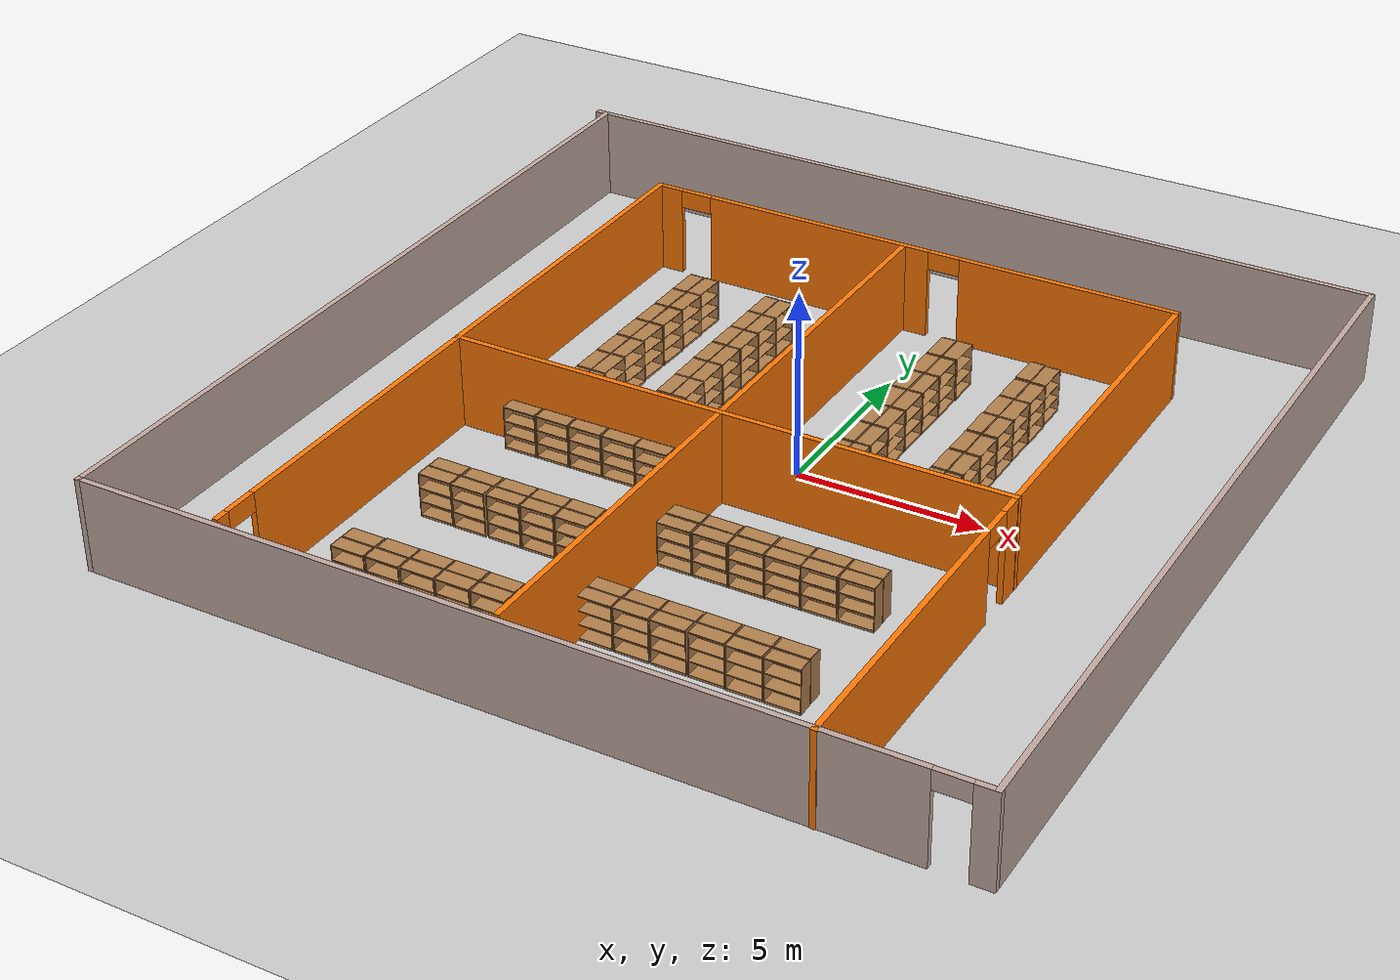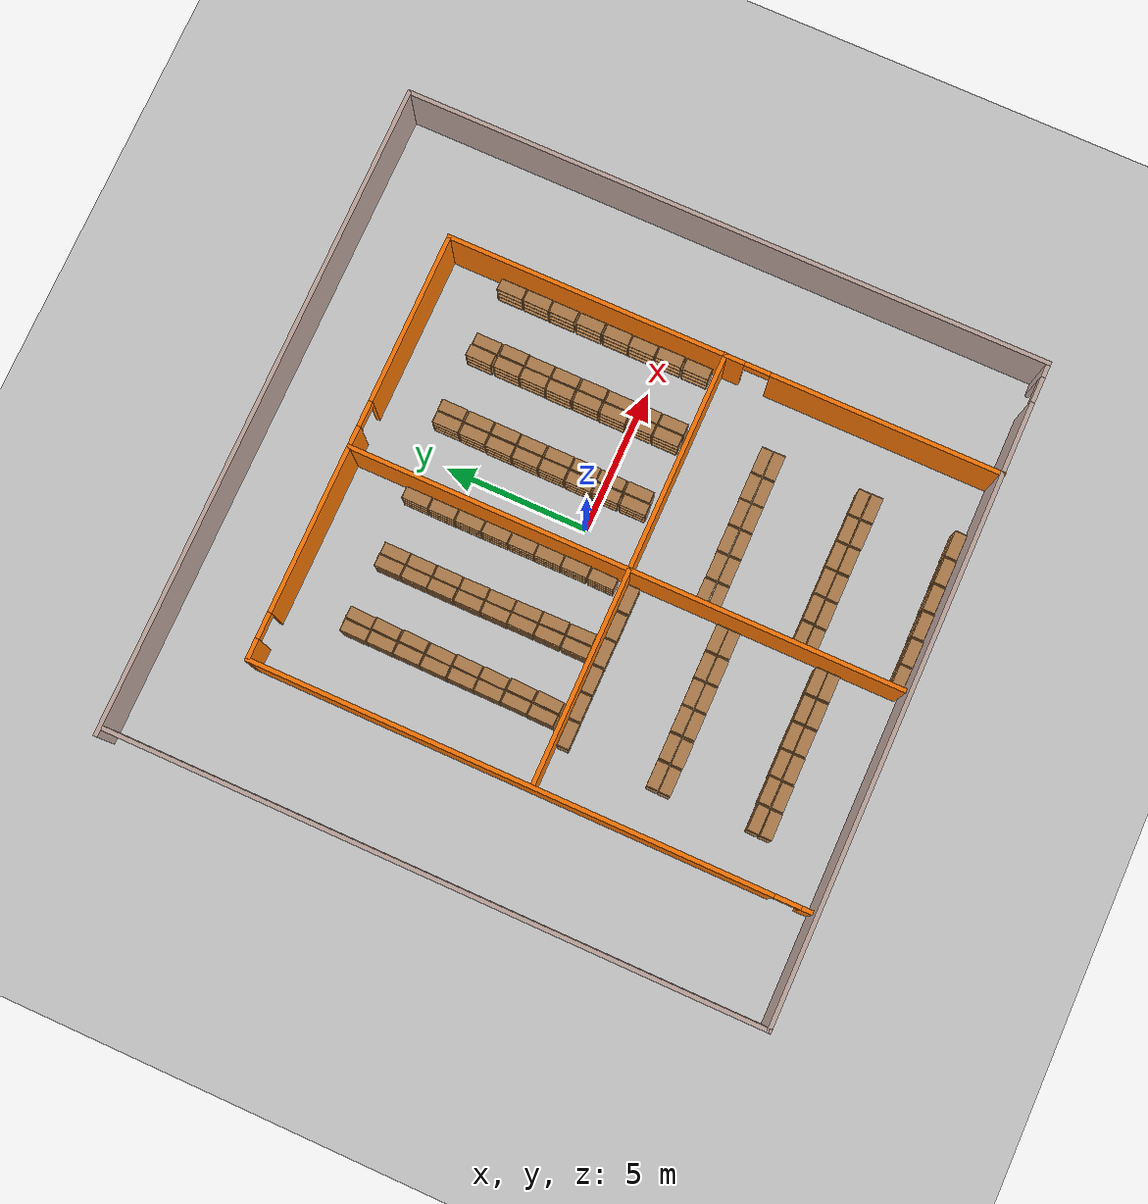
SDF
<sdf version="1.6">
 <world name="default">
  <plugin name="welcome" filename="libwelcome.so"/>
  <light name="sun" type="directional">
   <pose>0 0 10 0 -0 0</pose>
   <diffuse>0.8 0.8 0.8 1</diffuse>
   <specular>0.2 0.2 0.2 1</specular>
   <attenuation>
    <range>1000</range>
    <constant>0.9</constant>
    <linear>0.01</linear>
    <quadratic>0.001</quadratic>
   </attenuation>
   <direction>-0.5 0.1 -0.9</direction>
  </light>
  <model name="ground_plane">
   <static>1</static>
   <link name="link">
    <collision name="collision">
     <geometry><plane><normal>0 0 1</normal><size>100 100</size></plane></geometry>
     <surface>
      <contact><collide_bitmask>65535</collide_bitmask></contact>
      <friction><ode><mu>100</mu><mu2>50</mu2></ode></friction>
     </surface>
    </collision>
    <visual name="visual">
     <cast_shadows>0</cast_shadows>
     <geometry><plane><normal>0 0 1</normal><size>100 100</size></plane></geometry>
     <material>
      <script><uri>file://media/materials/scripts/gazebo.material</uri><name>Gazebo/Grey</name></script>
     </material>
    </visual>
   </link>
  </model>
  <gravity>0 0 -9.8</gravity>
  <magnetic_field>6e-06 2.3e-05 -4.2e-05</magnetic_field>
  <atmosphere type="adiabatic"/>
  <physics name="default_physics" default="0" type="ode">
   <max_step_size>0.001</max_step_size>
   <real_time_factor>1</real_time_factor>
   <real_time_update_rate>1000</real_time_update_rate>
  </physics>
  <scene><ambient>0.4 0.4 0.4 1</ambient><background>0.7 0.7 0.7 1</background><shadows>1</shadows></scene>
  <spherical_coordinates>
   <surface_model>EARTH_WGS84</surface_model>
   <latitude_deg>0</latitude_deg>
   <longitude_deg>0</longitude_deg>
   <elevation>0</elevation>
   <heading_deg>0</heading_deg>
  </spherical_coordinates>
  <model name="Building2">
   <pose>-0.982761 -0.2293 0 0 -0 0</pose>
   <link name="Wall_0">
    <collision name="Wall_0_Collision">
     <geometry><box><size>23.25 0.15 2.5</size></box></geometry>
     <pose>0 0 1.25 0 -0 0</pose>
    </collision>
    <visual name="Wall_0_Visual">
     <pose>0 0 1.25 0 -0 0</pose>
     <geometry><box><size>23.25 0.15 2.5</size></box></geometry>
     <material>
      <script><uri>file://media/materials/scripts/gazebo.material</uri><name>Gazebo/Grey</name></script>
      <ambient>0.760784 0.662745 0.627451 1</ambient>
     </material>
     <meta><layer>0</layer></meta>
    </visual>
    <pose>-1e-06 11.3105 0 0 -0 0</pose>
   </link>
   <link name="Wall_1">
    <collision name="Wall_1_Collision">
     <geometry><box><size>22.75 0.15 2.5</size></box></geometry>
     <pose>0 0 1.25 0 -0 0</pose>
    </collision>
    <visual name="Wall_1_Visual">
     <pose>0 0 1.25 0 -0 0</pose>
     <geometry><box><size>22.75 0.15 2.5</size></box></geometry>
     <material>
      <script><uri>file://media/materials/scripts/gazebo.material</uri><name>Gazebo/Grey</name></script>
      <ambient>0.760784 0.662745 0.627451 1</ambient>
     </material>
     <meta><layer>0</layer></meta>
    </visual>
    <pose>11.55 0.010515 0 0 0 -1.5708</pose>
   </link>
   <link name="Wall_13">
    <collision name="Wall_13_Collision">
     <geometry><box><size>19.25 0.15 2.5</size></box></geometry>
     <pose>0 0 1.25 0 -0 0</pose>
    </collision>
    <visual name="Wall_13_Visual">
     <pose>0 0 1.25 0 -0 0</pose>
     <geometry><box><size>19.25 0.15 2.5</size></box></geometry>
     <material>
      <script><uri>file://media/materials/scripts/gazebo.material</uri><name>Gazebo/Grey</name></script>
      <ambient>0.996078 0.47451 0.0196078 1</ambient>
     </material>
     <meta><layer>0</layer></meta>
    </visual>
    <pose>-0.068329 -1.51737 0 0 0 -1.5708</pose>
   </link>
   <link name="Wall_2">
    <pose>0.124999 -11.2895 0 0 -0 3.14159</pose>
    <visual name="Wall_2_Visual_0">
     <pose>-11.2049 0 1.25 0 -0 0</pose>
     <geometry><box><size>0.590222 0.15 2.5</size></box></geometry>
     <material>
      <script><uri>file://media/materials/scripts/gazebo.material</uri><name>Gazebo/Grey</name></script>
      <ambient>0.760784 0.662745 0.627451 1</ambient>
     </material>
     <meta><layer>0</layer></meta>
    </visual>
    <collision name="Wall_2_Collision_0">
     <geometry><box><size>0.590222 0.15 2.5</size></box></geometry>
     <pose>-11.2049 0 1.25 0 -0 0</pose>
    </collision>
    <visual name="Wall_2_Visual_1">
     <pose>0.745111 0 1.25 0 -0 0</pose>
     <geometry><box><size>21.5098 0.15 2.5</size></box></geometry>
     <material>
      <script><uri>file://media/materials/scripts/gazebo.material</uri><name>Gazebo/Grey</name></script>
      <ambient>0.760784 0.662745 0.627451 1</ambient>
     </material>
     <meta><layer>0</layer></meta>
    </visual>
    <collision name="Wall_2_Collision_1">
     <geometry><box><size>21.5098 0.15 2.5</size></box></geometry>
     <pose>0.745111 0 1.25 0 -0 0</pose>
    </collision>
    <visual name="Wall_2_Visual_2">
     <pose>-10.4598 0 2.25 0 -0 0</pose>
     <geometry><box><size>0.9 0.15 0.5</size></box></geometry>
     <material>
      <script><uri>file://media/materials/scripts/gazebo.material</uri><name>Gazebo/Grey</name></script>
      <ambient>0.760784 0.662745 0.627451 1</ambient>
     </material>
     <meta><layer>0</layer></meta>
    </visual>
    <collision name="Wall_2_Collision_2">
     <geometry><box><size>0.9 0.15 0.5</size></box></geometry>
     <pose>-10.4598 0 2.25 0 -0 0</pose>
    </collision>
   </link>
   <link name="Wall_3">
    <collision name="Wall_3_Collision">
     <geometry><box><size>22.75 0.15 2.5</size></box></geometry>
     <pose>0 0 1.25 0 -0 0</pose>
    </collision>
    <visual name="Wall_3_Visual">
     <pose>0 0 1.25 0 -0 0</pose>
     <geometry><box><size>22.75 0.15 2.5</size></box></geometry>
     <material>
      <script><uri>file://media/materials/scripts/gazebo.material</uri><name>Gazebo/Grey</name></script>
      <ambient>0.760784 0.662745 0.627451 1</ambient>
     </material>
     <meta><layer>0</layer></meta>
    </visual>
    <pose>-11.3 0.010515 0 0 -0 1.5708</pose>
   </link>
   <link name="Wall_5">
    <pose>7.57209 -1.63552 0 0 -0 1.5708</pose>
    <visual name="Wall_5_Visual_0">
     <pose>-5.69826 0 1.25 0 -0 0</pose>
     <geometry><box><size>8.10348 0.15 2.5</size></box></geometry>
     <material>
      <script><uri>file://media/materials/scripts/gazebo.material</uri><name>Gazebo/Grey</name></script>
      <ambient>0.996078 0.47451 0.0196078 1</ambient>
     </material>
     <meta><layer>0</layer></meta>
    </visual>
    <collision name="Wall_5_Collision_0">
     <geometry><box><size>8.10348 0.15 2.5</size></box></geometry>
     <pose>-5.69826 0 1.25 0 -0 0</pose>
    </collision>
    <visual name="Wall_5_Visual_1">
     <pose>4.50174 0 1.25 0 -0 0</pose>
     <geometry><box><size>10.4965 0.15 2.5</size></box></geometry>
     <material>
      <script><uri>file://media/materials/scripts/gazebo.material</uri><name>Gazebo/Grey</name></script>
      <ambient>0.996078 0.47451 0.0196078 1</ambient>
     </material>
     <meta><layer>0</layer></meta>
    </visual>
    <collision name="Wall_5_Collision_1">
     <geometry><box><size>10.4965 0.15 2.5</size></box></geometry>
     <pose>4.50174 0 1.25 0 -0 0</pose>
    </collision>
    <visual name="Wall_5_Visual_2">
     <pose>-1.19652 0 2.25 0 -0 0</pose>
     <geometry><box><size>0.9 0.15 0.5</size></box></geometry>
     <material>
      <script><uri>file://media/materials/scripts/gazebo.material</uri><name>Gazebo/Grey</name></script>
      <ambient>0.996078 0.47451 0.0196078 1</ambient>
     </material>
     <meta><layer>0</layer></meta>
    </visual>
    <collision name="Wall_5_Collision_2">
     <geometry><box><size>0.9 0.15 0.5</size></box></geometry>
     <pose>-1.19652 0 2.25 0 -0 0</pose>
    </collision>
   </link>
   <link name="Wall_6">
    <pose>0.022094 8.03948 0 0 -0 3.14159</pose>
    <visual name="Wall_6_Visual_0">
     <pose>-4.58053 0 1.25 0 -0 0</pose>
     <geometry><box><size>6.08894 0.15 2.5</size></box></geometry>
     <material>
      <script><uri>file://media/materials/scripts/gazebo.material</uri><name>Gazebo/Grey</name></script>
      <ambient>0.996078 0.47451 0.0196078 1</ambient>
     </material>
     <meta><layer>0</layer></meta>
    </visual>
    <collision name="Wall_6_Collision_0">
     <geometry><box><size>6.08894 0.15 2.5</size></box></geometry>
     <pose>-4.58053 0 1.25 0 -0 0</pose>
    </collision>
    <visual name="Wall_6_Visual_1">
     <pose>2.64925 0 1.25 0 -0 0</pose>
     <geometry><box><size>6.57062 0.15 2.5</size></box></geometry>
     <material>
      <script><uri>file://media/materials/scripts/gazebo.material</uri><name>Gazebo/Grey</name></script>
      <ambient>0.996078 0.47451 0.0196078 1</ambient>
     </material>
     <meta><layer>0</layer></meta>
    </visual>
    <collision name="Wall_6_Collision_1">
     <geometry><box><size>6.57062 0.15 2.5</size></box></geometry>
     <pose>2.64925 0 1.25 0 -0 0</pose>
    </collision>
    <visual name="Wall_6_Visual_2">
     <pose>7.22978 0 1.25 0 -0 0</pose>
     <geometry><box><size>0.790441 0.15 2.5</size></box></geometry>
     <material>
      <script><uri>file://media/materials/scripts/gazebo.material</uri><name>Gazebo/Grey</name></script>
      <ambient>0.996078 0.47451 0.0196078 1</ambient>
     </material>
     <meta><layer>0</layer></meta>
    </visual>
    <collision name="Wall_6_Collision_2">
     <geometry><box><size>0.790441 0.15 2.5</size></box></geometry>
     <pose>7.22978 0 1.25 0 -0 0</pose>
    </collision>
    <visual name="Wall_6_Visual_3">
     <pose>-1.08606 0 2.25 0 -0 0</pose>
     <geometry><box><size>0.9 0.15 0.5</size></box></geometry>
     <material>
      <script><uri>file://media/materials/scripts/gazebo.material</uri><name>Gazebo/Grey</name></script>
      <ambient>0.996078 0.47451 0.0196078 1</ambient>
     </material>
     <meta><layer>0</layer></meta>
    </visual>
    <collision name="Wall_6_Collision_3">
     <geometry><box><size>0.9 0.15 0.5</size></box></geometry>
     <pose>-1.08606 0 2.25 0 -0 0</pose>
    </collision>
    <visual name="Wall_6_Visual_4">
     <pose>6.38456 0 2.25 0 -0 0</pose>
     <geometry><box><size>0.9 0.15 0.5</size></box></geometry>
     <material>
      <script><uri>file://media/materials/scripts/gazebo.material</uri><name>Gazebo/Grey</name></script>
      <ambient>0.996078 0.47451 0.0196078 1</ambient>
     </material>
     <meta><layer>0</layer></meta>
    </visual>
    <collision name="Wall_6_Collision_4">
     <geometry><box><size>0.9 0.15 0.5</size></box></geometry>
     <pose>6.38456 0 2.25 0 -0 0</pose>
    </collision>
   </link>
   <link name="Wall_7">
    <pose>-7.5279 -1.51052 0 0 0 -1.5708</pose>
    <visual name="Wall_7_Visual_0">
     <pose>-0.641428 0 1.25 0 -0 0</pose>
     <geometry><box><size>17.9671 0.15 2.5</size></box></geometry>
     <material>
      <script><uri>file://media/materials/scripts/gazebo.material</uri><name>Gazebo/Grey</name></script>
      <ambient>0.996078 0.47451 0.0196078 1</ambient>
     </material>
     <meta><layer>0</layer></meta>
    </visual>
    <collision name="Wall_7_Collision_0">
     <geometry><box><size>17.9671 0.15 2.5</size></box></geometry>
     <pose>-0.641428 0 1.25 0 -0 0</pose>
    </collision>
    <visual name="Wall_7_Visual_1">
     <pose>9.43357 0 1.25 0 -0 0</pose>
     <geometry><box><size>0.382856 0.15 2.5</size></box></geometry>
     <material>
      <script><uri>file://media/materials/scripts/gazebo.material</uri><name>Gazebo/Grey</name></script>
      <ambient>0.996078 0.47451 0.0196078 1</ambient>
     </material>
     <meta><layer>0</layer></meta>
    </visual>
    <collision name="Wall_7_Collision_1">
     <geometry><box><size>0.382856 0.15 2.5</size></box></geometry>
     <pose>9.43357 0 1.25 0 -0 0</pose>
    </collision>
    <visual name="Wall_7_Visual_2">
     <pose>8.79214 0 2.25 0 -0 0</pose>
     <geometry><box><size>0.9 0.15 0.5</size></box></geometry>
     <material>
      <script><uri>file://media/materials/scripts/gazebo.material</uri><name>Gazebo/Grey</name></script>
      <ambient>0.996078 0.47451 0.0196078 1</ambient>
     </material>
     <meta><layer>0</layer></meta>
    </visual>
    <collision name="Wall_7_Collision_2">
     <geometry><box><size>0.9 0.15 0.5</size></box></geometry>
     <pose>8.79214 0 2.25 0 -0 0</pose>
    </collision>
   </link>
   <link name="Wall_9">
    <collision name="Wall_9_Collision">
     <geometry><box><size>15.25 0.15 2.5</size></box></geometry>
     <pose>0 0 1.25 0 -0 0</pose>
    </collision>
    <visual name="Wall_9_Visual">
     <pose>0 0 1.25 0 -0 0</pose>
     <geometry><box><size>15.25 0.15 2.5</size></box></geometry>
     <material>
      <script><uri>file://media/materials/scripts/gazebo.material</uri><name>Gazebo/Grey</name></script>
      <ambient>0.996078 0.47451 0.0196078 1</ambient>
     </material>
     <meta><layer>0</layer></meta>
    </visual>
    <pose>0.033742 -1.70878 0 0 -0 0</pose>
   </link>
   <static>1</static>
  </model>
  <model name="bookshelf">
   <static>1</static>
   <link name="link">
    <inertial><mass>1</mass></inertial>
    <collision name="back">
     <pose>0 0.005 0.6 0 -0 0</pose>
     <geometry><box><size>0.9 0.01 1.2</size></box></geometry>
    </collision>
    <visual name="visual1">
     <pose>0 0.005 0.6 0 -0 0</pose>
     <geometry><box><size>0.9 0.01 1.2</size></box></geometry>
     <material>
      <script><uri>file://media/materials/scripts/gazebo.material</uri><name>Gazebo/Wood</name></script>
     </material>
    </visual>
    <collision name="left_side">
     <pose>0.45 -0.195 0.6 0 -0 0</pose>
     <geometry><box><size>0.02 0.4 1.2</size></box></geometry>
    </collision>
    <visual name="visual2">
     <pose>0.45 -0.195 0.6 0 -0 0</pose>
     <geometry><box><size>0.02 0.4 1.2</size></box></geometry>
     <material>
      <script><uri>file://media/materials/scripts/gazebo.material</uri><name>Gazebo/Wood</name></script>
     </material>
    </visual>
    <collision name="right_side">
     <pose>-0.45 -0.195 0.6 0 -0 0</pose>
     <geometry><box><size>0.02 0.4 1.2</size></box></geometry>
    </collision>
    <visual name="visual3">
     <pose>-0.45 -0.195 0.6 0 -0 0</pose>
     <geometry><box><size>0.02 0.4 1.2</size></box></geometry>
     <material>
      <script><uri>file://media/materials/scripts/gazebo.material</uri><name>Gazebo/Wood</name></script>
     </material>
    </visual>
    <collision name="bottom">
     <pose>0 -0.195 0.03 0 -0 0</pose>
     <geometry><box><size>0.88 0.4 0.06</size></box></geometry>
    </collision>
    <visual name="visual4">
     <pose>0 -0.195 0.03 0 -0 0</pose>
     <geometry><box><size>0.88 0.4 0.06</size></box></geometry>
     <material>
      <script><uri>file://media/materials/scripts/gazebo.material</uri><name>Gazebo/Wood</name></script>
     </material>
    </visual>
    <collision name="top">
     <pose>0 -0.195 1.19 0 -0 0</pose>
     <geometry><box><size>0.88 0.4 0.02</size></box></geometry>
    </collision>
    <visual name="visual5">
     <pose>0 -0.195 1.19 0 -0 0</pose>
     <geometry><box><size>0.88 0.4 0.02</size></box></geometry>
     <material>
      <script><uri>file://media/materials/scripts/gazebo.material</uri><name>Gazebo/Wood</name></script>
     </material>
    </visual>
    <collision name="low_shelf">
     <pose>0 -0.195 0.43 0 -0 0</pose>
     <geometry><box><size>0.88 0.4 0.02</size></box></geometry>
    </collision>
    <visual name="visual6">
     <pose>0 -0.195 0.43 0 -0 0</pose>
     <geometry><box><size>0.88 0.4 0.02</size></box></geometry>
     <material>
      <script><uri>file://media/materials/scripts/gazebo.material</uri><name>Gazebo/Wood</name></script>
     </material>
    </visual>
    <collision name="high_shelf">
     <pose>0 -0.195 0.8 0 -0 0</pose>
     <geometry><box><size>0.88 0.4 0.02</size></box></geometry>
    </collision>
    <visual name="visual7">
     <pose>0 -0.195 0.8 0 -0 0</pose>
     <geometry><box><size>0.88 0.4 0.02</size></box></geometry>
     <material>
      <script><uri>file://media/materials/scripts/gazebo.material</uri><name>Gazebo/Wood</name></script>
     </material>
    </visual>
   </link>
   <pose>-6.04058 -1.25922 0 0 0 -1.57936</pose>
  </model>
  <model name="bookshelf_clone">
   <static>1</static>
   <link name="link">
    <inertial><mass>1</mass></inertial>
    <collision name="back">
     <pose>0 0.005 0.6 0 -0 0</pose>
     <geometry><box><size>0.9 0.01 1.2</size></box></geometry>
    </collision>
    <visual name="visual1">
     <pose>0 0.005 0.6 0 -0 0</pose>
     <geometry><box><size>0.9 0.01 1.2</size></box></geometry>
     <material>
      <script><uri>file://media/materials/scripts/gazebo.material</uri><name>Gazebo/Wood</name></script>
     </material>
    </visual>
    <collision name="left_side">
     <pose>0.45 -0.195 0.6 0 -0 0</pose>
     <geometry><box><size>0.02 0.4 1.2</size></box></geometry>
    </collision>
    <visual name="visual2">
     <pose>0.45 -0.195 0.6 0 -0 0</pose>
     <geometry><box><size>0.02 0.4 1.2</size></box></geometry>
     <material>
      <script><uri>file://media/materials/scripts/gazebo.material</uri><name>Gazebo/Wood</name></script>
     </material>
    </visual>
    <collision name="right_side">
     <pose>-0.45 -0.195 0.6 0 -0 0</pose>
     <geometry><box><size>0.02 0.4 1.2</size></box></geometry>
    </collision>
    <visual name="visual3">
     <pose>-0.45 -0.195 0.6 0 -0 0</pose>
     <geometry><box><size>0.02 0.4 1.2</size></box></geometry>
     <material>
      <script><uri>file://media/materials/scripts/gazebo.material</uri><name>Gazebo/Wood</name></script>
     </material>
    </visual>
    <collision name="bottom">
     <pose>0 -0.195 0.03 0 -0 0</pose>
     <geometry><box><size>0.88 0.4 0.06</size></box></geometry>
    </collision>
    <visual name="visual4">
     <pose>0 -0.195 0.03 0 -0 0</pose>
     <geometry><box><size>0.88 0.4 0.06</size></box></geometry>
     <material>
      <script><uri>file://media/materials/scripts/gazebo.material</uri><name>Gazebo/Wood</name></script>
     </material>
    </visual>
    <collision name="top">
     <pose>0 -0.195 1.19 0 -0 0</pose>
     <geometry><box><size>0.88 0.4 0.02</size></box></geometry>
    </collision>
    <visual name="visual5">
     <pose>0 -0.195 1.19 0 -0 0</pose>
     <geometry><box><size>0.88 0.4 0.02</size></box></geometry>
     <material>
      <script><uri>file://media/materials/scripts/gazebo.material</uri><name>Gazebo/Wood</name></script>
     </material>
    </visual>
    <collision name="low_shelf">
     <pose>0 -0.195 0.43 0 -0 0</pose>
     <geometry><box><size>0.88 0.4 0.02</size></box></geometry>
    </collision>
    <visual name="visual6">
     <pose>0 -0.195 0.43 0 -0 0</pose>
     <geometry><box><size>0.88 0.4 0.02</size></box></geometry>
     <material>
      <script><uri>file://media/materials/scripts/gazebo.material</uri><name>Gazebo/Wood</name></script>
     </material>
    </visual>
    <collision name="high_shelf">
     <pose>0 -0.195 0.8 0 -0 0</pose>
     <geometry><box><size>0.88 0.4 0.02</size></box></geometry>
    </collision>
    <visual name="visual7">
     <pose>0 -0.195 0.8 0 -0 0</pose>
     <geometry><box><size>0.88 0.4 0.02</size></box></geometry>
     <material>
      <script><uri>file://media/materials/scripts/gazebo.material</uri><name>Gazebo/Wood</name></script>
     </material>
    </visual>
   </link>
   <pose>-6.02073 -0.323633 0 0 0 -1.58271</pose>
  </model>
  <model name="bookshelf_clone_0">
   <static>1</static>
   <link name="link">
    <inertial><mass>1</mass></inertial>
    <collision name="back">
     <pose>0 0.005 0.6 0 -0 0</pose>
     <geometry><box><size>0.9 0.01 1.2</size></box></geometry>
    </collision>
    <visual name="visual1">
     <pose>0 0.005 0.6 0 -0 0</pose>
     <geometry><box><size>0.9 0.01 1.2</size></box></geometry>
     <material>
      <script><uri>file://media/materials/scripts/gazebo.material</uri><name>Gazebo/Wood</name></script>
     </material>
    </visual>
    <collision name="left_side">
     <pose>0.45 -0.195 0.6 0 -0 0</pose>
     <geometry><box><size>0.02 0.4 1.2</size></box></geometry>
    </collision>
    <visual name="visual2">
     <pose>0.45 -0.195 0.6 0 -0 0</pose>
     <geometry><box><size>0.02 0.4 1.2</size></box></geometry>
     <material>
      <script><uri>file://media/materials/scripts/gazebo.material</uri><name>Gazebo/Wood</name></script>
     </material>
    </visual>
    <collision name="right_side">
     <pose>-0.45 -0.195 0.6 0 -0 0</pose>
     <geometry><box><size>0.02 0.4 1.2</size></box></geometry>
    </collision>
    <visual name="visual3">
     <pose>-0.45 -0.195 0.6 0 -0 0</pose>
     <geometry><box><size>0.02 0.4 1.2</size></box></geometry>
     <material>
      <script><uri>file://media/materials/scripts/gazebo.material</uri><name>Gazebo/Wood</name></script>
     </material>
    </visual>
    <collision name="bottom">
     <pose>0 -0.195 0.03 0 -0 0</pose>
     <geometry><box><size>0.88 0.4 0.06</size></box></geometry>
    </collision>
    <visual name="visual4">
     <pose>0 -0.195 0.03 0 -0 0</pose>
     <geometry><box><size>0.88 0.4 0.06</size></box></geometry>
     <material>
      <script><uri>file://media/materials/scripts/gazebo.material</uri><name>Gazebo/Wood</name></script>
     </material>
    </visual>
    <collision name="top">
     <pose>0 -0.195 1.19 0 -0 0</pose>
     <geometry><box><size>0.88 0.4 0.02</size></box></geometry>
    </collision>
    <visual name="visual5">
     <pose>0 -0.195 1.19 0 -0 0</pose>
     <geometry><box><size>0.88 0.4 0.02</size></box></geometry>
     <material>
      <script><uri>file://media/materials/scripts/gazebo.material</uri><name>Gazebo/Wood</name></script>
     </material>
    </visual>
    <collision name="low_shelf">
     <pose>0 -0.195 0.43 0 -0 0</pose>
     <geometry><box><size>0.88 0.4 0.02</size></box></geometry>
    </collision>
    <visual name="visual6">
     <pose>0 -0.195 0.43 0 -0 0</pose>
     <geometry><box><size>0.88 0.4 0.02</size></box></geometry>
     <material>
      <script><uri>file://media/materials/scripts/gazebo.material</uri><name>Gazebo/Wood</name></script>
     </material>
    </visual>
    <collision name="high_shelf">
     <pose>0 -0.195 0.8 0 -0 0</pose>
     <geometry><box><size>0.88 0.4 0.02</size></box></geometry>
    </collision>
    <visual name="visual7">
     <pose>0 -0.195 0.8 0 -0 0</pose>
     <geometry><box><size>0.88 0.4 0.02</size></box></geometry>
     <material>
      <script><uri>file://media/materials/scripts/gazebo.material</uri><name>Gazebo/Wood</name></script>
     </material>
    </visual>
   </link>
   <pose>-6.02068 0.616769 0 0 0 -1.58271</pose>
  </model>
  <model name="bookshelf_clone_1">
   <static>1</static>
   <link name="link">
    <inertial><mass>1</mass></inertial>
    <collision name="back">
     <pose>0 0.005 0.6 0 -0 0</pose>
     <geometry><box><size>0.9 0.01 1.2</size></box></geometry>
    </collision>
    <visual name="visual1">
     <pose>0 0.005 0.6 0 -0 0</pose>
     <geometry><box><size>0.9 0.01 1.2</size></box></geometry>
     <material>
      <script><uri>file://media/materials/scripts/gazebo.material</uri><name>Gazebo/Wood</name></script>
     </material>
    </visual>
    <collision name="left_side">
     <pose>0.45 -0.195 0.6 0 -0 0</pose>
     <geometry><box><size>0.02 0.4 1.2</size></box></geometry>
    </collision>
    <visual name="visual2">
     <pose>0.45 -0.195 0.6 0 -0 0</pose>
     <geometry><box><size>0.02 0.4 1.2</size></box></geometry>
     <material>
      <script><uri>file://media/materials/scripts/gazebo.material</uri><name>Gazebo/Wood</name></script>
     </material>
    </visual>
    <collision name="right_side">
     <pose>-0.45 -0.195 0.6 0 -0 0</pose>
     <geometry><box><size>0.02 0.4 1.2</size></box></geometry>
    </collision>
    <visual name="visual3">
     <pose>-0.45 -0.195 0.6 0 -0 0</pose>
     <geometry><box><size>0.02 0.4 1.2</size></box></geometry>
     <material>
      <script><uri>file://media/materials/scripts/gazebo.material</uri><name>Gazebo/Wood</name></script>
     </material>
    </visual>
    <collision name="bottom">
     <pose>0 -0.195 0.03 0 -0 0</pose>
     <geometry><box><size>0.88 0.4 0.06</size></box></geometry>
    </collision>
    <visual name="visual4">
     <pose>0 -0.195 0.03 0 -0 0</pose>
     <geometry><box><size>0.88 0.4 0.06</size></box></geometry>
     <material>
      <script><uri>file://media/materials/scripts/gazebo.material</uri><name>Gazebo/Wood</name></script>
     </material>
    </visual>
    <collision name="top">
     <pose>0 -0.195 1.19 0 -0 0</pose>
     <geometry><box><size>0.88 0.4 0.02</size></box></geometry>
    </collision>
    <visual name="visual5">
     <pose>0 -0.195 1.19 0 -0 0</pose>
     <geometry><box><size>0.88 0.4 0.02</size></box></geometry>
     <material>
      <script><uri>file://media/materials/scripts/gazebo.material</uri><name>Gazebo/Wood</name></script>
     </material>
    </visual>
    <collision name="low_shelf">
     <pose>0 -0.195 0.43 0 -0 0</pose>
     <geometry><box><size>0.88 0.4 0.02</size></box></geometry>
    </collision>
    <visual name="visual6">
     <pose>0 -0.195 0.43 0 -0 0</pose>
     <geometry><box><size>0.88 0.4 0.02</size></box></geometry>
     <material>
      <script><uri>file://media/materials/scripts/gazebo.material</uri><name>Gazebo/Wood</name></script>
     </material>
    </visual>
    <collision name="high_shelf">
     <pose>0 -0.195 0.8 0 -0 0</pose>
     <geometry><box><size>0.88 0.4 0.02</size></box></geometry>
    </collision>
    <visual name="visual7">
     <pose>0 -0.195 0.8 0 -0 0</pose>
     <geometry><box><size>0.88 0.4 0.02</size></box></geometry>
     <material>
      <script><uri>file://media/materials/scripts/gazebo.material</uri><name>Gazebo/Wood</name></script>
     </material>
    </visual>
   </link>
   <pose>-6.01944 1.55519 0 0 0 -1.58271</pose>
  </model>
  <model name="bookshelf_clone_2">
   <static>1</static>
   <link name="link">
    <inertial><mass>1</mass></inertial>
    <collision name="back">
     <pose>0 0.005 0.6 0 -0 0</pose>
     <geometry><box><size>0.9 0.01 1.2</size></box></geometry>
    </collision>
    <visual name="visual1">
     <pose>0 0.005 0.6 0 -0 0</pose>
     <geometry><box><size>0.9 0.01 1.2</size></box></geometry>
     <material>
      <script><uri>file://media/materials/scripts/gazebo.material</uri><name>Gazebo/Wood</name></script>
     </material>
    </visual>
    <collision name="left_side">
     <pose>0.45 -0.195 0.6 0 -0 0</pose>
     <geometry><box><size>0.02 0.4 1.2</size></box></geometry>
    </collision>
    <visual name="visual2">
     <pose>0.45 -0.195 0.6 0 -0 0</pose>
     <geometry><box><size>0.02 0.4 1.2</size></box></geometry>
     <material>
      <script><uri>file://media/materials/scripts/gazebo.material</uri><name>Gazebo/Wood</name></script>
     </material>
    </visual>
    <collision name="right_side">
     <pose>-0.45 -0.195 0.6 0 -0 0</pose>
     <geometry><box><size>0.02 0.4 1.2</size></box></geometry>
    </collision>
    <visual name="visual3">
     <pose>-0.45 -0.195 0.6 0 -0 0</pose>
     <geometry><box><size>0.02 0.4 1.2</size></box></geometry>
     <material>
      <script><uri>file://media/materials/scripts/gazebo.material</uri><name>Gazebo/Wood</name></script>
     </material>
    </visual>
    <collision name="bottom">
     <pose>0 -0.195 0.03 0 -0 0</pose>
     <geometry><box><size>0.88 0.4 0.06</size></box></geometry>
    </collision>
    <visual name="visual4">
     <pose>0 -0.195 0.03 0 -0 0</pose>
     <geometry><box><size>0.88 0.4 0.06</size></box></geometry>
     <material>
      <script><uri>file://media/materials/scripts/gazebo.material</uri><name>Gazebo/Wood</name></script>
     </material>
    </visual>
    <collision name="top">
     <pose>0 -0.195 1.19 0 -0 0</pose>
     <geometry><box><size>0.88 0.4 0.02</size></box></geometry>
    </collision>
    <visual name="visual5">
     <pose>0 -0.195 1.19 0 -0 0</pose>
     <geometry><box><size>0.88 0.4 0.02</size></box></geometry>
     <material>
      <script><uri>file://media/materials/scripts/gazebo.material</uri><name>Gazebo/Wood</name></script>
     </material>
    </visual>
    <collision name="low_shelf">
     <pose>0 -0.195 0.43 0 -0 0</pose>
     <geometry><box><size>0.88 0.4 0.02</size></box></geometry>
    </collision>
    <visual name="visual6">
     <pose>0 -0.195 0.43 0 -0 0</pose>
     <geometry><box><size>0.88 0.4 0.02</size></box></geometry>
     <material>
      <script><uri>file://media/materials/scripts/gazebo.material</uri><name>Gazebo/Wood</name></script>
     </material>
    </visual>
    <collision name="high_shelf">
     <pose>0 -0.195 0.8 0 -0 0</pose>
     <geometry><box><size>0.88 0.4 0.02</size></box></geometry>
    </collision>
    <visual name="visual7">
     <pose>0 -0.195 0.8 0 -0 0</pose>
     <geometry><box><size>0.88 0.4 0.02</size></box></geometry>
     <material>
      <script><uri>file://media/materials/scripts/gazebo.material</uri><name>Gazebo/Wood</name></script>
     </material>
    </visual>
   </link>
   <pose>-6.01655 2.50629 0 0 0 -1.58271</pose>
  </model>
  <model name="bookshelf_clone_3">
   <static>1</static>
   <link name="link">
    <inertial><mass>1</mass></inertial>
    <collision name="back">
     <pose>0 0.005 0.6 0 -0 0</pose>
     <geometry><box><size>0.9 0.01 1.2</size></box></geometry>
    </collision>
    <visual name="visual1">
     <pose>0 0.005 0.6 0 -0 0</pose>
     <geometry><box><size>0.9 0.01 1.2</size></box></geometry>
     <material>
      <script><uri>file://media/materials/scripts/gazebo.material</uri><name>Gazebo/Wood</name></script>
     </material>
    </visual>
    <collision name="left_side">
     <pose>0.45 -0.195 0.6 0 -0 0</pose>
     <geometry><box><size>0.02 0.4 1.2</size></box></geometry>
    </collision>
    <visual name="visual2">
     <pose>0.45 -0.195 0.6 0 -0 0</pose>
     <geometry><box><size>0.02 0.4 1.2</size></box></geometry>
     <material>
      <script><uri>file://media/materials/scripts/gazebo.material</uri><name>Gazebo/Wood</name></script>
     </material>
    </visual>
    <collision name="right_side">
     <pose>-0.45 -0.195 0.6 0 -0 0</pose>
     <geometry><box><size>0.02 0.4 1.2</size></box></geometry>
    </collision>
    <visual name="visual3">
     <pose>-0.45 -0.195 0.6 0 -0 0</pose>
     <geometry><box><size>0.02 0.4 1.2</size></box></geometry>
     <material>
      <script><uri>file://media/materials/scripts/gazebo.material</uri><name>Gazebo/Wood</name></script>
     </material>
    </visual>
    <collision name="bottom">
     <pose>0 -0.195 0.03 0 -0 0</pose>
     <geometry><box><size>0.88 0.4 0.06</size></box></geometry>
    </collision>
    <visual name="visual4">
     <pose>0 -0.195 0.03 0 -0 0</pose>
     <geometry><box><size>0.88 0.4 0.06</size></box></geometry>
     <material>
      <script><uri>file://media/materials/scripts/gazebo.material</uri><name>Gazebo/Wood</name></script>
     </material>
    </visual>
    <collision name="top">
     <pose>0 -0.195 1.19 0 -0 0</pose>
     <geometry><box><size>0.88 0.4 0.02</size></box></geometry>
    </collision>
    <visual name="visual5">
     <pose>0 -0.195 1.19 0 -0 0</pose>
     <geometry><box><size>0.88 0.4 0.02</size></box></geometry>
     <material>
      <script><uri>file://media/materials/scripts/gazebo.material</uri><name>Gazebo/Wood</name></script>
     </material>
    </visual>
    <collision name="low_shelf">
     <pose>0 -0.195 0.43 0 -0 0</pose>
     <geometry><box><size>0.88 0.4 0.02</size></box></geometry>
    </collision>
    <visual name="visual6">
     <pose>0 -0.195 0.43 0 -0 0</pose>
     <geometry><box><size>0.88 0.4 0.02</size></box></geometry>
     <material>
      <script><uri>file://media/materials/scripts/gazebo.material</uri><name>Gazebo/Wood</name></script>
     </material>
    </visual>
    <collision name="high_shelf">
     <pose>0 -0.195 0.8 0 -0 0</pose>
     <geometry><box><size>0.88 0.4 0.02</size></box></geometry>
    </collision>
    <visual name="visual7">
     <pose>0 -0.195 0.8 0 -0 0</pose>
     <geometry><box><size>0.88 0.4 0.02</size></box></geometry>
     <material>
      <script><uri>file://media/materials/scripts/gazebo.material</uri><name>Gazebo/Wood</name></script>
     </material>
    </visual>
   </link>
   <pose>-6.00479 3.44865 0 0 0 -1.58271</pose>
  </model>
  <model name="bookshelf_clone_4">
   <static>1</static>
   <link name="link">
    <inertial><mass>1</mass></inertial>
    <collision name="back">
     <pose>0 0.005 0.6 0 -0 0</pose>
     <geometry><box><size>0.9 0.01 1.2</size></box></geometry>
    </collision>
    <visual name="visual1">
     <pose>0 0.005 0.6 0 -0 0</pose>
     <geometry><box><size>0.9 0.01 1.2</size></box></geometry>
     <material>
      <script><uri>file://media/materials/scripts/gazebo.material</uri><name>Gazebo/Wood</name></script>
     </material>
    </visual>
    <collision name="left_side">
     <pose>0.45 -0.195 0.6 0 -0 0</pose>
     <geometry><box><size>0.02 0.4 1.2</size></box></geometry>
    </collision>
    <visual name="visual2">
     <pose>0.45 -0.195 0.6 0 -0 0</pose>
     <geometry><box><size>0.02 0.4 1.2</size></box></geometry>
     <material>
      <script><uri>file://media/materials/scripts/gazebo.material</uri><name>Gazebo/Wood</name></script>
     </material>
    </visual>
    <collision name="right_side">
     <pose>-0.45 -0.195 0.6 0 -0 0</pose>
     <geometry><box><size>0.02 0.4 1.2</size></box></geometry>
    </collision>
    <visual name="visual3">
     <pose>-0.45 -0.195 0.6 0 -0 0</pose>
     <geometry><box><size>0.02 0.4 1.2</size></box></geometry>
     <material>
      <script><uri>file://media/materials/scripts/gazebo.material</uri><name>Gazebo/Wood</name></script>
     </material>
    </visual>
    <collision name="bottom">
     <pose>0 -0.195 0.03 0 -0 0</pose>
     <geometry><box><size>0.88 0.4 0.06</size></box></geometry>
    </collision>
    <visual name="visual4">
     <pose>0 -0.195 0.03 0 -0 0</pose>
     <geometry><box><size>0.88 0.4 0.06</size></box></geometry>
     <material>
      <script><uri>file://media/materials/scripts/gazebo.material</uri><name>Gazebo/Wood</name></script>
     </material>
    </visual>
    <collision name="top">
     <pose>0 -0.195 1.19 0 -0 0</pose>
     <geometry><box><size>0.88 0.4 0.02</size></box></geometry>
    </collision>
    <visual name="visual5">
     <pose>0 -0.195 1.19 0 -0 0</pose>
     <geometry><box><size>0.88 0.4 0.02</size></box></geometry>
     <material>
      <script><uri>file://media/materials/scripts/gazebo.material</uri><name>Gazebo/Wood</name></script>
     </material>
    </visual>
    <collision name="low_shelf">
     <pose>0 -0.195 0.43 0 -0 0</pose>
     <geometry><box><size>0.88 0.4 0.02</size></box></geometry>
    </collision>
    <visual name="visual6">
     <pose>0 -0.195 0.43 0 -0 0</pose>
     <geometry><box><size>0.88 0.4 0.02</size></box></geometry>
     <material>
      <script><uri>file://media/materials/scripts/gazebo.material</uri><name>Gazebo/Wood</name></script>
     </material>
    </visual>
    <collision name="high_shelf">
     <pose>0 -0.195 0.8 0 -0 0</pose>
     <geometry><box><size>0.88 0.4 0.02</size></box></geometry>
    </collision>
    <visual name="visual7">
     <pose>0 -0.195 0.8 0 -0 0</pose>
     <geometry><box><size>0.88 0.4 0.02</size></box></geometry>
     <material>
      <script><uri>file://media/materials/scripts/gazebo.material</uri><name>Gazebo/Wood</name></script>
     </material>
    </visual>
   </link>
   <pose>-6.00189 4.39097 0 0 0 -1.58271</pose>
  </model>
  <model name="bookshelf_clone_5">
   <static>1</static>
   <link name="link">
    <inertial><mass>1</mass></inertial>
    <collision name="back">
     <pose>0 0.005 0.6 0 -0 0</pose>
     <geometry><box><size>0.9 0.01 1.2</size></box></geometry>
    </collision>
    <visual name="visual1">
     <pose>0 0.005 0.6 0 -0 0</pose>
     <geometry><box><size>0.9 0.01 1.2</size></box></geometry>
     <material>
      <script><uri>file://media/materials/scripts/gazebo.material</uri><name>Gazebo/Wood</name></script>
     </material>
    </visual>
    <collision name="left_side">
     <pose>0.45 -0.195 0.6 0 -0 0</pose>
     <geometry><box><size>0.02 0.4 1.2</size></box></geometry>
    </collision>
    <visual name="visual2">
     <pose>0.45 -0.195 0.6 0 -0 0</pose>
     <geometry><box><size>0.02 0.4 1.2</size></box></geometry>
     <material>
      <script><uri>file://media/materials/scripts/gazebo.material</uri><name>Gazebo/Wood</name></script>
     </material>
    </visual>
    <collision name="right_side">
     <pose>-0.45 -0.195 0.6 0 -0 0</pose>
     <geometry><box><size>0.02 0.4 1.2</size></box></geometry>
    </collision>
    <visual name="visual3">
     <pose>-0.45 -0.195 0.6 0 -0 0</pose>
     <geometry><box><size>0.02 0.4 1.2</size></box></geometry>
     <material>
      <script><uri>file://media/materials/scripts/gazebo.material</uri><name>Gazebo/Wood</name></script>
     </material>
    </visual>
    <collision name="bottom">
     <pose>0 -0.195 0.03 0 -0 0</pose>
     <geometry><box><size>0.88 0.4 0.06</size></box></geometry>
    </collision>
    <visual name="visual4">
     <pose>0 -0.195 0.03 0 -0 0</pose>
     <geometry><box><size>0.88 0.4 0.06</size></box></geometry>
     <material>
      <script><uri>file://media/materials/scripts/gazebo.material</uri><name>Gazebo/Wood</name></script>
     </material>
    </visual>
    <collision name="top">
     <pose>0 -0.195 1.19 0 -0 0</pose>
     <geometry><box><size>0.88 0.4 0.02</size></box></geometry>
    </collision>
    <visual name="visual5">
     <pose>0 -0.195 1.19 0 -0 0</pose>
     <geometry><box><size>0.88 0.4 0.02</size></box></geometry>
     <material>
      <script><uri>file://media/materials/scripts/gazebo.material</uri><name>Gazebo/Wood</name></script>
     </material>
    </visual>
    <collision name="low_shelf">
     <pose>0 -0.195 0.43 0 -0 0</pose>
     <geometry><box><size>0.88 0.4 0.02</size></box></geometry>
    </collision>
    <visual name="visual6">
     <pose>0 -0.195 0.43 0 -0 0</pose>
     <geometry><box><size>0.88 0.4 0.02</size></box></geometry>
     <material>
      <script><uri>file://media/materials/scripts/gazebo.material</uri><name>Gazebo/Wood</name></script>
     </material>
    </visual>
    <collision name="high_shelf">
     <pose>0 -0.195 0.8 0 -0 0</pose>
     <geometry><box><size>0.88 0.4 0.02</size></box></geometry>
    </collision>
    <visual name="visual7">
     <pose>0 -0.195 0.8 0 -0 0</pose>
     <geometry><box><size>0.88 0.4 0.02</size></box></geometry>
     <material>
      <script><uri>file://media/materials/scripts/gazebo.material</uri><name>Gazebo/Wood</name></script>
     </material>
    </visual>
   </link>
   <pose>-5.99964 5.32626 0 0 0 -1.58271</pose>
  </model>
  <model name="bookshelf_clone_6">
   <static>1</static>
   <link name="link">
    <inertial><mass>1</mass></inertial>
    <collision name="back">
     <pose>0 0.005 0.6 0 -0 0</pose>
     <geometry><box><size>0.9 0.01 1.2</size></box></geometry>
    </collision>
    <visual name="visual1">
     <pose>0 0.005 0.6 0 -0 0</pose>
     <geometry><box><size>0.9 0.01 1.2</size></box></geometry>
     <material>
      <script><uri>file://media/materials/scripts/gazebo.material</uri><name>Gazebo/Wood</name></script>
     </material>
    </visual>
    <collision name="left_side">
     <pose>0.45 -0.195 0.6 0 -0 0</pose>
     <geometry><box><size>0.02 0.4 1.2</size></box></geometry>
    </collision>
    <visual name="visual2">
     <pose>0.45 -0.195 0.6 0 -0 0</pose>
     <geometry><box><size>0.02 0.4 1.2</size></box></geometry>
     <material>
      <script><uri>file://media/materials/scripts/gazebo.material</uri><name>Gazebo/Wood</name></script>
     </material>
    </visual>
    <collision name="right_side">
     <pose>-0.45 -0.195 0.6 0 -0 0</pose>
     <geometry><box><size>0.02 0.4 1.2</size></box></geometry>
    </collision>
    <visual name="visual3">
     <pose>-0.45 -0.195 0.6 0 -0 0</pose>
     <geometry><box><size>0.02 0.4 1.2</size></box></geometry>
     <material>
      <script><uri>file://media/materials/scripts/gazebo.material</uri><name>Gazebo/Wood</name></script>
     </material>
    </visual>
    <collision name="bottom">
     <pose>0 -0.195 0.03 0 -0 0</pose>
     <geometry><box><size>0.88 0.4 0.06</size></box></geometry>
    </collision>
    <visual name="visual4">
     <pose>0 -0.195 0.03 0 -0 0</pose>
     <geometry><box><size>0.88 0.4 0.06</size></box></geometry>
     <material>
      <script><uri>file://media/materials/scripts/gazebo.material</uri><name>Gazebo/Wood</name></script>
     </material>
    </visual>
    <collision name="top">
     <pose>0 -0.195 1.19 0 -0 0</pose>
     <geometry><box><size>0.88 0.4 0.02</size></box></geometry>
    </collision>
    <visual name="visual5">
     <pose>0 -0.195 1.19 0 -0 0</pose>
     <geometry><box><size>0.88 0.4 0.02</size></box></geometry>
     <material>
      <script><uri>file://media/materials/scripts/gazebo.material</uri><name>Gazebo/Wood</name></script>
     </material>
    </visual>
    <collision name="low_shelf">
     <pose>0 -0.195 0.43 0 -0 0</pose>
     <geometry><box><size>0.88 0.4 0.02</size></box></geometry>
    </collision>
    <visual name="visual6">
     <pose>0 -0.195 0.43 0 -0 0</pose>
     <geometry><box><size>0.88 0.4 0.02</size></box></geometry>
     <material>
      <script><uri>file://media/materials/scripts/gazebo.material</uri><name>Gazebo/Wood</name></script>
     </material>
    </visual>
    <collision name="high_shelf">
     <pose>0 -0.195 0.8 0 -0 0</pose>
     <geometry><box><size>0.88 0.4 0.02</size></box></geometry>
    </collision>
    <visual name="visual7">
     <pose>0 -0.195 0.8 0 -0 0</pose>
     <geometry><box><size>0.88 0.4 0.02</size></box></geometry>
     <material>
      <script><uri>file://media/materials/scripts/gazebo.material</uri><name>Gazebo/Wood</name></script>
     </material>
    </visual>
   </link>
   <pose>-1.26926 -1.22797 0 0 0 -1.58271</pose>
  </model>
  <model name="bookshelf_clone_7">
   <static>1</static>
   <link name="link">
    <inertial><mass>1</mass></inertial>
    <collision name="back">
     <pose>0 0.005 0.6 0 -0 0</pose>
     <geometry><box><size>0.9 0.01 1.2</size></box></geometry>
    </collision>
    <visual name="visual1">
     <pose>0 0.005 0.6 0 -0 0</pose>
     <geometry><box><size>0.9 0.01 1.2</size></box></geometry>
     <material>
      <script><uri>file://media/materials/scripts/gazebo.material</uri><name>Gazebo/Wood</name></script>
     </material>
    </visual>
    <collision name="left_side">
     <pose>0.45 -0.195 0.6 0 -0 0</pose>
     <geometry><box><size>0.02 0.4 1.2</size></box></geometry>
    </collision>
    <visual name="visual2">
     <pose>0.45 -0.195 0.6 0 -0 0</pose>
     <geometry><box><size>0.02 0.4 1.2</size></box></geometry>
     <material>
      <script><uri>file://media/materials/scripts/gazebo.material</uri><name>Gazebo/Wood</name></script>
     </material>
    </visual>
    <collision name="right_side">
     <pose>-0.45 -0.195 0.6 0 -0 0</pose>
     <geometry><box><size>0.02 0.4 1.2</size></box></geometry>
    </collision>
    <visual name="visual3">
     <pose>-0.45 -0.195 0.6 0 -0 0</pose>
     <geometry><box><size>0.02 0.4 1.2</size></box></geometry>
     <material>
      <script><uri>file://media/materials/scripts/gazebo.material</uri><name>Gazebo/Wood</name></script>
     </material>
    </visual>
    <collision name="bottom">
     <pose>0 -0.195 0.03 0 -0 0</pose>
     <geometry><box><size>0.88 0.4 0.06</size></box></geometry>
    </collision>
    <visual name="visual4">
     <pose>0 -0.195 0.03 0 -0 0</pose>
     <geometry><box><size>0.88 0.4 0.06</size></box></geometry>
     <material>
      <script><uri>file://media/materials/scripts/gazebo.material</uri><name>Gazebo/Wood</name></script>
     </material>
    </visual>
    <collision name="top">
     <pose>0 -0.195 1.19 0 -0 0</pose>
     <geometry><box><size>0.88 0.4 0.02</size></box></geometry>
    </collision>
    <visual name="visual5">
     <pose>0 -0.195 1.19 0 -0 0</pose>
     <geometry><box><size>0.88 0.4 0.02</size></box></geometry>
     <material>
      <script><uri>file://media/materials/scripts/gazebo.material</uri><name>Gazebo/Wood</name></script>
     </material>
    </visual>
    <collision name="low_shelf">
     <pose>0 -0.195 0.43 0 -0 0</pose>
     <geometry><box><size>0.88 0.4 0.02</size></box></geometry>
    </collision>
    <visual name="visual6">
     <pose>0 -0.195 0.43 0 -0 0</pose>
     <geometry><box><size>0.88 0.4 0.02</size></box></geometry>
     <material>
      <script><uri>file://media/materials/scripts/gazebo.material</uri><name>Gazebo/Wood</name></script>
     </material>
    </visual>
    <collision name="high_shelf">
     <pose>0 -0.195 0.8 0 -0 0</pose>
     <geometry><box><size>0.88 0.4 0.02</size></box></geometry>
    </collision>
    <visual name="visual7">
     <pose>0 -0.195 0.8 0 -0 0</pose>
     <geometry><box><size>0.88 0.4 0.02</size></box></geometry>
     <material>
      <script><uri>file://media/materials/scripts/gazebo.material</uri><name>Gazebo/Wood</name></script>
     </material>
    </visual>
   </link>
   <pose>-1.25854 -0.279594 0 0 0 -1.57103</pose>
  </model>
  <model name="bookshelf_clone_8">
   <static>1</static>
   <link name="link">
    <inertial><mass>1</mass></inertial>
    <collision name="back">
     <pose>0 0.005 0.6 0 -0 0</pose>
     <geometry><box><size>0.9 0.01 1.2</size></box></geometry>
    </collision>
    <visual name="visual1">
     <pose>0 0.005 0.6 0 -0 0</pose>
     <geometry><box><size>0.9 0.01 1.2</size></box></geometry>
     <material>
      <script><uri>file://media/materials/scripts/gazebo.material</uri><name>Gazebo/Wood</name></script>
     </material>
    </visual>
    <collision name="left_side">
     <pose>0.45 -0.195 0.6 0 -0 0</pose>
     <geometry><box><size>0.02 0.4 1.2</size></box></geometry>
    </collision>
    <visual name="visual2">
     <pose>0.45 -0.195 0.6 0 -0 0</pose>
     <geometry><box><size>0.02 0.4 1.2</size></box></geometry>
     <material>
      <script><uri>file://media/materials/scripts/gazebo.material</uri><name>Gazebo/Wood</name></script>
     </material>
    </visual>
    <collision name="right_side">
     <pose>-0.45 -0.195 0.6 0 -0 0</pose>
     <geometry><box><size>0.02 0.4 1.2</size></box></geometry>
    </collision>
    <visual name="visual3">
     <pose>-0.45 -0.195 0.6 0 -0 0</pose>
     <geometry><box><size>0.02 0.4 1.2</size></box></geometry>
     <material>
      <script><uri>file://media/materials/scripts/gazebo.material</uri><name>Gazebo/Wood</name></script>
     </material>
    </visual>
    <collision name="bottom">
     <pose>0 -0.195 0.03 0 -0 0</pose>
     <geometry><box><size>0.88 0.4 0.06</size></box></geometry>
    </collision>
    <visual name="visual4">
     <pose>0 -0.195 0.03 0 -0 0</pose>
     <geometry><box><size>0.88 0.4 0.06</size></box></geometry>
     <material>
      <script><uri>file://media/materials/scripts/gazebo.material</uri><name>Gazebo/Wood</name></script>
     </material>
    </visual>
    <collision name="top">
     <pose>0 -0.195 1.19 0 -0 0</pose>
     <geometry><box><size>0.88 0.4 0.02</size></box></geometry>
    </collision>
    <visual name="visual5">
     <pose>0 -0.195 1.19 0 -0 0</pose>
     <geometry><box><size>0.88 0.4 0.02</size></box></geometry>
     <material>
      <script><uri>file://media/materials/scripts/gazebo.material</uri><name>Gazebo/Wood</name></script>
     </material>
    </visual>
    <collision name="low_shelf">
     <pose>0 -0.195 0.43 0 -0 0</pose>
     <geometry><box><size>0.88 0.4 0.02</size></box></geometry>
    </collision>
    <visual name="visual6">
     <pose>0 -0.195 0.43 0 -0 0</pose>
     <geometry><box><size>0.88 0.4 0.02</size></box></geometry>
     <material>
      <script><uri>file://media/materials/scripts/gazebo.material</uri><name>Gazebo/Wood</name></script>
     </material>
    </visual>
    <collision name="high_shelf">
     <pose>0 -0.195 0.8 0 -0 0</pose>
     <geometry><box><size>0.88 0.4 0.02</size></box></geometry>
    </collision>
    <visual name="visual7">
     <pose>0 -0.195 0.8 0 -0 0</pose>
     <geometry><box><size>0.88 0.4 0.02</size></box></geometry>
     <material>
      <script><uri>file://media/materials/scripts/gazebo.material</uri><name>Gazebo/Wood</name></script>
     </material>
    </visual>
   </link>
   <pose>-1.26427 0.650947 0 0 0 -1.57056</pose>
  </model>
  <model name="bookshelf_clone_9">
   <static>1</static>
   <link name="link">
    <inertial><mass>1</mass></inertial>
    <collision name="back">
     <pose>0 0.005 0.6 0 -0 0</pose>
     <geometry><box><size>0.9 0.01 1.2</size></box></geometry>
    </collision>
    <visual name="visual1">
     <pose>0 0.005 0.6 0 -0 0</pose>
     <geometry><box><size>0.9 0.01 1.2</size></box></geometry>
     <material>
      <script><uri>file://media/materials/scripts/gazebo.material</uri><name>Gazebo/Wood</name></script>
     </material>
    </visual>
    <collision name="left_side">
     <pose>0.45 -0.195 0.6 0 -0 0</pose>
     <geometry><box><size>0.02 0.4 1.2</size></box></geometry>
    </collision>
    <visual name="visual2">
     <pose>0.45 -0.195 0.6 0 -0 0</pose>
     <geometry><box><size>0.02 0.4 1.2</size></box></geometry>
     <material>
      <script><uri>file://media/materials/scripts/gazebo.material</uri><name>Gazebo/Wood</name></script>
     </material>
    </visual>
    <collision name="right_side">
     <pose>-0.45 -0.195 0.6 0 -0 0</pose>
     <geometry><box><size>0.02 0.4 1.2</size></box></geometry>
    </collision>
    <visual name="visual3">
     <pose>-0.45 -0.195 0.6 0 -0 0</pose>
     <geometry><box><size>0.02 0.4 1.2</size></box></geometry>
     <material>
      <script><uri>file://media/materials/scripts/gazebo.material</uri><name>Gazebo/Wood</name></script>
     </material>
    </visual>
    <collision name="bottom">
     <pose>0 -0.195 0.03 0 -0 0</pose>
     <geometry><box><size>0.88 0.4 0.06</size></box></geometry>
    </collision>
    <visual name="visual4">
     <pose>0 -0.195 0.03 0 -0 0</pose>
     <geometry><box><size>0.88 0.4 0.06</size></box></geometry>
     <material>
      <script><uri>file://media/materials/scripts/gazebo.material</uri><name>Gazebo/Wood</name></script>
     </material>
    </visual>
    <collision name="top">
     <pose>0 -0.195 1.19 0 -0 0</pose>
     <geometry><box><size>0.88 0.4 0.02</size></box></geometry>
    </collision>
    <visual name="visual5">
     <pose>0 -0.195 1.19 0 -0 0</pose>
     <geometry><box><size>0.88 0.4 0.02</size></box></geometry>
     <material>
      <script><uri>file://media/materials/scripts/gazebo.material</uri><name>Gazebo/Wood</name></script>
     </material>
    </visual>
    <collision name="low_shelf">
     <pose>0 -0.195 0.43 0 -0 0</pose>
     <geometry><box><size>0.88 0.4 0.02</size></box></geometry>
    </collision>
    <visual name="visual6">
     <pose>0 -0.195 0.43 0 -0 0</pose>
     <geometry><box><size>0.88 0.4 0.02</size></box></geometry>
     <material>
      <script><uri>file://media/materials/scripts/gazebo.material</uri><name>Gazebo/Wood</name></script>
     </material>
    </visual>
    <collision name="high_shelf">
     <pose>0 -0.195 0.8 0 -0 0</pose>
     <geometry><box><size>0.88 0.4 0.02</size></box></geometry>
    </collision>
    <visual name="visual7">
     <pose>0 -0.195 0.8 0 -0 0</pose>
     <geometry><box><size>0.88 0.4 0.02</size></box></geometry>
     <material>
      <script><uri>file://media/materials/scripts/gazebo.material</uri><name>Gazebo/Wood</name></script>
     </material>
    </visual>
   </link>
   <pose>-1.26454 1.58379 0 0 0 -1.56141</pose>
  </model>
  <model name="bookshelf_clone_10">
   <static>1</static>
   <link name="link">
    <inertial><mass>1</mass></inertial>
    <collision name="back">
     <pose>0 0.005 0.6 0 -0 0</pose>
     <geometry><box><size>0.9 0.01 1.2</size></box></geometry>
    </collision>
    <visual name="visual1">
     <pose>0 0.005 0.6 0 -0 0</pose>
     <geometry><box><size>0.9 0.01 1.2</size></box></geometry>
     <material>
      <script><uri>file://media/materials/scripts/gazebo.material</uri><name>Gazebo/Wood</name></script>
     </material>
    </visual>
    <collision name="left_side">
     <pose>0.45 -0.195 0.6 0 -0 0</pose>
     <geometry><box><size>0.02 0.4 1.2</size></box></geometry>
    </collision>
    <visual name="visual2">
     <pose>0.45 -0.195 0.6 0 -0 0</pose>
     <geometry><box><size>0.02 0.4 1.2</size></box></geometry>
     <material>
      <script><uri>file://media/materials/scripts/gazebo.material</uri><name>Gazebo/Wood</name></script>
     </material>
    </visual>
    <collision name="right_side">
     <pose>-0.45 -0.195 0.6 0 -0 0</pose>
     <geometry><box><size>0.02 0.4 1.2</size></box></geometry>
    </collision>
    <visual name="visual3">
     <pose>-0.45 -0.195 0.6 0 -0 0</pose>
     <geometry><box><size>0.02 0.4 1.2</size></box></geometry>
     <material>
      <script><uri>file://media/materials/scripts/gazebo.material</uri><name>Gazebo/Wood</name></script>
     </material>
    </visual>
    <collision name="bottom">
     <pose>0 -0.195 0.03 0 -0 0</pose>
     <geometry><box><size>0.88 0.4 0.06</size></box></geometry>
    </collision>
    <visual name="visual4">
     <pose>0 -0.195 0.03 0 -0 0</pose>
     <geometry><box><size>0.88 0.4 0.06</size></box></geometry>
     <material>
      <script><uri>file://media/materials/scripts/gazebo.material</uri><name>Gazebo/Wood</name></script>
     </material>
    </visual>
    <collision name="top">
     <pose>0 -0.195 1.19 0 -0 0</pose>
     <geometry><box><size>0.88 0.4 0.02</size></box></geometry>
    </collision>
    <visual name="visual5">
     <pose>0 -0.195 1.19 0 -0 0</pose>
     <geometry><box><size>0.88 0.4 0.02</size></box></geometry>
     <material>
      <script><uri>file://media/materials/scripts/gazebo.material</uri><name>Gazebo/Wood</name></script>
     </material>
    </visual>
    <collision name="low_shelf">
     <pose>0 -0.195 0.43 0 -0 0</pose>
     <geometry><box><size>0.88 0.4 0.02</size></box></geometry>
    </collision>
    <visual name="visual6">
     <pose>0 -0.195 0.43 0 -0 0</pose>
     <geometry><box><size>0.88 0.4 0.02</size></box></geometry>
     <material>
      <script><uri>file://media/materials/scripts/gazebo.material</uri><name>Gazebo/Wood</name></script>
     </material>
    </visual>
    <collision name="high_shelf">
     <pose>0 -0.195 0.8 0 -0 0</pose>
     <geometry><box><size>0.88 0.4 0.02</size></box></geometry>
    </collision>
    <visual name="visual7">
     <pose>0 -0.195 0.8 0 -0 0</pose>
     <geometry><box><size>0.88 0.4 0.02</size></box></geometry>
     <material>
      <script><uri>file://media/materials/scripts/gazebo.material</uri><name>Gazebo/Wood</name></script>
     </material>
    </visual>
   </link>
   <pose>-1.27153 2.51891 0 0 0 -1.57178</pose>
  </model>
  <model name="bookshelf_clone_11">
   <static>1</static>
   <link name="link">
    <inertial><mass>1</mass></inertial>
    <collision name="back">
     <pose>0 0.005 0.6 0 -0 0</pose>
     <geometry><box><size>0.9 0.01 1.2</size></box></geometry>
    </collision>
    <visual name="visual1">
     <pose>0 0.005 0.6 0 -0 0</pose>
     <geometry><box><size>0.9 0.01 1.2</size></box></geometry>
     <material>
      <script><uri>file://media/materials/scripts/gazebo.material</uri><name>Gazebo/Wood</name></script>
     </material>
    </visual>
    <collision name="left_side">
     <pose>0.45 -0.195 0.6 0 -0 0</pose>
     <geometry><box><size>0.02 0.4 1.2</size></box></geometry>
    </collision>
    <visual name="visual2">
     <pose>0.45 -0.195 0.6 0 -0 0</pose>
     <geometry><box><size>0.02 0.4 1.2</size></box></geometry>
     <material>
      <script><uri>file://media/materials/scripts/gazebo.material</uri><name>Gazebo/Wood</name></script>
     </material>
    </visual>
    <collision name="right_side">
     <pose>-0.45 -0.195 0.6 0 -0 0</pose>
     <geometry><box><size>0.02 0.4 1.2</size></box></geometry>
    </collision>
    <visual name="visual3">
     <pose>-0.45 -0.195 0.6 0 -0 0</pose>
     <geometry><box><size>0.02 0.4 1.2</size></box></geometry>
     <material>
      <script><uri>file://media/materials/scripts/gazebo.material</uri><name>Gazebo/Wood</name></script>
     </material>
    </visual>
    <collision name="bottom">
     <pose>0 -0.195 0.03 0 -0 0</pose>
     <geometry><box><size>0.88 0.4 0.06</size></box></geometry>
    </collision>
    <visual name="visual4">
     <pose>0 -0.195 0.03 0 -0 0</pose>
     <geometry><box><size>0.88 0.4 0.06</size></box></geometry>
     <material>
      <script><uri>file://media/materials/scripts/gazebo.material</uri><name>Gazebo/Wood</name></script>
     </material>
    </visual>
    <collision name="top">
     <pose>0 -0.195 1.19 0 -0 0</pose>
     <geometry><box><size>0.88 0.4 0.02</size></box></geometry>
    </collision>
    <visual name="visual5">
     <pose>0 -0.195 1.19 0 -0 0</pose>
     <geometry><box><size>0.88 0.4 0.02</size></box></geometry>
     <material>
      <script><uri>file://media/materials/scripts/gazebo.material</uri><name>Gazebo/Wood</name></script>
     </material>
    </visual>
    <collision name="low_shelf">
     <pose>0 -0.195 0.43 0 -0 0</pose>
     <geometry><box><size>0.88 0.4 0.02</size></box></geometry>
    </collision>
    <visual name="visual6">
     <pose>0 -0.195 0.43 0 -0 0</pose>
     <geometry><box><size>0.88 0.4 0.02</size></box></geometry>
     <material>
      <script><uri>file://media/materials/scripts/gazebo.material</uri><name>Gazebo/Wood</name></script>
     </material>
    </visual>
    <collision name="high_shelf">
     <pose>0 -0.195 0.8 0 -0 0</pose>
     <geometry><box><size>0.88 0.4 0.02</size></box></geometry>
    </collision>
    <visual name="visual7">
     <pose>0 -0.195 0.8 0 -0 0</pose>
     <geometry><box><size>0.88 0.4 0.02</size></box></geometry>
     <material>
      <script><uri>file://media/materials/scripts/gazebo.material</uri><name>Gazebo/Wood</name></script>
     </material>
    </visual>
   </link>
   <pose>-1.27551 3.45535 0 0 0 -1.57178</pose>
  </model>
  <model name="bookshelf_clone_12">
   <static>1</static>
   <link name="link">
    <inertial><mass>1</mass></inertial>
    <collision name="back">
     <pose>0 0.005 0.6 0 -0 0</pose>
     <geometry><box><size>0.9 0.01 1.2</size></box></geometry>
    </collision>
    <visual name="visual1">
     <pose>0 0.005 0.6 0 -0 0</pose>
     <geometry><box><size>0.9 0.01 1.2</size></box></geometry>
     <material>
      <script><uri>file://media/materials/scripts/gazebo.material</uri><name>Gazebo/Wood</name></script>
     </material>
    </visual>
    <collision name="left_side">
     <pose>0.45 -0.195 0.6 0 -0 0</pose>
     <geometry><box><size>0.02 0.4 1.2</size></box></geometry>
    </collision>
    <visual name="visual2">
     <pose>0.45 -0.195 0.6 0 -0 0</pose>
     <geometry><box><size>0.02 0.4 1.2</size></box></geometry>
     <material>
      <script><uri>file://media/materials/scripts/gazebo.material</uri><name>Gazebo/Wood</name></script>
     </material>
    </visual>
    <collision name="right_side">
     <pose>-0.45 -0.195 0.6 0 -0 0</pose>
     <geometry><box><size>0.02 0.4 1.2</size></box></geometry>
    </collision>
    <visual name="visual3">
     <pose>-0.45 -0.195 0.6 0 -0 0</pose>
     <geometry><box><size>0.02 0.4 1.2</size></box></geometry>
     <material>
      <script><uri>file://media/materials/scripts/gazebo.material</uri><name>Gazebo/Wood</name></script>
     </material>
    </visual>
    <collision name="bottom">
     <pose>0 -0.195 0.03 0 -0 0</pose>
     <geometry><box><size>0.88 0.4 0.06</size></box></geometry>
    </collision>
    <visual name="visual4">
     <pose>0 -0.195 0.03 0 -0 0</pose>
     <geometry><box><size>0.88 0.4 0.06</size></box></geometry>
     <material>
      <script><uri>file://media/materials/scripts/gazebo.material</uri><name>Gazebo/Wood</name></script>
     </material>
    </visual>
    <collision name="top">
     <pose>0 -0.195 1.19 0 -0 0</pose>
     <geometry><box><size>0.88 0.4 0.02</size></box></geometry>
    </collision>
    <visual name="visual5">
     <pose>0 -0.195 1.19 0 -0 0</pose>
     <geometry><box><size>0.88 0.4 0.02</size></box></geometry>
     <material>
      <script><uri>file://media/materials/scripts/gazebo.material</uri><name>Gazebo/Wood</name></script>
     </material>
    </visual>
    <collision name="low_shelf">
     <pose>0 -0.195 0.43 0 -0 0</pose>
     <geometry><box><size>0.88 0.4 0.02</size></box></geometry>
    </collision>
    <visual name="visual6">
     <pose>0 -0.195 0.43 0 -0 0</pose>
     <geometry><box><size>0.88 0.4 0.02</size></box></geometry>
     <material>
      <script><uri>file://media/materials/scripts/gazebo.material</uri><name>Gazebo/Wood</name></script>
     </material>
    </visual>
    <collision name="high_shelf">
     <pose>0 -0.195 0.8 0 -0 0</pose>
     <geometry><box><size>0.88 0.4 0.02</size></box></geometry>
    </collision>
    <visual name="visual7">
     <pose>0 -0.195 0.8 0 -0 0</pose>
     <geometry><box><size>0.88 0.4 0.02</size></box></geometry>
     <material>
      <script><uri>file://media/materials/scripts/gazebo.material</uri><name>Gazebo/Wood</name></script>
     </material>
    </visual>
   </link>
   <pose>-1.27904 4.39574 0 0 0 -1.57178</pose>
  </model>
  <model name="bookshelf_clone_13">
   <static>1</static>
   <link name="link">
    <inertial><mass>1</mass></inertial>
    <collision name="back">
     <pose>0 0.005 0.6 0 -0 0</pose>
     <geometry><box><size>0.9 0.01 1.2</size></box></geometry>
    </collision>
    <visual name="visual1">
     <pose>0 0.005 0.6 0 -0 0</pose>
     <geometry><box><size>0.9 0.01 1.2</size></box></geometry>
     <material>
      <script><uri>file://media/materials/scripts/gazebo.material</uri><name>Gazebo/Wood</name></script>
     </material>
    </visual>
    <collision name="left_side">
     <pose>0.45 -0.195 0.6 0 -0 0</pose>
     <geometry><box><size>0.02 0.4 1.2</size></box></geometry>
    </collision>
    <visual name="visual2">
     <pose>0.45 -0.195 0.6 0 -0 0</pose>
     <geometry><box><size>0.02 0.4 1.2</size></box></geometry>
     <material>
      <script><uri>file://media/materials/scripts/gazebo.material</uri><name>Gazebo/Wood</name></script>
     </material>
    </visual>
    <collision name="right_side">
     <pose>-0.45 -0.195 0.6 0 -0 0</pose>
     <geometry><box><size>0.02 0.4 1.2</size></box></geometry>
    </collision>
    <visual name="visual3">
     <pose>-0.45 -0.195 0.6 0 -0 0</pose>
     <geometry><box><size>0.02 0.4 1.2</size></box></geometry>
     <material>
      <script><uri>file://media/materials/scripts/gazebo.material</uri><name>Gazebo/Wood</name></script>
     </material>
    </visual>
    <collision name="bottom">
     <pose>0 -0.195 0.03 0 -0 0</pose>
     <geometry><box><size>0.88 0.4 0.06</size></box></geometry>
    </collision>
    <visual name="visual4">
     <pose>0 -0.195 0.03 0 -0 0</pose>
     <geometry><box><size>0.88 0.4 0.06</size></box></geometry>
     <material>
      <script><uri>file://media/materials/scripts/gazebo.material</uri><name>Gazebo/Wood</name></script>
     </material>
    </visual>
    <collision name="top">
     <pose>0 -0.195 1.19 0 -0 0</pose>
     <geometry><box><size>0.88 0.4 0.02</size></box></geometry>
    </collision>
    <visual name="visual5">
     <pose>0 -0.195 1.19 0 -0 0</pose>
     <geometry><box><size>0.88 0.4 0.02</size></box></geometry>
     <material>
      <script><uri>file://media/materials/scripts/gazebo.material</uri><name>Gazebo/Wood</name></script>
     </material>
    </visual>
    <collision name="low_shelf">
     <pose>0 -0.195 0.43 0 -0 0</pose>
     <geometry><box><size>0.88 0.4 0.02</size></box></geometry>
    </collision>
    <visual name="visual6">
     <pose>0 -0.195 0.43 0 -0 0</pose>
     <geometry><box><size>0.88 0.4 0.02</size></box></geometry>
     <material>
      <script><uri>file://media/materials/scripts/gazebo.material</uri><name>Gazebo/Wood</name></script>
     </material>
    </visual>
    <collision name="high_shelf">
     <pose>0 -0.195 0.8 0 -0 0</pose>
     <geometry><box><size>0.88 0.4 0.02</size></box></geometry>
    </collision>
    <visual name="visual7">
     <pose>0 -0.195 0.8 0 -0 0</pose>
     <geometry><box><size>0.88 0.4 0.02</size></box></geometry>
     <material>
      <script><uri>file://media/materials/scripts/gazebo.material</uri><name>Gazebo/Wood</name></script>
     </material>
    </visual>
   </link>
   <pose>-1.27497 5.34012 0 0 0 -1.57178</pose>
  </model>
  <model name="bookshelf_clone_14">
   <static>1</static>
   <link name="link">
    <inertial><mass>1</mass></inertial>
    <collision name="back">
     <pose>0 0.005 0.6 0 -0 0</pose>
     <geometry><box><size>0.9 0.01 1.2</size></box></geometry>
    </collision>
    <visual name="visual1">
     <pose>0 0.005 0.6 0 -0 0</pose>
     <geometry><box><size>0.9 0.01 1.2</size></box></geometry>
     <material>
      <script><uri>file://media/materials/scripts/gazebo.material</uri><name>Gazebo/Wood</name></script>
     </material>
    </visual>
    <collision name="left_side">
     <pose>0.45 -0.195 0.6 0 -0 0</pose>
     <geometry><box><size>0.02 0.4 1.2</size></box></geometry>
    </collision>
    <visual name="visual2">
     <pose>0.45 -0.195 0.6 0 -0 0</pose>
     <geometry><box><size>0.02 0.4 1.2</size></box></geometry>
     <material>
      <script><uri>file://media/materials/scripts/gazebo.material</uri><name>Gazebo/Wood</name></script>
     </material>
    </visual>
    <collision name="right_side">
     <pose>-0.45 -0.195 0.6 0 -0 0</pose>
     <geometry><box><size>0.02 0.4 1.2</size></box></geometry>
    </collision>
    <visual name="visual3">
     <pose>-0.45 -0.195 0.6 0 -0 0</pose>
     <geometry><box><size>0.02 0.4 1.2</size></box></geometry>
     <material>
      <script><uri>file://media/materials/scripts/gazebo.material</uri><name>Gazebo/Wood</name></script>
     </material>
    </visual>
    <collision name="bottom">
     <pose>0 -0.195 0.03 0 -0 0</pose>
     <geometry><box><size>0.88 0.4 0.06</size></box></geometry>
    </collision>
    <visual name="visual4">
     <pose>0 -0.195 0.03 0 -0 0</pose>
     <geometry><box><size>0.88 0.4 0.06</size></box></geometry>
     <material>
      <script><uri>file://media/materials/scripts/gazebo.material</uri><name>Gazebo/Wood</name></script>
     </material>
    </visual>
    <collision name="top">
     <pose>0 -0.195 1.19 0 -0 0</pose>
     <geometry><box><size>0.88 0.4 0.02</size></box></geometry>
    </collision>
    <visual name="visual5">
     <pose>0 -0.195 1.19 0 -0 0</pose>
     <geometry><box><size>0.88 0.4 0.02</size></box></geometry>
     <material>
      <script><uri>file://media/materials/scripts/gazebo.material</uri><name>Gazebo/Wood</name></script>
     </material>
    </visual>
    <collision name="low_shelf">
     <pose>0 -0.195 0.43 0 -0 0</pose>
     <geometry><box><size>0.88 0.4 0.02</size></box></geometry>
    </collision>
    <visual name="visual6">
     <pose>0 -0.195 0.43 0 -0 0</pose>
     <geometry><box><size>0.88 0.4 0.02</size></box></geometry>
     <material>
      <script><uri>file://media/materials/scripts/gazebo.material</uri><name>Gazebo/Wood</name></script>
     </material>
    </visual>
    <collision name="high_shelf">
     <pose>0 -0.195 0.8 0 -0 0</pose>
     <geometry><box><size>0.88 0.4 0.02</size></box></geometry>
    </collision>
    <visual name="visual7">
     <pose>0 -0.195 0.8 0 -0 0</pose>
     <geometry><box><size>0.88 0.4 0.02</size></box></geometry>
     <material>
      <script><uri>file://media/materials/scripts/gazebo.material</uri><name>Gazebo/Wood</name></script>
     </material>
    </visual>
   </link>
   <pose>-5.98256 -1.26866 0 0 -0 1.53734</pose>
  </model>
  <model name="bookshelf_clone_15">
   <static>1</static>
   <link name="link">
    <inertial><mass>1</mass></inertial>
    <collision name="back">
     <pose>0 0.005 0.6 0 -0 0</pose>
     <geometry><box><size>0.9 0.01 1.2</size></box></geometry>
    </collision>
    <visual name="visual1">
     <pose>0 0.005 0.6 0 -0 0</pose>
     <geometry><box><size>0.9 0.01 1.2</size></box></geometry>
     <material>
      <script><uri>file://media/materials/scripts/gazebo.material</uri><name>Gazebo/Wood</name></script>
     </material>
    </visual>
    <collision name="left_side">
     <pose>0.45 -0.195 0.6 0 -0 0</pose>
     <geometry><box><size>0.02 0.4 1.2</size></box></geometry>
    </collision>
    <visual name="visual2">
     <pose>0.45 -0.195 0.6 0 -0 0</pose>
     <geometry><box><size>0.02 0.4 1.2</size></box></geometry>
     <material>
      <script><uri>file://media/materials/scripts/gazebo.material</uri><name>Gazebo/Wood</name></script>
     </material>
    </visual>
    <collision name="right_side">
     <pose>-0.45 -0.195 0.6 0 -0 0</pose>
     <geometry><box><size>0.02 0.4 1.2</size></box></geometry>
    </collision>
    <visual name="visual3">
     <pose>-0.45 -0.195 0.6 0 -0 0</pose>
     <geometry><box><size>0.02 0.4 1.2</size></box></geometry>
     <material>
      <script><uri>file://media/materials/scripts/gazebo.material</uri><name>Gazebo/Wood</name></script>
     </material>
    </visual>
    <collision name="bottom">
     <pose>0 -0.195 0.03 0 -0 0</pose>
     <geometry><box><size>0.88 0.4 0.06</size></box></geometry>
    </collision>
    <visual name="visual4">
     <pose>0 -0.195 0.03 0 -0 0</pose>
     <geometry><box><size>0.88 0.4 0.06</size></box></geometry>
     <material>
      <script><uri>file://media/materials/scripts/gazebo.material</uri><name>Gazebo/Wood</name></script>
     </material>
    </visual>
    <collision name="top">
     <pose>0 -0.195 1.19 0 -0 0</pose>
     <geometry><box><size>0.88 0.4 0.02</size></box></geometry>
    </collision>
    <visual name="visual5">
     <pose>0 -0.195 1.19 0 -0 0</pose>
     <geometry><box><size>0.88 0.4 0.02</size></box></geometry>
     <material>
      <script><uri>file://media/materials/scripts/gazebo.material</uri><name>Gazebo/Wood</name></script>
     </material>
    </visual>
    <collision name="low_shelf">
     <pose>0 -0.195 0.43 0 -0 0</pose>
     <geometry><box><size>0.88 0.4 0.02</size></box></geometry>
    </collision>
    <visual name="visual6">
     <pose>0 -0.195 0.43 0 -0 0</pose>
     <geometry><box><size>0.88 0.4 0.02</size></box></geometry>
     <material>
      <script><uri>file://media/materials/scripts/gazebo.material</uri><name>Gazebo/Wood</name></script>
     </material>
    </visual>
    <collision name="high_shelf">
     <pose>0 -0.195 0.8 0 -0 0</pose>
     <geometry><box><size>0.88 0.4 0.02</size></box></geometry>
    </collision>
    <visual name="visual7">
     <pose>0 -0.195 0.8 0 -0 0</pose>
     <geometry><box><size>0.88 0.4 0.02</size></box></geometry>
     <material>
      <script><uri>file://media/materials/scripts/gazebo.material</uri><name>Gazebo/Wood</name></script>
     </material>
    </visual>
   </link>
   <pose>-5.96923 -0.316108 0 0 -0 1.53734</pose>
  </model>
  <model name="bookshelf_clone_16">
   <static>1</static>
   <link name="link">
    <inertial><mass>1</mass></inertial>
    <collision name="back">
     <pose>0 0.005 0.6 0 -0 0</pose>
     <geometry><box><size>0.9 0.01 1.2</size></box></geometry>
    </collision>
    <visual name="visual1">
     <pose>0 0.005 0.6 0 -0 0</pose>
     <geometry><box><size>0.9 0.01 1.2</size></box></geometry>
     <material>
      <script><uri>file://media/materials/scripts/gazebo.material</uri><name>Gazebo/Wood</name></script>
     </material>
    </visual>
    <collision name="left_side">
     <pose>0.45 -0.195 0.6 0 -0 0</pose>
     <geometry><box><size>0.02 0.4 1.2</size></box></geometry>
    </collision>
    <visual name="visual2">
     <pose>0.45 -0.195 0.6 0 -0 0</pose>
     <geometry><box><size>0.02 0.4 1.2</size></box></geometry>
     <material>
      <script><uri>file://media/materials/scripts/gazebo.material</uri><name>Gazebo/Wood</name></script>
     </material>
    </visual>
    <collision name="right_side">
     <pose>-0.45 -0.195 0.6 0 -0 0</pose>
     <geometry><box><size>0.02 0.4 1.2</size></box></geometry>
    </collision>
    <visual name="visual3">
     <pose>-0.45 -0.195 0.6 0 -0 0</pose>
     <geometry><box><size>0.02 0.4 1.2</size></box></geometry>
     <material>
      <script><uri>file://media/materials/scripts/gazebo.material</uri><name>Gazebo/Wood</name></script>
     </material>
    </visual>
    <collision name="bottom">
     <pose>0 -0.195 0.03 0 -0 0</pose>
     <geometry><box><size>0.88 0.4 0.06</size></box></geometry>
    </collision>
    <visual name="visual4">
     <pose>0 -0.195 0.03 0 -0 0</pose>
     <geometry><box><size>0.88 0.4 0.06</size></box></geometry>
     <material>
      <script><uri>file://media/materials/scripts/gazebo.material</uri><name>Gazebo/Wood</name></script>
     </material>
    </visual>
    <collision name="top">
     <pose>0 -0.195 1.19 0 -0 0</pose>
     <geometry><box><size>0.88 0.4 0.02</size></box></geometry>
    </collision>
    <visual name="visual5">
     <pose>0 -0.195 1.19 0 -0 0</pose>
     <geometry><box><size>0.88 0.4 0.02</size></box></geometry>
     <material>
      <script><uri>file://media/materials/scripts/gazebo.material</uri><name>Gazebo/Wood</name></script>
     </material>
    </visual>
    <collision name="low_shelf">
     <pose>0 -0.195 0.43 0 -0 0</pose>
     <geometry><box><size>0.88 0.4 0.02</size></box></geometry>
    </collision>
    <visual name="visual6">
     <pose>0 -0.195 0.43 0 -0 0</pose>
     <geometry><box><size>0.88 0.4 0.02</size></box></geometry>
     <material>
      <script><uri>file://media/materials/scripts/gazebo.material</uri><name>Gazebo/Wood</name></script>
     </material>
    </visual>
    <collision name="high_shelf">
     <pose>0 -0.195 0.8 0 -0 0</pose>
     <geometry><box><size>0.88 0.4 0.02</size></box></geometry>
    </collision>
    <visual name="visual7">
     <pose>0 -0.195 0.8 0 -0 0</pose>
     <geometry><box><size>0.88 0.4 0.02</size></box></geometry>
     <material>
      <script><uri>file://media/materials/scripts/gazebo.material</uri><name>Gazebo/Wood</name></script>
     </material>
    </visual>
   </link>
   <pose>-5.98268 0.626425 0 0 -0 1.53734</pose>
  </model>
  <model name="bookshelf_clone_17">
   <static>1</static>
   <link name="link">
    <inertial><mass>1</mass></inertial>
    <collision name="back">
     <pose>0 0.005 0.6 0 -0 0</pose>
     <geometry><box><size>0.9 0.01 1.2</size></box></geometry>
    </collision>
    <visual name="visual1">
     <pose>0 0.005 0.6 0 -0 0</pose>
     <geometry><box><size>0.9 0.01 1.2</size></box></geometry>
     <material>
      <script><uri>file://media/materials/scripts/gazebo.material</uri><name>Gazebo/Wood</name></script>
     </material>
    </visual>
    <collision name="left_side">
     <pose>0.45 -0.195 0.6 0 -0 0</pose>
     <geometry><box><size>0.02 0.4 1.2</size></box></geometry>
    </collision>
    <visual name="visual2">
     <pose>0.45 -0.195 0.6 0 -0 0</pose>
     <geometry><box><size>0.02 0.4 1.2</size></box></geometry>
     <material>
      <script><uri>file://media/materials/scripts/gazebo.material</uri><name>Gazebo/Wood</name></script>
     </material>
    </visual>
    <collision name="right_side">
     <pose>-0.45 -0.195 0.6 0 -0 0</pose>
     <geometry><box><size>0.02 0.4 1.2</size></box></geometry>
    </collision>
    <visual name="visual3">
     <pose>-0.45 -0.195 0.6 0 -0 0</pose>
     <geometry><box><size>0.02 0.4 1.2</size></box></geometry>
     <material>
      <script><uri>file://media/materials/scripts/gazebo.material</uri><name>Gazebo/Wood</name></script>
     </material>
    </visual>
    <collision name="bottom">
     <pose>0 -0.195 0.03 0 -0 0</pose>
     <geometry><box><size>0.88 0.4 0.06</size></box></geometry>
    </collision>
    <visual name="visual4">
     <pose>0 -0.195 0.03 0 -0 0</pose>
     <geometry><box><size>0.88 0.4 0.06</size></box></geometry>
     <material>
      <script><uri>file://media/materials/scripts/gazebo.material</uri><name>Gazebo/Wood</name></script>
     </material>
    </visual>
    <collision name="top">
     <pose>0 -0.195 1.19 0 -0 0</pose>
     <geometry><box><size>0.88 0.4 0.02</size></box></geometry>
    </collision>
    <visual name="visual5">
     <pose>0 -0.195 1.19 0 -0 0</pose>
     <geometry><box><size>0.88 0.4 0.02</size></box></geometry>
     <material>
      <script><uri>file://media/materials/scripts/gazebo.material</uri><name>Gazebo/Wood</name></script>
     </material>
    </visual>
    <collision name="low_shelf">
     <pose>0 -0.195 0.43 0 -0 0</pose>
     <geometry><box><size>0.88 0.4 0.02</size></box></geometry>
    </collision>
    <visual name="visual6">
     <pose>0 -0.195 0.43 0 -0 0</pose>
     <geometry><box><size>0.88 0.4 0.02</size></box></geometry>
     <material>
      <script><uri>file://media/materials/scripts/gazebo.material</uri><name>Gazebo/Wood</name></script>
     </material>
    </visual>
    <collision name="high_shelf">
     <pose>0 -0.195 0.8 0 -0 0</pose>
     <geometry><box><size>0.88 0.4 0.02</size></box></geometry>
    </collision>
    <visual name="visual7">
     <pose>0 -0.195 0.8 0 -0 0</pose>
     <geometry><box><size>0.88 0.4 0.02</size></box></geometry>
     <material>
      <script><uri>file://media/materials/scripts/gazebo.material</uri><name>Gazebo/Wood</name></script>
     </material>
    </visual>
   </link>
   <pose>-5.97352 1.57017 0 0 -0 1.53734</pose>
  </model>
  <model name="bookshelf_clone_18">
   <static>1</static>
   <link name="link">
    <inertial><mass>1</mass></inertial>
    <collision name="back">
     <pose>0 0.005 0.6 0 -0 0</pose>
     <geometry><box><size>0.9 0.01 1.2</size></box></geometry>
    </collision>
    <visual name="visual1">
     <pose>0 0.005 0.6 0 -0 0</pose>
     <geometry><box><size>0.9 0.01 1.2</size></box></geometry>
     <material>
      <script><uri>file://media/materials/scripts/gazebo.material</uri><name>Gazebo/Wood</name></script>
     </material>
    </visual>
    <collision name="left_side">
     <pose>0.45 -0.195 0.6 0 -0 0</pose>
     <geometry><box><size>0.02 0.4 1.2</size></box></geometry>
    </collision>
    <visual name="visual2">
     <pose>0.45 -0.195 0.6 0 -0 0</pose>
     <geometry><box><size>0.02 0.4 1.2</size></box></geometry>
     <material>
      <script><uri>file://media/materials/scripts/gazebo.material</uri><name>Gazebo/Wood</name></script>
     </material>
    </visual>
    <collision name="right_side">
     <pose>-0.45 -0.195 0.6 0 -0 0</pose>
     <geometry><box><size>0.02 0.4 1.2</size></box></geometry>
    </collision>
    <visual name="visual3">
     <pose>-0.45 -0.195 0.6 0 -0 0</pose>
     <geometry><box><size>0.02 0.4 1.2</size></box></geometry>
     <material>
      <script><uri>file://media/materials/scripts/gazebo.material</uri><name>Gazebo/Wood</name></script>
     </material>
    </visual>
    <collision name="bottom">
     <pose>0 -0.195 0.03 0 -0 0</pose>
     <geometry><box><size>0.88 0.4 0.06</size></box></geometry>
    </collision>
    <visual name="visual4">
     <pose>0 -0.195 0.03 0 -0 0</pose>
     <geometry><box><size>0.88 0.4 0.06</size></box></geometry>
     <material>
      <script><uri>file://media/materials/scripts/gazebo.material</uri><name>Gazebo/Wood</name></script>
     </material>
    </visual>
    <collision name="top">
     <pose>0 -0.195 1.19 0 -0 0</pose>
     <geometry><box><size>0.88 0.4 0.02</size></box></geometry>
    </collision>
    <visual name="visual5">
     <pose>0 -0.195 1.19 0 -0 0</pose>
     <geometry><box><size>0.88 0.4 0.02</size></box></geometry>
     <material>
      <script><uri>file://media/materials/scripts/gazebo.material</uri><name>Gazebo/Wood</name></script>
     </material>
    </visual>
    <collision name="low_shelf">
     <pose>0 -0.195 0.43 0 -0 0</pose>
     <geometry><box><size>0.88 0.4 0.02</size></box></geometry>
    </collision>
    <visual name="visual6">
     <pose>0 -0.195 0.43 0 -0 0</pose>
     <geometry><box><size>0.88 0.4 0.02</size></box></geometry>
     <material>
      <script><uri>file://media/materials/scripts/gazebo.material</uri><name>Gazebo/Wood</name></script>
     </material>
    </visual>
    <collision name="high_shelf">
     <pose>0 -0.195 0.8 0 -0 0</pose>
     <geometry><box><size>0.88 0.4 0.02</size></box></geometry>
    </collision>
    <visual name="visual7">
     <pose>0 -0.195 0.8 0 -0 0</pose>
     <geometry><box><size>0.88 0.4 0.02</size></box></geometry>
     <material>
      <script><uri>file://media/materials/scripts/gazebo.material</uri><name>Gazebo/Wood</name></script>
     </material>
    </visual>
   </link>
   <pose>-5.98561 2.50508 0 0 -0 1.53734</pose>
  </model>
  <model name="bookshelf_clone_19">
   <static>1</static>
   <link name="link">
    <inertial><mass>1</mass></inertial>
    <collision name="back">
     <pose>0 0.005 0.6 0 -0 0</pose>
     <geometry><box><size>0.9 0.01 1.2</size></box></geometry>
    </collision>
    <visual name="visual1">
     <pose>0 0.005 0.6 0 -0 0</pose>
     <geometry><box><size>0.9 0.01 1.2</size></box></geometry>
     <material>
      <script><uri>file://media/materials/scripts/gazebo.material</uri><name>Gazebo/Wood</name></script>
     </material>
    </visual>
    <collision name="left_side">
     <pose>0.45 -0.195 0.6 0 -0 0</pose>
     <geometry><box><size>0.02 0.4 1.2</size></box></geometry>
    </collision>
    <visual name="visual2">
     <pose>0.45 -0.195 0.6 0 -0 0</pose>
     <geometry><box><size>0.02 0.4 1.2</size></box></geometry>
     <material>
      <script><uri>file://media/materials/scripts/gazebo.material</uri><name>Gazebo/Wood</name></script>
     </material>
    </visual>
    <collision name="right_side">
     <pose>-0.45 -0.195 0.6 0 -0 0</pose>
     <geometry><box><size>0.02 0.4 1.2</size></box></geometry>
    </collision>
    <visual name="visual3">
     <pose>-0.45 -0.195 0.6 0 -0 0</pose>
     <geometry><box><size>0.02 0.4 1.2</size></box></geometry>
     <material>
      <script><uri>file://media/materials/scripts/gazebo.material</uri><name>Gazebo/Wood</name></script>
     </material>
    </visual>
    <collision name="bottom">
     <pose>0 -0.195 0.03 0 -0 0</pose>
     <geometry><box><size>0.88 0.4 0.06</size></box></geometry>
    </collision>
    <visual name="visual4">
     <pose>0 -0.195 0.03 0 -0 0</pose>
     <geometry><box><size>0.88 0.4 0.06</size></box></geometry>
     <material>
      <script><uri>file://media/materials/scripts/gazebo.material</uri><name>Gazebo/Wood</name></script>
     </material>
    </visual>
    <collision name="top">
     <pose>0 -0.195 1.19 0 -0 0</pose>
     <geometry><box><size>0.88 0.4 0.02</size></box></geometry>
    </collision>
    <visual name="visual5">
     <pose>0 -0.195 1.19 0 -0 0</pose>
     <geometry><box><size>0.88 0.4 0.02</size></box></geometry>
     <material>
      <script><uri>file://media/materials/scripts/gazebo.material</uri><name>Gazebo/Wood</name></script>
     </material>
    </visual>
    <collision name="low_shelf">
     <pose>0 -0.195 0.43 0 -0 0</pose>
     <geometry><box><size>0.88 0.4 0.02</size></box></geometry>
    </collision>
    <visual name="visual6">
     <pose>0 -0.195 0.43 0 -0 0</pose>
     <geometry><box><size>0.88 0.4 0.02</size></box></geometry>
     <material>
      <script><uri>file://media/materials/scripts/gazebo.material</uri><name>Gazebo/Wood</name></script>
     </material>
    </visual>
    <collision name="high_shelf">
     <pose>0 -0.195 0.8 0 -0 0</pose>
     <geometry><box><size>0.88 0.4 0.02</size></box></geometry>
    </collision>
    <visual name="visual7">
     <pose>0 -0.195 0.8 0 -0 0</pose>
     <geometry><box><size>0.88 0.4 0.02</size></box></geometry>
     <material>
      <script><uri>file://media/materials/scripts/gazebo.material</uri><name>Gazebo/Wood</name></script>
     </material>
    </visual>
   </link>
   <pose>-5.95463 3.45879 0 0 -0 1.53734</pose>
  </model>
  <model name="bookshelf_clone_20">
   <static>1</static>
   <link name="link">
    <inertial><mass>1</mass></inertial>
    <collision name="back">
     <pose>0 0.005 0.6 0 -0 0</pose>
     <geometry><box><size>0.9 0.01 1.2</size></box></geometry>
    </collision>
    <visual name="visual1">
     <pose>0 0.005 0.6 0 -0 0</pose>
     <geometry><box><size>0.9 0.01 1.2</size></box></geometry>
     <material>
      <script><uri>file://media/materials/scripts/gazebo.material</uri><name>Gazebo/Wood</name></script>
     </material>
    </visual>
    <collision name="left_side">
     <pose>0.45 -0.195 0.6 0 -0 0</pose>
     <geometry><box><size>0.02 0.4 1.2</size></box></geometry>
    </collision>
    <visual name="visual2">
     <pose>0.45 -0.195 0.6 0 -0 0</pose>
     <geometry><box><size>0.02 0.4 1.2</size></box></geometry>
     <material>
      <script><uri>file://media/materials/scripts/gazebo.material</uri><name>Gazebo/Wood</name></script>
     </material>
    </visual>
    <collision name="right_side">
     <pose>-0.45 -0.195 0.6 0 -0 0</pose>
     <geometry><box><size>0.02 0.4 1.2</size></box></geometry>
    </collision>
    <visual name="visual3">
     <pose>-0.45 -0.195 0.6 0 -0 0</pose>
     <geometry><box><size>0.02 0.4 1.2</size></box></geometry>
     <material>
      <script><uri>file://media/materials/scripts/gazebo.material</uri><name>Gazebo/Wood</name></script>
     </material>
    </visual>
    <collision name="bottom">
     <pose>0 -0.195 0.03 0 -0 0</pose>
     <geometry><box><size>0.88 0.4 0.06</size></box></geometry>
    </collision>
    <visual name="visual4">
     <pose>0 -0.195 0.03 0 -0 0</pose>
     <geometry><box><size>0.88 0.4 0.06</size></box></geometry>
     <material>
      <script><uri>file://media/materials/scripts/gazebo.material</uri><name>Gazebo/Wood</name></script>
     </material>
    </visual>
    <collision name="top">
     <pose>0 -0.195 1.19 0 -0 0</pose>
     <geometry><box><size>0.88 0.4 0.02</size></box></geometry>
    </collision>
    <visual name="visual5">
     <pose>0 -0.195 1.19 0 -0 0</pose>
     <geometry><box><size>0.88 0.4 0.02</size></box></geometry>
     <material>
      <script><uri>file://media/materials/scripts/gazebo.material</uri><name>Gazebo/Wood</name></script>
     </material>
    </visual>
    <collision name="low_shelf">
     <pose>0 -0.195 0.43 0 -0 0</pose>
     <geometry><box><size>0.88 0.4 0.02</size></box></geometry>
    </collision>
    <visual name="visual6">
     <pose>0 -0.195 0.43 0 -0 0</pose>
     <geometry><box><size>0.88 0.4 0.02</size></box></geometry>
     <material>
      <script><uri>file://media/materials/scripts/gazebo.material</uri><name>Gazebo/Wood</name></script>
     </material>
    </visual>
    <collision name="high_shelf">
     <pose>0 -0.195 0.8 0 -0 0</pose>
     <geometry><box><size>0.88 0.4 0.02</size></box></geometry>
    </collision>
    <visual name="visual7">
     <pose>0 -0.195 0.8 0 -0 0</pose>
     <geometry><box><size>0.88 0.4 0.02</size></box></geometry>
     <material>
      <script><uri>file://media/materials/scripts/gazebo.material</uri><name>Gazebo/Wood</name></script>
     </material>
    </visual>
   </link>
   <pose>-5.95051 4.4173 0 0 -0 1.53734</pose>
  </model>
  <model name="bookshelf_clone_21">
   <static>1</static>
   <link name="link">
    <inertial><mass>1</mass></inertial>
    <collision name="back">
     <pose>0 0.005 0.6 0 -0 0</pose>
     <geometry><box><size>0.9 0.01 1.2</size></box></geometry>
    </collision>
    <visual name="visual1">
     <pose>0 0.005 0.6 0 -0 0</pose>
     <geometry><box><size>0.9 0.01 1.2</size></box></geometry>
     <material>
      <script><uri>file://media/materials/scripts/gazebo.material</uri><name>Gazebo/Wood</name></script>
     </material>
    </visual>
    <collision name="left_side">
     <pose>0.45 -0.195 0.6 0 -0 0</pose>
     <geometry><box><size>0.02 0.4 1.2</size></box></geometry>
    </collision>
    <visual name="visual2">
     <pose>0.45 -0.195 0.6 0 -0 0</pose>
     <geometry><box><size>0.02 0.4 1.2</size></box></geometry>
     <material>
      <script><uri>file://media/materials/scripts/gazebo.material</uri><name>Gazebo/Wood</name></script>
     </material>
    </visual>
    <collision name="right_side">
     <pose>-0.45 -0.195 0.6 0 -0 0</pose>
     <geometry><box><size>0.02 0.4 1.2</size></box></geometry>
    </collision>
    <visual name="visual3">
     <pose>-0.45 -0.195 0.6 0 -0 0</pose>
     <geometry><box><size>0.02 0.4 1.2</size></box></geometry>
     <material>
      <script><uri>file://media/materials/scripts/gazebo.material</uri><name>Gazebo/Wood</name></script>
     </material>
    </visual>
    <collision name="bottom">
     <pose>0 -0.195 0.03 0 -0 0</pose>
     <geometry><box><size>0.88 0.4 0.06</size></box></geometry>
    </collision>
    <visual name="visual4">
     <pose>0 -0.195 0.03 0 -0 0</pose>
     <geometry><box><size>0.88 0.4 0.06</size></box></geometry>
     <material>
      <script><uri>file://media/materials/scripts/gazebo.material</uri><name>Gazebo/Wood</name></script>
     </material>
    </visual>
    <collision name="top">
     <pose>0 -0.195 1.19 0 -0 0</pose>
     <geometry><box><size>0.88 0.4 0.02</size></box></geometry>
    </collision>
    <visual name="visual5">
     <pose>0 -0.195 1.19 0 -0 0</pose>
     <geometry><box><size>0.88 0.4 0.02</size></box></geometry>
     <material>
      <script><uri>file://media/materials/scripts/gazebo.material</uri><name>Gazebo/Wood</name></script>
     </material>
    </visual>
    <collision name="low_shelf">
     <pose>0 -0.195 0.43 0 -0 0</pose>
     <geometry><box><size>0.88 0.4 0.02</size></box></geometry>
    </collision>
    <visual name="visual6">
     <pose>0 -0.195 0.43 0 -0 0</pose>
     <geometry><box><size>0.88 0.4 0.02</size></box></geometry>
     <material>
      <script><uri>file://media/materials/scripts/gazebo.material</uri><name>Gazebo/Wood</name></script>
     </material>
    </visual>
    <collision name="high_shelf">
     <pose>0 -0.195 0.8 0 -0 0</pose>
     <geometry><box><size>0.88 0.4 0.02</size></box></geometry>
    </collision>
    <visual name="visual7">
     <pose>0 -0.195 0.8 0 -0 0</pose>
     <geometry><box><size>0.88 0.4 0.02</size></box></geometry>
     <material>
      <script><uri>file://media/materials/scripts/gazebo.material</uri><name>Gazebo/Wood</name></script>
     </material>
    </visual>
   </link>
   <pose>-5.9493 5.33824 0 0 -0 1.53734</pose>
  </model>
  <model name="bookshelf_clone_22">
   <static>1</static>
   <link name="link">
    <inertial><mass>1</mass></inertial>
    <collision name="back">
     <pose>0 0.005 0.6 0 -0 0</pose>
     <geometry><box><size>0.9 0.01 1.2</size></box></geometry>
    </collision>
    <visual name="visual1">
     <pose>0 0.005 0.6 0 -0 0</pose>
     <geometry><box><size>0.9 0.01 1.2</size></box></geometry>
     <material>
      <script><uri>file://media/materials/scripts/gazebo.material</uri><name>Gazebo/Wood</name></script>
     </material>
    </visual>
    <collision name="left_side">
     <pose>0.45 -0.195 0.6 0 -0 0</pose>
     <geometry><box><size>0.02 0.4 1.2</size></box></geometry>
    </collision>
    <visual name="visual2">
     <pose>0.45 -0.195 0.6 0 -0 0</pose>
     <geometry><box><size>0.02 0.4 1.2</size></box></geometry>
     <material>
      <script><uri>file://media/materials/scripts/gazebo.material</uri><name>Gazebo/Wood</name></script>
     </material>
    </visual>
    <collision name="right_side">
     <pose>-0.45 -0.195 0.6 0 -0 0</pose>
     <geometry><box><size>0.02 0.4 1.2</size></box></geometry>
    </collision>
    <visual name="visual3">
     <pose>-0.45 -0.195 0.6 0 -0 0</pose>
     <geometry><box><size>0.02 0.4 1.2</size></box></geometry>
     <material>
      <script><uri>file://media/materials/scripts/gazebo.material</uri><name>Gazebo/Wood</name></script>
     </material>
    </visual>
    <collision name="bottom">
     <pose>0 -0.195 0.03 0 -0 0</pose>
     <geometry><box><size>0.88 0.4 0.06</size></box></geometry>
    </collision>
    <visual name="visual4">
     <pose>0 -0.195 0.03 0 -0 0</pose>
     <geometry><box><size>0.88 0.4 0.06</size></box></geometry>
     <material>
      <script><uri>file://media/materials/scripts/gazebo.material</uri><name>Gazebo/Wood</name></script>
     </material>
    </visual>
    <collision name="top">
     <pose>0 -0.195 1.19 0 -0 0</pose>
     <geometry><box><size>0.88 0.4 0.02</size></box></geometry>
    </collision>
    <visual name="visual5">
     <pose>0 -0.195 1.19 0 -0 0</pose>
     <geometry><box><size>0.88 0.4 0.02</size></box></geometry>
     <material>
      <script><uri>file://media/materials/scripts/gazebo.material</uri><name>Gazebo/Wood</name></script>
     </material>
    </visual>
    <collision name="low_shelf">
     <pose>0 -0.195 0.43 0 -0 0</pose>
     <geometry><box><size>0.88 0.4 0.02</size></box></geometry>
    </collision>
    <visual name="visual6">
     <pose>0 -0.195 0.43 0 -0 0</pose>
     <geometry><box><size>0.88 0.4 0.02</size></box></geometry>
     <material>
      <script><uri>file://media/materials/scripts/gazebo.material</uri><name>Gazebo/Wood</name></script>
     </material>
    </visual>
    <collision name="high_shelf">
     <pose>0 -0.195 0.8 0 -0 0</pose>
     <geometry><box><size>0.88 0.4 0.02</size></box></geometry>
    </collision>
    <visual name="visual7">
     <pose>0 -0.195 0.8 0 -0 0</pose>
     <geometry><box><size>0.88 0.4 0.02</size></box></geometry>
     <material>
      <script><uri>file://media/materials/scripts/gazebo.material</uri><name>Gazebo/Wood</name></script>
     </material>
    </visual>
   </link>
   <pose>-3.58804 -1.33566 0 0 -0 1.58487</pose>
  </model>
  <model name="bookshelf_clone_23">
   <static>1</static>
   <link name="link">
    <inertial><mass>1</mass></inertial>
    <collision name="back">
     <pose>0 0.005 0.6 0 -0 0</pose>
     <geometry><box><size>0.9 0.01 1.2</size></box></geometry>
    </collision>
    <visual name="visual1">
     <pose>0 0.005 0.6 0 -0 0</pose>
     <geometry><box><size>0.9 0.01 1.2</size></box></geometry>
     <material>
      <script><uri>file://media/materials/scripts/gazebo.material</uri><name>Gazebo/Wood</name></script>
     </material>
    </visual>
    <collision name="left_side">
     <pose>0.45 -0.195 0.6 0 -0 0</pose>
     <geometry><box><size>0.02 0.4 1.2</size></box></geometry>
    </collision>
    <visual name="visual2">
     <pose>0.45 -0.195 0.6 0 -0 0</pose>
     <geometry><box><size>0.02 0.4 1.2</size></box></geometry>
     <material>
      <script><uri>file://media/materials/scripts/gazebo.material</uri><name>Gazebo/Wood</name></script>
     </material>
    </visual>
    <collision name="right_side">
     <pose>-0.45 -0.195 0.6 0 -0 0</pose>
     <geometry><box><size>0.02 0.4 1.2</size></box></geometry>
    </collision>
    <visual name="visual3">
     <pose>-0.45 -0.195 0.6 0 -0 0</pose>
     <geometry><box><size>0.02 0.4 1.2</size></box></geometry>
     <material>
      <script><uri>file://media/materials/scripts/gazebo.material</uri><name>Gazebo/Wood</name></script>
     </material>
    </visual>
    <collision name="bottom">
     <pose>0 -0.195 0.03 0 -0 0</pose>
     <geometry><box><size>0.88 0.4 0.06</size></box></geometry>
    </collision>
    <visual name="visual4">
     <pose>0 -0.195 0.03 0 -0 0</pose>
     <geometry><box><size>0.88 0.4 0.06</size></box></geometry>
     <material>
      <script><uri>file://media/materials/scripts/gazebo.material</uri><name>Gazebo/Wood</name></script>
     </material>
    </visual>
    <collision name="top">
     <pose>0 -0.195 1.19 0 -0 0</pose>
     <geometry><box><size>0.88 0.4 0.02</size></box></geometry>
    </collision>
    <visual name="visual5">
     <pose>0 -0.195 1.19 0 -0 0</pose>
     <geometry><box><size>0.88 0.4 0.02</size></box></geometry>
     <material>
      <script><uri>file://media/materials/scripts/gazebo.material</uri><name>Gazebo/Wood</name></script>
     </material>
    </visual>
    <collision name="low_shelf">
     <pose>0 -0.195 0.43 0 -0 0</pose>
     <geometry><box><size>0.88 0.4 0.02</size></box></geometry>
    </collision>
    <visual name="visual6">
     <pose>0 -0.195 0.43 0 -0 0</pose>
     <geometry><box><size>0.88 0.4 0.02</size></box></geometry>
     <material>
      <script><uri>file://media/materials/scripts/gazebo.material</uri><name>Gazebo/Wood</name></script>
     </material>
    </visual>
    <collision name="high_shelf">
     <pose>0 -0.195 0.8 0 -0 0</pose>
     <geometry><box><size>0.88 0.4 0.02</size></box></geometry>
    </collision>
    <visual name="visual7">
     <pose>0 -0.195 0.8 0 -0 0</pose>
     <geometry><box><size>0.88 0.4 0.02</size></box></geometry>
     <material>
      <script><uri>file://media/materials/scripts/gazebo.material</uri><name>Gazebo/Wood</name></script>
     </material>
    </visual>
   </link>
   <pose>-3.58633 -0.393072 0 0 -0 1.58591</pose>
  </model>
  <model name="bookshelf_clone_24">
   <static>1</static>
   <link name="link">
    <inertial><mass>1</mass></inertial>
    <collision name="back">
     <pose>0 0.005 0.6 0 -0 0</pose>
     <geometry><box><size>0.9 0.01 1.2</size></box></geometry>
    </collision>
    <visual name="visual1">
     <pose>0 0.005 0.6 0 -0 0</pose>
     <geometry><box><size>0.9 0.01 1.2</size></box></geometry>
     <material>
      <script><uri>file://media/materials/scripts/gazebo.material</uri><name>Gazebo/Wood</name></script>
     </material>
    </visual>
    <collision name="left_side">
     <pose>0.45 -0.195 0.6 0 -0 0</pose>
     <geometry><box><size>0.02 0.4 1.2</size></box></geometry>
    </collision>
    <visual name="visual2">
     <pose>0.45 -0.195 0.6 0 -0 0</pose>
     <geometry><box><size>0.02 0.4 1.2</size></box></geometry>
     <material>
      <script><uri>file://media/materials/scripts/gazebo.material</uri><name>Gazebo/Wood</name></script>
     </material>
    </visual>
    <collision name="right_side">
     <pose>-0.45 -0.195 0.6 0 -0 0</pose>
     <geometry><box><size>0.02 0.4 1.2</size></box></geometry>
    </collision>
    <visual name="visual3">
     <pose>-0.45 -0.195 0.6 0 -0 0</pose>
     <geometry><box><size>0.02 0.4 1.2</size></box></geometry>
     <material>
      <script><uri>file://media/materials/scripts/gazebo.material</uri><name>Gazebo/Wood</name></script>
     </material>
    </visual>
    <collision name="bottom">
     <pose>0 -0.195 0.03 0 -0 0</pose>
     <geometry><box><size>0.88 0.4 0.06</size></box></geometry>
    </collision>
    <visual name="visual4">
     <pose>0 -0.195 0.03 0 -0 0</pose>
     <geometry><box><size>0.88 0.4 0.06</size></box></geometry>
     <material>
      <script><uri>file://media/materials/scripts/gazebo.material</uri><name>Gazebo/Wood</name></script>
     </material>
    </visual>
    <collision name="top">
     <pose>0 -0.195 1.19 0 -0 0</pose>
     <geometry><box><size>0.88 0.4 0.02</size></box></geometry>
    </collision>
    <visual name="visual5">
     <pose>0 -0.195 1.19 0 -0 0</pose>
     <geometry><box><size>0.88 0.4 0.02</size></box></geometry>
     <material>
      <script><uri>file://media/materials/scripts/gazebo.material</uri><name>Gazebo/Wood</name></script>
     </material>
    </visual>
    <collision name="low_shelf">
     <pose>0 -0.195 0.43 0 -0 0</pose>
     <geometry><box><size>0.88 0.4 0.02</size></box></geometry>
    </collision>
    <visual name="visual6">
     <pose>0 -0.195 0.43 0 -0 0</pose>
     <geometry><box><size>0.88 0.4 0.02</size></box></geometry>
     <material>
      <script><uri>file://media/materials/scripts/gazebo.material</uri><name>Gazebo/Wood</name></script>
     </material>
    </visual>
    <collision name="high_shelf">
     <pose>0 -0.195 0.8 0 -0 0</pose>
     <geometry><box><size>0.88 0.4 0.02</size></box></geometry>
    </collision>
    <visual name="visual7">
     <pose>0 -0.195 0.8 0 -0 0</pose>
     <geometry><box><size>0.88 0.4 0.02</size></box></geometry>
     <material>
      <script><uri>file://media/materials/scripts/gazebo.material</uri><name>Gazebo/Wood</name></script>
     </material>
    </visual>
   </link>
   <pose>-3.60037 0.538115 0 0 -0 1.58591</pose>
  </model>
  <model name="bookshelf_clone_25">
   <static>1</static>
   <link name="link">
    <inertial><mass>1</mass></inertial>
    <collision name="back">
     <pose>0 0.005 0.6 0 -0 0</pose>
     <geometry><box><size>0.9 0.01 1.2</size></box></geometry>
    </collision>
    <visual name="visual1">
     <pose>0 0.005 0.6 0 -0 0</pose>
     <geometry><box><size>0.9 0.01 1.2</size></box></geometry>
     <material>
      <script><uri>file://media/materials/scripts/gazebo.material</uri><name>Gazebo/Wood</name></script>
     </material>
    </visual>
    <collision name="left_side">
     <pose>0.45 -0.195 0.6 0 -0 0</pose>
     <geometry><box><size>0.02 0.4 1.2</size></box></geometry>
    </collision>
    <visual name="visual2">
     <pose>0.45 -0.195 0.6 0 -0 0</pose>
     <geometry><box><size>0.02 0.4 1.2</size></box></geometry>
     <material>
      <script><uri>file://media/materials/scripts/gazebo.material</uri><name>Gazebo/Wood</name></script>
     </material>
    </visual>
    <collision name="right_side">
     <pose>-0.45 -0.195 0.6 0 -0 0</pose>
     <geometry><box><size>0.02 0.4 1.2</size></box></geometry>
    </collision>
    <visual name="visual3">
     <pose>-0.45 -0.195 0.6 0 -0 0</pose>
     <geometry><box><size>0.02 0.4 1.2</size></box></geometry>
     <material>
      <script><uri>file://media/materials/scripts/gazebo.material</uri><name>Gazebo/Wood</name></script>
     </material>
    </visual>
    <collision name="bottom">
     <pose>0 -0.195 0.03 0 -0 0</pose>
     <geometry><box><size>0.88 0.4 0.06</size></box></geometry>
    </collision>
    <visual name="visual4">
     <pose>0 -0.195 0.03 0 -0 0</pose>
     <geometry><box><size>0.88 0.4 0.06</size></box></geometry>
     <material>
      <script><uri>file://media/materials/scripts/gazebo.material</uri><name>Gazebo/Wood</name></script>
     </material>
    </visual>
    <collision name="top">
     <pose>0 -0.195 1.19 0 -0 0</pose>
     <geometry><box><size>0.88 0.4 0.02</size></box></geometry>
    </collision>
    <visual name="visual5">
     <pose>0 -0.195 1.19 0 -0 0</pose>
     <geometry><box><size>0.88 0.4 0.02</size></box></geometry>
     <material>
      <script><uri>file://media/materials/scripts/gazebo.material</uri><name>Gazebo/Wood</name></script>
     </material>
    </visual>
    <collision name="low_shelf">
     <pose>0 -0.195 0.43 0 -0 0</pose>
     <geometry><box><size>0.88 0.4 0.02</size></box></geometry>
    </collision>
    <visual name="visual6">
     <pose>0 -0.195 0.43 0 -0 0</pose>
     <geometry><box><size>0.88 0.4 0.02</size></box></geometry>
     <material>
      <script><uri>file://media/materials/scripts/gazebo.material</uri><name>Gazebo/Wood</name></script>
     </material>
    </visual>
    <collision name="high_shelf">
     <pose>0 -0.195 0.8 0 -0 0</pose>
     <geometry><box><size>0.88 0.4 0.02</size></box></geometry>
    </collision>
    <visual name="visual7">
     <pose>0 -0.195 0.8 0 -0 0</pose>
     <geometry><box><size>0.88 0.4 0.02</size></box></geometry>
     <material>
      <script><uri>file://media/materials/scripts/gazebo.material</uri><name>Gazebo/Wood</name></script>
     </material>
    </visual>
   </link>
   <pose>-3.61581 1.46594 0 0 -0 1.58591</pose>
  </model>
  <model name="bookshelf_clone_26">
   <static>1</static>
   <link name="link">
    <inertial><mass>1</mass></inertial>
    <collision name="back">
     <pose>0 0.005 0.6 0 -0 0</pose>
     <geometry><box><size>0.9 0.01 1.2</size></box></geometry>
    </collision>
    <visual name="visual1">
     <pose>0 0.005 0.6 0 -0 0</pose>
     <geometry><box><size>0.9 0.01 1.2</size></box></geometry>
     <material>
      <script><uri>file://media/materials/scripts/gazebo.material</uri><name>Gazebo/Wood</name></script>
     </material>
    </visual>
    <collision name="left_side">
     <pose>0.45 -0.195 0.6 0 -0 0</pose>
     <geometry><box><size>0.02 0.4 1.2</size></box></geometry>
    </collision>
    <visual name="visual2">
     <pose>0.45 -0.195 0.6 0 -0 0</pose>
     <geometry><box><size>0.02 0.4 1.2</size></box></geometry>
     <material>
      <script><uri>file://media/materials/scripts/gazebo.material</uri><name>Gazebo/Wood</name></script>
     </material>
    </visual>
    <collision name="right_side">
     <pose>-0.45 -0.195 0.6 0 -0 0</pose>
     <geometry><box><size>0.02 0.4 1.2</size></box></geometry>
    </collision>
    <visual name="visual3">
     <pose>-0.45 -0.195 0.6 0 -0 0</pose>
     <geometry><box><size>0.02 0.4 1.2</size></box></geometry>
     <material>
      <script><uri>file://media/materials/scripts/gazebo.material</uri><name>Gazebo/Wood</name></script>
     </material>
    </visual>
    <collision name="bottom">
     <pose>0 -0.195 0.03 0 -0 0</pose>
     <geometry><box><size>0.88 0.4 0.06</size></box></geometry>
    </collision>
    <visual name="visual4">
     <pose>0 -0.195 0.03 0 -0 0</pose>
     <geometry><box><size>0.88 0.4 0.06</size></box></geometry>
     <material>
      <script><uri>file://media/materials/scripts/gazebo.material</uri><name>Gazebo/Wood</name></script>
     </material>
    </visual>
    <collision name="top">
     <pose>0 -0.195 1.19 0 -0 0</pose>
     <geometry><box><size>0.88 0.4 0.02</size></box></geometry>
    </collision>
    <visual name="visual5">
     <pose>0 -0.195 1.19 0 -0 0</pose>
     <geometry><box><size>0.88 0.4 0.02</size></box></geometry>
     <material>
      <script><uri>file://media/materials/scripts/gazebo.material</uri><name>Gazebo/Wood</name></script>
     </material>
    </visual>
    <collision name="low_shelf">
     <pose>0 -0.195 0.43 0 -0 0</pose>
     <geometry><box><size>0.88 0.4 0.02</size></box></geometry>
    </collision>
    <visual name="visual6">
     <pose>0 -0.195 0.43 0 -0 0</pose>
     <geometry><box><size>0.88 0.4 0.02</size></box></geometry>
     <material>
      <script><uri>file://media/materials/scripts/gazebo.material</uri><name>Gazebo/Wood</name></script>
     </material>
    </visual>
    <collision name="high_shelf">
     <pose>0 -0.195 0.8 0 -0 0</pose>
     <geometry><box><size>0.88 0.4 0.02</size></box></geometry>
    </collision>
    <visual name="visual7">
     <pose>0 -0.195 0.8 0 -0 0</pose>
     <geometry><box><size>0.88 0.4 0.02</size></box></geometry>
     <material>
      <script><uri>file://media/materials/scripts/gazebo.material</uri><name>Gazebo/Wood</name></script>
     </material>
    </visual>
   </link>
   <pose>-3.61658 2.40253 0 0 -0 1.58591</pose>
  </model>
  <model name="bookshelf_clone_27">
   <static>1</static>
   <link name="link">
    <inertial><mass>1</mass></inertial>
    <collision name="back">
     <pose>0 0.005 0.6 0 -0 0</pose>
     <geometry><box><size>0.9 0.01 1.2</size></box></geometry>
    </collision>
    <visual name="visual1">
     <pose>0 0.005 0.6 0 -0 0</pose>
     <geometry><box><size>0.9 0.01 1.2</size></box></geometry>
     <material>
      <script><uri>file://media/materials/scripts/gazebo.material</uri><name>Gazebo/Wood</name></script>
     </material>
    </visual>
    <collision name="left_side">
     <pose>0.45 -0.195 0.6 0 -0 0</pose>
     <geometry><box><size>0.02 0.4 1.2</size></box></geometry>
    </collision>
    <visual name="visual2">
     <pose>0.45 -0.195 0.6 0 -0 0</pose>
     <geometry><box><size>0.02 0.4 1.2</size></box></geometry>
     <material>
      <script><uri>file://media/materials/scripts/gazebo.material</uri><name>Gazebo/Wood</name></script>
     </material>
    </visual>
    <collision name="right_side">
     <pose>-0.45 -0.195 0.6 0 -0 0</pose>
     <geometry><box><size>0.02 0.4 1.2</size></box></geometry>
    </collision>
    <visual name="visual3">
     <pose>-0.45 -0.195 0.6 0 -0 0</pose>
     <geometry><box><size>0.02 0.4 1.2</size></box></geometry>
     <material>
      <script><uri>file://media/materials/scripts/gazebo.material</uri><name>Gazebo/Wood</name></script>
     </material>
    </visual>
    <collision name="bottom">
     <pose>0 -0.195 0.03 0 -0 0</pose>
     <geometry><box><size>0.88 0.4 0.06</size></box></geometry>
    </collision>
    <visual name="visual4">
     <pose>0 -0.195 0.03 0 -0 0</pose>
     <geometry><box><size>0.88 0.4 0.06</size></box></geometry>
     <material>
      <script><uri>file://media/materials/scripts/gazebo.material</uri><name>Gazebo/Wood</name></script>
     </material>
    </visual>
    <collision name="top">
     <pose>0 -0.195 1.19 0 -0 0</pose>
     <geometry><box><size>0.88 0.4 0.02</size></box></geometry>
    </collision>
    <visual name="visual5">
     <pose>0 -0.195 1.19 0 -0 0</pose>
     <geometry><box><size>0.88 0.4 0.02</size></box></geometry>
     <material>
      <script><uri>file://media/materials/scripts/gazebo.material</uri><name>Gazebo/Wood</name></script>
     </material>
    </visual>
    <collision name="low_shelf">
     <pose>0 -0.195 0.43 0 -0 0</pose>
     <geometry><box><size>0.88 0.4 0.02</size></box></geometry>
    </collision>
    <visual name="visual6">
     <pose>0 -0.195 0.43 0 -0 0</pose>
     <geometry><box><size>0.88 0.4 0.02</size></box></geometry>
     <material>
      <script><uri>file://media/materials/scripts/gazebo.material</uri><name>Gazebo/Wood</name></script>
     </material>
    </visual>
    <collision name="high_shelf">
     <pose>0 -0.195 0.8 0 -0 0</pose>
     <geometry><box><size>0.88 0.4 0.02</size></box></geometry>
    </collision>
    <visual name="visual7">
     <pose>0 -0.195 0.8 0 -0 0</pose>
     <geometry><box><size>0.88 0.4 0.02</size></box></geometry>
     <material>
      <script><uri>file://media/materials/scripts/gazebo.material</uri><name>Gazebo/Wood</name></script>
     </material>
    </visual>
   </link>
   <pose>-3.61474 3.33622 0 0 -0 1.56785</pose>
  </model>
  <model name="bookshelf_clone_28">
   <static>1</static>
   <link name="link">
    <inertial><mass>1</mass></inertial>
    <collision name="back">
     <pose>0 0.005 0.6 0 -0 0</pose>
     <geometry><box><size>0.9 0.01 1.2</size></box></geometry>
    </collision>
    <visual name="visual1">
     <pose>0 0.005 0.6 0 -0 0</pose>
     <geometry><box><size>0.9 0.01 1.2</size></box></geometry>
     <material>
      <script><uri>file://media/materials/scripts/gazebo.material</uri><name>Gazebo/Wood</name></script>
     </material>
    </visual>
    <collision name="left_side">
     <pose>0.45 -0.195 0.6 0 -0 0</pose>
     <geometry><box><size>0.02 0.4 1.2</size></box></geometry>
    </collision>
    <visual name="visual2">
     <pose>0.45 -0.195 0.6 0 -0 0</pose>
     <geometry><box><size>0.02 0.4 1.2</size></box></geometry>
     <material>
      <script><uri>file://media/materials/scripts/gazebo.material</uri><name>Gazebo/Wood</name></script>
     </material>
    </visual>
    <collision name="right_side">
     <pose>-0.45 -0.195 0.6 0 -0 0</pose>
     <geometry><box><size>0.02 0.4 1.2</size></box></geometry>
    </collision>
    <visual name="visual3">
     <pose>-0.45 -0.195 0.6 0 -0 0</pose>
     <geometry><box><size>0.02 0.4 1.2</size></box></geometry>
     <material>
      <script><uri>file://media/materials/scripts/gazebo.material</uri><name>Gazebo/Wood</name></script>
     </material>
    </visual>
    <collision name="bottom">
     <pose>0 -0.195 0.03 0 -0 0</pose>
     <geometry><box><size>0.88 0.4 0.06</size></box></geometry>
    </collision>
    <visual name="visual4">
     <pose>0 -0.195 0.03 0 -0 0</pose>
     <geometry><box><size>0.88 0.4 0.06</size></box></geometry>
     <material>
      <script><uri>file://media/materials/scripts/gazebo.material</uri><name>Gazebo/Wood</name></script>
     </material>
    </visual>
    <collision name="top">
     <pose>0 -0.195 1.19 0 -0 0</pose>
     <geometry><box><size>0.88 0.4 0.02</size></box></geometry>
    </collision>
    <visual name="visual5">
     <pose>0 -0.195 1.19 0 -0 0</pose>
     <geometry><box><size>0.88 0.4 0.02</size></box></geometry>
     <material>
      <script><uri>file://media/materials/scripts/gazebo.material</uri><name>Gazebo/Wood</name></script>
     </material>
    </visual>
    <collision name="low_shelf">
     <pose>0 -0.195 0.43 0 -0 0</pose>
     <geometry><box><size>0.88 0.4 0.02</size></box></geometry>
    </collision>
    <visual name="visual6">
     <pose>0 -0.195 0.43 0 -0 0</pose>
     <geometry><box><size>0.88 0.4 0.02</size></box></geometry>
     <material>
      <script><uri>file://media/materials/scripts/gazebo.material</uri><name>Gazebo/Wood</name></script>
     </material>
    </visual>
    <collision name="high_shelf">
     <pose>0 -0.195 0.8 0 -0 0</pose>
     <geometry><box><size>0.88 0.4 0.02</size></box></geometry>
    </collision>
    <visual name="visual7">
     <pose>0 -0.195 0.8 0 -0 0</pose>
     <geometry><box><size>0.88 0.4 0.02</size></box></geometry>
     <material>
      <script><uri>file://media/materials/scripts/gazebo.material</uri><name>Gazebo/Wood</name></script>
     </material>
    </visual>
   </link>
   <pose>-3.61187 4.27456 0 0 -0 1.56785</pose>
  </model>
  <model name="bookshelf_clone_29">
   <static>1</static>
   <link name="link">
    <inertial><mass>1</mass></inertial>
    <collision name="back">
     <pose>0 0.005 0.6 0 -0 0</pose>
     <geometry><box><size>0.9 0.01 1.2</size></box></geometry>
    </collision>
    <visual name="visual1">
     <pose>0 0.005 0.6 0 -0 0</pose>
     <geometry><box><size>0.9 0.01 1.2</size></box></geometry>
     <material>
      <script><uri>file://media/materials/scripts/gazebo.material</uri><name>Gazebo/Wood</name></script>
     </material>
    </visual>
    <collision name="left_side">
     <pose>0.45 -0.195 0.6 0 -0 0</pose>
     <geometry><box><size>0.02 0.4 1.2</size></box></geometry>
    </collision>
    <visual name="visual2">
     <pose>0.45 -0.195 0.6 0 -0 0</pose>
     <geometry><box><size>0.02 0.4 1.2</size></box></geometry>
     <material>
      <script><uri>file://media/materials/scripts/gazebo.material</uri><name>Gazebo/Wood</name></script>
     </material>
    </visual>
    <collision name="right_side">
     <pose>-0.45 -0.195 0.6 0 -0 0</pose>
     <geometry><box><size>0.02 0.4 1.2</size></box></geometry>
    </collision>
    <visual name="visual3">
     <pose>-0.45 -0.195 0.6 0 -0 0</pose>
     <geometry><box><size>0.02 0.4 1.2</size></box></geometry>
     <material>
      <script><uri>file://media/materials/scripts/gazebo.material</uri><name>Gazebo/Wood</name></script>
     </material>
    </visual>
    <collision name="bottom">
     <pose>0 -0.195 0.03 0 -0 0</pose>
     <geometry><box><size>0.88 0.4 0.06</size></box></geometry>
    </collision>
    <visual name="visual4">
     <pose>0 -0.195 0.03 0 -0 0</pose>
     <geometry><box><size>0.88 0.4 0.06</size></box></geometry>
     <material>
      <script><uri>file://media/materials/scripts/gazebo.material</uri><name>Gazebo/Wood</name></script>
     </material>
    </visual>
    <collision name="top">
     <pose>0 -0.195 1.19 0 -0 0</pose>
     <geometry><box><size>0.88 0.4 0.02</size></box></geometry>
    </collision>
    <visual name="visual5">
     <pose>0 -0.195 1.19 0 -0 0</pose>
     <geometry><box><size>0.88 0.4 0.02</size></box></geometry>
     <material>
      <script><uri>file://media/materials/scripts/gazebo.material</uri><name>Gazebo/Wood</name></script>
     </material>
    </visual>
    <collision name="low_shelf">
     <pose>0 -0.195 0.43 0 -0 0</pose>
     <geometry><box><size>0.88 0.4 0.02</size></box></geometry>
    </collision>
    <visual name="visual6">
     <pose>0 -0.195 0.43 0 -0 0</pose>
     <geometry><box><size>0.88 0.4 0.02</size></box></geometry>
     <material>
      <script><uri>file://media/materials/scripts/gazebo.material</uri><name>Gazebo/Wood</name></script>
     </material>
    </visual>
    <collision name="high_shelf">
     <pose>0 -0.195 0.8 0 -0 0</pose>
     <geometry><box><size>0.88 0.4 0.02</size></box></geometry>
    </collision>
    <visual name="visual7">
     <pose>0 -0.195 0.8 0 -0 0</pose>
     <geometry><box><size>0.88 0.4 0.02</size></box></geometry>
     <material>
      <script><uri>file://media/materials/scripts/gazebo.material</uri><name>Gazebo/Wood</name></script>
     </material>
    </visual>
   </link>
   <pose>-3.60627 5.2037 0 0 -0 1.56785</pose>
  </model>
  <model name="bookshelf_clone_30">
   <static>1</static>
   <link name="link">
    <inertial><mass>1</mass></inertial>
    <collision name="back">
     <pose>0 0.005 0.6 0 -0 0</pose>
     <geometry><box><size>0.9 0.01 1.2</size></box></geometry>
    </collision>
    <visual name="visual1">
     <pose>0 0.005 0.6 0 -0 0</pose>
     <geometry><box><size>0.9 0.01 1.2</size></box></geometry>
     <material>
      <script><uri>file://media/materials/scripts/gazebo.material</uri><name>Gazebo/Wood</name></script>
     </material>
    </visual>
    <collision name="left_side">
     <pose>0.45 -0.195 0.6 0 -0 0</pose>
     <geometry><box><size>0.02 0.4 1.2</size></box></geometry>
    </collision>
    <visual name="visual2">
     <pose>0.45 -0.195 0.6 0 -0 0</pose>
     <geometry><box><size>0.02 0.4 1.2</size></box></geometry>
     <material>
      <script><uri>file://media/materials/scripts/gazebo.material</uri><name>Gazebo/Wood</name></script>
     </material>
    </visual>
    <collision name="right_side">
     <pose>-0.45 -0.195 0.6 0 -0 0</pose>
     <geometry><box><size>0.02 0.4 1.2</size></box></geometry>
    </collision>
    <visual name="visual3">
     <pose>-0.45 -0.195 0.6 0 -0 0</pose>
     <geometry><box><size>0.02 0.4 1.2</size></box></geometry>
     <material>
      <script><uri>file://media/materials/scripts/gazebo.material</uri><name>Gazebo/Wood</name></script>
     </material>
    </visual>
    <collision name="bottom">
     <pose>0 -0.195 0.03 0 -0 0</pose>
     <geometry><box><size>0.88 0.4 0.06</size></box></geometry>
    </collision>
    <visual name="visual4">
     <pose>0 -0.195 0.03 0 -0 0</pose>
     <geometry><box><size>0.88 0.4 0.06</size></box></geometry>
     <material>
      <script><uri>file://media/materials/scripts/gazebo.material</uri><name>Gazebo/Wood</name></script>
     </material>
    </visual>
    <collision name="top">
     <pose>0 -0.195 1.19 0 -0 0</pose>
     <geometry><box><size>0.88 0.4 0.02</size></box></geometry>
    </collision>
    <visual name="visual5">
     <pose>0 -0.195 1.19 0 -0 0</pose>
     <geometry><box><size>0.88 0.4 0.02</size></box></geometry>
     <material>
      <script><uri>file://media/materials/scripts/gazebo.material</uri><name>Gazebo/Wood</name></script>
     </material>
    </visual>
    <collision name="low_shelf">
     <pose>0 -0.195 0.43 0 -0 0</pose>
     <geometry><box><size>0.88 0.4 0.02</size></box></geometry>
    </collision>
    <visual name="visual6">
     <pose>0 -0.195 0.43 0 -0 0</pose>
     <geometry><box><size>0.88 0.4 0.02</size></box></geometry>
     <material>
      <script><uri>file://media/materials/scripts/gazebo.material</uri><name>Gazebo/Wood</name></script>
     </material>
    </visual>
    <collision name="high_shelf">
     <pose>0 -0.195 0.8 0 -0 0</pose>
     <geometry><box><size>0.88 0.4 0.02</size></box></geometry>
    </collision>
    <visual name="visual7">
     <pose>0 -0.195 0.8 0 -0 0</pose>
     <geometry><box><size>0.88 0.4 0.02</size></box></geometry>
     <material>
      <script><uri>file://media/materials/scripts/gazebo.material</uri><name>Gazebo/Wood</name></script>
     </material>
    </visual>
   </link>
   <pose>-3.64185 -1.34677 0 0 0 -1.57438</pose>
  </model>
  <model name="bookshelf_clone_31">
   <static>1</static>
   <link name="link">
    <inertial><mass>1</mass></inertial>
    <collision name="back">
     <pose>0 0.005 0.6 0 -0 0</pose>
     <geometry><box><size>0.9 0.01 1.2</size></box></geometry>
    </collision>
    <visual name="visual1">
     <pose>0 0.005 0.6 0 -0 0</pose>
     <geometry><box><size>0.9 0.01 1.2</size></box></geometry>
     <material>
      <script><uri>file://media/materials/scripts/gazebo.material</uri><name>Gazebo/Wood</name></script>
     </material>
    </visual>
    <collision name="left_side">
     <pose>0.45 -0.195 0.6 0 -0 0</pose>
     <geometry><box><size>0.02 0.4 1.2</size></box></geometry>
    </collision>
    <visual name="visual2">
     <pose>0.45 -0.195 0.6 0 -0 0</pose>
     <geometry><box><size>0.02 0.4 1.2</size></box></geometry>
     <material>
      <script><uri>file://media/materials/scripts/gazebo.material</uri><name>Gazebo/Wood</name></script>
     </material>
    </visual>
    <collision name="right_side">
     <pose>-0.45 -0.195 0.6 0 -0 0</pose>
     <geometry><box><size>0.02 0.4 1.2</size></box></geometry>
    </collision>
    <visual name="visual3">
     <pose>-0.45 -0.195 0.6 0 -0 0</pose>
     <geometry><box><size>0.02 0.4 1.2</size></box></geometry>
     <material>
      <script><uri>file://media/materials/scripts/gazebo.material</uri><name>Gazebo/Wood</name></script>
     </material>
    </visual>
    <collision name="bottom">
     <pose>0 -0.195 0.03 0 -0 0</pose>
     <geometry><box><size>0.88 0.4 0.06</size></box></geometry>
    </collision>
    <visual name="visual4">
     <pose>0 -0.195 0.03 0 -0 0</pose>
     <geometry><box><size>0.88 0.4 0.06</size></box></geometry>
     <material>
      <script><uri>file://media/materials/scripts/gazebo.material</uri><name>Gazebo/Wood</name></script>
     </material>
    </visual>
    <collision name="top">
     <pose>0 -0.195 1.19 0 -0 0</pose>
     <geometry><box><size>0.88 0.4 0.02</size></box></geometry>
    </collision>
    <visual name="visual5">
     <pose>0 -0.195 1.19 0 -0 0</pose>
     <geometry><box><size>0.88 0.4 0.02</size></box></geometry>
     <material>
      <script><uri>file://media/materials/scripts/gazebo.material</uri><name>Gazebo/Wood</name></script>
     </material>
    </visual>
    <collision name="low_shelf">
     <pose>0 -0.195 0.43 0 -0 0</pose>
     <geometry><box><size>0.88 0.4 0.02</size></box></geometry>
    </collision>
    <visual name="visual6">
     <pose>0 -0.195 0.43 0 -0 0</pose>
     <geometry><box><size>0.88 0.4 0.02</size></box></geometry>
     <material>
      <script><uri>file://media/materials/scripts/gazebo.material</uri><name>Gazebo/Wood</name></script>
     </material>
    </visual>
    <collision name="high_shelf">
     <pose>0 -0.195 0.8 0 -0 0</pose>
     <geometry><box><size>0.88 0.4 0.02</size></box></geometry>
    </collision>
    <visual name="visual7">
     <pose>0 -0.195 0.8 0 -0 0</pose>
     <geometry><box><size>0.88 0.4 0.02</size></box></geometry>
     <material>
      <script><uri>file://media/materials/scripts/gazebo.material</uri><name>Gazebo/Wood</name></script>
     </material>
    </visual>
   </link>
   <pose>-3.63965 -0.403886 0 0 0 -1.57438</pose>
  </model>
  <model name="bookshelf_clone_32">
   <static>1</static>
   <link name="link">
    <inertial><mass>1</mass></inertial>
    <collision name="back">
     <pose>0 0.005 0.6 0 -0 0</pose>
     <geometry><box><size>0.9 0.01 1.2</size></box></geometry>
    </collision>
    <visual name="visual1">
     <pose>0 0.005 0.6 0 -0 0</pose>
     <geometry><box><size>0.9 0.01 1.2</size></box></geometry>
     <material>
      <script><uri>file://media/materials/scripts/gazebo.material</uri><name>Gazebo/Wood</name></script>
     </material>
    </visual>
    <collision name="left_side">
     <pose>0.45 -0.195 0.6 0 -0 0</pose>
     <geometry><box><size>0.02 0.4 1.2</size></box></geometry>
    </collision>
    <visual name="visual2">
     <pose>0.45 -0.195 0.6 0 -0 0</pose>
     <geometry><box><size>0.02 0.4 1.2</size></box></geometry>
     <material>
      <script><uri>file://media/materials/scripts/gazebo.material</uri><name>Gazebo/Wood</name></script>
     </material>
    </visual>
    <collision name="right_side">
     <pose>-0.45 -0.195 0.6 0 -0 0</pose>
     <geometry><box><size>0.02 0.4 1.2</size></box></geometry>
    </collision>
    <visual name="visual3">
     <pose>-0.45 -0.195 0.6 0 -0 0</pose>
     <geometry><box><size>0.02 0.4 1.2</size></box></geometry>
     <material>
      <script><uri>file://media/materials/scripts/gazebo.material</uri><name>Gazebo/Wood</name></script>
     </material>
    </visual>
    <collision name="bottom">
     <pose>0 -0.195 0.03 0 -0 0</pose>
     <geometry><box><size>0.88 0.4 0.06</size></box></geometry>
    </collision>
    <visual name="visual4">
     <pose>0 -0.195 0.03 0 -0 0</pose>
     <geometry><box><size>0.88 0.4 0.06</size></box></geometry>
     <material>
      <script><uri>file://media/materials/scripts/gazebo.material</uri><name>Gazebo/Wood</name></script>
     </material>
    </visual>
    <collision name="top">
     <pose>0 -0.195 1.19 0 -0 0</pose>
     <geometry><box><size>0.88 0.4 0.02</size></box></geometry>
    </collision>
    <visual name="visual5">
     <pose>0 -0.195 1.19 0 -0 0</pose>
     <geometry><box><size>0.88 0.4 0.02</size></box></geometry>
     <material>
      <script><uri>file://media/materials/scripts/gazebo.material</uri><name>Gazebo/Wood</name></script>
     </material>
    </visual>
    <collision name="low_shelf">
     <pose>0 -0.195 0.43 0 -0 0</pose>
     <geometry><box><size>0.88 0.4 0.02</size></box></geometry>
    </collision>
    <visual name="visual6">
     <pose>0 -0.195 0.43 0 -0 0</pose>
     <geometry><box><size>0.88 0.4 0.02</size></box></geometry>
     <material>
      <script><uri>file://media/materials/scripts/gazebo.material</uri><name>Gazebo/Wood</name></script>
     </material>
    </visual>
    <collision name="high_shelf">
     <pose>0 -0.195 0.8 0 -0 0</pose>
     <geometry><box><size>0.88 0.4 0.02</size></box></geometry>
    </collision>
    <visual name="visual7">
     <pose>0 -0.195 0.8 0 -0 0</pose>
     <geometry><box><size>0.88 0.4 0.02</size></box></geometry>
     <material>
      <script><uri>file://media/materials/scripts/gazebo.material</uri><name>Gazebo/Wood</name></script>
     </material>
    </visual>
   </link>
   <pose>-3.63991 0.538975 0 0 0 -1.57438</pose>
  </model>
  <model name="bookshelf_clone_33">
   <static>1</static>
   <link name="link">
    <inertial><mass>1</mass></inertial>
    <collision name="back">
     <pose>0 0.005 0.6 0 -0 0</pose>
     <geometry><box><size>0.9 0.01 1.2</size></box></geometry>
    </collision>
    <visual name="visual1">
     <pose>0 0.005 0.6 0 -0 0</pose>
     <geometry><box><size>0.9 0.01 1.2</size></box></geometry>
     <material>
      <script><uri>file://media/materials/scripts/gazebo.material</uri><name>Gazebo/Wood</name></script>
     </material>
    </visual>
    <collision name="left_side">
     <pose>0.45 -0.195 0.6 0 -0 0</pose>
     <geometry><box><size>0.02 0.4 1.2</size></box></geometry>
    </collision>
    <visual name="visual2">
     <pose>0.45 -0.195 0.6 0 -0 0</pose>
     <geometry><box><size>0.02 0.4 1.2</size></box></geometry>
     <material>
      <script><uri>file://media/materials/scripts/gazebo.material</uri><name>Gazebo/Wood</name></script>
     </material>
    </visual>
    <collision name="right_side">
     <pose>-0.45 -0.195 0.6 0 -0 0</pose>
     <geometry><box><size>0.02 0.4 1.2</size></box></geometry>
    </collision>
    <visual name="visual3">
     <pose>-0.45 -0.195 0.6 0 -0 0</pose>
     <geometry><box><size>0.02 0.4 1.2</size></box></geometry>
     <material>
      <script><uri>file://media/materials/scripts/gazebo.material</uri><name>Gazebo/Wood</name></script>
     </material>
    </visual>
    <collision name="bottom">
     <pose>0 -0.195 0.03 0 -0 0</pose>
     <geometry><box><size>0.88 0.4 0.06</size></box></geometry>
    </collision>
    <visual name="visual4">
     <pose>0 -0.195 0.03 0 -0 0</pose>
     <geometry><box><size>0.88 0.4 0.06</size></box></geometry>
     <material>
      <script><uri>file://media/materials/scripts/gazebo.material</uri><name>Gazebo/Wood</name></script>
     </material>
    </visual>
    <collision name="top">
     <pose>0 -0.195 1.19 0 -0 0</pose>
     <geometry><box><size>0.88 0.4 0.02</size></box></geometry>
    </collision>
    <visual name="visual5">
     <pose>0 -0.195 1.19 0 -0 0</pose>
     <geometry><box><size>0.88 0.4 0.02</size></box></geometry>
     <material>
      <script><uri>file://media/materials/scripts/gazebo.material</uri><name>Gazebo/Wood</name></script>
     </material>
    </visual>
    <collision name="low_shelf">
     <pose>0 -0.195 0.43 0 -0 0</pose>
     <geometry><box><size>0.88 0.4 0.02</size></box></geometry>
    </collision>
    <visual name="visual6">
     <pose>0 -0.195 0.43 0 -0 0</pose>
     <geometry><box><size>0.88 0.4 0.02</size></box></geometry>
     <material>
      <script><uri>file://media/materials/scripts/gazebo.material</uri><name>Gazebo/Wood</name></script>
     </material>
    </visual>
    <collision name="high_shelf">
     <pose>0 -0.195 0.8 0 -0 0</pose>
     <geometry><box><size>0.88 0.4 0.02</size></box></geometry>
    </collision>
    <visual name="visual7">
     <pose>0 -0.195 0.8 0 -0 0</pose>
     <geometry><box><size>0.88 0.4 0.02</size></box></geometry>
     <material>
      <script><uri>file://media/materials/scripts/gazebo.material</uri><name>Gazebo/Wood</name></script>
     </material>
    </visual>
   </link>
   <pose>-3.652 1.46464 0 0 0 -1.57438</pose>
  </model>
  <model name="bookshelf_clone_34">
   <static>1</static>
   <link name="link">
    <inertial><mass>1</mass></inertial>
    <collision name="back">
     <pose>0 0.005 0.6 0 -0 0</pose>
     <geometry><box><size>0.9 0.01 1.2</size></box></geometry>
    </collision>
    <visual name="visual1">
     <pose>0 0.005 0.6 0 -0 0</pose>
     <geometry><box><size>0.9 0.01 1.2</size></box></geometry>
     <material>
      <script><uri>file://media/materials/scripts/gazebo.material</uri><name>Gazebo/Wood</name></script>
     </material>
    </visual>
    <collision name="left_side">
     <pose>0.45 -0.195 0.6 0 -0 0</pose>
     <geometry><box><size>0.02 0.4 1.2</size></box></geometry>
    </collision>
    <visual name="visual2">
     <pose>0.45 -0.195 0.6 0 -0 0</pose>
     <geometry><box><size>0.02 0.4 1.2</size></box></geometry>
     <material>
      <script><uri>file://media/materials/scripts/gazebo.material</uri><name>Gazebo/Wood</name></script>
     </material>
    </visual>
    <collision name="right_side">
     <pose>-0.45 -0.195 0.6 0 -0 0</pose>
     <geometry><box><size>0.02 0.4 1.2</size></box></geometry>
    </collision>
    <visual name="visual3">
     <pose>-0.45 -0.195 0.6 0 -0 0</pose>
     <geometry><box><size>0.02 0.4 1.2</size></box></geometry>
     <material>
      <script><uri>file://media/materials/scripts/gazebo.material</uri><name>Gazebo/Wood</name></script>
     </material>
    </visual>
    <collision name="bottom">
     <pose>0 -0.195 0.03 0 -0 0</pose>
     <geometry><box><size>0.88 0.4 0.06</size></box></geometry>
    </collision>
    <visual name="visual4">
     <pose>0 -0.195 0.03 0 -0 0</pose>
     <geometry><box><size>0.88 0.4 0.06</size></box></geometry>
     <material>
      <script><uri>file://media/materials/scripts/gazebo.material</uri><name>Gazebo/Wood</name></script>
     </material>
    </visual>
    <collision name="top">
     <pose>0 -0.195 1.19 0 -0 0</pose>
     <geometry><box><size>0.88 0.4 0.02</size></box></geometry>
    </collision>
    <visual name="visual5">
     <pose>0 -0.195 1.19 0 -0 0</pose>
     <geometry><box><size>0.88 0.4 0.02</size></box></geometry>
     <material>
      <script><uri>file://media/materials/scripts/gazebo.material</uri><name>Gazebo/Wood</name></script>
     </material>
    </visual>
    <collision name="low_shelf">
     <pose>0 -0.195 0.43 0 -0 0</pose>
     <geometry><box><size>0.88 0.4 0.02</size></box></geometry>
    </collision>
    <visual name="visual6">
     <pose>0 -0.195 0.43 0 -0 0</pose>
     <geometry><box><size>0.88 0.4 0.02</size></box></geometry>
     <material>
      <script><uri>file://media/materials/scripts/gazebo.material</uri><name>Gazebo/Wood</name></script>
     </material>
    </visual>
    <collision name="high_shelf">
     <pose>0 -0.195 0.8 0 -0 0</pose>
     <geometry><box><size>0.88 0.4 0.02</size></box></geometry>
    </collision>
    <visual name="visual7">
     <pose>0 -0.195 0.8 0 -0 0</pose>
     <geometry><box><size>0.88 0.4 0.02</size></box></geometry>
     <material>
      <script><uri>file://media/materials/scripts/gazebo.material</uri><name>Gazebo/Wood</name></script>
     </material>
    </visual>
   </link>
   <pose>-3.65853 2.40471 0 0 0 -1.57438</pose>
  </model>
  <model name="bookshelf_clone_35">
   <static>1</static>
   <link name="link">
    <inertial><mass>1</mass></inertial>
    <collision name="back">
     <pose>0 0.005 0.6 0 -0 0</pose>
     <geometry><box><size>0.9 0.01 1.2</size></box></geometry>
    </collision>
    <visual name="visual1">
     <pose>0 0.005 0.6 0 -0 0</pose>
     <geometry><box><size>0.9 0.01 1.2</size></box></geometry>
     <material>
      <script><uri>file://media/materials/scripts/gazebo.material</uri><name>Gazebo/Wood</name></script>
     </material>
    </visual>
    <collision name="left_side">
     <pose>0.45 -0.195 0.6 0 -0 0</pose>
     <geometry><box><size>0.02 0.4 1.2</size></box></geometry>
    </collision>
    <visual name="visual2">
     <pose>0.45 -0.195 0.6 0 -0 0</pose>
     <geometry><box><size>0.02 0.4 1.2</size></box></geometry>
     <material>
      <script><uri>file://media/materials/scripts/gazebo.material</uri><name>Gazebo/Wood</name></script>
     </material>
    </visual>
    <collision name="right_side">
     <pose>-0.45 -0.195 0.6 0 -0 0</pose>
     <geometry><box><size>0.02 0.4 1.2</size></box></geometry>
    </collision>
    <visual name="visual3">
     <pose>-0.45 -0.195 0.6 0 -0 0</pose>
     <geometry><box><size>0.02 0.4 1.2</size></box></geometry>
     <material>
      <script><uri>file://media/materials/scripts/gazebo.material</uri><name>Gazebo/Wood</name></script>
     </material>
    </visual>
    <collision name="bottom">
     <pose>0 -0.195 0.03 0 -0 0</pose>
     <geometry><box><size>0.88 0.4 0.06</size></box></geometry>
    </collision>
    <visual name="visual4">
     <pose>0 -0.195 0.03 0 -0 0</pose>
     <geometry><box><size>0.88 0.4 0.06</size></box></geometry>
     <material>
      <script><uri>file://media/materials/scripts/gazebo.material</uri><name>Gazebo/Wood</name></script>
     </material>
    </visual>
    <collision name="top">
     <pose>0 -0.195 1.19 0 -0 0</pose>
     <geometry><box><size>0.88 0.4 0.02</size></box></geometry>
    </collision>
    <visual name="visual5">
     <pose>0 -0.195 1.19 0 -0 0</pose>
     <geometry><box><size>0.88 0.4 0.02</size></box></geometry>
     <material>
      <script><uri>file://media/materials/scripts/gazebo.material</uri><name>Gazebo/Wood</name></script>
     </material>
    </visual>
    <collision name="low_shelf">
     <pose>0 -0.195 0.43 0 -0 0</pose>
     <geometry><box><size>0.88 0.4 0.02</size></box></geometry>
    </collision>
    <visual name="visual6">
     <pose>0 -0.195 0.43 0 -0 0</pose>
     <geometry><box><size>0.88 0.4 0.02</size></box></geometry>
     <material>
      <script><uri>file://media/materials/scripts/gazebo.material</uri><name>Gazebo/Wood</name></script>
     </material>
    </visual>
    <collision name="high_shelf">
     <pose>0 -0.195 0.8 0 -0 0</pose>
     <geometry><box><size>0.88 0.4 0.02</size></box></geometry>
    </collision>
    <visual name="visual7">
     <pose>0 -0.195 0.8 0 -0 0</pose>
     <geometry><box><size>0.88 0.4 0.02</size></box></geometry>
     <material>
      <script><uri>file://media/materials/scripts/gazebo.material</uri><name>Gazebo/Wood</name></script>
     </material>
    </visual>
   </link>
   <pose>-3.654 3.35512 0 0 0 -1.57438</pose>
  </model>
  <model name="bookshelf_clone_36">
   <static>1</static>
   <link name="link">
    <inertial><mass>1</mass></inertial>
    <collision name="back">
     <pose>0 0.005 0.6 0 -0 0</pose>
     <geometry><box><size>0.9 0.01 1.2</size></box></geometry>
    </collision>
    <visual name="visual1">
     <pose>0 0.005 0.6 0 -0 0</pose>
     <geometry><box><size>0.9 0.01 1.2</size></box></geometry>
     <material>
      <script><uri>file://media/materials/scripts/gazebo.material</uri><name>Gazebo/Wood</name></script>
     </material>
    </visual>
    <collision name="left_side">
     <pose>0.45 -0.195 0.6 0 -0 0</pose>
     <geometry><box><size>0.02 0.4 1.2</size></box></geometry>
    </collision>
    <visual name="visual2">
     <pose>0.45 -0.195 0.6 0 -0 0</pose>
     <geometry><box><size>0.02 0.4 1.2</size></box></geometry>
     <material>
      <script><uri>file://media/materials/scripts/gazebo.material</uri><name>Gazebo/Wood</name></script>
     </material>
    </visual>
    <collision name="right_side">
     <pose>-0.45 -0.195 0.6 0 -0 0</pose>
     <geometry><box><size>0.02 0.4 1.2</size></box></geometry>
    </collision>
    <visual name="visual3">
     <pose>-0.45 -0.195 0.6 0 -0 0</pose>
     <geometry><box><size>0.02 0.4 1.2</size></box></geometry>
     <material>
      <script><uri>file://media/materials/scripts/gazebo.material</uri><name>Gazebo/Wood</name></script>
     </material>
    </visual>
    <collision name="bottom">
     <pose>0 -0.195 0.03 0 -0 0</pose>
     <geometry><box><size>0.88 0.4 0.06</size></box></geometry>
    </collision>
    <visual name="visual4">
     <pose>0 -0.195 0.03 0 -0 0</pose>
     <geometry><box><size>0.88 0.4 0.06</size></box></geometry>
     <material>
      <script><uri>file://media/materials/scripts/gazebo.material</uri><name>Gazebo/Wood</name></script>
     </material>
    </visual>
    <collision name="top">
     <pose>0 -0.195 1.19 0 -0 0</pose>
     <geometry><box><size>0.88 0.4 0.02</size></box></geometry>
    </collision>
    <visual name="visual5">
     <pose>0 -0.195 1.19 0 -0 0</pose>
     <geometry><box><size>0.88 0.4 0.02</size></box></geometry>
     <material>
      <script><uri>file://media/materials/scripts/gazebo.material</uri><name>Gazebo/Wood</name></script>
     </material>
    </visual>
    <collision name="low_shelf">
     <pose>0 -0.195 0.43 0 -0 0</pose>
     <geometry><box><size>0.88 0.4 0.02</size></box></geometry>
    </collision>
    <visual name="visual6">
     <pose>0 -0.195 0.43 0 -0 0</pose>
     <geometry><box><size>0.88 0.4 0.02</size></box></geometry>
     <material>
      <script><uri>file://media/materials/scripts/gazebo.material</uri><name>Gazebo/Wood</name></script>
     </material>
    </visual>
    <collision name="high_shelf">
     <pose>0 -0.195 0.8 0 -0 0</pose>
     <geometry><box><size>0.88 0.4 0.02</size></box></geometry>
    </collision>
    <visual name="visual7">
     <pose>0 -0.195 0.8 0 -0 0</pose>
     <geometry><box><size>0.88 0.4 0.02</size></box></geometry>
     <material>
      <script><uri>file://media/materials/scripts/gazebo.material</uri><name>Gazebo/Wood</name></script>
     </material>
    </visual>
   </link>
   <pose>-3.64793 4.28078 0 0 0 -1.57438</pose>
  </model>
  <model name="bookshelf_clone_37">
   <static>1</static>
   <link name="link">
    <inertial><mass>1</mass></inertial>
    <collision name="back">
     <pose>0 0.005 0.6 0 -0 0</pose>
     <geometry><box><size>0.9 0.01 1.2</size></box></geometry>
    </collision>
    <visual name="visual1">
     <pose>0 0.005 0.6 0 -0 0</pose>
     <geometry><box><size>0.9 0.01 1.2</size></box></geometry>
     <material>
      <script><uri>file://media/materials/scripts/gazebo.material</uri><name>Gazebo/Wood</name></script>
     </material>
    </visual>
    <collision name="left_side">
     <pose>0.45 -0.195 0.6 0 -0 0</pose>
     <geometry><box><size>0.02 0.4 1.2</size></box></geometry>
    </collision>
    <visual name="visual2">
     <pose>0.45 -0.195 0.6 0 -0 0</pose>
     <geometry><box><size>0.02 0.4 1.2</size></box></geometry>
     <material>
      <script><uri>file://media/materials/scripts/gazebo.material</uri><name>Gazebo/Wood</name></script>
     </material>
    </visual>
    <collision name="right_side">
     <pose>-0.45 -0.195 0.6 0 -0 0</pose>
     <geometry><box><size>0.02 0.4 1.2</size></box></geometry>
    </collision>
    <visual name="visual3">
     <pose>-0.45 -0.195 0.6 0 -0 0</pose>
     <geometry><box><size>0.02 0.4 1.2</size></box></geometry>
     <material>
      <script><uri>file://media/materials/scripts/gazebo.material</uri><name>Gazebo/Wood</name></script>
     </material>
    </visual>
    <collision name="bottom">
     <pose>0 -0.195 0.03 0 -0 0</pose>
     <geometry><box><size>0.88 0.4 0.06</size></box></geometry>
    </collision>
    <visual name="visual4">
     <pose>0 -0.195 0.03 0 -0 0</pose>
     <geometry><box><size>0.88 0.4 0.06</size></box></geometry>
     <material>
      <script><uri>file://media/materials/scripts/gazebo.material</uri><name>Gazebo/Wood</name></script>
     </material>
    </visual>
    <collision name="top">
     <pose>0 -0.195 1.19 0 -0 0</pose>
     <geometry><box><size>0.88 0.4 0.02</size></box></geometry>
    </collision>
    <visual name="visual5">
     <pose>0 -0.195 1.19 0 -0 0</pose>
     <geometry><box><size>0.88 0.4 0.02</size></box></geometry>
     <material>
      <script><uri>file://media/materials/scripts/gazebo.material</uri><name>Gazebo/Wood</name></script>
     </material>
    </visual>
    <collision name="low_shelf">
     <pose>0 -0.195 0.43 0 -0 0</pose>
     <geometry><box><size>0.88 0.4 0.02</size></box></geometry>
    </collision>
    <visual name="visual6">
     <pose>0 -0.195 0.43 0 -0 0</pose>
     <geometry><box><size>0.88 0.4 0.02</size></box></geometry>
     <material>
      <script><uri>file://media/materials/scripts/gazebo.material</uri><name>Gazebo/Wood</name></script>
     </material>
    </visual>
    <collision name="high_shelf">
     <pose>0 -0.195 0.8 0 -0 0</pose>
     <geometry><box><size>0.88 0.4 0.02</size></box></geometry>
    </collision>
    <visual name="visual7">
     <pose>0 -0.195 0.8 0 -0 0</pose>
     <geometry><box><size>0.88 0.4 0.02</size></box></geometry>
     <material>
      <script><uri>file://media/materials/scripts/gazebo.material</uri><name>Gazebo/Wood</name></script>
     </material>
    </visual>
   </link>
   <pose>-3.6476 5.21572 0 0 0 -1.57438</pose>
  </model>
  <model name="bookshelf_clone_38">
   <static>1</static>
   <link name="link">
    <inertial><mass>1</mass></inertial>
    <collision name="back">
     <pose>0 0.005 0.6 0 -0 0</pose>
     <geometry><box><size>0.9 0.01 1.2</size></box></geometry>
    </collision>
    <visual name="visual1">
     <pose>0 0.005 0.6 0 -0 0</pose>
     <geometry><box><size>0.9 0.01 1.2</size></box></geometry>
     <material>
      <script><uri>file://media/materials/scripts/gazebo.material</uri><name>Gazebo/Wood</name></script>
     </material>
    </visual>
    <collision name="left_side">
     <pose>0.45 -0.195 0.6 0 -0 0</pose>
     <geometry><box><size>0.02 0.4 1.2</size></box></geometry>
    </collision>
    <visual name="visual2">
     <pose>0.45 -0.195 0.6 0 -0 0</pose>
     <geometry><box><size>0.02 0.4 1.2</size></box></geometry>
     <material>
      <script><uri>file://media/materials/scripts/gazebo.material</uri><name>Gazebo/Wood</name></script>
     </material>
    </visual>
    <collision name="right_side">
     <pose>-0.45 -0.195 0.6 0 -0 0</pose>
     <geometry><box><size>0.02 0.4 1.2</size></box></geometry>
    </collision>
    <visual name="visual3">
     <pose>-0.45 -0.195 0.6 0 -0 0</pose>
     <geometry><box><size>0.02 0.4 1.2</size></box></geometry>
     <material>
      <script><uri>file://media/materials/scripts/gazebo.material</uri><name>Gazebo/Wood</name></script>
     </material>
    </visual>
    <collision name="bottom">
     <pose>0 -0.195 0.03 0 -0 0</pose>
     <geometry><box><size>0.88 0.4 0.06</size></box></geometry>
    </collision>
    <visual name="visual4">
     <pose>0 -0.195 0.03 0 -0 0</pose>
     <geometry><box><size>0.88 0.4 0.06</size></box></geometry>
     <material>
      <script><uri>file://media/materials/scripts/gazebo.material</uri><name>Gazebo/Wood</name></script>
     </material>
    </visual>
    <collision name="top">
     <pose>0 -0.195 1.19 0 -0 0</pose>
     <geometry><box><size>0.88 0.4 0.02</size></box></geometry>
    </collision>
    <visual name="visual5">
     <pose>0 -0.195 1.19 0 -0 0</pose>
     <geometry><box><size>0.88 0.4 0.02</size></box></geometry>
     <material>
      <script><uri>file://media/materials/scripts/gazebo.material</uri><name>Gazebo/Wood</name></script>
     </material>
    </visual>
    <collision name="low_shelf">
     <pose>0 -0.195 0.43 0 -0 0</pose>
     <geometry><box><size>0.88 0.4 0.02</size></box></geometry>
    </collision>
    <visual name="visual6">
     <pose>0 -0.195 0.43 0 -0 0</pose>
     <geometry><box><size>0.88 0.4 0.02</size></box></geometry>
     <material>
      <script><uri>file://media/materials/scripts/gazebo.material</uri><name>Gazebo/Wood</name></script>
     </material>
    </visual>
    <collision name="high_shelf">
     <pose>0 -0.195 0.8 0 -0 0</pose>
     <geometry><box><size>0.88 0.4 0.02</size></box></geometry>
    </collision>
    <visual name="visual7">
     <pose>0 -0.195 0.8 0 -0 0</pose>
     <geometry><box><size>0.88 0.4 0.02</size></box></geometry>
     <material>
      <script><uri>file://media/materials/scripts/gazebo.material</uri><name>Gazebo/Wood</name></script>
     </material>
    </visual>
   </link>
   <pose>4.17204 -4.61435 0 0 -0 0.005938</pose>
  </model>
  <model name="bookshelf_clone_39">
   <static>1</static>
   <link name="link">
    <inertial><mass>1</mass></inertial>
    <collision name="back">
     <pose>0 0.005 0.6 0 -0 0</pose>
     <geometry><box><size>0.9 0.01 1.2</size></box></geometry>
    </collision>
    <visual name="visual1">
     <pose>0 0.005 0.6 0 -0 0</pose>
     <geometry><box><size>0.9 0.01 1.2</size></box></geometry>
     <material>
      <script><uri>file://media/materials/scripts/gazebo.material</uri><name>Gazebo/Wood</name></script>
     </material>
    </visual>
    <collision name="left_side">
     <pose>0.45 -0.195 0.6 0 -0 0</pose>
     <geometry><box><size>0.02 0.4 1.2</size></box></geometry>
    </collision>
    <visual name="visual2">
     <pose>0.45 -0.195 0.6 0 -0 0</pose>
     <geometry><box><size>0.02 0.4 1.2</size></box></geometry>
     <material>
      <script><uri>file://media/materials/scripts/gazebo.material</uri><name>Gazebo/Wood</name></script>
     </material>
    </visual>
    <collision name="right_side">
     <pose>-0.45 -0.195 0.6 0 -0 0</pose>
     <geometry><box><size>0.02 0.4 1.2</size></box></geometry>
    </collision>
    <visual name="visual3">
     <pose>-0.45 -0.195 0.6 0 -0 0</pose>
     <geometry><box><size>0.02 0.4 1.2</size></box></geometry>
     <material>
      <script><uri>file://media/materials/scripts/gazebo.material</uri><name>Gazebo/Wood</name></script>
     </material>
    </visual>
    <collision name="bottom">
     <pose>0 -0.195 0.03 0 -0 0</pose>
     <geometry><box><size>0.88 0.4 0.06</size></box></geometry>
    </collision>
    <visual name="visual4">
     <pose>0 -0.195 0.03 0 -0 0</pose>
     <geometry><box><size>0.88 0.4 0.06</size></box></geometry>
     <material>
      <script><uri>file://media/materials/scripts/gazebo.material</uri><name>Gazebo/Wood</name></script>
     </material>
    </visual>
    <collision name="top">
     <pose>0 -0.195 1.19 0 -0 0</pose>
     <geometry><box><size>0.88 0.4 0.02</size></box></geometry>
    </collision>
    <visual name="visual5">
     <pose>0 -0.195 1.19 0 -0 0</pose>
     <geometry><box><size>0.88 0.4 0.02</size></box></geometry>
     <material>
      <script><uri>file://media/materials/scripts/gazebo.material</uri><name>Gazebo/Wood</name></script>
     </material>
    </visual>
    <collision name="low_shelf">
     <pose>0 -0.195 0.43 0 -0 0</pose>
     <geometry><box><size>0.88 0.4 0.02</size></box></geometry>
    </collision>
    <visual name="visual6">
     <pose>0 -0.195 0.43 0 -0 0</pose>
     <geometry><box><size>0.88 0.4 0.02</size></box></geometry>
     <material>
      <script><uri>file://media/materials/scripts/gazebo.material</uri><name>Gazebo/Wood</name></script>
     </material>
    </visual>
    <collision name="high_shelf">
     <pose>0 -0.195 0.8 0 -0 0</pose>
     <geometry><box><size>0.88 0.4 0.02</size></box></geometry>
    </collision>
    <visual name="visual7">
     <pose>0 -0.195 0.8 0 -0 0</pose>
     <geometry><box><size>0.88 0.4 0.02</size></box></geometry>
     <material>
      <script><uri>file://media/materials/scripts/gazebo.material</uri><name>Gazebo/Wood</name></script>
     </material>
    </visual>
   </link>
   <pose>3.22638 -4.62218 0 0 -0 0.005938</pose>
  </model>
  <model name="bookshelf_clone_40">
   <static>1</static>
   <link name="link">
    <inertial><mass>1</mass></inertial>
    <collision name="back">
     <pose>0 0.005 0.6 0 -0 0</pose>
     <geometry><box><size>0.9 0.01 1.2</size></box></geometry>
    </collision>
    <visual name="visual1">
     <pose>0 0.005 0.6 0 -0 0</pose>
     <geometry><box><size>0.9 0.01 1.2</size></box></geometry>
     <material>
      <script><uri>file://media/materials/scripts/gazebo.material</uri><name>Gazebo/Wood</name></script>
     </material>
    </visual>
    <collision name="left_side">
     <pose>0.45 -0.195 0.6 0 -0 0</pose>
     <geometry><box><size>0.02 0.4 1.2</size></box></geometry>
    </collision>
    <visual name="visual2">
     <pose>0.45 -0.195 0.6 0 -0 0</pose>
     <geometry><box><size>0.02 0.4 1.2</size></box></geometry>
     <material>
      <script><uri>file://media/materials/scripts/gazebo.material</uri><name>Gazebo/Wood</name></script>
     </material>
    </visual>
    <collision name="right_side">
     <pose>-0.45 -0.195 0.6 0 -0 0</pose>
     <geometry><box><size>0.02 0.4 1.2</size></box></geometry>
    </collision>
    <visual name="visual3">
     <pose>-0.45 -0.195 0.6 0 -0 0</pose>
     <geometry><box><size>0.02 0.4 1.2</size></box></geometry>
     <material>
      <script><uri>file://media/materials/scripts/gazebo.material</uri><name>Gazebo/Wood</name></script>
     </material>
    </visual>
    <collision name="bottom">
     <pose>0 -0.195 0.03 0 -0 0</pose>
     <geometry><box><size>0.88 0.4 0.06</size></box></geometry>
    </collision>
    <visual name="visual4">
     <pose>0 -0.195 0.03 0 -0 0</pose>
     <geometry><box><size>0.88 0.4 0.06</size></box></geometry>
     <material>
      <script><uri>file://media/materials/scripts/gazebo.material</uri><name>Gazebo/Wood</name></script>
     </material>
    </visual>
    <collision name="top">
     <pose>0 -0.195 1.19 0 -0 0</pose>
     <geometry><box><size>0.88 0.4 0.02</size></box></geometry>
    </collision>
    <visual name="visual5">
     <pose>0 -0.195 1.19 0 -0 0</pose>
     <geometry><box><size>0.88 0.4 0.02</size></box></geometry>
     <material>
      <script><uri>file://media/materials/scripts/gazebo.material</uri><name>Gazebo/Wood</name></script>
     </material>
    </visual>
    <collision name="low_shelf">
     <pose>0 -0.195 0.43 0 -0 0</pose>
     <geometry><box><size>0.88 0.4 0.02</size></box></geometry>
    </collision>
    <visual name="visual6">
     <pose>0 -0.195 0.43 0 -0 0</pose>
     <geometry><box><size>0.88 0.4 0.02</size></box></geometry>
     <material>
      <script><uri>file://media/materials/scripts/gazebo.material</uri><name>Gazebo/Wood</name></script>
     </material>
    </visual>
    <collision name="high_shelf">
     <pose>0 -0.195 0.8 0 -0 0</pose>
     <geometry><box><size>0.88 0.4 0.02</size></box></geometry>
    </collision>
    <visual name="visual7">
     <pose>0 -0.195 0.8 0 -0 0</pose>
     <geometry><box><size>0.88 0.4 0.02</size></box></geometry>
     <material>
      <script><uri>file://media/materials/scripts/gazebo.material</uri><name>Gazebo/Wood</name></script>
     </material>
    </visual>
   </link>
   <pose>2.29794 -4.62569 0 0 -0 0.005938</pose>
  </model>
  <model name="bookshelf_clone_41">
   <static>1</static>
   <link name="link">
    <inertial><mass>1</mass></inertial>
    <collision name="back">
     <pose>0 0.005 0.6 0 -0 0</pose>
     <geometry><box><size>0.9 0.01 1.2</size></box></geometry>
    </collision>
    <visual name="visual1">
     <pose>0 0.005 0.6 0 -0 0</pose>
     <geometry><box><size>0.9 0.01 1.2</size></box></geometry>
     <material>
      <script><uri>file://media/materials/scripts/gazebo.material</uri><name>Gazebo/Wood</name></script>
     </material>
    </visual>
    <collision name="left_side">
     <pose>0.45 -0.195 0.6 0 -0 0</pose>
     <geometry><box><size>0.02 0.4 1.2</size></box></geometry>
    </collision>
    <visual name="visual2">
     <pose>0.45 -0.195 0.6 0 -0 0</pose>
     <geometry><box><size>0.02 0.4 1.2</size></box></geometry>
     <material>
      <script><uri>file://media/materials/scripts/gazebo.material</uri><name>Gazebo/Wood</name></script>
     </material>
    </visual>
    <collision name="right_side">
     <pose>-0.45 -0.195 0.6 0 -0 0</pose>
     <geometry><box><size>0.02 0.4 1.2</size></box></geometry>
    </collision>
    <visual name="visual3">
     <pose>-0.45 -0.195 0.6 0 -0 0</pose>
     <geometry><box><size>0.02 0.4 1.2</size></box></geometry>
     <material>
      <script><uri>file://media/materials/scripts/gazebo.material</uri><name>Gazebo/Wood</name></script>
     </material>
    </visual>
    <collision name="bottom">
     <pose>0 -0.195 0.03 0 -0 0</pose>
     <geometry><box><size>0.88 0.4 0.06</size></box></geometry>
    </collision>
    <visual name="visual4">
     <pose>0 -0.195 0.03 0 -0 0</pose>
     <geometry><box><size>0.88 0.4 0.06</size></box></geometry>
     <material>
      <script><uri>file://media/materials/scripts/gazebo.material</uri><name>Gazebo/Wood</name></script>
     </material>
    </visual>
    <collision name="top">
     <pose>0 -0.195 1.19 0 -0 0</pose>
     <geometry><box><size>0.88 0.4 0.02</size></box></geometry>
    </collision>
    <visual name="visual5">
     <pose>0 -0.195 1.19 0 -0 0</pose>
     <geometry><box><size>0.88 0.4 0.02</size></box></geometry>
     <material>
      <script><uri>file://media/materials/scripts/gazebo.material</uri><name>Gazebo/Wood</name></script>
     </material>
    </visual>
    <collision name="low_shelf">
     <pose>0 -0.195 0.43 0 -0 0</pose>
     <geometry><box><size>0.88 0.4 0.02</size></box></geometry>
    </collision>
    <visual name="visual6">
     <pose>0 -0.195 0.43 0 -0 0</pose>
     <geometry><box><size>0.88 0.4 0.02</size></box></geometry>
     <material>
      <script><uri>file://media/materials/scripts/gazebo.material</uri><name>Gazebo/Wood</name></script>
     </material>
    </visual>
    <collision name="high_shelf">
     <pose>0 -0.195 0.8 0 -0 0</pose>
     <geometry><box><size>0.88 0.4 0.02</size></box></geometry>
    </collision>
    <visual name="visual7">
     <pose>0 -0.195 0.8 0 -0 0</pose>
     <geometry><box><size>0.88 0.4 0.02</size></box></geometry>
     <material>
      <script><uri>file://media/materials/scripts/gazebo.material</uri><name>Gazebo/Wood</name></script>
     </material>
    </visual>
   </link>
   <pose>1.35736 -4.64041 0 0 -0 0.005938</pose>
  </model>
  <model name="bookshelf_clone_42">
   <static>1</static>
   <link name="link">
    <inertial><mass>1</mass></inertial>
    <collision name="back">
     <pose>0 0.005 0.6 0 -0 0</pose>
     <geometry><box><size>0.9 0.01 1.2</size></box></geometry>
    </collision>
    <visual name="visual1">
     <pose>0 0.005 0.6 0 -0 0</pose>
     <geometry><box><size>0.9 0.01 1.2</size></box></geometry>
     <material>
      <script><uri>file://media/materials/scripts/gazebo.material</uri><name>Gazebo/Wood</name></script>
     </material>
    </visual>
    <collision name="left_side">
     <pose>0.45 -0.195 0.6 0 -0 0</pose>
     <geometry><box><size>0.02 0.4 1.2</size></box></geometry>
    </collision>
    <visual name="visual2">
     <pose>0.45 -0.195 0.6 0 -0 0</pose>
     <geometry><box><size>0.02 0.4 1.2</size></box></geometry>
     <material>
      <script><uri>file://media/materials/scripts/gazebo.material</uri><name>Gazebo/Wood</name></script>
     </material>
    </visual>
    <collision name="right_side">
     <pose>-0.45 -0.195 0.6 0 -0 0</pose>
     <geometry><box><size>0.02 0.4 1.2</size></box></geometry>
    </collision>
    <visual name="visual3">
     <pose>-0.45 -0.195 0.6 0 -0 0</pose>
     <geometry><box><size>0.02 0.4 1.2</size></box></geometry>
     <material>
      <script><uri>file://media/materials/scripts/gazebo.material</uri><name>Gazebo/Wood</name></script>
     </material>
    </visual>
    <collision name="bottom">
     <pose>0 -0.195 0.03 0 -0 0</pose>
     <geometry><box><size>0.88 0.4 0.06</size></box></geometry>
    </collision>
    <visual name="visual4">
     <pose>0 -0.195 0.03 0 -0 0</pose>
     <geometry><box><size>0.88 0.4 0.06</size></box></geometry>
     <material>
      <script><uri>file://media/materials/scripts/gazebo.material</uri><name>Gazebo/Wood</name></script>
     </material>
    </visual>
    <collision name="top">
     <pose>0 -0.195 1.19 0 -0 0</pose>
     <geometry><box><size>0.88 0.4 0.02</size></box></geometry>
    </collision>
    <visual name="visual5">
     <pose>0 -0.195 1.19 0 -0 0</pose>
     <geometry><box><size>0.88 0.4 0.02</size></box></geometry>
     <material>
      <script><uri>file://media/materials/scripts/gazebo.material</uri><name>Gazebo/Wood</name></script>
     </material>
    </visual>
    <collision name="low_shelf">
     <pose>0 -0.195 0.43 0 -0 0</pose>
     <geometry><box><size>0.88 0.4 0.02</size></box></geometry>
    </collision>
    <visual name="visual6">
     <pose>0 -0.195 0.43 0 -0 0</pose>
     <geometry><box><size>0.88 0.4 0.02</size></box></geometry>
     <material>
      <script><uri>file://media/materials/scripts/gazebo.material</uri><name>Gazebo/Wood</name></script>
     </material>
    </visual>
    <collision name="high_shelf">
     <pose>0 -0.195 0.8 0 -0 0</pose>
     <geometry><box><size>0.88 0.4 0.02</size></box></geometry>
    </collision>
    <visual name="visual7">
     <pose>0 -0.195 0.8 0 -0 0</pose>
     <geometry><box><size>0.88 0.4 0.02</size></box></geometry>
     <material>
      <script><uri>file://media/materials/scripts/gazebo.material</uri><name>Gazebo/Wood</name></script>
     </material>
    </visual>
   </link>
   <pose>0.41718 -4.6459 0 0 -0 0.005938</pose>
  </model>
  <model name="bookshelf_clone_43">
   <static>1</static>
   <link name="link">
    <inertial><mass>1</mass></inertial>
    <collision name="back">
     <pose>0 0.005 0.6 0 -0 0</pose>
     <geometry><box><size>0.9 0.01 1.2</size></box></geometry>
    </collision>
    <visual name="visual1">
     <pose>0 0.005 0.6 0 -0 0</pose>
     <geometry><box><size>0.9 0.01 1.2</size></box></geometry>
     <material>
      <script><uri>file://media/materials/scripts/gazebo.material</uri><name>Gazebo/Wood</name></script>
     </material>
    </visual>
    <collision name="left_side">
     <pose>0.45 -0.195 0.6 0 -0 0</pose>
     <geometry><box><size>0.02 0.4 1.2</size></box></geometry>
    </collision>
    <visual name="visual2">
     <pose>0.45 -0.195 0.6 0 -0 0</pose>
     <geometry><box><size>0.02 0.4 1.2</size></box></geometry>
     <material>
      <script><uri>file://media/materials/scripts/gazebo.material</uri><name>Gazebo/Wood</name></script>
     </material>
    </visual>
    <collision name="right_side">
     <pose>-0.45 -0.195 0.6 0 -0 0</pose>
     <geometry><box><size>0.02 0.4 1.2</size></box></geometry>
    </collision>
    <visual name="visual3">
     <pose>-0.45 -0.195 0.6 0 -0 0</pose>
     <geometry><box><size>0.02 0.4 1.2</size></box></geometry>
     <material>
      <script><uri>file://media/materials/scripts/gazebo.material</uri><name>Gazebo/Wood</name></script>
     </material>
    </visual>
    <collision name="bottom">
     <pose>0 -0.195 0.03 0 -0 0</pose>
     <geometry><box><size>0.88 0.4 0.06</size></box></geometry>
    </collision>
    <visual name="visual4">
     <pose>0 -0.195 0.03 0 -0 0</pose>
     <geometry><box><size>0.88 0.4 0.06</size></box></geometry>
     <material>
      <script><uri>file://media/materials/scripts/gazebo.material</uri><name>Gazebo/Wood</name></script>
     </material>
    </visual>
    <collision name="top">
     <pose>0 -0.195 1.19 0 -0 0</pose>
     <geometry><box><size>0.88 0.4 0.02</size></box></geometry>
    </collision>
    <visual name="visual5">
     <pose>0 -0.195 1.19 0 -0 0</pose>
     <geometry><box><size>0.88 0.4 0.02</size></box></geometry>
     <material>
      <script><uri>file://media/materials/scripts/gazebo.material</uri><name>Gazebo/Wood</name></script>
     </material>
    </visual>
    <collision name="low_shelf">
     <pose>0 -0.195 0.43 0 -0 0</pose>
     <geometry><box><size>0.88 0.4 0.02</size></box></geometry>
    </collision>
    <visual name="visual6">
     <pose>0 -0.195 0.43 0 -0 0</pose>
     <geometry><box><size>0.88 0.4 0.02</size></box></geometry>
     <material>
      <script><uri>file://media/materials/scripts/gazebo.material</uri><name>Gazebo/Wood</name></script>
     </material>
    </visual>
    <collision name="high_shelf">
     <pose>0 -0.195 0.8 0 -0 0</pose>
     <geometry><box><size>0.88 0.4 0.02</size></box></geometry>
    </collision>
    <visual name="visual7">
     <pose>0 -0.195 0.8 0 -0 0</pose>
     <geometry><box><size>0.88 0.4 0.02</size></box></geometry>
     <material>
      <script><uri>file://media/materials/scripts/gazebo.material</uri><name>Gazebo/Wood</name></script>
     </material>
    </visual>
   </link>
   <pose>-0.528018 -4.65302 0 0 -0 0.005938</pose>
  </model>
  <model name="bookshelf_clone_44">
   <static>1</static>
   <link name="link">
    <inertial><mass>1</mass></inertial>
    <collision name="back">
     <pose>0 0.005 0.6 0 -0 0</pose>
     <geometry><box><size>0.9 0.01 1.2</size></box></geometry>
    </collision>
    <visual name="visual1">
     <pose>0 0.005 0.6 0 -0 0</pose>
     <geometry><box><size>0.9 0.01 1.2</size></box></geometry>
     <material>
      <script><uri>file://media/materials/scripts/gazebo.material</uri><name>Gazebo/Wood</name></script>
     </material>
    </visual>
    <collision name="left_side">
     <pose>0.45 -0.195 0.6 0 -0 0</pose>
     <geometry><box><size>0.02 0.4 1.2</size></box></geometry>
    </collision>
    <visual name="visual2">
     <pose>0.45 -0.195 0.6 0 -0 0</pose>
     <geometry><box><size>0.02 0.4 1.2</size></box></geometry>
     <material>
      <script><uri>file://media/materials/scripts/gazebo.material</uri><name>Gazebo/Wood</name></script>
     </material>
    </visual>
    <collision name="right_side">
     <pose>-0.45 -0.195 0.6 0 -0 0</pose>
     <geometry><box><size>0.02 0.4 1.2</size></box></geometry>
    </collision>
    <visual name="visual3">
     <pose>-0.45 -0.195 0.6 0 -0 0</pose>
     <geometry><box><size>0.02 0.4 1.2</size></box></geometry>
     <material>
      <script><uri>file://media/materials/scripts/gazebo.material</uri><name>Gazebo/Wood</name></script>
     </material>
    </visual>
    <collision name="bottom">
     <pose>0 -0.195 0.03 0 -0 0</pose>
     <geometry><box><size>0.88 0.4 0.06</size></box></geometry>
    </collision>
    <visual name="visual4">
     <pose>0 -0.195 0.03 0 -0 0</pose>
     <geometry><box><size>0.88 0.4 0.06</size></box></geometry>
     <material>
      <script><uri>file://media/materials/scripts/gazebo.material</uri><name>Gazebo/Wood</name></script>
     </material>
    </visual>
    <collision name="top">
     <pose>0 -0.195 1.19 0 -0 0</pose>
     <geometry><box><size>0.88 0.4 0.02</size></box></geometry>
    </collision>
    <visual name="visual5">
     <pose>0 -0.195 1.19 0 -0 0</pose>
     <geometry><box><size>0.88 0.4 0.02</size></box></geometry>
     <material>
      <script><uri>file://media/materials/scripts/gazebo.material</uri><name>Gazebo/Wood</name></script>
     </material>
    </visual>
    <collision name="low_shelf">
     <pose>0 -0.195 0.43 0 -0 0</pose>
     <geometry><box><size>0.88 0.4 0.02</size></box></geometry>
    </collision>
    <visual name="visual6">
     <pose>0 -0.195 0.43 0 -0 0</pose>
     <geometry><box><size>0.88 0.4 0.02</size></box></geometry>
     <material>
      <script><uri>file://media/materials/scripts/gazebo.material</uri><name>Gazebo/Wood</name></script>
     </material>
    </visual>
    <collision name="high_shelf">
     <pose>0 -0.195 0.8 0 -0 0</pose>
     <geometry><box><size>0.88 0.4 0.02</size></box></geometry>
    </collision>
    <visual name="visual7">
     <pose>0 -0.195 0.8 0 -0 0</pose>
     <geometry><box><size>0.88 0.4 0.02</size></box></geometry>
     <material>
      <script><uri>file://media/materials/scripts/gazebo.material</uri><name>Gazebo/Wood</name></script>
     </material>
    </visual>
   </link>
   <pose>4.16633 -4.5747 0 0 -0 3.13561</pose>
  </model>
  <model name="bookshelf_clone_45">
   <static>1</static>
   <link name="link">
    <inertial><mass>1</mass></inertial>
    <collision name="back">
     <pose>0 0.005 0.6 0 -0 0</pose>
     <geometry><box><size>0.9 0.01 1.2</size></box></geometry>
    </collision>
    <visual name="visual1">
     <pose>0 0.005 0.6 0 -0 0</pose>
     <geometry><box><size>0.9 0.01 1.2</size></box></geometry>
     <material>
      <script><uri>file://media/materials/scripts/gazebo.material</uri><name>Gazebo/Wood</name></script>
     </material>
    </visual>
    <collision name="left_side">
     <pose>0.45 -0.195 0.6 0 -0 0</pose>
     <geometry><box><size>0.02 0.4 1.2</size></box></geometry>
    </collision>
    <visual name="visual2">
     <pose>0.45 -0.195 0.6 0 -0 0</pose>
     <geometry><box><size>0.02 0.4 1.2</size></box></geometry>
     <material>
      <script><uri>file://media/materials/scripts/gazebo.material</uri><name>Gazebo/Wood</name></script>
     </material>
    </visual>
    <collision name="right_side">
     <pose>-0.45 -0.195 0.6 0 -0 0</pose>
     <geometry><box><size>0.02 0.4 1.2</size></box></geometry>
    </collision>
    <visual name="visual3">
     <pose>-0.45 -0.195 0.6 0 -0 0</pose>
     <geometry><box><size>0.02 0.4 1.2</size></box></geometry>
     <material>
      <script><uri>file://media/materials/scripts/gazebo.material</uri><name>Gazebo/Wood</name></script>
     </material>
    </visual>
    <collision name="bottom">
     <pose>0 -0.195 0.03 0 -0 0</pose>
     <geometry><box><size>0.88 0.4 0.06</size></box></geometry>
    </collision>
    <visual name="visual4">
     <pose>0 -0.195 0.03 0 -0 0</pose>
     <geometry><box><size>0.88 0.4 0.06</size></box></geometry>
     <material>
      <script><uri>file://media/materials/scripts/gazebo.material</uri><name>Gazebo/Wood</name></script>
     </material>
    </visual>
    <collision name="top">
     <pose>0 -0.195 1.19 0 -0 0</pose>
     <geometry><box><size>0.88 0.4 0.02</size></box></geometry>
    </collision>
    <visual name="visual5">
     <pose>0 -0.195 1.19 0 -0 0</pose>
     <geometry><box><size>0.88 0.4 0.02</size></box></geometry>
     <material>
      <script><uri>file://media/materials/scripts/gazebo.material</uri><name>Gazebo/Wood</name></script>
     </material>
    </visual>
    <collision name="low_shelf">
     <pose>0 -0.195 0.43 0 -0 0</pose>
     <geometry><box><size>0.88 0.4 0.02</size></box></geometry>
    </collision>
    <visual name="visual6">
     <pose>0 -0.195 0.43 0 -0 0</pose>
     <geometry><box><size>0.88 0.4 0.02</size></box></geometry>
     <material>
      <script><uri>file://media/materials/scripts/gazebo.material</uri><name>Gazebo/Wood</name></script>
     </material>
    </visual>
    <collision name="high_shelf">
     <pose>0 -0.195 0.8 0 -0 0</pose>
     <geometry><box><size>0.88 0.4 0.02</size></box></geometry>
    </collision>
    <visual name="visual7">
     <pose>0 -0.195 0.8 0 -0 0</pose>
     <geometry><box><size>0.88 0.4 0.02</size></box></geometry>
     <material>
      <script><uri>file://media/materials/scripts/gazebo.material</uri><name>Gazebo/Wood</name></script>
     </material>
    </visual>
   </link>
   <pose>3.22636 -4.57112 0 0 -0 3.13561</pose>
  </model>
  <model name="bookshelf_clone_46">
   <static>1</static>
   <link name="link">
    <inertial><mass>1</mass></inertial>
    <collision name="back">
     <pose>0 0.005 0.6 0 -0 0</pose>
     <geometry><box><size>0.9 0.01 1.2</size></box></geometry>
    </collision>
    <visual name="visual1">
     <pose>0 0.005 0.6 0 -0 0</pose>
     <geometry><box><size>0.9 0.01 1.2</size></box></geometry>
     <material>
      <script><uri>file://media/materials/scripts/gazebo.material</uri><name>Gazebo/Wood</name></script>
     </material>
    </visual>
    <collision name="left_side">
     <pose>0.45 -0.195 0.6 0 -0 0</pose>
     <geometry><box><size>0.02 0.4 1.2</size></box></geometry>
    </collision>
    <visual name="visual2">
     <pose>0.45 -0.195 0.6 0 -0 0</pose>
     <geometry><box><size>0.02 0.4 1.2</size></box></geometry>
     <material>
      <script><uri>file://media/materials/scripts/gazebo.material</uri><name>Gazebo/Wood</name></script>
     </material>
    </visual>
    <collision name="right_side">
     <pose>-0.45 -0.195 0.6 0 -0 0</pose>
     <geometry><box><size>0.02 0.4 1.2</size></box></geometry>
    </collision>
    <visual name="visual3">
     <pose>-0.45 -0.195 0.6 0 -0 0</pose>
     <geometry><box><size>0.02 0.4 1.2</size></box></geometry>
     <material>
      <script><uri>file://media/materials/scripts/gazebo.material</uri><name>Gazebo/Wood</name></script>
     </material>
    </visual>
    <collision name="bottom">
     <pose>0 -0.195 0.03 0 -0 0</pose>
     <geometry><box><size>0.88 0.4 0.06</size></box></geometry>
    </collision>
    <visual name="visual4">
     <pose>0 -0.195 0.03 0 -0 0</pose>
     <geometry><box><size>0.88 0.4 0.06</size></box></geometry>
     <material>
      <script><uri>file://media/materials/scripts/gazebo.material</uri><name>Gazebo/Wood</name></script>
     </material>
    </visual>
    <collision name="top">
     <pose>0 -0.195 1.19 0 -0 0</pose>
     <geometry><box><size>0.88 0.4 0.02</size></box></geometry>
    </collision>
    <visual name="visual5">
     <pose>0 -0.195 1.19 0 -0 0</pose>
     <geometry><box><size>0.88 0.4 0.02</size></box></geometry>
     <material>
      <script><uri>file://media/materials/scripts/gazebo.material</uri><name>Gazebo/Wood</name></script>
     </material>
    </visual>
    <collision name="low_shelf">
     <pose>0 -0.195 0.43 0 -0 0</pose>
     <geometry><box><size>0.88 0.4 0.02</size></box></geometry>
    </collision>
    <visual name="visual6">
     <pose>0 -0.195 0.43 0 -0 0</pose>
     <geometry><box><size>0.88 0.4 0.02</size></box></geometry>
     <material>
      <script><uri>file://media/materials/scripts/gazebo.material</uri><name>Gazebo/Wood</name></script>
     </material>
    </visual>
    <collision name="high_shelf">
     <pose>0 -0.195 0.8 0 -0 0</pose>
     <geometry><box><size>0.88 0.4 0.02</size></box></geometry>
    </collision>
    <visual name="visual7">
     <pose>0 -0.195 0.8 0 -0 0</pose>
     <geometry><box><size>0.88 0.4 0.02</size></box></geometry>
     <material>
      <script><uri>file://media/materials/scripts/gazebo.material</uri><name>Gazebo/Wood</name></script>
     </material>
    </visual>
   </link>
   <pose>2.30219 -4.58339 0 0 -0 3.13561</pose>
  </model>
  <model name="bookshelf_clone_47">
   <static>1</static>
   <link name="link">
    <inertial><mass>1</mass></inertial>
    <collision name="back">
     <pose>0 0.005 0.6 0 -0 0</pose>
     <geometry><box><size>0.9 0.01 1.2</size></box></geometry>
    </collision>
    <visual name="visual1">
     <pose>0 0.005 0.6 0 -0 0</pose>
     <geometry><box><size>0.9 0.01 1.2</size></box></geometry>
     <material>
      <script><uri>file://media/materials/scripts/gazebo.material</uri><name>Gazebo/Wood</name></script>
     </material>
    </visual>
    <collision name="left_side">
     <pose>0.45 -0.195 0.6 0 -0 0</pose>
     <geometry><box><size>0.02 0.4 1.2</size></box></geometry>
    </collision>
    <visual name="visual2">
     <pose>0.45 -0.195 0.6 0 -0 0</pose>
     <geometry><box><size>0.02 0.4 1.2</size></box></geometry>
     <material>
      <script><uri>file://media/materials/scripts/gazebo.material</uri><name>Gazebo/Wood</name></script>
     </material>
    </visual>
    <collision name="right_side">
     <pose>-0.45 -0.195 0.6 0 -0 0</pose>
     <geometry><box><size>0.02 0.4 1.2</size></box></geometry>
    </collision>
    <visual name="visual3">
     <pose>-0.45 -0.195 0.6 0 -0 0</pose>
     <geometry><box><size>0.02 0.4 1.2</size></box></geometry>
     <material>
      <script><uri>file://media/materials/scripts/gazebo.material</uri><name>Gazebo/Wood</name></script>
     </material>
    </visual>
    <collision name="bottom">
     <pose>0 -0.195 0.03 0 -0 0</pose>
     <geometry><box><size>0.88 0.4 0.06</size></box></geometry>
    </collision>
    <visual name="visual4">
     <pose>0 -0.195 0.03 0 -0 0</pose>
     <geometry><box><size>0.88 0.4 0.06</size></box></geometry>
     <material>
      <script><uri>file://media/materials/scripts/gazebo.material</uri><name>Gazebo/Wood</name></script>
     </material>
    </visual>
    <collision name="top">
     <pose>0 -0.195 1.19 0 -0 0</pose>
     <geometry><box><size>0.88 0.4 0.02</size></box></geometry>
    </collision>
    <visual name="visual5">
     <pose>0 -0.195 1.19 0 -0 0</pose>
     <geometry><box><size>0.88 0.4 0.02</size></box></geometry>
     <material>
      <script><uri>file://media/materials/scripts/gazebo.material</uri><name>Gazebo/Wood</name></script>
     </material>
    </visual>
    <collision name="low_shelf">
     <pose>0 -0.195 0.43 0 -0 0</pose>
     <geometry><box><size>0.88 0.4 0.02</size></box></geometry>
    </collision>
    <visual name="visual6">
     <pose>0 -0.195 0.43 0 -0 0</pose>
     <geometry><box><size>0.88 0.4 0.02</size></box></geometry>
     <material>
      <script><uri>file://media/materials/scripts/gazebo.material</uri><name>Gazebo/Wood</name></script>
     </material>
    </visual>
    <collision name="high_shelf">
     <pose>0 -0.195 0.8 0 -0 0</pose>
     <geometry><box><size>0.88 0.4 0.02</size></box></geometry>
    </collision>
    <visual name="visual7">
     <pose>0 -0.195 0.8 0 -0 0</pose>
     <geometry><box><size>0.88 0.4 0.02</size></box></geometry>
     <material>
      <script><uri>file://media/materials/scripts/gazebo.material</uri><name>Gazebo/Wood</name></script>
     </material>
    </visual>
   </link>
   <pose>1.35273 -4.58749 0 0 -0 3.13561</pose>
  </model>
  <model name="bookshelf_clone_48">
   <static>1</static>
   <link name="link">
    <inertial><mass>1</mass></inertial>
    <collision name="back">
     <pose>0 0.005 0.6 0 -0 0</pose>
     <geometry><box><size>0.9 0.01 1.2</size></box></geometry>
    </collision>
    <visual name="visual1">
     <pose>0 0.005 0.6 0 -0 0</pose>
     <geometry><box><size>0.9 0.01 1.2</size></box></geometry>
     <material>
      <script><uri>file://media/materials/scripts/gazebo.material</uri><name>Gazebo/Wood</name></script>
     </material>
    </visual>
    <collision name="left_side">
     <pose>0.45 -0.195 0.6 0 -0 0</pose>
     <geometry><box><size>0.02 0.4 1.2</size></box></geometry>
    </collision>
    <visual name="visual2">
     <pose>0.45 -0.195 0.6 0 -0 0</pose>
     <geometry><box><size>0.02 0.4 1.2</size></box></geometry>
     <material>
      <script><uri>file://media/materials/scripts/gazebo.material</uri><name>Gazebo/Wood</name></script>
     </material>
    </visual>
    <collision name="right_side">
     <pose>-0.45 -0.195 0.6 0 -0 0</pose>
     <geometry><box><size>0.02 0.4 1.2</size></box></geometry>
    </collision>
    <visual name="visual3">
     <pose>-0.45 -0.195 0.6 0 -0 0</pose>
     <geometry><box><size>0.02 0.4 1.2</size></box></geometry>
     <material>
      <script><uri>file://media/materials/scripts/gazebo.material</uri><name>Gazebo/Wood</name></script>
     </material>
    </visual>
    <collision name="bottom">
     <pose>0 -0.195 0.03 0 -0 0</pose>
     <geometry><box><size>0.88 0.4 0.06</size></box></geometry>
    </collision>
    <visual name="visual4">
     <pose>0 -0.195 0.03 0 -0 0</pose>
     <geometry><box><size>0.88 0.4 0.06</size></box></geometry>
     <material>
      <script><uri>file://media/materials/scripts/gazebo.material</uri><name>Gazebo/Wood</name></script>
     </material>
    </visual>
    <collision name="top">
     <pose>0 -0.195 1.19 0 -0 0</pose>
     <geometry><box><size>0.88 0.4 0.02</size></box></geometry>
    </collision>
    <visual name="visual5">
     <pose>0 -0.195 1.19 0 -0 0</pose>
     <geometry><box><size>0.88 0.4 0.02</size></box></geometry>
     <material>
      <script><uri>file://media/materials/scripts/gazebo.material</uri><name>Gazebo/Wood</name></script>
     </material>
    </visual>
    <collision name="low_shelf">
     <pose>0 -0.195 0.43 0 -0 0</pose>
     <geometry><box><size>0.88 0.4 0.02</size></box></geometry>
    </collision>
    <visual name="visual6">
     <pose>0 -0.195 0.43 0 -0 0</pose>
     <geometry><box><size>0.88 0.4 0.02</size></box></geometry>
     <material>
      <script><uri>file://media/materials/scripts/gazebo.material</uri><name>Gazebo/Wood</name></script>
     </material>
    </visual>
    <collision name="high_shelf">
     <pose>0 -0.195 0.8 0 -0 0</pose>
     <geometry><box><size>0.88 0.4 0.02</size></box></geometry>
    </collision>
    <visual name="visual7">
     <pose>0 -0.195 0.8 0 -0 0</pose>
     <geometry><box><size>0.88 0.4 0.02</size></box></geometry>
     <material>
      <script><uri>file://media/materials/scripts/gazebo.material</uri><name>Gazebo/Wood</name></script>
     </material>
    </visual>
   </link>
   <pose>0.409863 -4.60292 0 0 -0 3.13561</pose>
  </model>
  <model name="bookshelf_clone_49">
   <static>1</static>
   <link name="link">
    <inertial><mass>1</mass></inertial>
    <collision name="back">
     <pose>0 0.005 0.6 0 -0 0</pose>
     <geometry><box><size>0.9 0.01 1.2</size></box></geometry>
    </collision>
    <visual name="visual1">
     <pose>0 0.005 0.6 0 -0 0</pose>
     <geometry><box><size>0.9 0.01 1.2</size></box></geometry>
     <material>
      <script><uri>file://media/materials/scripts/gazebo.material</uri><name>Gazebo/Wood</name></script>
     </material>
    </visual>
    <collision name="left_side">
     <pose>0.45 -0.195 0.6 0 -0 0</pose>
     <geometry><box><size>0.02 0.4 1.2</size></box></geometry>
    </collision>
    <visual name="visual2">
     <pose>0.45 -0.195 0.6 0 -0 0</pose>
     <geometry><box><size>0.02 0.4 1.2</size></box></geometry>
     <material>
      <script><uri>file://media/materials/scripts/gazebo.material</uri><name>Gazebo/Wood</name></script>
     </material>
    </visual>
    <collision name="right_side">
     <pose>-0.45 -0.195 0.6 0 -0 0</pose>
     <geometry><box><size>0.02 0.4 1.2</size></box></geometry>
    </collision>
    <visual name="visual3">
     <pose>-0.45 -0.195 0.6 0 -0 0</pose>
     <geometry><box><size>0.02 0.4 1.2</size></box></geometry>
     <material>
      <script><uri>file://media/materials/scripts/gazebo.material</uri><name>Gazebo/Wood</name></script>
     </material>
    </visual>
    <collision name="bottom">
     <pose>0 -0.195 0.03 0 -0 0</pose>
     <geometry><box><size>0.88 0.4 0.06</size></box></geometry>
    </collision>
    <visual name="visual4">
     <pose>0 -0.195 0.03 0 -0 0</pose>
     <geometry><box><size>0.88 0.4 0.06</size></box></geometry>
     <material>
      <script><uri>file://media/materials/scripts/gazebo.material</uri><name>Gazebo/Wood</name></script>
     </material>
    </visual>
    <collision name="top">
     <pose>0 -0.195 1.19 0 -0 0</pose>
     <geometry><box><size>0.88 0.4 0.02</size></box></geometry>
    </collision>
    <visual name="visual5">
     <pose>0 -0.195 1.19 0 -0 0</pose>
     <geometry><box><size>0.88 0.4 0.02</size></box></geometry>
     <material>
      <script><uri>file://media/materials/scripts/gazebo.material</uri><name>Gazebo/Wood</name></script>
     </material>
    </visual>
    <collision name="low_shelf">
     <pose>0 -0.195 0.43 0 -0 0</pose>
     <geometry><box><size>0.88 0.4 0.02</size></box></geometry>
    </collision>
    <visual name="visual6">
     <pose>0 -0.195 0.43 0 -0 0</pose>
     <geometry><box><size>0.88 0.4 0.02</size></box></geometry>
     <material>
      <script><uri>file://media/materials/scripts/gazebo.material</uri><name>Gazebo/Wood</name></script>
     </material>
    </visual>
    <collision name="high_shelf">
     <pose>0 -0.195 0.8 0 -0 0</pose>
     <geometry><box><size>0.88 0.4 0.02</size></box></geometry>
    </collision>
    <visual name="visual7">
     <pose>0 -0.195 0.8 0 -0 0</pose>
     <geometry><box><size>0.88 0.4 0.02</size></box></geometry>
     <material>
      <script><uri>file://media/materials/scripts/gazebo.material</uri><name>Gazebo/Wood</name></script>
     </material>
    </visual>
   </link>
   <pose>-0.530375 -4.59037 0 0 -0 3.13561</pose>
  </model>
  <model name="bookshelf_clone_50">
   <static>1</static>
   <link name="link">
    <inertial><mass>1</mass></inertial>
    <collision name="back">
     <pose>0 0.005 0.6 0 -0 0</pose>
     <geometry><box><size>0.9 0.01 1.2</size></box></geometry>
    </collision>
    <visual name="visual1">
     <pose>0 0.005 0.6 0 -0 0</pose>
     <geometry><box><size>0.9 0.01 1.2</size></box></geometry>
     <material>
      <script><uri>file://media/materials/scripts/gazebo.material</uri><name>Gazebo/Wood</name></script>
     </material>
    </visual>
    <collision name="left_side">
     <pose>0.45 -0.195 0.6 0 -0 0</pose>
     <geometry><box><size>0.02 0.4 1.2</size></box></geometry>
    </collision>
    <visual name="visual2">
     <pose>0.45 -0.195 0.6 0 -0 0</pose>
     <geometry><box><size>0.02 0.4 1.2</size></box></geometry>
     <material>
      <script><uri>file://media/materials/scripts/gazebo.material</uri><name>Gazebo/Wood</name></script>
     </material>
    </visual>
    <collision name="right_side">
     <pose>-0.45 -0.195 0.6 0 -0 0</pose>
     <geometry><box><size>0.02 0.4 1.2</size></box></geometry>
    </collision>
    <visual name="visual3">
     <pose>-0.45 -0.195 0.6 0 -0 0</pose>
     <geometry><box><size>0.02 0.4 1.2</size></box></geometry>
     <material>
      <script><uri>file://media/materials/scripts/gazebo.material</uri><name>Gazebo/Wood</name></script>
     </material>
    </visual>
    <collision name="bottom">
     <pose>0 -0.195 0.03 0 -0 0</pose>
     <geometry><box><size>0.88 0.4 0.06</size></box></geometry>
    </collision>
    <visual name="visual4">
     <pose>0 -0.195 0.03 0 -0 0</pose>
     <geometry><box><size>0.88 0.4 0.06</size></box></geometry>
     <material>
      <script><uri>file://media/materials/scripts/gazebo.material</uri><name>Gazebo/Wood</name></script>
     </material>
    </visual>
    <collision name="top">
     <pose>0 -0.195 1.19 0 -0 0</pose>
     <geometry><box><size>0.88 0.4 0.02</size></box></geometry>
    </collision>
    <visual name="visual5">
     <pose>0 -0.195 1.19 0 -0 0</pose>
     <geometry><box><size>0.88 0.4 0.02</size></box></geometry>
     <material>
      <script><uri>file://media/materials/scripts/gazebo.material</uri><name>Gazebo/Wood</name></script>
     </material>
    </visual>
    <collision name="low_shelf">
     <pose>0 -0.195 0.43 0 -0 0</pose>
     <geometry><box><size>0.88 0.4 0.02</size></box></geometry>
    </collision>
    <visual name="visual6">
     <pose>0 -0.195 0.43 0 -0 0</pose>
     <geometry><box><size>0.88 0.4 0.02</size></box></geometry>
     <material>
      <script><uri>file://media/materials/scripts/gazebo.material</uri><name>Gazebo/Wood</name></script>
     </material>
    </visual>
    <collision name="high_shelf">
     <pose>0 -0.195 0.8 0 -0 0</pose>
     <geometry><box><size>0.88 0.4 0.02</size></box></geometry>
    </collision>
    <visual name="visual7">
     <pose>0 -0.195 0.8 0 -0 0</pose>
     <geometry><box><size>0.88 0.4 0.02</size></box></geometry>
     <material>
      <script><uri>file://media/materials/scripts/gazebo.material</uri><name>Gazebo/Wood</name></script>
     </material>
    </visual>
   </link>
   <pose>-0.542781 -7.98073 0 0 -0 3.13561</pose>
  </model>
  <model name="bookshelf_clone_51">
   <static>1</static>
   <link name="link">
    <inertial><mass>1</mass></inertial>
    <collision name="back">
     <pose>0 0.005 0.6 0 -0 0</pose>
     <geometry><box><size>0.9 0.01 1.2</size></box></geometry>
    </collision>
    <visual name="visual1">
     <pose>0 0.005 0.6 0 -0 0</pose>
     <geometry><box><size>0.9 0.01 1.2</size></box></geometry>
     <material>
      <script><uri>file://media/materials/scripts/gazebo.material</uri><name>Gazebo/Wood</name></script>
     </material>
    </visual>
    <collision name="left_side">
     <pose>0.45 -0.195 0.6 0 -0 0</pose>
     <geometry><box><size>0.02 0.4 1.2</size></box></geometry>
    </collision>
    <visual name="visual2">
     <pose>0.45 -0.195 0.6 0 -0 0</pose>
     <geometry><box><size>0.02 0.4 1.2</size></box></geometry>
     <material>
      <script><uri>file://media/materials/scripts/gazebo.material</uri><name>Gazebo/Wood</name></script>
     </material>
    </visual>
    <collision name="right_side">
     <pose>-0.45 -0.195 0.6 0 -0 0</pose>
     <geometry><box><size>0.02 0.4 1.2</size></box></geometry>
    </collision>
    <visual name="visual3">
     <pose>-0.45 -0.195 0.6 0 -0 0</pose>
     <geometry><box><size>0.02 0.4 1.2</size></box></geometry>
     <material>
      <script><uri>file://media/materials/scripts/gazebo.material</uri><name>Gazebo/Wood</name></script>
     </material>
    </visual>
    <collision name="bottom">
     <pose>0 -0.195 0.03 0 -0 0</pose>
     <geometry><box><size>0.88 0.4 0.06</size></box></geometry>
    </collision>
    <visual name="visual4">
     <pose>0 -0.195 0.03 0 -0 0</pose>
     <geometry><box><size>0.88 0.4 0.06</size></box></geometry>
     <material>
      <script><uri>file://media/materials/scripts/gazebo.material</uri><name>Gazebo/Wood</name></script>
     </material>
    </visual>
    <collision name="top">
     <pose>0 -0.195 1.19 0 -0 0</pose>
     <geometry><box><size>0.88 0.4 0.02</size></box></geometry>
    </collision>
    <visual name="visual5">
     <pose>0 -0.195 1.19 0 -0 0</pose>
     <geometry><box><size>0.88 0.4 0.02</size></box></geometry>
     <material>
      <script><uri>file://media/materials/scripts/gazebo.material</uri><name>Gazebo/Wood</name></script>
     </material>
    </visual>
    <collision name="low_shelf">
     <pose>0 -0.195 0.43 0 -0 0</pose>
     <geometry><box><size>0.88 0.4 0.02</size></box></geometry>
    </collision>
    <visual name="visual6">
     <pose>0 -0.195 0.43 0 -0 0</pose>
     <geometry><box><size>0.88 0.4 0.02</size></box></geometry>
     <material>
      <script><uri>file://media/materials/scripts/gazebo.material</uri><name>Gazebo/Wood</name></script>
     </material>
    </visual>
    <collision name="high_shelf">
     <pose>0 -0.195 0.8 0 -0 0</pose>
     <geometry><box><size>0.88 0.4 0.02</size></box></geometry>
    </collision>
    <visual name="visual7">
     <pose>0 -0.195 0.8 0 -0 0</pose>
     <geometry><box><size>0.88 0.4 0.02</size></box></geometry>
     <material>
      <script><uri>file://media/materials/scripts/gazebo.material</uri><name>Gazebo/Wood</name></script>
     </material>
    </visual>
   </link>
   <pose>0.40801 -7.98528 0 0 -0 3.13561</pose>
  </model>
  <model name="bookshelf_clone_52">
   <static>1</static>
   <link name="link">
    <inertial><mass>1</mass></inertial>
    <collision name="back">
     <pose>0 0.005 0.6 0 -0 0</pose>
     <geometry><box><size>0.9 0.01 1.2</size></box></geometry>
    </collision>
    <visual name="visual1">
     <pose>0 0.005 0.6 0 -0 0</pose>
     <geometry><box><size>0.9 0.01 1.2</size></box></geometry>
     <material>
      <script><uri>file://media/materials/scripts/gazebo.material</uri><name>Gazebo/Wood</name></script>
     </material>
    </visual>
    <collision name="left_side">
     <pose>0.45 -0.195 0.6 0 -0 0</pose>
     <geometry><box><size>0.02 0.4 1.2</size></box></geometry>
    </collision>
    <visual name="visual2">
     <pose>0.45 -0.195 0.6 0 -0 0</pose>
     <geometry><box><size>0.02 0.4 1.2</size></box></geometry>
     <material>
      <script><uri>file://media/materials/scripts/gazebo.material</uri><name>Gazebo/Wood</name></script>
     </material>
    </visual>
    <collision name="right_side">
     <pose>-0.45 -0.195 0.6 0 -0 0</pose>
     <geometry><box><size>0.02 0.4 1.2</size></box></geometry>
    </collision>
    <visual name="visual3">
     <pose>-0.45 -0.195 0.6 0 -0 0</pose>
     <geometry><box><size>0.02 0.4 1.2</size></box></geometry>
     <material>
      <script><uri>file://media/materials/scripts/gazebo.material</uri><name>Gazebo/Wood</name></script>
     </material>
    </visual>
    <collision name="bottom">
     <pose>0 -0.195 0.03 0 -0 0</pose>
     <geometry><box><size>0.88 0.4 0.06</size></box></geometry>
    </collision>
    <visual name="visual4">
     <pose>0 -0.195 0.03 0 -0 0</pose>
     <geometry><box><size>0.88 0.4 0.06</size></box></geometry>
     <material>
      <script><uri>file://media/materials/scripts/gazebo.material</uri><name>Gazebo/Wood</name></script>
     </material>
    </visual>
    <collision name="top">
     <pose>0 -0.195 1.19 0 -0 0</pose>
     <geometry><box><size>0.88 0.4 0.02</size></box></geometry>
    </collision>
    <visual name="visual5">
     <pose>0 -0.195 1.19 0 -0 0</pose>
     <geometry><box><size>0.88 0.4 0.02</size></box></geometry>
     <material>
      <script><uri>file://media/materials/scripts/gazebo.material</uri><name>Gazebo/Wood</name></script>
     </material>
    </visual>
    <collision name="low_shelf">
     <pose>0 -0.195 0.43 0 -0 0</pose>
     <geometry><box><size>0.88 0.4 0.02</size></box></geometry>
    </collision>
    <visual name="visual6">
     <pose>0 -0.195 0.43 0 -0 0</pose>
     <geometry><box><size>0.88 0.4 0.02</size></box></geometry>
     <material>
      <script><uri>file://media/materials/scripts/gazebo.material</uri><name>Gazebo/Wood</name></script>
     </material>
    </visual>
    <collision name="high_shelf">
     <pose>0 -0.195 0.8 0 -0 0</pose>
     <geometry><box><size>0.88 0.4 0.02</size></box></geometry>
    </collision>
    <visual name="visual7">
     <pose>0 -0.195 0.8 0 -0 0</pose>
     <geometry><box><size>0.88 0.4 0.02</size></box></geometry>
     <material>
      <script><uri>file://media/materials/scripts/gazebo.material</uri><name>Gazebo/Wood</name></script>
     </material>
    </visual>
   </link>
   <pose>1.34763 -7.98528 0 0 -0 3.13561</pose>
  </model>
  <model name="bookshelf_clone_53">
   <static>1</static>
   <link name="link">
    <inertial><mass>1</mass></inertial>
    <collision name="back">
     <pose>0 0.005 0.6 0 -0 0</pose>
     <geometry><box><size>0.9 0.01 1.2</size></box></geometry>
    </collision>
    <visual name="visual1">
     <pose>0 0.005 0.6 0 -0 0</pose>
     <geometry><box><size>0.9 0.01 1.2</size></box></geometry>
     <material>
      <script><uri>file://media/materials/scripts/gazebo.material</uri><name>Gazebo/Wood</name></script>
     </material>
    </visual>
    <collision name="left_side">
     <pose>0.45 -0.195 0.6 0 -0 0</pose>
     <geometry><box><size>0.02 0.4 1.2</size></box></geometry>
    </collision>
    <visual name="visual2">
     <pose>0.45 -0.195 0.6 0 -0 0</pose>
     <geometry><box><size>0.02 0.4 1.2</size></box></geometry>
     <material>
      <script><uri>file://media/materials/scripts/gazebo.material</uri><name>Gazebo/Wood</name></script>
     </material>
    </visual>
    <collision name="right_side">
     <pose>-0.45 -0.195 0.6 0 -0 0</pose>
     <geometry><box><size>0.02 0.4 1.2</size></box></geometry>
    </collision>
    <visual name="visual3">
     <pose>-0.45 -0.195 0.6 0 -0 0</pose>
     <geometry><box><size>0.02 0.4 1.2</size></box></geometry>
     <material>
      <script><uri>file://media/materials/scripts/gazebo.material</uri><name>Gazebo/Wood</name></script>
     </material>
    </visual>
    <collision name="bottom">
     <pose>0 -0.195 0.03 0 -0 0</pose>
     <geometry><box><size>0.88 0.4 0.06</size></box></geometry>
    </collision>
    <visual name="visual4">
     <pose>0 -0.195 0.03 0 -0 0</pose>
     <geometry><box><size>0.88 0.4 0.06</size></box></geometry>
     <material>
      <script><uri>file://media/materials/scripts/gazebo.material</uri><name>Gazebo/Wood</name></script>
     </material>
    </visual>
    <collision name="top">
     <pose>0 -0.195 1.19 0 -0 0</pose>
     <geometry><box><size>0.88 0.4 0.02</size></box></geometry>
    </collision>
    <visual name="visual5">
     <pose>0 -0.195 1.19 0 -0 0</pose>
     <geometry><box><size>0.88 0.4 0.02</size></box></geometry>
     <material>
      <script><uri>file://media/materials/scripts/gazebo.material</uri><name>Gazebo/Wood</name></script>
     </material>
    </visual>
    <collision name="low_shelf">
     <pose>0 -0.195 0.43 0 -0 0</pose>
     <geometry><box><size>0.88 0.4 0.02</size></box></geometry>
    </collision>
    <visual name="visual6">
     <pose>0 -0.195 0.43 0 -0 0</pose>
     <geometry><box><size>0.88 0.4 0.02</size></box></geometry>
     <material>
      <script><uri>file://media/materials/scripts/gazebo.material</uri><name>Gazebo/Wood</name></script>
     </material>
    </visual>
    <collision name="high_shelf">
     <pose>0 -0.195 0.8 0 -0 0</pose>
     <geometry><box><size>0.88 0.4 0.02</size></box></geometry>
    </collision>
    <visual name="visual7">
     <pose>0 -0.195 0.8 0 -0 0</pose>
     <geometry><box><size>0.88 0.4 0.02</size></box></geometry>
     <material>
      <script><uri>file://media/materials/scripts/gazebo.material</uri><name>Gazebo/Wood</name></script>
     </material>
    </visual>
   </link>
   <pose>2.28143 -7.98029 0 0 -0 3.13561</pose>
  </model>
  <model name="bookshelf_clone_54">
   <static>1</static>
   <link name="link">
    <inertial><mass>1</mass></inertial>
    <collision name="back">
     <pose>0 0.005 0.6 0 -0 0</pose>
     <geometry><box><size>0.9 0.01 1.2</size></box></geometry>
    </collision>
    <visual name="visual1">
     <pose>0 0.005 0.6 0 -0 0</pose>
     <geometry><box><size>0.9 0.01 1.2</size></box></geometry>
     <material>
      <script><uri>file://media/materials/scripts/gazebo.material</uri><name>Gazebo/Wood</name></script>
     </material>
    </visual>
    <collision name="left_side">
     <pose>0.45 -0.195 0.6 0 -0 0</pose>
     <geometry><box><size>0.02 0.4 1.2</size></box></geometry>
    </collision>
    <visual name="visual2">
     <pose>0.45 -0.195 0.6 0 -0 0</pose>
     <geometry><box><size>0.02 0.4 1.2</size></box></geometry>
     <material>
      <script><uri>file://media/materials/scripts/gazebo.material</uri><name>Gazebo/Wood</name></script>
     </material>
    </visual>
    <collision name="right_side">
     <pose>-0.45 -0.195 0.6 0 -0 0</pose>
     <geometry><box><size>0.02 0.4 1.2</size></box></geometry>
    </collision>
    <visual name="visual3">
     <pose>-0.45 -0.195 0.6 0 -0 0</pose>
     <geometry><box><size>0.02 0.4 1.2</size></box></geometry>
     <material>
      <script><uri>file://media/materials/scripts/gazebo.material</uri><name>Gazebo/Wood</name></script>
     </material>
    </visual>
    <collision name="bottom">
     <pose>0 -0.195 0.03 0 -0 0</pose>
     <geometry><box><size>0.88 0.4 0.06</size></box></geometry>
    </collision>
    <visual name="visual4">
     <pose>0 -0.195 0.03 0 -0 0</pose>
     <geometry><box><size>0.88 0.4 0.06</size></box></geometry>
     <material>
      <script><uri>file://media/materials/scripts/gazebo.material</uri><name>Gazebo/Wood</name></script>
     </material>
    </visual>
    <collision name="top">
     <pose>0 -0.195 1.19 0 -0 0</pose>
     <geometry><box><size>0.88 0.4 0.02</size></box></geometry>
    </collision>
    <visual name="visual5">
     <pose>0 -0.195 1.19 0 -0 0</pose>
     <geometry><box><size>0.88 0.4 0.02</size></box></geometry>
     <material>
      <script><uri>file://media/materials/scripts/gazebo.material</uri><name>Gazebo/Wood</name></script>
     </material>
    </visual>
    <collision name="low_shelf">
     <pose>0 -0.195 0.43 0 -0 0</pose>
     <geometry><box><size>0.88 0.4 0.02</size></box></geometry>
    </collision>
    <visual name="visual6">
     <pose>0 -0.195 0.43 0 -0 0</pose>
     <geometry><box><size>0.88 0.4 0.02</size></box></geometry>
     <material>
      <script><uri>file://media/materials/scripts/gazebo.material</uri><name>Gazebo/Wood</name></script>
     </material>
    </visual>
    <collision name="high_shelf">
     <pose>0 -0.195 0.8 0 -0 0</pose>
     <geometry><box><size>0.88 0.4 0.02</size></box></geometry>
    </collision>
    <visual name="visual7">
     <pose>0 -0.195 0.8 0 -0 0</pose>
     <geometry><box><size>0.88 0.4 0.02</size></box></geometry>
     <material>
      <script><uri>file://media/materials/scripts/gazebo.material</uri><name>Gazebo/Wood</name></script>
     </material>
    </visual>
   </link>
   <pose>3.22461 -7.98992 0 0 -0 3.13561</pose>
  </model>
  <model name="bookshelf_clone_55">
   <static>1</static>
   <link name="link">
    <inertial><mass>1</mass></inertial>
    <collision name="back">
     <pose>0 0.005 0.6 0 -0 0</pose>
     <geometry><box><size>0.9 0.01 1.2</size></box></geometry>
    </collision>
    <visual name="visual1">
     <pose>0 0.005 0.6 0 -0 0</pose>
     <geometry><box><size>0.9 0.01 1.2</size></box></geometry>
     <material>
      <script><uri>file://media/materials/scripts/gazebo.material</uri><name>Gazebo/Wood</name></script>
     </material>
    </visual>
    <collision name="left_side">
     <pose>0.45 -0.195 0.6 0 -0 0</pose>
     <geometry><box><size>0.02 0.4 1.2</size></box></geometry>
    </collision>
    <visual name="visual2">
     <pose>0.45 -0.195 0.6 0 -0 0</pose>
     <geometry><box><size>0.02 0.4 1.2</size></box></geometry>
     <material>
      <script><uri>file://media/materials/scripts/gazebo.material</uri><name>Gazebo/Wood</name></script>
     </material>
    </visual>
    <collision name="right_side">
     <pose>-0.45 -0.195 0.6 0 -0 0</pose>
     <geometry><box><size>0.02 0.4 1.2</size></box></geometry>
    </collision>
    <visual name="visual3">
     <pose>-0.45 -0.195 0.6 0 -0 0</pose>
     <geometry><box><size>0.02 0.4 1.2</size></box></geometry>
     <material>
      <script><uri>file://media/materials/scripts/gazebo.material</uri><name>Gazebo/Wood</name></script>
     </material>
    </visual>
    <collision name="bottom">
     <pose>0 -0.195 0.03 0 -0 0</pose>
     <geometry><box><size>0.88 0.4 0.06</size></box></geometry>
    </collision>
    <visual name="visual4">
     <pose>0 -0.195 0.03 0 -0 0</pose>
     <geometry><box><size>0.88 0.4 0.06</size></box></geometry>
     <material>
      <script><uri>file://media/materials/scripts/gazebo.material</uri><name>Gazebo/Wood</name></script>
     </material>
    </visual>
    <collision name="top">
     <pose>0 -0.195 1.19 0 -0 0</pose>
     <geometry><box><size>0.88 0.4 0.02</size></box></geometry>
    </collision>
    <visual name="visual5">
     <pose>0 -0.195 1.19 0 -0 0</pose>
     <geometry><box><size>0.88 0.4 0.02</size></box></geometry>
     <material>
      <script><uri>file://media/materials/scripts/gazebo.material</uri><name>Gazebo/Wood</name></script>
     </material>
    </visual>
    <collision name="low_shelf">
     <pose>0 -0.195 0.43 0 -0 0</pose>
     <geometry><box><size>0.88 0.4 0.02</size></box></geometry>
    </collision>
    <visual name="visual6">
     <pose>0 -0.195 0.43 0 -0 0</pose>
     <geometry><box><size>0.88 0.4 0.02</size></box></geometry>
     <material>
      <script><uri>file://media/materials/scripts/gazebo.material</uri><name>Gazebo/Wood</name></script>
     </material>
    </visual>
    <collision name="high_shelf">
     <pose>0 -0.195 0.8 0 -0 0</pose>
     <geometry><box><size>0.88 0.4 0.02</size></box></geometry>
    </collision>
    <visual name="visual7">
     <pose>0 -0.195 0.8 0 -0 0</pose>
     <geometry><box><size>0.88 0.4 0.02</size></box></geometry>
     <material>
      <script><uri>file://media/materials/scripts/gazebo.material</uri><name>Gazebo/Wood</name></script>
     </material>
    </visual>
   </link>
   <pose>4.1665 -7.98999 0 0 -0 3.13561</pose>
  </model>
  <model name="bookshelf_clone_56">
   <static>1</static>
   <link name="link">
    <inertial><mass>1</mass></inertial>
    <collision name="back">
     <pose>0 0.005 0.6 0 -0 0</pose>
     <geometry><box><size>0.9 0.01 1.2</size></box></geometry>
    </collision>
    <visual name="visual1">
     <pose>0 0.005 0.6 0 -0 0</pose>
     <geometry><box><size>0.9 0.01 1.2</size></box></geometry>
     <material>
      <script><uri>file://media/materials/scripts/gazebo.material</uri><name>Gazebo/Wood</name></script>
     </material>
    </visual>
    <collision name="left_side">
     <pose>0.45 -0.195 0.6 0 -0 0</pose>
     <geometry><box><size>0.02 0.4 1.2</size></box></geometry>
    </collision>
    <visual name="visual2">
     <pose>0.45 -0.195 0.6 0 -0 0</pose>
     <geometry><box><size>0.02 0.4 1.2</size></box></geometry>
     <material>
      <script><uri>file://media/materials/scripts/gazebo.material</uri><name>Gazebo/Wood</name></script>
     </material>
    </visual>
    <collision name="right_side">
     <pose>-0.45 -0.195 0.6 0 -0 0</pose>
     <geometry><box><size>0.02 0.4 1.2</size></box></geometry>
    </collision>
    <visual name="visual3">
     <pose>-0.45 -0.195 0.6 0 -0 0</pose>
     <geometry><box><size>0.02 0.4 1.2</size></box></geometry>
     <material>
      <script><uri>file://media/materials/scripts/gazebo.material</uri><name>Gazebo/Wood</name></script>
     </material>
    </visual>
    <collision name="bottom">
     <pose>0 -0.195 0.03 0 -0 0</pose>
     <geometry><box><size>0.88 0.4 0.06</size></box></geometry>
    </collision>
    <visual name="visual4">
     <pose>0 -0.195 0.03 0 -0 0</pose>
     <geometry><box><size>0.88 0.4 0.06</size></box></geometry>
     <material>
      <script><uri>file://media/materials/scripts/gazebo.material</uri><name>Gazebo/Wood</name></script>
     </material>
    </visual>
    <collision name="top">
     <pose>0 -0.195 1.19 0 -0 0</pose>
     <geometry><box><size>0.88 0.4 0.02</size></box></geometry>
    </collision>
    <visual name="visual5">
     <pose>0 -0.195 1.19 0 -0 0</pose>
     <geometry><box><size>0.88 0.4 0.02</size></box></geometry>
     <material>
      <script><uri>file://media/materials/scripts/gazebo.material</uri><name>Gazebo/Wood</name></script>
     </material>
    </visual>
    <collision name="low_shelf">
     <pose>0 -0.195 0.43 0 -0 0</pose>
     <geometry><box><size>0.88 0.4 0.02</size></box></geometry>
    </collision>
    <visual name="visual6">
     <pose>0 -0.195 0.43 0 -0 0</pose>
     <geometry><box><size>0.88 0.4 0.02</size></box></geometry>
     <material>
      <script><uri>file://media/materials/scripts/gazebo.material</uri><name>Gazebo/Wood</name></script>
     </material>
    </visual>
    <collision name="high_shelf">
     <pose>0 -0.195 0.8 0 -0 0</pose>
     <geometry><box><size>0.88 0.4 0.02</size></box></geometry>
    </collision>
    <visual name="visual7">
     <pose>0 -0.195 0.8 0 -0 0</pose>
     <geometry><box><size>0.88 0.4 0.02</size></box></geometry>
     <material>
      <script><uri>file://media/materials/scripts/gazebo.material</uri><name>Gazebo/Wood</name></script>
     </material>
    </visual>
   </link>
   <pose>-0.569408 -11.3883 0 0 -0 3.13561</pose>
  </model>
  <model name="bookshelf_clone_57">
   <static>1</static>
   <link name="link">
    <inertial><mass>1</mass></inertial>
    <collision name="back">
     <pose>0 0.005 0.6 0 -0 0</pose>
     <geometry><box><size>0.9 0.01 1.2</size></box></geometry>
    </collision>
    <visual name="visual1">
     <pose>0 0.005 0.6 0 -0 0</pose>
     <geometry><box><size>0.9 0.01 1.2</size></box></geometry>
     <material>
      <script><uri>file://media/materials/scripts/gazebo.material</uri><name>Gazebo/Wood</name></script>
     </material>
    </visual>
    <collision name="left_side">
     <pose>0.45 -0.195 0.6 0 -0 0</pose>
     <geometry><box><size>0.02 0.4 1.2</size></box></geometry>
    </collision>
    <visual name="visual2">
     <pose>0.45 -0.195 0.6 0 -0 0</pose>
     <geometry><box><size>0.02 0.4 1.2</size></box></geometry>
     <material>
      <script><uri>file://media/materials/scripts/gazebo.material</uri><name>Gazebo/Wood</name></script>
     </material>
    </visual>
    <collision name="right_side">
     <pose>-0.45 -0.195 0.6 0 -0 0</pose>
     <geometry><box><size>0.02 0.4 1.2</size></box></geometry>
    </collision>
    <visual name="visual3">
     <pose>-0.45 -0.195 0.6 0 -0 0</pose>
     <geometry><box><size>0.02 0.4 1.2</size></box></geometry>
     <material>
      <script><uri>file://media/materials/scripts/gazebo.material</uri><name>Gazebo/Wood</name></script>
     </material>
    </visual>
    <collision name="bottom">
     <pose>0 -0.195 0.03 0 -0 0</pose>
     <geometry><box><size>0.88 0.4 0.06</size></box></geometry>
    </collision>
    <visual name="visual4">
     <pose>0 -0.195 0.03 0 -0 0</pose>
     <geometry><box><size>0.88 0.4 0.06</size></box></geometry>
     <material>
      <script><uri>file://media/materials/scripts/gazebo.material</uri><name>Gazebo/Wood</name></script>
     </material>
    </visual>
    <collision name="top">
     <pose>0 -0.195 1.19 0 -0 0</pose>
     <geometry><box><size>0.88 0.4 0.02</size></box></geometry>
    </collision>
    <visual name="visual5">
     <pose>0 -0.195 1.19 0 -0 0</pose>
     <geometry><box><size>0.88 0.4 0.02</size></box></geometry>
     <material>
      <script><uri>file://media/materials/scripts/gazebo.material</uri><name>Gazebo/Wood</name></script>
     </material>
    </visual>
    <collision name="low_shelf">
     <pose>0 -0.195 0.43 0 -0 0</pose>
     <geometry><box><size>0.88 0.4 0.02</size></box></geometry>
    </collision>
    <visual name="visual6">
     <pose>0 -0.195 0.43 0 -0 0</pose>
     <geometry><box><size>0.88 0.4 0.02</size></box></geometry>
     <material>
      <script><uri>file://media/materials/scripts/gazebo.material</uri><name>Gazebo/Wood</name></script>
     </material>
    </visual>
    <collision name="high_shelf">
     <pose>0 -0.195 0.8 0 -0 0</pose>
     <geometry><box><size>0.88 0.4 0.02</size></box></geometry>
    </collision>
    <visual name="visual7">
     <pose>0 -0.195 0.8 0 -0 0</pose>
     <geometry><box><size>0.88 0.4 0.02</size></box></geometry>
     <material>
      <script><uri>file://media/materials/scripts/gazebo.material</uri><name>Gazebo/Wood</name></script>
     </material>
    </visual>
   </link>
   <pose>0.361588 -11.3985 0 0 -0 3.13561</pose>
  </model>
  <model name="bookshelf_clone_58">
   <static>1</static>
   <link name="link">
    <inertial><mass>1</mass></inertial>
    <collision name="back">
     <pose>0 0.005 0.6 0 -0 0</pose>
     <geometry><box><size>0.9 0.01 1.2</size></box></geometry>
    </collision>
    <visual name="visual1">
     <pose>0 0.005 0.6 0 -0 0</pose>
     <geometry><box><size>0.9 0.01 1.2</size></box></geometry>
     <material>
      <script><uri>file://media/materials/scripts/gazebo.material</uri><name>Gazebo/Wood</name></script>
     </material>
    </visual>
    <collision name="left_side">
     <pose>0.45 -0.195 0.6 0 -0 0</pose>
     <geometry><box><size>0.02 0.4 1.2</size></box></geometry>
    </collision>
    <visual name="visual2">
     <pose>0.45 -0.195 0.6 0 -0 0</pose>
     <geometry><box><size>0.02 0.4 1.2</size></box></geometry>
     <material>
      <script><uri>file://media/materials/scripts/gazebo.material</uri><name>Gazebo/Wood</name></script>
     </material>
    </visual>
    <collision name="right_side">
     <pose>-0.45 -0.195 0.6 0 -0 0</pose>
     <geometry><box><size>0.02 0.4 1.2</size></box></geometry>
    </collision>
    <visual name="visual3">
     <pose>-0.45 -0.195 0.6 0 -0 0</pose>
     <geometry><box><size>0.02 0.4 1.2</size></box></geometry>
     <material>
      <script><uri>file://media/materials/scripts/gazebo.material</uri><name>Gazebo/Wood</name></script>
     </material>
    </visual>
    <collision name="bottom">
     <pose>0 -0.195 0.03 0 -0 0</pose>
     <geometry><box><size>0.88 0.4 0.06</size></box></geometry>
    </collision>
    <visual name="visual4">
     <pose>0 -0.195 0.03 0 -0 0</pose>
     <geometry><box><size>0.88 0.4 0.06</size></box></geometry>
     <material>
      <script><uri>file://media/materials/scripts/gazebo.material</uri><name>Gazebo/Wood</name></script>
     </material>
    </visual>
    <collision name="top">
     <pose>0 -0.195 1.19 0 -0 0</pose>
     <geometry><box><size>0.88 0.4 0.02</size></box></geometry>
    </collision>
    <visual name="visual5">
     <pose>0 -0.195 1.19 0 -0 0</pose>
     <geometry><box><size>0.88 0.4 0.02</size></box></geometry>
     <material>
      <script><uri>file://media/materials/scripts/gazebo.material</uri><name>Gazebo/Wood</name></script>
     </material>
    </visual>
    <collision name="low_shelf">
     <pose>0 -0.195 0.43 0 -0 0</pose>
     <geometry><box><size>0.88 0.4 0.02</size></box></geometry>
    </collision>
    <visual name="visual6">
     <pose>0 -0.195 0.43 0 -0 0</pose>
     <geometry><box><size>0.88 0.4 0.02</size></box></geometry>
     <material>
      <script><uri>file://media/materials/scripts/gazebo.material</uri><name>Gazebo/Wood</name></script>
     </material>
    </visual>
    <collision name="high_shelf">
     <pose>0 -0.195 0.8 0 -0 0</pose>
     <geometry><box><size>0.88 0.4 0.02</size></box></geometry>
    </collision>
    <visual name="visual7">
     <pose>0 -0.195 0.8 0 -0 0</pose>
     <geometry><box><size>0.88 0.4 0.02</size></box></geometry>
     <material>
      <script><uri>file://media/materials/scripts/gazebo.material</uri><name>Gazebo/Wood</name></script>
     </material>
    </visual>
   </link>
   <pose>1.30898 -11.3858 0 0 -0 3.13561</pose>
  </model>
  <model name="bookshelf_clone_59">
   <static>1</static>
   <link name="link">
    <inertial><mass>1</mass></inertial>
    <collision name="back">
     <pose>0 0.005 0.6 0 -0 0</pose>
     <geometry><box><size>0.9 0.01 1.2</size></box></geometry>
    </collision>
    <visual name="visual1">
     <pose>0 0.005 0.6 0 -0 0</pose>
     <geometry><box><size>0.9 0.01 1.2</size></box></geometry>
     <material>
      <script><uri>file://media/materials/scripts/gazebo.material</uri><name>Gazebo/Wood</name></script>
     </material>
    </visual>
    <collision name="left_side">
     <pose>0.45 -0.195 0.6 0 -0 0</pose>
     <geometry><box><size>0.02 0.4 1.2</size></box></geometry>
    </collision>
    <visual name="visual2">
     <pose>0.45 -0.195 0.6 0 -0 0</pose>
     <geometry><box><size>0.02 0.4 1.2</size></box></geometry>
     <material>
      <script><uri>file://media/materials/scripts/gazebo.material</uri><name>Gazebo/Wood</name></script>
     </material>
    </visual>
    <collision name="right_side">
     <pose>-0.45 -0.195 0.6 0 -0 0</pose>
     <geometry><box><size>0.02 0.4 1.2</size></box></geometry>
    </collision>
    <visual name="visual3">
     <pose>-0.45 -0.195 0.6 0 -0 0</pose>
     <geometry><box><size>0.02 0.4 1.2</size></box></geometry>
     <material>
      <script><uri>file://media/materials/scripts/gazebo.material</uri><name>Gazebo/Wood</name></script>
     </material>
    </visual>
    <collision name="bottom">
     <pose>0 -0.195 0.03 0 -0 0</pose>
     <geometry><box><size>0.88 0.4 0.06</size></box></geometry>
    </collision>
    <visual name="visual4">
     <pose>0 -0.195 0.03 0 -0 0</pose>
     <geometry><box><size>0.88 0.4 0.06</size></box></geometry>
     <material>
      <script><uri>file://media/materials/scripts/gazebo.material</uri><name>Gazebo/Wood</name></script>
     </material>
    </visual>
    <collision name="top">
     <pose>0 -0.195 1.19 0 -0 0</pose>
     <geometry><box><size>0.88 0.4 0.02</size></box></geometry>
    </collision>
    <visual name="visual5">
     <pose>0 -0.195 1.19 0 -0 0</pose>
     <geometry><box><size>0.88 0.4 0.02</size></box></geometry>
     <material>
      <script><uri>file://media/materials/scripts/gazebo.material</uri><name>Gazebo/Wood</name></script>
     </material>
    </visual>
    <collision name="low_shelf">
     <pose>0 -0.195 0.43 0 -0 0</pose>
     <geometry><box><size>0.88 0.4 0.02</size></box></geometry>
    </collision>
    <visual name="visual6">
     <pose>0 -0.195 0.43 0 -0 0</pose>
     <geometry><box><size>0.88 0.4 0.02</size></box></geometry>
     <material>
      <script><uri>file://media/materials/scripts/gazebo.material</uri><name>Gazebo/Wood</name></script>
     </material>
    </visual>
    <collision name="high_shelf">
     <pose>0 -0.195 0.8 0 -0 0</pose>
     <geometry><box><size>0.88 0.4 0.02</size></box></geometry>
    </collision>
    <visual name="visual7">
     <pose>0 -0.195 0.8 0 -0 0</pose>
     <geometry><box><size>0.88 0.4 0.02</size></box></geometry>
     <material>
      <script><uri>file://media/materials/scripts/gazebo.material</uri><name>Gazebo/Wood</name></script>
     </material>
    </visual>
   </link>
   <pose>2.26189 -11.3761 0 0 -0 3.13561</pose>
  </model>
  <model name="bookshelf_clone_60">
   <static>1</static>
   <link name="link">
    <inertial><mass>1</mass></inertial>
    <collision name="back">
     <pose>0 0.005 0.6 0 -0 0</pose>
     <geometry><box><size>0.9 0.01 1.2</size></box></geometry>
    </collision>
    <visual name="visual1">
     <pose>0 0.005 0.6 0 -0 0</pose>
     <geometry><box><size>0.9 0.01 1.2</size></box></geometry>
     <material>
      <script><uri>file://media/materials/scripts/gazebo.material</uri><name>Gazebo/Wood</name></script>
     </material>
    </visual>
    <collision name="left_side">
     <pose>0.45 -0.195 0.6 0 -0 0</pose>
     <geometry><box><size>0.02 0.4 1.2</size></box></geometry>
    </collision>
    <visual name="visual2">
     <pose>0.45 -0.195 0.6 0 -0 0</pose>
     <geometry><box><size>0.02 0.4 1.2</size></box></geometry>
     <material>
      <script><uri>file://media/materials/scripts/gazebo.material</uri><name>Gazebo/Wood</name></script>
     </material>
    </visual>
    <collision name="right_side">
     <pose>-0.45 -0.195 0.6 0 -0 0</pose>
     <geometry><box><size>0.02 0.4 1.2</size></box></geometry>
    </collision>
    <visual name="visual3">
     <pose>-0.45 -0.195 0.6 0 -0 0</pose>
     <geometry><box><size>0.02 0.4 1.2</size></box></geometry>
     <material>
      <script><uri>file://media/materials/scripts/gazebo.material</uri><name>Gazebo/Wood</name></script>
     </material>
    </visual>
    <collision name="bottom">
     <pose>0 -0.195 0.03 0 -0 0</pose>
     <geometry><box><size>0.88 0.4 0.06</size></box></geometry>
    </collision>
    <visual name="visual4">
     <pose>0 -0.195 0.03 0 -0 0</pose>
     <geometry><box><size>0.88 0.4 0.06</size></box></geometry>
     <material>
      <script><uri>file://media/materials/scripts/gazebo.material</uri><name>Gazebo/Wood</name></script>
     </material>
    </visual>
    <collision name="top">
     <pose>0 -0.195 1.19 0 -0 0</pose>
     <geometry><box><size>0.88 0.4 0.02</size></box></geometry>
    </collision>
    <visual name="visual5">
     <pose>0 -0.195 1.19 0 -0 0</pose>
     <geometry><box><size>0.88 0.4 0.02</size></box></geometry>
     <material>
      <script><uri>file://media/materials/scripts/gazebo.material</uri><name>Gazebo/Wood</name></script>
     </material>
    </visual>
    <collision name="low_shelf">
     <pose>0 -0.195 0.43 0 -0 0</pose>
     <geometry><box><size>0.88 0.4 0.02</size></box></geometry>
    </collision>
    <visual name="visual6">
     <pose>0 -0.195 0.43 0 -0 0</pose>
     <geometry><box><size>0.88 0.4 0.02</size></box></geometry>
     <material>
      <script><uri>file://media/materials/scripts/gazebo.material</uri><name>Gazebo/Wood</name></script>
     </material>
    </visual>
    <collision name="high_shelf">
     <pose>0 -0.195 0.8 0 -0 0</pose>
     <geometry><box><size>0.88 0.4 0.02</size></box></geometry>
    </collision>
    <visual name="visual7">
     <pose>0 -0.195 0.8 0 -0 0</pose>
     <geometry><box><size>0.88 0.4 0.02</size></box></geometry>
     <material>
      <script><uri>file://media/materials/scripts/gazebo.material</uri><name>Gazebo/Wood</name></script>
     </material>
    </visual>
   </link>
   <pose>3.21199 -11.3706 0 0 -0 3.13561</pose>
  </model>
  <model name="bookshelf_clone_61">
   <static>1</static>
   <link name="link">
    <inertial><mass>1</mass></inertial>
    <collision name="back">
     <pose>0 0.005 0.6 0 -0 0</pose>
     <geometry><box><size>0.9 0.01 1.2</size></box></geometry>
    </collision>
    <visual name="visual1">
     <pose>0 0.005 0.6 0 -0 0</pose>
     <geometry><box><size>0.9 0.01 1.2</size></box></geometry>
     <material>
      <script><uri>file://media/materials/scripts/gazebo.material</uri><name>Gazebo/Wood</name></script>
     </material>
    </visual>
    <collision name="left_side">
     <pose>0.45 -0.195 0.6 0 -0 0</pose>
     <geometry><box><size>0.02 0.4 1.2</size></box></geometry>
    </collision>
    <visual name="visual2">
     <pose>0.45 -0.195 0.6 0 -0 0</pose>
     <geometry><box><size>0.02 0.4 1.2</size></box></geometry>
     <material>
      <script><uri>file://media/materials/scripts/gazebo.material</uri><name>Gazebo/Wood</name></script>
     </material>
    </visual>
    <collision name="right_side">
     <pose>-0.45 -0.195 0.6 0 -0 0</pose>
     <geometry><box><size>0.02 0.4 1.2</size></box></geometry>
    </collision>
    <visual name="visual3">
     <pose>-0.45 -0.195 0.6 0 -0 0</pose>
     <geometry><box><size>0.02 0.4 1.2</size></box></geometry>
     <material>
      <script><uri>file://media/materials/scripts/gazebo.material</uri><name>Gazebo/Wood</name></script>
     </material>
    </visual>
    <collision name="bottom">
     <pose>0 -0.195 0.03 0 -0 0</pose>
     <geometry><box><size>0.88 0.4 0.06</size></box></geometry>
    </collision>
    <visual name="visual4">
     <pose>0 -0.195 0.03 0 -0 0</pose>
     <geometry><box><size>0.88 0.4 0.06</size></box></geometry>
     <material>
      <script><uri>file://media/materials/scripts/gazebo.material</uri><name>Gazebo/Wood</name></script>
     </material>
    </visual>
    <collision name="top">
     <pose>0 -0.195 1.19 0 -0 0</pose>
     <geometry><box><size>0.88 0.4 0.02</size></box></geometry>
    </collision>
    <visual name="visual5">
     <pose>0 -0.195 1.19 0 -0 0</pose>
     <geometry><box><size>0.88 0.4 0.02</size></box></geometry>
     <material>
      <script><uri>file://media/materials/scripts/gazebo.material</uri><name>Gazebo/Wood</name></script>
     </material>
    </visual>
    <collision name="low_shelf">
     <pose>0 -0.195 0.43 0 -0 0</pose>
     <geometry><box><size>0.88 0.4 0.02</size></box></geometry>
    </collision>
    <visual name="visual6">
     <pose>0 -0.195 0.43 0 -0 0</pose>
     <geometry><box><size>0.88 0.4 0.02</size></box></geometry>
     <material>
      <script><uri>file://media/materials/scripts/gazebo.material</uri><name>Gazebo/Wood</name></script>
     </material>
    </visual>
    <collision name="high_shelf">
     <pose>0 -0.195 0.8 0 -0 0</pose>
     <geometry><box><size>0.88 0.4 0.02</size></box></geometry>
    </collision>
    <visual name="visual7">
     <pose>0 -0.195 0.8 0 -0 0</pose>
     <geometry><box><size>0.88 0.4 0.02</size></box></geometry>
     <material>
      <script><uri>file://media/materials/scripts/gazebo.material</uri><name>Gazebo/Wood</name></script>
     </material>
    </visual>
   </link>
   <pose>4.15472 -11.3616 0 0 -0 3.13561</pose>
  </model>
  <model name="bookshelf_clone_62">
   <static>1</static>
   <link name="link">
    <inertial><mass>1</mass></inertial>
    <collision name="back">
     <pose>0 0.005 0.6 0 -0 0</pose>
     <geometry><box><size>0.9 0.01 1.2</size></box></geometry>
    </collision>
    <visual name="visual1">
     <pose>0 0.005 0.6 0 -0 0</pose>
     <geometry><box><size>0.9 0.01 1.2</size></box></geometry>
     <material>
      <script><uri>file://media/materials/scripts/gazebo.material</uri><name>Gazebo/Wood</name></script>
     </material>
    </visual>
    <collision name="left_side">
     <pose>0.45 -0.195 0.6 0 -0 0</pose>
     <geometry><box><size>0.02 0.4 1.2</size></box></geometry>
    </collision>
    <visual name="visual2">
     <pose>0.45 -0.195 0.6 0 -0 0</pose>
     <geometry><box><size>0.02 0.4 1.2</size></box></geometry>
     <material>
      <script><uri>file://media/materials/scripts/gazebo.material</uri><name>Gazebo/Wood</name></script>
     </material>
    </visual>
    <collision name="right_side">
     <pose>-0.45 -0.195 0.6 0 -0 0</pose>
     <geometry><box><size>0.02 0.4 1.2</size></box></geometry>
    </collision>
    <visual name="visual3">
     <pose>-0.45 -0.195 0.6 0 -0 0</pose>
     <geometry><box><size>0.02 0.4 1.2</size></box></geometry>
     <material>
      <script><uri>file://media/materials/scripts/gazebo.material</uri><name>Gazebo/Wood</name></script>
     </material>
    </visual>
    <collision name="bottom">
     <pose>0 -0.195 0.03 0 -0 0</pose>
     <geometry><box><size>0.88 0.4 0.06</size></box></geometry>
    </collision>
    <visual name="visual4">
     <pose>0 -0.195 0.03 0 -0 0</pose>
     <geometry><box><size>0.88 0.4 0.06</size></box></geometry>
     <material>
      <script><uri>file://media/materials/scripts/gazebo.material</uri><name>Gazebo/Wood</name></script>
     </material>
    </visual>
    <collision name="top">
     <pose>0 -0.195 1.19 0 -0 0</pose>
     <geometry><box><size>0.88 0.4 0.02</size></box></geometry>
    </collision>
    <visual name="visual5">
     <pose>0 -0.195 1.19 0 -0 0</pose>
     <geometry><box><size>0.88 0.4 0.02</size></box></geometry>
     <material>
      <script><uri>file://media/materials/scripts/gazebo.material</uri><name>Gazebo/Wood</name></script>
     </material>
    </visual>
    <collision name="low_shelf">
     <pose>0 -0.195 0.43 0 -0 0</pose>
     <geometry><box><size>0.88 0.4 0.02</size></box></geometry>
    </collision>
    <visual name="visual6">
     <pose>0 -0.195 0.43 0 -0 0</pose>
     <geometry><box><size>0.88 0.4 0.02</size></box></geometry>
     <material>
      <script><uri>file://media/materials/scripts/gazebo.material</uri><name>Gazebo/Wood</name></script>
     </material>
    </visual>
    <collision name="high_shelf">
     <pose>0 -0.195 0.8 0 -0 0</pose>
     <geometry><box><size>0.88 0.4 0.02</size></box></geometry>
    </collision>
    <visual name="visual7">
     <pose>0 -0.195 0.8 0 -0 0</pose>
     <geometry><box><size>0.88 0.4 0.02</size></box></geometry>
     <material>
      <script><uri>file://media/materials/scripts/gazebo.material</uri><name>Gazebo/Wood</name></script>
     </material>
    </visual>
   </link>
   <pose>4.17321 -8.04699 0 0 -0 0.00089</pose>
  </model>
  <model name="bookshelf_clone_63">
   <static>1</static>
   <link name="link">
    <inertial><mass>1</mass></inertial>
    <collision name="back">
     <pose>0 0.005 0.6 0 -0 0</pose>
     <geometry><box><size>0.9 0.01 1.2</size></box></geometry>
    </collision>
    <visual name="visual1">
     <pose>0 0.005 0.6 0 -0 0</pose>
     <geometry><box><size>0.9 0.01 1.2</size></box></geometry>
     <material>
      <script><uri>file://media/materials/scripts/gazebo.material</uri><name>Gazebo/Wood</name></script>
     </material>
    </visual>
    <collision name="left_side">
     <pose>0.45 -0.195 0.6 0 -0 0</pose>
     <geometry><box><size>0.02 0.4 1.2</size></box></geometry>
    </collision>
    <visual name="visual2">
     <pose>0.45 -0.195 0.6 0 -0 0</pose>
     <geometry><box><size>0.02 0.4 1.2</size></box></geometry>
     <material>
      <script><uri>file://media/materials/scripts/gazebo.material</uri><name>Gazebo/Wood</name></script>
     </material>
    </visual>
    <collision name="right_side">
     <pose>-0.45 -0.195 0.6 0 -0 0</pose>
     <geometry><box><size>0.02 0.4 1.2</size></box></geometry>
    </collision>
    <visual name="visual3">
     <pose>-0.45 -0.195 0.6 0 -0 0</pose>
     <geometry><box><size>0.02 0.4 1.2</size></box></geometry>
     <material>
      <script><uri>file://media/materials/scripts/gazebo.material</uri><name>Gazebo/Wood</name></script>
     </material>
    </visual>
    <collision name="bottom">
     <pose>0 -0.195 0.03 0 -0 0</pose>
     <geometry><box><size>0.88 0.4 0.06</size></box></geometry>
    </collision>
    <visual name="visual4">
     <pose>0 -0.195 0.03 0 -0 0</pose>
     <geometry><box><size>0.88 0.4 0.06</size></box></geometry>
     <material>
      <script><uri>file://media/materials/scripts/gazebo.material</uri><name>Gazebo/Wood</name></script>
     </material>
    </visual>
    <collision name="top">
     <pose>0 -0.195 1.19 0 -0 0</pose>
     <geometry><box><size>0.88 0.4 0.02</size></box></geometry>
    </collision>
    <visual name="visual5">
     <pose>0 -0.195 1.19 0 -0 0</pose>
     <geometry><box><size>0.88 0.4 0.02</size></box></geometry>
     <material>
      <script><uri>file://media/materials/scripts/gazebo.material</uri><name>Gazebo/Wood</name></script>
     </material>
    </visual>
    <collision name="low_shelf">
     <pose>0 -0.195 0.43 0 -0 0</pose>
     <geometry><box><size>0.88 0.4 0.02</size></box></geometry>
    </collision>
    <visual name="visual6">
     <pose>0 -0.195 0.43 0 -0 0</pose>
     <geometry><box><size>0.88 0.4 0.02</size></box></geometry>
     <material>
      <script><uri>file://media/materials/scripts/gazebo.material</uri><name>Gazebo/Wood</name></script>
     </material>
    </visual>
    <collision name="high_shelf">
     <pose>0 -0.195 0.8 0 -0 0</pose>
     <geometry><box><size>0.88 0.4 0.02</size></box></geometry>
    </collision>
    <visual name="visual7">
     <pose>0 -0.195 0.8 0 -0 0</pose>
     <geometry><box><size>0.88 0.4 0.02</size></box></geometry>
     <material>
      <script><uri>file://media/materials/scripts/gazebo.material</uri><name>Gazebo/Wood</name></script>
     </material>
    </visual>
   </link>
   <pose>3.22796 -8.04217 0 0 -0 0.00089</pose>
  </model>
  <model name="bookshelf_clone_64">
   <static>1</static>
   <link name="link">
    <inertial><mass>1</mass></inertial>
    <collision name="back">
     <pose>0 0.005 0.6 0 -0 0</pose>
     <geometry><box><size>0.9 0.01 1.2</size></box></geometry>
    </collision>
    <visual name="visual1">
     <pose>0 0.005 0.6 0 -0 0</pose>
     <geometry><box><size>0.9 0.01 1.2</size></box></geometry>
     <material>
      <script><uri>file://media/materials/scripts/gazebo.material</uri><name>Gazebo/Wood</name></script>
     </material>
    </visual>
    <collision name="left_side">
     <pose>0.45 -0.195 0.6 0 -0 0</pose>
     <geometry><box><size>0.02 0.4 1.2</size></box></geometry>
    </collision>
    <visual name="visual2">
     <pose>0.45 -0.195 0.6 0 -0 0</pose>
     <geometry><box><size>0.02 0.4 1.2</size></box></geometry>
     <material>
      <script><uri>file://media/materials/scripts/gazebo.material</uri><name>Gazebo/Wood</name></script>
     </material>
    </visual>
    <collision name="right_side">
     <pose>-0.45 -0.195 0.6 0 -0 0</pose>
     <geometry><box><size>0.02 0.4 1.2</size></box></geometry>
    </collision>
    <visual name="visual3">
     <pose>-0.45 -0.195 0.6 0 -0 0</pose>
     <geometry><box><size>0.02 0.4 1.2</size></box></geometry>
     <material>
      <script><uri>file://media/materials/scripts/gazebo.material</uri><name>Gazebo/Wood</name></script>
     </material>
    </visual>
    <collision name="bottom">
     <pose>0 -0.195 0.03 0 -0 0</pose>
     <geometry><box><size>0.88 0.4 0.06</size></box></geometry>
    </collision>
    <visual name="visual4">
     <pose>0 -0.195 0.03 0 -0 0</pose>
     <geometry><box><size>0.88 0.4 0.06</size></box></geometry>
     <material>
      <script><uri>file://media/materials/scripts/gazebo.material</uri><name>Gazebo/Wood</name></script>
     </material>
    </visual>
    <collision name="top">
     <pose>0 -0.195 1.19 0 -0 0</pose>
     <geometry><box><size>0.88 0.4 0.02</size></box></geometry>
    </collision>
    <visual name="visual5">
     <pose>0 -0.195 1.19 0 -0 0</pose>
     <geometry><box><size>0.88 0.4 0.02</size></box></geometry>
     <material>
      <script><uri>file://media/materials/scripts/gazebo.material</uri><name>Gazebo/Wood</name></script>
     </material>
    </visual>
    <collision name="low_shelf">
     <pose>0 -0.195 0.43 0 -0 0</pose>
     <geometry><box><size>0.88 0.4 0.02</size></box></geometry>
    </collision>
    <visual name="visual6">
     <pose>0 -0.195 0.43 0 -0 0</pose>
     <geometry><box><size>0.88 0.4 0.02</size></box></geometry>
     <material>
      <script><uri>file://media/materials/scripts/gazebo.material</uri><name>Gazebo/Wood</name></script>
     </material>
    </visual>
    <collision name="high_shelf">
     <pose>0 -0.195 0.8 0 -0 0</pose>
     <geometry><box><size>0.88 0.4 0.02</size></box></geometry>
    </collision>
    <visual name="visual7">
     <pose>0 -0.195 0.8 0 -0 0</pose>
     <geometry><box><size>0.88 0.4 0.02</size></box></geometry>
     <material>
      <script><uri>file://media/materials/scripts/gazebo.material</uri><name>Gazebo/Wood</name></script>
     </material>
    </visual>
   </link>
   <pose>2.28585 -8.02397 0 0 -0 0.00089</pose>
  </model>
  <model name="bookshelf_clone_65">
   <static>1</static>
   <link name="link">
    <inertial><mass>1</mass></inertial>
    <collision name="back">
     <pose>0 0.005 0.6 0 -0 0</pose>
     <geometry><box><size>0.9 0.01 1.2</size></box></geometry>
    </collision>
    <visual name="visual1">
     <pose>0 0.005 0.6 0 -0 0</pose>
     <geometry><box><size>0.9 0.01 1.2</size></box></geometry>
     <material>
      <script><uri>file://media/materials/scripts/gazebo.material</uri><name>Gazebo/Wood</name></script>
     </material>
    </visual>
    <collision name="left_side">
     <pose>0.45 -0.195 0.6 0 -0 0</pose>
     <geometry><box><size>0.02 0.4 1.2</size></box></geometry>
    </collision>
    <visual name="visual2">
     <pose>0.45 -0.195 0.6 0 -0 0</pose>
     <geometry><box><size>0.02 0.4 1.2</size></box></geometry>
     <material>
      <script><uri>file://media/materials/scripts/gazebo.material</uri><name>Gazebo/Wood</name></script>
     </material>
    </visual>
    <collision name="right_side">
     <pose>-0.45 -0.195 0.6 0 -0 0</pose>
     <geometry><box><size>0.02 0.4 1.2</size></box></geometry>
    </collision>
    <visual name="visual3">
     <pose>-0.45 -0.195 0.6 0 -0 0</pose>
     <geometry><box><size>0.02 0.4 1.2</size></box></geometry>
     <material>
      <script><uri>file://media/materials/scripts/gazebo.material</uri><name>Gazebo/Wood</name></script>
     </material>
    </visual>
    <collision name="bottom">
     <pose>0 -0.195 0.03 0 -0 0</pose>
     <geometry><box><size>0.88 0.4 0.06</size></box></geometry>
    </collision>
    <visual name="visual4">
     <pose>0 -0.195 0.03 0 -0 0</pose>
     <geometry><box><size>0.88 0.4 0.06</size></box></geometry>
     <material>
      <script><uri>file://media/materials/scripts/gazebo.material</uri><name>Gazebo/Wood</name></script>
     </material>
    </visual>
    <collision name="top">
     <pose>0 -0.195 1.19 0 -0 0</pose>
     <geometry><box><size>0.88 0.4 0.02</size></box></geometry>
    </collision>
    <visual name="visual5">
     <pose>0 -0.195 1.19 0 -0 0</pose>
     <geometry><box><size>0.88 0.4 0.02</size></box></geometry>
     <material>
      <script><uri>file://media/materials/scripts/gazebo.material</uri><name>Gazebo/Wood</name></script>
     </material>
    </visual>
    <collision name="low_shelf">
     <pose>0 -0.195 0.43 0 -0 0</pose>
     <geometry><box><size>0.88 0.4 0.02</size></box></geometry>
    </collision>
    <visual name="visual6">
     <pose>0 -0.195 0.43 0 -0 0</pose>
     <geometry><box><size>0.88 0.4 0.02</size></box></geometry>
     <material>
      <script><uri>file://media/materials/scripts/gazebo.material</uri><name>Gazebo/Wood</name></script>
     </material>
    </visual>
    <collision name="high_shelf">
     <pose>0 -0.195 0.8 0 -0 0</pose>
     <geometry><box><size>0.88 0.4 0.02</size></box></geometry>
    </collision>
    <visual name="visual7">
     <pose>0 -0.195 0.8 0 -0 0</pose>
     <geometry><box><size>0.88 0.4 0.02</size></box></geometry>
     <material>
      <script><uri>file://media/materials/scripts/gazebo.material</uri><name>Gazebo/Wood</name></script>
     </material>
    </visual>
   </link>
   <pose>1.32623 -8.02549 0 0 -0 0.00089</pose>
  </model>
  <model name="bookshelf_clone_66">
   <static>1</static>
   <link name="link">
    <inertial><mass>1</mass></inertial>
    <collision name="back">
     <pose>0 0.005 0.6 0 -0 0</pose>
     <geometry><box><size>0.9 0.01 1.2</size></box></geometry>
    </collision>
    <visual name="visual1">
     <pose>0 0.005 0.6 0 -0 0</pose>
     <geometry><box><size>0.9 0.01 1.2</size></box></geometry>
     <material>
      <script><uri>file://media/materials/scripts/gazebo.material</uri><name>Gazebo/Wood</name></script>
     </material>
    </visual>
    <collision name="left_side">
     <pose>0.45 -0.195 0.6 0 -0 0</pose>
     <geometry><box><size>0.02 0.4 1.2</size></box></geometry>
    </collision>
    <visual name="visual2">
     <pose>0.45 -0.195 0.6 0 -0 0</pose>
     <geometry><box><size>0.02 0.4 1.2</size></box></geometry>
     <material>
      <script><uri>file://media/materials/scripts/gazebo.material</uri><name>Gazebo/Wood</name></script>
     </material>
    </visual>
    <collision name="right_side">
     <pose>-0.45 -0.195 0.6 0 -0 0</pose>
     <geometry><box><size>0.02 0.4 1.2</size></box></geometry>
    </collision>
    <visual name="visual3">
     <pose>-0.45 -0.195 0.6 0 -0 0</pose>
     <geometry><box><size>0.02 0.4 1.2</size></box></geometry>
     <material>
      <script><uri>file://media/materials/scripts/gazebo.material</uri><name>Gazebo/Wood</name></script>
     </material>
    </visual>
    <collision name="bottom">
     <pose>0 -0.195 0.03 0 -0 0</pose>
     <geometry><box><size>0.88 0.4 0.06</size></box></geometry>
    </collision>
    <visual name="visual4">
     <pose>0 -0.195 0.03 0 -0 0</pose>
     <geometry><box><size>0.88 0.4 0.06</size></box></geometry>
     <material>
      <script><uri>file://media/materials/scripts/gazebo.material</uri><name>Gazebo/Wood</name></script>
     </material>
    </visual>
    <collision name="top">
     <pose>0 -0.195 1.19 0 -0 0</pose>
     <geometry><box><size>0.88 0.4 0.02</size></box></geometry>
    </collision>
    <visual name="visual5">
     <pose>0 -0.195 1.19 0 -0 0</pose>
     <geometry><box><size>0.88 0.4 0.02</size></box></geometry>
     <material>
      <script><uri>file://media/materials/scripts/gazebo.material</uri><name>Gazebo/Wood</name></script>
     </material>
    </visual>
    <collision name="low_shelf">
     <pose>0 -0.195 0.43 0 -0 0</pose>
     <geometry><box><size>0.88 0.4 0.02</size></box></geometry>
    </collision>
    <visual name="visual6">
     <pose>0 -0.195 0.43 0 -0 0</pose>
     <geometry><box><size>0.88 0.4 0.02</size></box></geometry>
     <material>
      <script><uri>file://media/materials/scripts/gazebo.material</uri><name>Gazebo/Wood</name></script>
     </material>
    </visual>
    <collision name="high_shelf">
     <pose>0 -0.195 0.8 0 -0 0</pose>
     <geometry><box><size>0.88 0.4 0.02</size></box></geometry>
    </collision>
    <visual name="visual7">
     <pose>0 -0.195 0.8 0 -0 0</pose>
     <geometry><box><size>0.88 0.4 0.02</size></box></geometry>
     <material>
      <script><uri>file://media/materials/scripts/gazebo.material</uri><name>Gazebo/Wood</name></script>
     </material>
    </visual>
   </link>
   <pose>0.380598 -8.02826 0 0 -0 0.00089</pose>
  </model>
  <model name="bookshelf_clone_67">
   <static>1</static>
   <link name="link">
    <inertial><mass>1</mass></inertial>
    <collision name="back">
     <pose>0 0.005 0.6 0 -0 0</pose>
     <geometry><box><size>0.9 0.01 1.2</size></box></geometry>
    </collision>
    <visual name="visual1">
     <pose>0 0.005 0.6 0 -0 0</pose>
     <geometry><box><size>0.9 0.01 1.2</size></box></geometry>
     <material>
      <script><uri>file://media/materials/scripts/gazebo.material</uri><name>Gazebo/Wood</name></script>
     </material>
    </visual>
    <collision name="left_side">
     <pose>0.45 -0.195 0.6 0 -0 0</pose>
     <geometry><box><size>0.02 0.4 1.2</size></box></geometry>
    </collision>
    <visual name="visual2">
     <pose>0.45 -0.195 0.6 0 -0 0</pose>
     <geometry><box><size>0.02 0.4 1.2</size></box></geometry>
     <material>
      <script><uri>file://media/materials/scripts/gazebo.material</uri><name>Gazebo/Wood</name></script>
     </material>
    </visual>
    <collision name="right_side">
     <pose>-0.45 -0.195 0.6 0 -0 0</pose>
     <geometry><box><size>0.02 0.4 1.2</size></box></geometry>
    </collision>
    <visual name="visual3">
     <pose>-0.45 -0.195 0.6 0 -0 0</pose>
     <geometry><box><size>0.02 0.4 1.2</size></box></geometry>
     <material>
      <script><uri>file://media/materials/scripts/gazebo.material</uri><name>Gazebo/Wood</name></script>
     </material>
    </visual>
    <collision name="bottom">
     <pose>0 -0.195 0.03 0 -0 0</pose>
     <geometry><box><size>0.88 0.4 0.06</size></box></geometry>
    </collision>
    <visual name="visual4">
     <pose>0 -0.195 0.03 0 -0 0</pose>
     <geometry><box><size>0.88 0.4 0.06</size></box></geometry>
     <material>
      <script><uri>file://media/materials/scripts/gazebo.material</uri><name>Gazebo/Wood</name></script>
     </material>
    </visual>
    <collision name="top">
     <pose>0 -0.195 1.19 0 -0 0</pose>
     <geometry><box><size>0.88 0.4 0.02</size></box></geometry>
    </collision>
    <visual name="visual5">
     <pose>0 -0.195 1.19 0 -0 0</pose>
     <geometry><box><size>0.88 0.4 0.02</size></box></geometry>
     <material>
      <script><uri>file://media/materials/scripts/gazebo.material</uri><name>Gazebo/Wood</name></script>
     </material>
    </visual>
    <collision name="low_shelf">
     <pose>0 -0.195 0.43 0 -0 0</pose>
     <geometry><box><size>0.88 0.4 0.02</size></box></geometry>
    </collision>
    <visual name="visual6">
     <pose>0 -0.195 0.43 0 -0 0</pose>
     <geometry><box><size>0.88 0.4 0.02</size></box></geometry>
     <material>
      <script><uri>file://media/materials/scripts/gazebo.material</uri><name>Gazebo/Wood</name></script>
     </material>
    </visual>
    <collision name="high_shelf">
     <pose>0 -0.195 0.8 0 -0 0</pose>
     <geometry><box><size>0.88 0.4 0.02</size></box></geometry>
    </collision>
    <visual name="visual7">
     <pose>0 -0.195 0.8 0 -0 0</pose>
     <geometry><box><size>0.88 0.4 0.02</size></box></geometry>
     <material>
      <script><uri>file://media/materials/scripts/gazebo.material</uri><name>Gazebo/Wood</name></script>
     </material>
    </visual>
   </link>
   <pose>-0.559644 -8.02284 0 0 -0 0.00089</pose>
  </model>
  <model name="bookshelf_clone_68">
   <static>1</static>
   <link name="link">
    <inertial><mass>1</mass></inertial>
    <collision name="back">
     <pose>0 0.005 0.6 0 -0 0</pose>
     <geometry><box><size>0.9 0.01 1.2</size></box></geometry>
    </collision>
    <visual name="visual1">
     <pose>0 0.005 0.6 0 -0 0</pose>
     <geometry><box><size>0.9 0.01 1.2</size></box></geometry>
     <material>
      <script><uri>file://media/materials/scripts/gazebo.material</uri><name>Gazebo/Wood</name></script>
     </material>
    </visual>
    <collision name="left_side">
     <pose>0.45 -0.195 0.6 0 -0 0</pose>
     <geometry><box><size>0.02 0.4 1.2</size></box></geometry>
    </collision>
    <visual name="visual2">
     <pose>0.45 -0.195 0.6 0 -0 0</pose>
     <geometry><box><size>0.02 0.4 1.2</size></box></geometry>
     <material>
      <script><uri>file://media/materials/scripts/gazebo.material</uri><name>Gazebo/Wood</name></script>
     </material>
    </visual>
    <collision name="right_side">
     <pose>-0.45 -0.195 0.6 0 -0 0</pose>
     <geometry><box><size>0.02 0.4 1.2</size></box></geometry>
    </collision>
    <visual name="visual3">
     <pose>-0.45 -0.195 0.6 0 -0 0</pose>
     <geometry><box><size>0.02 0.4 1.2</size></box></geometry>
     <material>
      <script><uri>file://media/materials/scripts/gazebo.material</uri><name>Gazebo/Wood</name></script>
     </material>
    </visual>
    <collision name="bottom">
     <pose>0 -0.195 0.03 0 -0 0</pose>
     <geometry><box><size>0.88 0.4 0.06</size></box></geometry>
    </collision>
    <visual name="visual4">
     <pose>0 -0.195 0.03 0 -0 0</pose>
     <geometry><box><size>0.88 0.4 0.06</size></box></geometry>
     <material>
      <script><uri>file://media/materials/scripts/gazebo.material</uri><name>Gazebo/Wood</name></script>
     </material>
    </visual>
    <collision name="top">
     <pose>0 -0.195 1.19 0 -0 0</pose>
     <geometry><box><size>0.88 0.4 0.02</size></box></geometry>
    </collision>
    <visual name="visual5">
     <pose>0 -0.195 1.19 0 -0 0</pose>
     <geometry><box><size>0.88 0.4 0.02</size></box></geometry>
     <material>
      <script><uri>file://media/materials/scripts/gazebo.material</uri><name>Gazebo/Wood</name></script>
     </material>
    </visual>
    <collision name="low_shelf">
     <pose>0 -0.195 0.43 0 -0 0</pose>
     <geometry><box><size>0.88 0.4 0.02</size></box></geometry>
    </collision>
    <visual name="visual6">
     <pose>0 -0.195 0.43 0 -0 0</pose>
     <geometry><box><size>0.88 0.4 0.02</size></box></geometry>
     <material>
      <script><uri>file://media/materials/scripts/gazebo.material</uri><name>Gazebo/Wood</name></script>
     </material>
    </visual>
    <collision name="high_shelf">
     <pose>0 -0.195 0.8 0 -0 0</pose>
     <geometry><box><size>0.88 0.4 0.02</size></box></geometry>
    </collision>
    <visual name="visual7">
     <pose>0 -0.195 0.8 0 -0 0</pose>
     <geometry><box><size>0.88 0.4 0.02</size></box></geometry>
     <material>
      <script><uri>file://media/materials/scripts/gazebo.material</uri><name>Gazebo/Wood</name></script>
     </material>
    </visual>
   </link>
   <pose>-1.74149 -2.05652 0 0 -0 0.00089</pose>
  </model>
  <model name="bookshelf_clone_69">
   <static>1</static>
   <link name="link">
    <inertial><mass>1</mass></inertial>
    <collision name="back">
     <pose>0 0.005 0.6 0 -0 0</pose>
     <geometry><box><size>0.9 0.01 1.2</size></box></geometry>
    </collision>
    <visual name="visual1">
     <pose>0 0.005 0.6 0 -0 0</pose>
     <geometry><box><size>0.9 0.01 1.2</size></box></geometry>
     <material>
      <script><uri>file://media/materials/scripts/gazebo.material</uri><name>Gazebo/Wood</name></script>
     </material>
    </visual>
    <collision name="left_side">
     <pose>0.45 -0.195 0.6 0 -0 0</pose>
     <geometry><box><size>0.02 0.4 1.2</size></box></geometry>
    </collision>
    <visual name="visual2">
     <pose>0.45 -0.195 0.6 0 -0 0</pose>
     <geometry><box><size>0.02 0.4 1.2</size></box></geometry>
     <material>
      <script><uri>file://media/materials/scripts/gazebo.material</uri><name>Gazebo/Wood</name></script>
     </material>
    </visual>
    <collision name="right_side">
     <pose>-0.45 -0.195 0.6 0 -0 0</pose>
     <geometry><box><size>0.02 0.4 1.2</size></box></geometry>
    </collision>
    <visual name="visual3">
     <pose>-0.45 -0.195 0.6 0 -0 0</pose>
     <geometry><box><size>0.02 0.4 1.2</size></box></geometry>
     <material>
      <script><uri>file://media/materials/scripts/gazebo.material</uri><name>Gazebo/Wood</name></script>
     </material>
    </visual>
    <collision name="bottom">
     <pose>0 -0.195 0.03 0 -0 0</pose>
     <geometry><box><size>0.88 0.4 0.06</size></box></geometry>
    </collision>
    <visual name="visual4">
     <pose>0 -0.195 0.03 0 -0 0</pose>
     <geometry><box><size>0.88 0.4 0.06</size></box></geometry>
     <material>
      <script><uri>file://media/materials/scripts/gazebo.material</uri><name>Gazebo/Wood</name></script>
     </material>
    </visual>
    <collision name="top">
     <pose>0 -0.195 1.19 0 -0 0</pose>
     <geometry><box><size>0.88 0.4 0.02</size></box></geometry>
    </collision>
    <visual name="visual5">
     <pose>0 -0.195 1.19 0 -0 0</pose>
     <geometry><box><size>0.88 0.4 0.02</size></box></geometry>
     <material>
      <script><uri>file://media/materials/scripts/gazebo.material</uri><name>Gazebo/Wood</name></script>
     </material>
    </visual>
    <collision name="low_shelf">
     <pose>0 -0.195 0.43 0 -0 0</pose>
     <geometry><box><size>0.88 0.4 0.02</size></box></geometry>
    </collision>
    <visual name="visual6">
     <pose>0 -0.195 0.43 0 -0 0</pose>
     <geometry><box><size>0.88 0.4 0.02</size></box></geometry>
     <material>
      <script><uri>file://media/materials/scripts/gazebo.material</uri><name>Gazebo/Wood</name></script>
     </material>
    </visual>
    <collision name="high_shelf">
     <pose>0 -0.195 0.8 0 -0 0</pose>
     <geometry><box><size>0.88 0.4 0.02</size></box></geometry>
    </collision>
    <visual name="visual7">
     <pose>0 -0.195 0.8 0 -0 0</pose>
     <geometry><box><size>0.88 0.4 0.02</size></box></geometry>
     <material>
      <script><uri>file://media/materials/scripts/gazebo.material</uri><name>Gazebo/Wood</name></script>
     </material>
    </visual>
   </link>
   <pose>-2.69653 -2.05606 0 0 -0 0.00089</pose>
  </model>
  <model name="bookshelf_clone_70">
   <static>1</static>
   <link name="link">
    <inertial><mass>1</mass></inertial>
    <collision name="back">
     <pose>0 0.005 0.6 0 -0 0</pose>
     <geometry><box><size>0.9 0.01 1.2</size></box></geometry>
    </collision>
    <visual name="visual1">
     <pose>0 0.005 0.6 0 -0 0</pose>
     <geometry><box><size>0.9 0.01 1.2</size></box></geometry>
     <material>
      <script><uri>file://media/materials/scripts/gazebo.material</uri><name>Gazebo/Wood</name></script>
     </material>
    </visual>
    <collision name="left_side">
     <pose>0.45 -0.195 0.6 0 -0 0</pose>
     <geometry><box><size>0.02 0.4 1.2</size></box></geometry>
    </collision>
    <visual name="visual2">
     <pose>0.45 -0.195 0.6 0 -0 0</pose>
     <geometry><box><size>0.02 0.4 1.2</size></box></geometry>
     <material>
      <script><uri>file://media/materials/scripts/gazebo.material</uri><name>Gazebo/Wood</name></script>
     </material>
    </visual>
    <collision name="right_side">
     <pose>-0.45 -0.195 0.6 0 -0 0</pose>
     <geometry><box><size>0.02 0.4 1.2</size></box></geometry>
    </collision>
    <visual name="visual3">
     <pose>-0.45 -0.195 0.6 0 -0 0</pose>
     <geometry><box><size>0.02 0.4 1.2</size></box></geometry>
     <material>
      <script><uri>file://media/materials/scripts/gazebo.material</uri><name>Gazebo/Wood</name></script>
     </material>
    </visual>
    <collision name="bottom">
     <pose>0 -0.195 0.03 0 -0 0</pose>
     <geometry><box><size>0.88 0.4 0.06</size></box></geometry>
    </collision>
    <visual name="visual4">
     <pose>0 -0.195 0.03 0 -0 0</pose>
     <geometry><box><size>0.88 0.4 0.06</size></box></geometry>
     <material>
      <script><uri>file://media/materials/scripts/gazebo.material</uri><name>Gazebo/Wood</name></script>
     </material>
    </visual>
    <collision name="top">
     <pose>0 -0.195 1.19 0 -0 0</pose>
     <geometry><box><size>0.88 0.4 0.02</size></box></geometry>
    </collision>
    <visual name="visual5">
     <pose>0 -0.195 1.19 0 -0 0</pose>
     <geometry><box><size>0.88 0.4 0.02</size></box></geometry>
     <material>
      <script><uri>file://media/materials/scripts/gazebo.material</uri><name>Gazebo/Wood</name></script>
     </material>
    </visual>
    <collision name="low_shelf">
     <pose>0 -0.195 0.43 0 -0 0</pose>
     <geometry><box><size>0.88 0.4 0.02</size></box></geometry>
    </collision>
    <visual name="visual6">
     <pose>0 -0.195 0.43 0 -0 0</pose>
     <geometry><box><size>0.88 0.4 0.02</size></box></geometry>
     <material>
      <script><uri>file://media/materials/scripts/gazebo.material</uri><name>Gazebo/Wood</name></script>
     </material>
    </visual>
    <collision name="high_shelf">
     <pose>0 -0.195 0.8 0 -0 0</pose>
     <geometry><box><size>0.88 0.4 0.02</size></box></geometry>
    </collision>
    <visual name="visual7">
     <pose>0 -0.195 0.8 0 -0 0</pose>
     <geometry><box><size>0.88 0.4 0.02</size></box></geometry>
     <material>
      <script><uri>file://media/materials/scripts/gazebo.material</uri><name>Gazebo/Wood</name></script>
     </material>
    </visual>
   </link>
   <pose>-3.63319 -2.04939 0 0 -0 0.00089</pose>
  </model>
  <model name="bookshelf_clone_71">
   <static>1</static>
   <link name="link">
    <inertial><mass>1</mass></inertial>
    <collision name="back">
     <pose>0 0.005 0.6 0 -0 0</pose>
     <geometry><box><size>0.9 0.01 1.2</size></box></geometry>
    </collision>
    <visual name="visual1">
     <pose>0 0.005 0.6 0 -0 0</pose>
     <geometry><box><size>0.9 0.01 1.2</size></box></geometry>
     <material>
      <script><uri>file://media/materials/scripts/gazebo.material</uri><name>Gazebo/Wood</name></script>
     </material>
    </visual>
    <collision name="left_side">
     <pose>0.45 -0.195 0.6 0 -0 0</pose>
     <geometry><box><size>0.02 0.4 1.2</size></box></geometry>
    </collision>
    <visual name="visual2">
     <pose>0.45 -0.195 0.6 0 -0 0</pose>
     <geometry><box><size>0.02 0.4 1.2</size></box></geometry>
     <material>
      <script><uri>file://media/materials/scripts/gazebo.material</uri><name>Gazebo/Wood</name></script>
     </material>
    </visual>
    <collision name="right_side">
     <pose>-0.45 -0.195 0.6 0 -0 0</pose>
     <geometry><box><size>0.02 0.4 1.2</size></box></geometry>
    </collision>
    <visual name="visual3">
     <pose>-0.45 -0.195 0.6 0 -0 0</pose>
     <geometry><box><size>0.02 0.4 1.2</size></box></geometry>
     <material>
      <script><uri>file://media/materials/scripts/gazebo.material</uri><name>Gazebo/Wood</name></script>
     </material>
    </visual>
    <collision name="bottom">
     <pose>0 -0.195 0.03 0 -0 0</pose>
     <geometry><box><size>0.88 0.4 0.06</size></box></geometry>
    </collision>
    <visual name="visual4">
     <pose>0 -0.195 0.03 0 -0 0</pose>
     <geometry><box><size>0.88 0.4 0.06</size></box></geometry>
     <material>
      <script><uri>file://media/materials/scripts/gazebo.material</uri><name>Gazebo/Wood</name></script>
     </material>
    </visual>
    <collision name="top">
     <pose>0 -0.195 1.19 0 -0 0</pose>
     <geometry><box><size>0.88 0.4 0.02</size></box></geometry>
    </collision>
    <visual name="visual5">
     <pose>0 -0.195 1.19 0 -0 0</pose>
     <geometry><box><size>0.88 0.4 0.02</size></box></geometry>
     <material>
      <script><uri>file://media/materials/scripts/gazebo.material</uri><name>Gazebo/Wood</name></script>
     </material>
    </visual>
    <collision name="low_shelf">
     <pose>0 -0.195 0.43 0 -0 0</pose>
     <geometry><box><size>0.88 0.4 0.02</size></box></geometry>
    </collision>
    <visual name="visual6">
     <pose>0 -0.195 0.43 0 -0 0</pose>
     <geometry><box><size>0.88 0.4 0.02</size></box></geometry>
     <material>
      <script><uri>file://media/materials/scripts/gazebo.material</uri><name>Gazebo/Wood</name></script>
     </material>
    </visual>
    <collision name="high_shelf">
     <pose>0 -0.195 0.8 0 -0 0</pose>
     <geometry><box><size>0.88 0.4 0.02</size></box></geometry>
    </collision>
    <visual name="visual7">
     <pose>0 -0.195 0.8 0 -0 0</pose>
     <geometry><box><size>0.88 0.4 0.02</size></box></geometry>
     <material>
      <script><uri>file://media/materials/scripts/gazebo.material</uri><name>Gazebo/Wood</name></script>
     </material>
    </visual>
   </link>
   <pose>-4.57989 -2.0481 0 0 -0 0.00089</pose>
  </model>
  <model name="bookshelf_clone_72">
   <static>1</static>
   <link name="link">
    <inertial><mass>1</mass></inertial>
    <collision name="back">
     <pose>0 0.005 0.6 0 -0 0</pose>
     <geometry><box><size>0.9 0.01 1.2</size></box></geometry>
    </collision>
    <visual name="visual1">
     <pose>0 0.005 0.6 0 -0 0</pose>
     <geometry><box><size>0.9 0.01 1.2</size></box></geometry>
     <material>
      <script><uri>file://media/materials/scripts/gazebo.material</uri><name>Gazebo/Wood</name></script>
     </material>
    </visual>
    <collision name="left_side">
     <pose>0.45 -0.195 0.6 0 -0 0</pose>
     <geometry><box><size>0.02 0.4 1.2</size></box></geometry>
    </collision>
    <visual name="visual2">
     <pose>0.45 -0.195 0.6 0 -0 0</pose>
     <geometry><box><size>0.02 0.4 1.2</size></box></geometry>
     <material>
      <script><uri>file://media/materials/scripts/gazebo.material</uri><name>Gazebo/Wood</name></script>
     </material>
    </visual>
    <collision name="right_side">
     <pose>-0.45 -0.195 0.6 0 -0 0</pose>
     <geometry><box><size>0.02 0.4 1.2</size></box></geometry>
    </collision>
    <visual name="visual3">
     <pose>-0.45 -0.195 0.6 0 -0 0</pose>
     <geometry><box><size>0.02 0.4 1.2</size></box></geometry>
     <material>
      <script><uri>file://media/materials/scripts/gazebo.material</uri><name>Gazebo/Wood</name></script>
     </material>
    </visual>
    <collision name="bottom">
     <pose>0 -0.195 0.03 0 -0 0</pose>
     <geometry><box><size>0.88 0.4 0.06</size></box></geometry>
    </collision>
    <visual name="visual4">
     <pose>0 -0.195 0.03 0 -0 0</pose>
     <geometry><box><size>0.88 0.4 0.06</size></box></geometry>
     <material>
      <script><uri>file://media/materials/scripts/gazebo.material</uri><name>Gazebo/Wood</name></script>
     </material>
    </visual>
    <collision name="top">
     <pose>0 -0.195 1.19 0 -0 0</pose>
     <geometry><box><size>0.88 0.4 0.02</size></box></geometry>
    </collision>
    <visual name="visual5">
     <pose>0 -0.195 1.19 0 -0 0</pose>
     <geometry><box><size>0.88 0.4 0.02</size></box></geometry>
     <material>
      <script><uri>file://media/materials/scripts/gazebo.material</uri><name>Gazebo/Wood</name></script>
     </material>
    </visual>
    <collision name="low_shelf">
     <pose>0 -0.195 0.43 0 -0 0</pose>
     <geometry><box><size>0.88 0.4 0.02</size></box></geometry>
    </collision>
    <visual name="visual6">
     <pose>0 -0.195 0.43 0 -0 0</pose>
     <geometry><box><size>0.88 0.4 0.02</size></box></geometry>
     <material>
      <script><uri>file://media/materials/scripts/gazebo.material</uri><name>Gazebo/Wood</name></script>
     </material>
    </visual>
    <collision name="high_shelf">
     <pose>0 -0.195 0.8 0 -0 0</pose>
     <geometry><box><size>0.88 0.4 0.02</size></box></geometry>
    </collision>
    <visual name="visual7">
     <pose>0 -0.195 0.8 0 -0 0</pose>
     <geometry><box><size>0.88 0.4 0.02</size></box></geometry>
     <material>
      <script><uri>file://media/materials/scripts/gazebo.material</uri><name>Gazebo/Wood</name></script>
     </material>
    </visual>
   </link>
   <pose>-5.5231 -2.04962 0 0 -0 0.00089</pose>
  </model>
  <model name="bookshelf_clone_73">
   <static>1</static>
   <link name="link">
    <inertial><mass>1</mass></inertial>
    <collision name="back">
     <pose>0 0.005 0.6 0 -0 0</pose>
     <geometry><box><size>0.9 0.01 1.2</size></box></geometry>
    </collision>
    <visual name="visual1">
     <pose>0 0.005 0.6 0 -0 0</pose>
     <geometry><box><size>0.9 0.01 1.2</size></box></geometry>
     <material>
      <script><uri>file://media/materials/scripts/gazebo.material</uri><name>Gazebo/Wood</name></script>
     </material>
    </visual>
    <collision name="left_side">
     <pose>0.45 -0.195 0.6 0 -0 0</pose>
     <geometry><box><size>0.02 0.4 1.2</size></box></geometry>
    </collision>
    <visual name="visual2">
     <pose>0.45 -0.195 0.6 0 -0 0</pose>
     <geometry><box><size>0.02 0.4 1.2</size></box></geometry>
     <material>
      <script><uri>file://media/materials/scripts/gazebo.material</uri><name>Gazebo/Wood</name></script>
     </material>
    </visual>
    <collision name="right_side">
     <pose>-0.45 -0.195 0.6 0 -0 0</pose>
     <geometry><box><size>0.02 0.4 1.2</size></box></geometry>
    </collision>
    <visual name="visual3">
     <pose>-0.45 -0.195 0.6 0 -0 0</pose>
     <geometry><box><size>0.02 0.4 1.2</size></box></geometry>
     <material>
      <script><uri>file://media/materials/scripts/gazebo.material</uri><name>Gazebo/Wood</name></script>
     </material>
    </visual>
    <collision name="bottom">
     <pose>0 -0.195 0.03 0 -0 0</pose>
     <geometry><box><size>0.88 0.4 0.06</size></box></geometry>
    </collision>
    <visual name="visual4">
     <pose>0 -0.195 0.03 0 -0 0</pose>
     <geometry><box><size>0.88 0.4 0.06</size></box></geometry>
     <material>
      <script><uri>file://media/materials/scripts/gazebo.material</uri><name>Gazebo/Wood</name></script>
     </material>
    </visual>
    <collision name="top">
     <pose>0 -0.195 1.19 0 -0 0</pose>
     <geometry><box><size>0.88 0.4 0.02</size></box></geometry>
    </collision>
    <visual name="visual5">
     <pose>0 -0.195 1.19 0 -0 0</pose>
     <geometry><box><size>0.88 0.4 0.02</size></box></geometry>
     <material>
      <script><uri>file://media/materials/scripts/gazebo.material</uri><name>Gazebo/Wood</name></script>
     </material>
    </visual>
    <collision name="low_shelf">
     <pose>0 -0.195 0.43 0 -0 0</pose>
     <geometry><box><size>0.88 0.4 0.02</size></box></geometry>
    </collision>
    <visual name="visual6">
     <pose>0 -0.195 0.43 0 -0 0</pose>
     <geometry><box><size>0.88 0.4 0.02</size></box></geometry>
     <material>
      <script><uri>file://media/materials/scripts/gazebo.material</uri><name>Gazebo/Wood</name></script>
     </material>
    </visual>
    <collision name="high_shelf">
     <pose>0 -0.195 0.8 0 -0 0</pose>
     <geometry><box><size>0.88 0.4 0.02</size></box></geometry>
    </collision>
    <visual name="visual7">
     <pose>0 -0.195 0.8 0 -0 0</pose>
     <geometry><box><size>0.88 0.4 0.02</size></box></geometry>
     <material>
      <script><uri>file://media/materials/scripts/gazebo.material</uri><name>Gazebo/Wood</name></script>
     </material>
    </visual>
   </link>
   <pose>-6.46748 -2.05651 0 0 -0 0.00089</pose>
  </model>
  <model name="bookshelf_clone_74">
   <static>1</static>
   <link name="link">
    <inertial><mass>1</mass></inertial>
    <collision name="back">
     <pose>0 0.005 0.6 0 -0 0</pose>
     <geometry><box><size>0.9 0.01 1.2</size></box></geometry>
    </collision>
    <visual name="visual1">
     <pose>0 0.005 0.6 0 -0 0</pose>
     <geometry><box><size>0.9 0.01 1.2</size></box></geometry>
     <material>
      <script><uri>file://media/materials/scripts/gazebo.material</uri><name>Gazebo/Wood</name></script>
     </material>
    </visual>
    <collision name="left_side">
     <pose>0.45 -0.195 0.6 0 -0 0</pose>
     <geometry><box><size>0.02 0.4 1.2</size></box></geometry>
    </collision>
    <visual name="visual2">
     <pose>0.45 -0.195 0.6 0 -0 0</pose>
     <geometry><box><size>0.02 0.4 1.2</size></box></geometry>
     <material>
      <script><uri>file://media/materials/scripts/gazebo.material</uri><name>Gazebo/Wood</name></script>
     </material>
    </visual>
    <collision name="right_side">
     <pose>-0.45 -0.195 0.6 0 -0 0</pose>
     <geometry><box><size>0.02 0.4 1.2</size></box></geometry>
    </collision>
    <visual name="visual3">
     <pose>-0.45 -0.195 0.6 0 -0 0</pose>
     <geometry><box><size>0.02 0.4 1.2</size></box></geometry>
     <material>
      <script><uri>file://media/materials/scripts/gazebo.material</uri><name>Gazebo/Wood</name></script>
     </material>
    </visual>
    <collision name="bottom">
     <pose>0 -0.195 0.03 0 -0 0</pose>
     <geometry><box><size>0.88 0.4 0.06</size></box></geometry>
    </collision>
    <visual name="visual4">
     <pose>0 -0.195 0.03 0 -0 0</pose>
     <geometry><box><size>0.88 0.4 0.06</size></box></geometry>
     <material>
      <script><uri>file://media/materials/scripts/gazebo.material</uri><name>Gazebo/Wood</name></script>
     </material>
    </visual>
    <collision name="top">
     <pose>0 -0.195 1.19 0 -0 0</pose>
     <geometry><box><size>0.88 0.4 0.02</size></box></geometry>
    </collision>
    <visual name="visual5">
     <pose>0 -0.195 1.19 0 -0 0</pose>
     <geometry><box><size>0.88 0.4 0.02</size></box></geometry>
     <material>
      <script><uri>file://media/materials/scripts/gazebo.material</uri><name>Gazebo/Wood</name></script>
     </material>
    </visual>
    <collision name="low_shelf">
     <pose>0 -0.195 0.43 0 -0 0</pose>
     <geometry><box><size>0.88 0.4 0.02</size></box></geometry>
    </collision>
    <visual name="visual6">
     <pose>0 -0.195 0.43 0 -0 0</pose>
     <geometry><box><size>0.88 0.4 0.02</size></box></geometry>
     <material>
      <script><uri>file://media/materials/scripts/gazebo.material</uri><name>Gazebo/Wood</name></script>
     </material>
    </visual>
    <collision name="high_shelf">
     <pose>0 -0.195 0.8 0 -0 0</pose>
     <geometry><box><size>0.88 0.4 0.02</size></box></geometry>
    </collision>
    <visual name="visual7">
     <pose>0 -0.195 0.8 0 -0 0</pose>
     <geometry><box><size>0.88 0.4 0.02</size></box></geometry>
     <material>
      <script><uri>file://media/materials/scripts/gazebo.material</uri><name>Gazebo/Wood</name></script>
     </material>
    </visual>
   </link>
   <pose>-1.76303 -5.56754 0 0 -0 0.00089</pose>
  </model>
  <model name="bookshelf_clone_75">
   <static>1</static>
   <link name="link">
    <inertial><mass>1</mass></inertial>
    <collision name="back">
     <pose>0 0.005 0.6 0 -0 0</pose>
     <geometry><box><size>0.9 0.01 1.2</size></box></geometry>
    </collision>
    <visual name="visual1">
     <pose>0 0.005 0.6 0 -0 0</pose>
     <geometry><box><size>0.9 0.01 1.2</size></box></geometry>
     <material>
      <script><uri>file://media/materials/scripts/gazebo.material</uri><name>Gazebo/Wood</name></script>
     </material>
    </visual>
    <collision name="left_side">
     <pose>0.45 -0.195 0.6 0 -0 0</pose>
     <geometry><box><size>0.02 0.4 1.2</size></box></geometry>
    </collision>
    <visual name="visual2">
     <pose>0.45 -0.195 0.6 0 -0 0</pose>
     <geometry><box><size>0.02 0.4 1.2</size></box></geometry>
     <material>
      <script><uri>file://media/materials/scripts/gazebo.material</uri><name>Gazebo/Wood</name></script>
     </material>
    </visual>
    <collision name="right_side">
     <pose>-0.45 -0.195 0.6 0 -0 0</pose>
     <geometry><box><size>0.02 0.4 1.2</size></box></geometry>
    </collision>
    <visual name="visual3">
     <pose>-0.45 -0.195 0.6 0 -0 0</pose>
     <geometry><box><size>0.02 0.4 1.2</size></box></geometry>
     <material>
      <script><uri>file://media/materials/scripts/gazebo.material</uri><name>Gazebo/Wood</name></script>
     </material>
    </visual>
    <collision name="bottom">
     <pose>0 -0.195 0.03 0 -0 0</pose>
     <geometry><box><size>0.88 0.4 0.06</size></box></geometry>
    </collision>
    <visual name="visual4">
     <pose>0 -0.195 0.03 0 -0 0</pose>
     <geometry><box><size>0.88 0.4 0.06</size></box></geometry>
     <material>
      <script><uri>file://media/materials/scripts/gazebo.material</uri><name>Gazebo/Wood</name></script>
     </material>
    </visual>
    <collision name="top">
     <pose>0 -0.195 1.19 0 -0 0</pose>
     <geometry><box><size>0.88 0.4 0.02</size></box></geometry>
    </collision>
    <visual name="visual5">
     <pose>0 -0.195 1.19 0 -0 0</pose>
     <geometry><box><size>0.88 0.4 0.02</size></box></geometry>
     <material>
      <script><uri>file://media/materials/scripts/gazebo.material</uri><name>Gazebo/Wood</name></script>
     </material>
    </visual>
    <collision name="low_shelf">
     <pose>0 -0.195 0.43 0 -0 0</pose>
     <geometry><box><size>0.88 0.4 0.02</size></box></geometry>
    </collision>
    <visual name="visual6">
     <pose>0 -0.195 0.43 0 -0 0</pose>
     <geometry><box><size>0.88 0.4 0.02</size></box></geometry>
     <material>
      <script><uri>file://media/materials/scripts/gazebo.material</uri><name>Gazebo/Wood</name></script>
     </material>
    </visual>
    <collision name="high_shelf">
     <pose>0 -0.195 0.8 0 -0 0</pose>
     <geometry><box><size>0.88 0.4 0.02</size></box></geometry>
    </collision>
    <visual name="visual7">
     <pose>0 -0.195 0.8 0 -0 0</pose>
     <geometry><box><size>0.88 0.4 0.02</size></box></geometry>
     <material>
      <script><uri>file://media/materials/scripts/gazebo.material</uri><name>Gazebo/Wood</name></script>
     </material>
    </visual>
   </link>
   <pose>-2.70114 -5.58327 0 0 -0 0.00089</pose>
  </model>
  <model name="bookshelf_clone_76">
   <static>1</static>
   <link name="link">
    <inertial><mass>1</mass></inertial>
    <collision name="back">
     <pose>0 0.005 0.6 0 -0 0</pose>
     <geometry><box><size>0.9 0.01 1.2</size></box></geometry>
    </collision>
    <visual name="visual1">
     <pose>0 0.005 0.6 0 -0 0</pose>
     <geometry><box><size>0.9 0.01 1.2</size></box></geometry>
     <material>
      <script><uri>file://media/materials/scripts/gazebo.material</uri><name>Gazebo/Wood</name></script>
     </material>
    </visual>
    <collision name="left_side">
     <pose>0.45 -0.195 0.6 0 -0 0</pose>
     <geometry><box><size>0.02 0.4 1.2</size></box></geometry>
    </collision>
    <visual name="visual2">
     <pose>0.45 -0.195 0.6 0 -0 0</pose>
     <geometry><box><size>0.02 0.4 1.2</size></box></geometry>
     <material>
      <script><uri>file://media/materials/scripts/gazebo.material</uri><name>Gazebo/Wood</name></script>
     </material>
    </visual>
    <collision name="right_side">
     <pose>-0.45 -0.195 0.6 0 -0 0</pose>
     <geometry><box><size>0.02 0.4 1.2</size></box></geometry>
    </collision>
    <visual name="visual3">
     <pose>-0.45 -0.195 0.6 0 -0 0</pose>
     <geometry><box><size>0.02 0.4 1.2</size></box></geometry>
     <material>
      <script><uri>file://media/materials/scripts/gazebo.material</uri><name>Gazebo/Wood</name></script>
     </material>
    </visual>
    <collision name="bottom">
     <pose>0 -0.195 0.03 0 -0 0</pose>
     <geometry><box><size>0.88 0.4 0.06</size></box></geometry>
    </collision>
    <visual name="visual4">
     <pose>0 -0.195 0.03 0 -0 0</pose>
     <geometry><box><size>0.88 0.4 0.06</size></box></geometry>
     <material>
      <script><uri>file://media/materials/scripts/gazebo.material</uri><name>Gazebo/Wood</name></script>
     </material>
    </visual>
    <collision name="top">
     <pose>0 -0.195 1.19 0 -0 0</pose>
     <geometry><box><size>0.88 0.4 0.02</size></box></geometry>
    </collision>
    <visual name="visual5">
     <pose>0 -0.195 1.19 0 -0 0</pose>
     <geometry><box><size>0.88 0.4 0.02</size></box></geometry>
     <material>
      <script><uri>file://media/materials/scripts/gazebo.material</uri><name>Gazebo/Wood</name></script>
     </material>
    </visual>
    <collision name="low_shelf">
     <pose>0 -0.195 0.43 0 -0 0</pose>
     <geometry><box><size>0.88 0.4 0.02</size></box></geometry>
    </collision>
    <visual name="visual6">
     <pose>0 -0.195 0.43 0 -0 0</pose>
     <geometry><box><size>0.88 0.4 0.02</size></box></geometry>
     <material>
      <script><uri>file://media/materials/scripts/gazebo.material</uri><name>Gazebo/Wood</name></script>
     </material>
    </visual>
    <collision name="high_shelf">
     <pose>0 -0.195 0.8 0 -0 0</pose>
     <geometry><box><size>0.88 0.4 0.02</size></box></geometry>
    </collision>
    <visual name="visual7">
     <pose>0 -0.195 0.8 0 -0 0</pose>
     <geometry><box><size>0.88 0.4 0.02</size></box></geometry>
     <material>
      <script><uri>file://media/materials/scripts/gazebo.material</uri><name>Gazebo/Wood</name></script>
     </material>
    </visual>
   </link>
   <pose>-3.64559 -5.5889 0 0 -0 0.00089</pose>
  </model>
  <model name="bookshelf_clone_77">
   <static>1</static>
   <link name="link">
    <inertial><mass>1</mass></inertial>
    <collision name="back">
     <pose>0 0.005 0.6 0 -0 0</pose>
     <geometry><box><size>0.9 0.01 1.2</size></box></geometry>
    </collision>
    <visual name="visual1">
     <pose>0 0.005 0.6 0 -0 0</pose>
     <geometry><box><size>0.9 0.01 1.2</size></box></geometry>
     <material>
      <script><uri>file://media/materials/scripts/gazebo.material</uri><name>Gazebo/Wood</name></script>
     </material>
    </visual>
    <collision name="left_side">
     <pose>0.45 -0.195 0.6 0 -0 0</pose>
     <geometry><box><size>0.02 0.4 1.2</size></box></geometry>
    </collision>
    <visual name="visual2">
     <pose>0.45 -0.195 0.6 0 -0 0</pose>
     <geometry><box><size>0.02 0.4 1.2</size></box></geometry>
     <material>
      <script><uri>file://media/materials/scripts/gazebo.material</uri><name>Gazebo/Wood</name></script>
     </material>
    </visual>
    <collision name="right_side">
     <pose>-0.45 -0.195 0.6 0 -0 0</pose>
     <geometry><box><size>0.02 0.4 1.2</size></box></geometry>
    </collision>
    <visual name="visual3">
     <pose>-0.45 -0.195 0.6 0 -0 0</pose>
     <geometry><box><size>0.02 0.4 1.2</size></box></geometry>
     <material>
      <script><uri>file://media/materials/scripts/gazebo.material</uri><name>Gazebo/Wood</name></script>
     </material>
    </visual>
    <collision name="bottom">
     <pose>0 -0.195 0.03 0 -0 0</pose>
     <geometry><box><size>0.88 0.4 0.06</size></box></geometry>
    </collision>
    <visual name="visual4">
     <pose>0 -0.195 0.03 0 -0 0</pose>
     <geometry><box><size>0.88 0.4 0.06</size></box></geometry>
     <material>
      <script><uri>file://media/materials/scripts/gazebo.material</uri><name>Gazebo/Wood</name></script>
     </material>
    </visual>
    <collision name="top">
     <pose>0 -0.195 1.19 0 -0 0</pose>
     <geometry><box><size>0.88 0.4 0.02</size></box></geometry>
    </collision>
    <visual name="visual5">
     <pose>0 -0.195 1.19 0 -0 0</pose>
     <geometry><box><size>0.88 0.4 0.02</size></box></geometry>
     <material>
      <script><uri>file://media/materials/scripts/gazebo.material</uri><name>Gazebo/Wood</name></script>
     </material>
    </visual>
    <collision name="low_shelf">
     <pose>0 -0.195 0.43 0 -0 0</pose>
     <geometry><box><size>0.88 0.4 0.02</size></box></geometry>
    </collision>
    <visual name="visual6">
     <pose>0 -0.195 0.43 0 -0 0</pose>
     <geometry><box><size>0.88 0.4 0.02</size></box></geometry>
     <material>
      <script><uri>file://media/materials/scripts/gazebo.material</uri><name>Gazebo/Wood</name></script>
     </material>
    </visual>
    <collision name="high_shelf">
     <pose>0 -0.195 0.8 0 -0 0</pose>
     <geometry><box><size>0.88 0.4 0.02</size></box></geometry>
    </collision>
    <visual name="visual7">
     <pose>0 -0.195 0.8 0 -0 0</pose>
     <geometry><box><size>0.88 0.4 0.02</size></box></geometry>
     <material>
      <script><uri>file://media/materials/scripts/gazebo.material</uri><name>Gazebo/Wood</name></script>
     </material>
    </visual>
   </link>
   <pose>-4.58884 -5.59106 0 0 -0 0.00089</pose>
  </model>
  <model name="bookshelf_clone_78">
   <static>1</static>
   <link name="link">
    <inertial><mass>1</mass></inertial>
    <collision name="back">
     <pose>0 0.005 0.6 0 -0 0</pose>
     <geometry><box><size>0.9 0.01 1.2</size></box></geometry>
    </collision>
    <visual name="visual1">
     <pose>0 0.005 0.6 0 -0 0</pose>
     <geometry><box><size>0.9 0.01 1.2</size></box></geometry>
     <material>
      <script><uri>file://media/materials/scripts/gazebo.material</uri><name>Gazebo/Wood</name></script>
     </material>
    </visual>
    <collision name="left_side">
     <pose>0.45 -0.195 0.6 0 -0 0</pose>
     <geometry><box><size>0.02 0.4 1.2</size></box></geometry>
    </collision>
    <visual name="visual2">
     <pose>0.45 -0.195 0.6 0 -0 0</pose>
     <geometry><box><size>0.02 0.4 1.2</size></box></geometry>
     <material>
      <script><uri>file://media/materials/scripts/gazebo.material</uri><name>Gazebo/Wood</name></script>
     </material>
    </visual>
    <collision name="right_side">
     <pose>-0.45 -0.195 0.6 0 -0 0</pose>
     <geometry><box><size>0.02 0.4 1.2</size></box></geometry>
    </collision>
    <visual name="visual3">
     <pose>-0.45 -0.195 0.6 0 -0 0</pose>
     <geometry><box><size>0.02 0.4 1.2</size></box></geometry>
     <material>
      <script><uri>file://media/materials/scripts/gazebo.material</uri><name>Gazebo/Wood</name></script>
     </material>
    </visual>
    <collision name="bottom">
     <pose>0 -0.195 0.03 0 -0 0</pose>
     <geometry><box><size>0.88 0.4 0.06</size></box></geometry>
    </collision>
    <visual name="visual4">
     <pose>0 -0.195 0.03 0 -0 0</pose>
     <geometry><box><size>0.88 0.4 0.06</size></box></geometry>
     <material>
      <script><uri>file://media/materials/scripts/gazebo.material</uri><name>Gazebo/Wood</name></script>
     </material>
    </visual>
    <collision name="top">
     <pose>0 -0.195 1.19 0 -0 0</pose>
     <geometry><box><size>0.88 0.4 0.02</size></box></geometry>
    </collision>
    <visual name="visual5">
     <pose>0 -0.195 1.19 0 -0 0</pose>
     <geometry><box><size>0.88 0.4 0.02</size></box></geometry>
     <material>
      <script><uri>file://media/materials/scripts/gazebo.material</uri><name>Gazebo/Wood</name></script>
     </material>
    </visual>
    <collision name="low_shelf">
     <pose>0 -0.195 0.43 0 -0 0</pose>
     <geometry><box><size>0.88 0.4 0.02</size></box></geometry>
    </collision>
    <visual name="visual6">
     <pose>0 -0.195 0.43 0 -0 0</pose>
     <geometry><box><size>0.88 0.4 0.02</size></box></geometry>
     <material>
      <script><uri>file://media/materials/scripts/gazebo.material</uri><name>Gazebo/Wood</name></script>
     </material>
    </visual>
    <collision name="high_shelf">
     <pose>0 -0.195 0.8 0 -0 0</pose>
     <geometry><box><size>0.88 0.4 0.02</size></box></geometry>
    </collision>
    <visual name="visual7">
     <pose>0 -0.195 0.8 0 -0 0</pose>
     <geometry><box><size>0.88 0.4 0.02</size></box></geometry>
     <material>
      <script><uri>file://media/materials/scripts/gazebo.material</uri><name>Gazebo/Wood</name></script>
     </material>
    </visual>
   </link>
   <pose>-5.56219 -5.6019 0 0 -0 0.00089</pose>
  </model>
  <model name="bookshelf_clone_79">
   <static>1</static>
   <link name="link">
    <inertial><mass>1</mass></inertial>
    <collision name="back">
     <pose>0 0.005 0.6 0 -0 0</pose>
     <geometry><box><size>0.9 0.01 1.2</size></box></geometry>
    </collision>
    <visual name="visual1">
     <pose>0 0.005 0.6 0 -0 0</pose>
     <geometry><box><size>0.9 0.01 1.2</size></box></geometry>
     <material>
      <script><uri>file://media/materials/scripts/gazebo.material</uri><name>Gazebo/Wood</name></script>
     </material>
    </visual>
    <collision name="left_side">
     <pose>0.45 -0.195 0.6 0 -0 0</pose>
     <geometry><box><size>0.02 0.4 1.2</size></box></geometry>
    </collision>
    <visual name="visual2">
     <pose>0.45 -0.195 0.6 0 -0 0</pose>
     <geometry><box><size>0.02 0.4 1.2</size></box></geometry>
     <material>
      <script><uri>file://media/materials/scripts/gazebo.material</uri><name>Gazebo/Wood</name></script>
     </material>
    </visual>
    <collision name="right_side">
     <pose>-0.45 -0.195 0.6 0 -0 0</pose>
     <geometry><box><size>0.02 0.4 1.2</size></box></geometry>
    </collision>
    <visual name="visual3">
     <pose>-0.45 -0.195 0.6 0 -0 0</pose>
     <geometry><box><size>0.02 0.4 1.2</size></box></geometry>
     <material>
      <script><uri>file://media/materials/scripts/gazebo.material</uri><name>Gazebo/Wood</name></script>
     </material>
    </visual>
    <collision name="bottom">
     <pose>0 -0.195 0.03 0 -0 0</pose>
     <geometry><box><size>0.88 0.4 0.06</size></box></geometry>
    </collision>
    <visual name="visual4">
     <pose>0 -0.195 0.03 0 -0 0</pose>
     <geometry><box><size>0.88 0.4 0.06</size></box></geometry>
     <material>
      <script><uri>file://media/materials/scripts/gazebo.material</uri><name>Gazebo/Wood</name></script>
     </material>
    </visual>
    <collision name="top">
     <pose>0 -0.195 1.19 0 -0 0</pose>
     <geometry><box><size>0.88 0.4 0.02</size></box></geometry>
    </collision>
    <visual name="visual5">
     <pose>0 -0.195 1.19 0 -0 0</pose>
     <geometry><box><size>0.88 0.4 0.02</size></box></geometry>
     <material>
      <script><uri>file://media/materials/scripts/gazebo.material</uri><name>Gazebo/Wood</name></script>
     </material>
    </visual>
    <collision name="low_shelf">
     <pose>0 -0.195 0.43 0 -0 0</pose>
     <geometry><box><size>0.88 0.4 0.02</size></box></geometry>
    </collision>
    <visual name="visual6">
     <pose>0 -0.195 0.43 0 -0 0</pose>
     <geometry><box><size>0.88 0.4 0.02</size></box></geometry>
     <material>
      <script><uri>file://media/materials/scripts/gazebo.material</uri><name>Gazebo/Wood</name></script>
     </material>
    </visual>
    <collision name="high_shelf">
     <pose>0 -0.195 0.8 0 -0 0</pose>
     <geometry><box><size>0.88 0.4 0.02</size></box></geometry>
    </collision>
    <visual name="visual7">
     <pose>0 -0.195 0.8 0 -0 0</pose>
     <geometry><box><size>0.88 0.4 0.02</size></box></geometry>
     <material>
      <script><uri>file://media/materials/scripts/gazebo.material</uri><name>Gazebo/Wood</name></script>
     </material>
    </visual>
   </link>
   <pose>-6.50801 -5.58995 0 0 -0 0.00089</pose>
  </model>
  <model name="bookshelf_clone_80">
   <static>1</static>
   <link name="link">
    <inertial><mass>1</mass></inertial>
    <collision name="back">
     <pose>0 0.005 0.6 0 -0 0</pose>
     <geometry><box><size>0.9 0.01 1.2</size></box></geometry>
    </collision>
    <visual name="visual1">
     <pose>0 0.005 0.6 0 -0 0</pose>
     <geometry><box><size>0.9 0.01 1.2</size></box></geometry>
     <material>
      <script><uri>file://media/materials/scripts/gazebo.material</uri><name>Gazebo/Wood</name></script>
     </material>
    </visual>
    <collision name="left_side">
     <pose>0.45 -0.195 0.6 0 -0 0</pose>
     <geometry><box><size>0.02 0.4 1.2</size></box></geometry>
    </collision>
    <visual name="visual2">
     <pose>0.45 -0.195 0.6 0 -0 0</pose>
     <geometry><box><size>0.02 0.4 1.2</size></box></geometry>
     <material>
      <script><uri>file://media/materials/scripts/gazebo.material</uri><name>Gazebo/Wood</name></script>
     </material>
    </visual>
    <collision name="right_side">
     <pose>-0.45 -0.195 0.6 0 -0 0</pose>
     <geometry><box><size>0.02 0.4 1.2</size></box></geometry>
    </collision>
    <visual name="visual3">
     <pose>-0.45 -0.195 0.6 0 -0 0</pose>
     <geometry><box><size>0.02 0.4 1.2</size></box></geometry>
     <material>
      <script><uri>file://media/materials/scripts/gazebo.material</uri><name>Gazebo/Wood</name></script>
     </material>
    </visual>
    <collision name="bottom">
     <pose>0 -0.195 0.03 0 -0 0</pose>
     <geometry><box><size>0.88 0.4 0.06</size></box></geometry>
    </collision>
    <visual name="visual4">
     <pose>0 -0.195 0.03 0 -0 0</pose>
     <geometry><box><size>0.88 0.4 0.06</size></box></geometry>
     <material>
      <script><uri>file://media/materials/scripts/gazebo.material</uri><name>Gazebo/Wood</name></script>
     </material>
    </visual>
    <collision name="top">
     <pose>0 -0.195 1.19 0 -0 0</pose>
     <geometry><box><size>0.88 0.4 0.02</size></box></geometry>
    </collision>
    <visual name="visual5">
     <pose>0 -0.195 1.19 0 -0 0</pose>
     <geometry><box><size>0.88 0.4 0.02</size></box></geometry>
     <material>
      <script><uri>file://media/materials/scripts/gazebo.material</uri><name>Gazebo/Wood</name></script>
     </material>
    </visual>
    <collision name="low_shelf">
     <pose>0 -0.195 0.43 0 -0 0</pose>
     <geometry><box><size>0.88 0.4 0.02</size></box></geometry>
    </collision>
    <visual name="visual6">
     <pose>0 -0.195 0.43 0 -0 0</pose>
     <geometry><box><size>0.88 0.4 0.02</size></box></geometry>
     <material>
      <script><uri>file://media/materials/scripts/gazebo.material</uri><name>Gazebo/Wood</name></script>
     </material>
    </visual>
    <collision name="high_shelf">
     <pose>0 -0.195 0.8 0 -0 0</pose>
     <geometry><box><size>0.88 0.4 0.02</size></box></geometry>
    </collision>
    <visual name="visual7">
     <pose>0 -0.195 0.8 0 -0 0</pose>
     <geometry><box><size>0.88 0.4 0.02</size></box></geometry>
     <material>
      <script><uri>file://media/materials/scripts/gazebo.material</uri><name>Gazebo/Wood</name></script>
     </material>
    </visual>
   </link>
   <pose>-1.73933 -9.00812 0 0 -0 0.00089</pose>
  </model>
  <model name="bookshelf_clone_81">
   <static>1</static>
   <link name="link">
    <inertial><mass>1</mass></inertial>
    <collision name="back">
     <pose>0 0.005 0.6 0 -0 0</pose>
     <geometry><box><size>0.9 0.01 1.2</size></box></geometry>
    </collision>
    <visual name="visual1">
     <pose>0 0.005 0.6 0 -0 0</pose>
     <geometry><box><size>0.9 0.01 1.2</size></box></geometry>
     <material>
      <script><uri>file://media/materials/scripts/gazebo.material</uri><name>Gazebo/Wood</name></script>
     </material>
    </visual>
    <collision name="left_side">
     <pose>0.45 -0.195 0.6 0 -0 0</pose>
     <geometry><box><size>0.02 0.4 1.2</size></box></geometry>
    </collision>
    <visual name="visual2">
     <pose>0.45 -0.195 0.6 0 -0 0</pose>
     <geometry><box><size>0.02 0.4 1.2</size></box></geometry>
     <material>
      <script><uri>file://media/materials/scripts/gazebo.material</uri><name>Gazebo/Wood</name></script>
     </material>
    </visual>
    <collision name="right_side">
     <pose>-0.45 -0.195 0.6 0 -0 0</pose>
     <geometry><box><size>0.02 0.4 1.2</size></box></geometry>
    </collision>
    <visual name="visual3">
     <pose>-0.45 -0.195 0.6 0 -0 0</pose>
     <geometry><box><size>0.02 0.4 1.2</size></box></geometry>
     <material>
      <script><uri>file://media/materials/scripts/gazebo.material</uri><name>Gazebo/Wood</name></script>
     </material>
    </visual>
    <collision name="bottom">
     <pose>0 -0.195 0.03 0 -0 0</pose>
     <geometry><box><size>0.88 0.4 0.06</size></box></geometry>
    </collision>
    <visual name="visual4">
     <pose>0 -0.195 0.03 0 -0 0</pose>
     <geometry><box><size>0.88 0.4 0.06</size></box></geometry>
     <material>
      <script><uri>file://media/materials/scripts/gazebo.material</uri><name>Gazebo/Wood</name></script>
     </material>
    </visual>
    <collision name="top">
     <pose>0 -0.195 1.19 0 -0 0</pose>
     <geometry><box><size>0.88 0.4 0.02</size></box></geometry>
    </collision>
    <visual name="visual5">
     <pose>0 -0.195 1.19 0 -0 0</pose>
     <geometry><box><size>0.88 0.4 0.02</size></box></geometry>
     <material>
      <script><uri>file://media/materials/scripts/gazebo.material</uri><name>Gazebo/Wood</name></script>
     </material>
    </visual>
    <collision name="low_shelf">
     <pose>0 -0.195 0.43 0 -0 0</pose>
     <geometry><box><size>0.88 0.4 0.02</size></box></geometry>
    </collision>
    <visual name="visual6">
     <pose>0 -0.195 0.43 0 -0 0</pose>
     <geometry><box><size>0.88 0.4 0.02</size></box></geometry>
     <material>
      <script><uri>file://media/materials/scripts/gazebo.material</uri><name>Gazebo/Wood</name></script>
     </material>
    </visual>
    <collision name="high_shelf">
     <pose>0 -0.195 0.8 0 -0 0</pose>
     <geometry><box><size>0.88 0.4 0.02</size></box></geometry>
    </collision>
    <visual name="visual7">
     <pose>0 -0.195 0.8 0 -0 0</pose>
     <geometry><box><size>0.88 0.4 0.02</size></box></geometry>
     <material>
      <script><uri>file://media/materials/scripts/gazebo.material</uri><name>Gazebo/Wood</name></script>
     </material>
    </visual>
   </link>
   <pose>-2.69691 -9.00935 0 0 -0 0.00089</pose>
  </model>
  <model name="bookshelf_clone_82">
   <static>1</static>
   <link name="link">
    <inertial><mass>1</mass></inertial>
    <collision name="back">
     <pose>0 0.005 0.6 0 -0 0</pose>
     <geometry><box><size>0.9 0.01 1.2</size></box></geometry>
    </collision>
    <visual name="visual1">
     <pose>0 0.005 0.6 0 -0 0</pose>
     <geometry><box><size>0.9 0.01 1.2</size></box></geometry>
     <material>
      <script><uri>file://media/materials/scripts/gazebo.material</uri><name>Gazebo/Wood</name></script>
     </material>
    </visual>
    <collision name="left_side">
     <pose>0.45 -0.195 0.6 0 -0 0</pose>
     <geometry><box><size>0.02 0.4 1.2</size></box></geometry>
    </collision>
    <visual name="visual2">
     <pose>0.45 -0.195 0.6 0 -0 0</pose>
     <geometry><box><size>0.02 0.4 1.2</size></box></geometry>
     <material>
      <script><uri>file://media/materials/scripts/gazebo.material</uri><name>Gazebo/Wood</name></script>
     </material>
    </visual>
    <collision name="right_side">
     <pose>-0.45 -0.195 0.6 0 -0 0</pose>
     <geometry><box><size>0.02 0.4 1.2</size></box></geometry>
    </collision>
    <visual name="visual3">
     <pose>-0.45 -0.195 0.6 0 -0 0</pose>
     <geometry><box><size>0.02 0.4 1.2</size></box></geometry>
     <material>
      <script><uri>file://media/materials/scripts/gazebo.material</uri><name>Gazebo/Wood</name></script>
     </material>
    </visual>
    <collision name="bottom">
     <pose>0 -0.195 0.03 0 -0 0</pose>
     <geometry><box><size>0.88 0.4 0.06</size></box></geometry>
    </collision>
    <visual name="visual4">
     <pose>0 -0.195 0.03 0 -0 0</pose>
     <geometry><box><size>0.88 0.4 0.06</size></box></geometry>
     <material>
      <script><uri>file://media/materials/scripts/gazebo.material</uri><name>Gazebo/Wood</name></script>
     </material>
    </visual>
    <collision name="top">
     <pose>0 -0.195 1.19 0 -0 0</pose>
     <geometry><box><size>0.88 0.4 0.02</size></box></geometry>
    </collision>
    <visual name="visual5">
     <pose>0 -0.195 1.19 0 -0 0</pose>
     <geometry><box><size>0.88 0.4 0.02</size></box></geometry>
     <material>
      <script><uri>file://media/materials/scripts/gazebo.material</uri><name>Gazebo/Wood</name></script>
     </material>
    </visual>
    <collision name="low_shelf">
     <pose>0 -0.195 0.43 0 -0 0</pose>
     <geometry><box><size>0.88 0.4 0.02</size></box></geometry>
    </collision>
    <visual name="visual6">
     <pose>0 -0.195 0.43 0 -0 0</pose>
     <geometry><box><size>0.88 0.4 0.02</size></box></geometry>
     <material>
      <script><uri>file://media/materials/scripts/gazebo.material</uri><name>Gazebo/Wood</name></script>
     </material>
    </visual>
    <collision name="high_shelf">
     <pose>0 -0.195 0.8 0 -0 0</pose>
     <geometry><box><size>0.88 0.4 0.02</size></box></geometry>
    </collision>
    <visual name="visual7">
     <pose>0 -0.195 0.8 0 -0 0</pose>
     <geometry><box><size>0.88 0.4 0.02</size></box></geometry>
     <material>
      <script><uri>file://media/materials/scripts/gazebo.material</uri><name>Gazebo/Wood</name></script>
     </material>
    </visual>
   </link>
   <pose>-3.64625 -9.00055 0 0 -0 0.00089</pose>
  </model>
  <model name="bookshelf_clone_83">
   <static>1</static>
   <link name="link">
    <inertial><mass>1</mass></inertial>
    <collision name="back">
     <pose>0 0.005 0.6 0 -0 0</pose>
     <geometry><box><size>0.9 0.01 1.2</size></box></geometry>
    </collision>
    <visual name="visual1">
     <pose>0 0.005 0.6 0 -0 0</pose>
     <geometry><box><size>0.9 0.01 1.2</size></box></geometry>
     <material>
      <script><uri>file://media/materials/scripts/gazebo.material</uri><name>Gazebo/Wood</name></script>
     </material>
    </visual>
    <collision name="left_side">
     <pose>0.45 -0.195 0.6 0 -0 0</pose>
     <geometry><box><size>0.02 0.4 1.2</size></box></geometry>
    </collision>
    <visual name="visual2">
     <pose>0.45 -0.195 0.6 0 -0 0</pose>
     <geometry><box><size>0.02 0.4 1.2</size></box></geometry>
     <material>
      <script><uri>file://media/materials/scripts/gazebo.material</uri><name>Gazebo/Wood</name></script>
     </material>
    </visual>
    <collision name="right_side">
     <pose>-0.45 -0.195 0.6 0 -0 0</pose>
     <geometry><box><size>0.02 0.4 1.2</size></box></geometry>
    </collision>
    <visual name="visual3">
     <pose>-0.45 -0.195 0.6 0 -0 0</pose>
     <geometry><box><size>0.02 0.4 1.2</size></box></geometry>
     <material>
      <script><uri>file://media/materials/scripts/gazebo.material</uri><name>Gazebo/Wood</name></script>
     </material>
    </visual>
    <collision name="bottom">
     <pose>0 -0.195 0.03 0 -0 0</pose>
     <geometry><box><size>0.88 0.4 0.06</size></box></geometry>
    </collision>
    <visual name="visual4">
     <pose>0 -0.195 0.03 0 -0 0</pose>
     <geometry><box><size>0.88 0.4 0.06</size></box></geometry>
     <material>
      <script><uri>file://media/materials/scripts/gazebo.material</uri><name>Gazebo/Wood</name></script>
     </material>
    </visual>
    <collision name="top">
     <pose>0 -0.195 1.19 0 -0 0</pose>
     <geometry><box><size>0.88 0.4 0.02</size></box></geometry>
    </collision>
    <visual name="visual5">
     <pose>0 -0.195 1.19 0 -0 0</pose>
     <geometry><box><size>0.88 0.4 0.02</size></box></geometry>
     <material>
      <script><uri>file://media/materials/scripts/gazebo.material</uri><name>Gazebo/Wood</name></script>
     </material>
    </visual>
    <collision name="low_shelf">
     <pose>0 -0.195 0.43 0 -0 0</pose>
     <geometry><box><size>0.88 0.4 0.02</size></box></geometry>
    </collision>
    <visual name="visual6">
     <pose>0 -0.195 0.43 0 -0 0</pose>
     <geometry><box><size>0.88 0.4 0.02</size></box></geometry>
     <material>
      <script><uri>file://media/materials/scripts/gazebo.material</uri><name>Gazebo/Wood</name></script>
     </material>
    </visual>
    <collision name="high_shelf">
     <pose>0 -0.195 0.8 0 -0 0</pose>
     <geometry><box><size>0.88 0.4 0.02</size></box></geometry>
    </collision>
    <visual name="visual7">
     <pose>0 -0.195 0.8 0 -0 0</pose>
     <geometry><box><size>0.88 0.4 0.02</size></box></geometry>
     <material>
      <script><uri>file://media/materials/scripts/gazebo.material</uri><name>Gazebo/Wood</name></script>
     </material>
    </visual>
   </link>
   <pose>-4.58638 -9.0121 0 0 -0 0.00089</pose>
  </model>
  <model name="bookshelf_clone_84">
   <static>1</static>
   <link name="link">
    <inertial><mass>1</mass></inertial>
    <collision name="back">
     <pose>0 0.005 0.6 0 -0 0</pose>
     <geometry><box><size>0.9 0.01 1.2</size></box></geometry>
    </collision>
    <visual name="visual1">
     <pose>0 0.005 0.6 0 -0 0</pose>
     <geometry><box><size>0.9 0.01 1.2</size></box></geometry>
     <material>
      <script><uri>file://media/materials/scripts/gazebo.material</uri><name>Gazebo/Wood</name></script>
     </material>
    </visual>
    <collision name="left_side">
     <pose>0.45 -0.195 0.6 0 -0 0</pose>
     <geometry><box><size>0.02 0.4 1.2</size></box></geometry>
    </collision>
    <visual name="visual2">
     <pose>0.45 -0.195 0.6 0 -0 0</pose>
     <geometry><box><size>0.02 0.4 1.2</size></box></geometry>
     <material>
      <script><uri>file://media/materials/scripts/gazebo.material</uri><name>Gazebo/Wood</name></script>
     </material>
    </visual>
    <collision name="right_side">
     <pose>-0.45 -0.195 0.6 0 -0 0</pose>
     <geometry><box><size>0.02 0.4 1.2</size></box></geometry>
    </collision>
    <visual name="visual3">
     <pose>-0.45 -0.195 0.6 0 -0 0</pose>
     <geometry><box><size>0.02 0.4 1.2</size></box></geometry>
     <material>
      <script><uri>file://media/materials/scripts/gazebo.material</uri><name>Gazebo/Wood</name></script>
     </material>
    </visual>
    <collision name="bottom">
     <pose>0 -0.195 0.03 0 -0 0</pose>
     <geometry><box><size>0.88 0.4 0.06</size></box></geometry>
    </collision>
    <visual name="visual4">
     <pose>0 -0.195 0.03 0 -0 0</pose>
     <geometry><box><size>0.88 0.4 0.06</size></box></geometry>
     <material>
      <script><uri>file://media/materials/scripts/gazebo.material</uri><name>Gazebo/Wood</name></script>
     </material>
    </visual>
    <collision name="top">
     <pose>0 -0.195 1.19 0 -0 0</pose>
     <geometry><box><size>0.88 0.4 0.02</size></box></geometry>
    </collision>
    <visual name="visual5">
     <pose>0 -0.195 1.19 0 -0 0</pose>
     <geometry><box><size>0.88 0.4 0.02</size></box></geometry>
     <material>
      <script><uri>file://media/materials/scripts/gazebo.material</uri><name>Gazebo/Wood</name></script>
     </material>
    </visual>
    <collision name="low_shelf">
     <pose>0 -0.195 0.43 0 -0 0</pose>
     <geometry><box><size>0.88 0.4 0.02</size></box></geometry>
    </collision>
    <visual name="visual6">
     <pose>0 -0.195 0.43 0 -0 0</pose>
     <geometry><box><size>0.88 0.4 0.02</size></box></geometry>
     <material>
      <script><uri>file://media/materials/scripts/gazebo.material</uri><name>Gazebo/Wood</name></script>
     </material>
    </visual>
    <collision name="high_shelf">
     <pose>0 -0.195 0.8 0 -0 0</pose>
     <geometry><box><size>0.88 0.4 0.02</size></box></geometry>
    </collision>
    <visual name="visual7">
     <pose>0 -0.195 0.8 0 -0 0</pose>
     <geometry><box><size>0.88 0.4 0.02</size></box></geometry>
     <material>
      <script><uri>file://media/materials/scripts/gazebo.material</uri><name>Gazebo/Wood</name></script>
     </material>
    </visual>
   </link>
   <pose>-5.53096 -9.02894 0 0 -0 0.00089</pose>
  </model>
  <model name="bookshelf_clone_85">
   <static>1</static>
   <link name="link">
    <inertial><mass>1</mass></inertial>
    <collision name="back">
     <pose>0 0.005 0.6 0 -0 0</pose>
     <geometry><box><size>0.9 0.01 1.2</size></box></geometry>
    </collision>
    <visual name="visual1">
     <pose>0 0.005 0.6 0 -0 0</pose>
     <geometry><box><size>0.9 0.01 1.2</size></box></geometry>
     <material>
      <script><uri>file://media/materials/scripts/gazebo.material</uri><name>Gazebo/Wood</name></script>
     </material>
    </visual>
    <collision name="left_side">
     <pose>0.45 -0.195 0.6 0 -0 0</pose>
     <geometry><box><size>0.02 0.4 1.2</size></box></geometry>
    </collision>
    <visual name="visual2">
     <pose>0.45 -0.195 0.6 0 -0 0</pose>
     <geometry><box><size>0.02 0.4 1.2</size></box></geometry>
     <material>
      <script><uri>file://media/materials/scripts/gazebo.material</uri><name>Gazebo/Wood</name></script>
     </material>
    </visual>
    <collision name="right_side">
     <pose>-0.45 -0.195 0.6 0 -0 0</pose>
     <geometry><box><size>0.02 0.4 1.2</size></box></geometry>
    </collision>
    <visual name="visual3">
     <pose>-0.45 -0.195 0.6 0 -0 0</pose>
     <geometry><box><size>0.02 0.4 1.2</size></box></geometry>
     <material>
      <script><uri>file://media/materials/scripts/gazebo.material</uri><name>Gazebo/Wood</name></script>
     </material>
    </visual>
    <collision name="bottom">
     <pose>0 -0.195 0.03 0 -0 0</pose>
     <geometry><box><size>0.88 0.4 0.06</size></box></geometry>
    </collision>
    <visual name="visual4">
     <pose>0 -0.195 0.03 0 -0 0</pose>
     <geometry><box><size>0.88 0.4 0.06</size></box></geometry>
     <material>
      <script><uri>file://media/materials/scripts/gazebo.material</uri><name>Gazebo/Wood</name></script>
     </material>
    </visual>
    <collision name="top">
     <pose>0 -0.195 1.19 0 -0 0</pose>
     <geometry><box><size>0.88 0.4 0.02</size></box></geometry>
    </collision>
    <visual name="visual5">
     <pose>0 -0.195 1.19 0 -0 0</pose>
     <geometry><box><size>0.88 0.4 0.02</size></box></geometry>
     <material>
      <script><uri>file://media/materials/scripts/gazebo.material</uri><name>Gazebo/Wood</name></script>
     </material>
    </visual>
    <collision name="low_shelf">
     <pose>0 -0.195 0.43 0 -0 0</pose>
     <geometry><box><size>0.88 0.4 0.02</size></box></geometry>
    </collision>
    <visual name="visual6">
     <pose>0 -0.195 0.43 0 -0 0</pose>
     <geometry><box><size>0.88 0.4 0.02</size></box></geometry>
     <material>
      <script><uri>file://media/materials/scripts/gazebo.material</uri><name>Gazebo/Wood</name></script>
     </material>
    </visual>
    <collision name="high_shelf">
     <pose>0 -0.195 0.8 0 -0 0</pose>
     <geometry><box><size>0.88 0.4 0.02</size></box></geometry>
    </collision>
    <visual name="visual7">
     <pose>0 -0.195 0.8 0 -0 0</pose>
     <geometry><box><size>0.88 0.4 0.02</size></box></geometry>
     <material>
      <script><uri>file://media/materials/scripts/gazebo.material</uri><name>Gazebo/Wood</name></script>
     </material>
    </visual>
   </link>
   <pose>-6.47361 -9.04393 0 0 -0 0.00089</pose>
  </model>
  <model name="bookshelf_clone_86">
   <static>1</static>
   <link name="link">
    <inertial><mass>1</mass></inertial>
    <collision name="back">
     <pose>0 0.005 0.6 0 -0 0</pose>
     <geometry><box><size>0.9 0.01 1.2</size></box></geometry>
    </collision>
    <visual name="visual1">
     <pose>0 0.005 0.6 0 -0 0</pose>
     <geometry><box><size>0.9 0.01 1.2</size></box></geometry>
     <material>
      <script><uri>file://media/materials/scripts/gazebo.material</uri><name>Gazebo/Wood</name></script>
     </material>
    </visual>
    <collision name="left_side">
     <pose>0.45 -0.195 0.6 0 -0 0</pose>
     <geometry><box><size>0.02 0.4 1.2</size></box></geometry>
    </collision>
    <visual name="visual2">
     <pose>0.45 -0.195 0.6 0 -0 0</pose>
     <geometry><box><size>0.02 0.4 1.2</size></box></geometry>
     <material>
      <script><uri>file://media/materials/scripts/gazebo.material</uri><name>Gazebo/Wood</name></script>
     </material>
    </visual>
    <collision name="right_side">
     <pose>-0.45 -0.195 0.6 0 -0 0</pose>
     <geometry><box><size>0.02 0.4 1.2</size></box></geometry>
    </collision>
    <visual name="visual3">
     <pose>-0.45 -0.195 0.6 0 -0 0</pose>
     <geometry><box><size>0.02 0.4 1.2</size></box></geometry>
     <material>
      <script><uri>file://media/materials/scripts/gazebo.material</uri><name>Gazebo/Wood</name></script>
     </material>
    </visual>
    <collision name="bottom">
     <pose>0 -0.195 0.03 0 -0 0</pose>
     <geometry><box><size>0.88 0.4 0.06</size></box></geometry>
    </collision>
    <visual name="visual4">
     <pose>0 -0.195 0.03 0 -0 0</pose>
     <geometry><box><size>0.88 0.4 0.06</size></box></geometry>
     <material>
      <script><uri>file://media/materials/scripts/gazebo.material</uri><name>Gazebo/Wood</name></script>
     </material>
    </visual>
    <collision name="top">
     <pose>0 -0.195 1.19 0 -0 0</pose>
     <geometry><box><size>0.88 0.4 0.02</size></box></geometry>
    </collision>
    <visual name="visual5">
     <pose>0 -0.195 1.19 0 -0 0</pose>
     <geometry><box><size>0.88 0.4 0.02</size></box></geometry>
     <material>
      <script><uri>file://media/materials/scripts/gazebo.material</uri><name>Gazebo/Wood</name></script>
     </material>
    </visual>
    <collision name="low_shelf">
     <pose>0 -0.195 0.43 0 -0 0</pose>
     <geometry><box><size>0.88 0.4 0.02</size></box></geometry>
    </collision>
    <visual name="visual6">
     <pose>0 -0.195 0.43 0 -0 0</pose>
     <geometry><box><size>0.88 0.4 0.02</size></box></geometry>
     <material>
      <script><uri>file://media/materials/scripts/gazebo.material</uri><name>Gazebo/Wood</name></script>
     </material>
    </visual>
    <collision name="high_shelf">
     <pose>0 -0.195 0.8 0 -0 0</pose>
     <geometry><box><size>0.88 0.4 0.02</size></box></geometry>
    </collision>
    <visual name="visual7">
     <pose>0 -0.195 0.8 0 -0 0</pose>
     <geometry><box><size>0.88 0.4 0.02</size></box></geometry>
     <material>
      <script><uri>file://media/materials/scripts/gazebo.material</uri><name>Gazebo/Wood</name></script>
     </material>
    </visual>
   </link>
   <pose>-1.76148 -5.53916 0 0 -0 3.1353</pose>
  </model>
  <model name="bookshelf_clone_87">
   <static>1</static>
   <link name="link">
    <inertial><mass>1</mass></inertial>
    <collision name="back">
     <pose>0 0.005 0.6 0 -0 0</pose>
     <geometry><box><size>0.9 0.01 1.2</size></box></geometry>
    </collision>
    <visual name="visual1">
     <pose>0 0.005 0.6 0 -0 0</pose>
     <geometry><box><size>0.9 0.01 1.2</size></box></geometry>
     <material>
      <script><uri>file://media/materials/scripts/gazebo.material</uri><name>Gazebo/Wood</name></script>
     </material>
    </visual>
    <collision name="left_side">
     <pose>0.45 -0.195 0.6 0 -0 0</pose>
     <geometry><box><size>0.02 0.4 1.2</size></box></geometry>
    </collision>
    <visual name="visual2">
     <pose>0.45 -0.195 0.6 0 -0 0</pose>
     <geometry><box><size>0.02 0.4 1.2</size></box></geometry>
     <material>
      <script><uri>file://media/materials/scripts/gazebo.material</uri><name>Gazebo/Wood</name></script>
     </material>
    </visual>
    <collision name="right_side">
     <pose>-0.45 -0.195 0.6 0 -0 0</pose>
     <geometry><box><size>0.02 0.4 1.2</size></box></geometry>
    </collision>
    <visual name="visual3">
     <pose>-0.45 -0.195 0.6 0 -0 0</pose>
     <geometry><box><size>0.02 0.4 1.2</size></box></geometry>
     <material>
      <script><uri>file://media/materials/scripts/gazebo.material</uri><name>Gazebo/Wood</name></script>
     </material>
    </visual>
    <collision name="bottom">
     <pose>0 -0.195 0.03 0 -0 0</pose>
     <geometry><box><size>0.88 0.4 0.06</size></box></geometry>
    </collision>
    <visual name="visual4">
     <pose>0 -0.195 0.03 0 -0 0</pose>
     <geometry><box><size>0.88 0.4 0.06</size></box></geometry>
     <material>
      <script><uri>file://media/materials/scripts/gazebo.material</uri><name>Gazebo/Wood</name></script>
     </material>
    </visual>
    <collision name="top">
     <pose>0 -0.195 1.19 0 -0 0</pose>
     <geometry><box><size>0.88 0.4 0.02</size></box></geometry>
    </collision>
    <visual name="visual5">
     <pose>0 -0.195 1.19 0 -0 0</pose>
     <geometry><box><size>0.88 0.4 0.02</size></box></geometry>
     <material>
      <script><uri>file://media/materials/scripts/gazebo.material</uri><name>Gazebo/Wood</name></script>
     </material>
    </visual>
    <collision name="low_shelf">
     <pose>0 -0.195 0.43 0 -0 0</pose>
     <geometry><box><size>0.88 0.4 0.02</size></box></geometry>
    </collision>
    <visual name="visual6">
     <pose>0 -0.195 0.43 0 -0 0</pose>
     <geometry><box><size>0.88 0.4 0.02</size></box></geometry>
     <material>
      <script><uri>file://media/materials/scripts/gazebo.material</uri><name>Gazebo/Wood</name></script>
     </material>
    </visual>
    <collision name="high_shelf">
     <pose>0 -0.195 0.8 0 -0 0</pose>
     <geometry><box><size>0.88 0.4 0.02</size></box></geometry>
    </collision>
    <visual name="visual7">
     <pose>0 -0.195 0.8 0 -0 0</pose>
     <geometry><box><size>0.88 0.4 0.02</size></box></geometry>
     <material>
      <script><uri>file://media/materials/scripts/gazebo.material</uri><name>Gazebo/Wood</name></script>
     </material>
    </visual>
   </link>
   <pose>-2.71061 -5.53907 0 0 -0 3.1353</pose>
  </model>
  <model name="bookshelf_clone_88">
   <static>1</static>
   <link name="link">
    <inertial><mass>1</mass></inertial>
    <collision name="back">
     <pose>0 0.005 0.6 0 -0 0</pose>
     <geometry><box><size>0.9 0.01 1.2</size></box></geometry>
    </collision>
    <visual name="visual1">
     <pose>0 0.005 0.6 0 -0 0</pose>
     <geometry><box><size>0.9 0.01 1.2</size></box></geometry>
     <material>
      <script><uri>file://media/materials/scripts/gazebo.material</uri><name>Gazebo/Wood</name></script>
     </material>
    </visual>
    <collision name="left_side">
     <pose>0.45 -0.195 0.6 0 -0 0</pose>
     <geometry><box><size>0.02 0.4 1.2</size></box></geometry>
    </collision>
    <visual name="visual2">
     <pose>0.45 -0.195 0.6 0 -0 0</pose>
     <geometry><box><size>0.02 0.4 1.2</size></box></geometry>
     <material>
      <script><uri>file://media/materials/scripts/gazebo.material</uri><name>Gazebo/Wood</name></script>
     </material>
    </visual>
    <collision name="right_side">
     <pose>-0.45 -0.195 0.6 0 -0 0</pose>
     <geometry><box><size>0.02 0.4 1.2</size></box></geometry>
    </collision>
    <visual name="visual3">
     <pose>-0.45 -0.195 0.6 0 -0 0</pose>
     <geometry><box><size>0.02 0.4 1.2</size></box></geometry>
     <material>
      <script><uri>file://media/materials/scripts/gazebo.material</uri><name>Gazebo/Wood</name></script>
     </material>
    </visual>
    <collision name="bottom">
     <pose>0 -0.195 0.03 0 -0 0</pose>
     <geometry><box><size>0.88 0.4 0.06</size></box></geometry>
    </collision>
    <visual name="visual4">
     <pose>0 -0.195 0.03 0 -0 0</pose>
     <geometry><box><size>0.88 0.4 0.06</size></box></geometry>
     <material>
      <script><uri>file://media/materials/scripts/gazebo.material</uri><name>Gazebo/Wood</name></script>
     </material>
    </visual>
    <collision name="top">
     <pose>0 -0.195 1.19 0 -0 0</pose>
     <geometry><box><size>0.88 0.4 0.02</size></box></geometry>
    </collision>
    <visual name="visual5">
     <pose>0 -0.195 1.19 0 -0 0</pose>
     <geometry><box><size>0.88 0.4 0.02</size></box></geometry>
     <material>
      <script><uri>file://media/materials/scripts/gazebo.material</uri><name>Gazebo/Wood</name></script>
     </material>
    </visual>
    <collision name="low_shelf">
     <pose>0 -0.195 0.43 0 -0 0</pose>
     <geometry><box><size>0.88 0.4 0.02</size></box></geometry>
    </collision>
    <visual name="visual6">
     <pose>0 -0.195 0.43 0 -0 0</pose>
     <geometry><box><size>0.88 0.4 0.02</size></box></geometry>
     <material>
      <script><uri>file://media/materials/scripts/gazebo.material</uri><name>Gazebo/Wood</name></script>
     </material>
    </visual>
    <collision name="high_shelf">
     <pose>0 -0.195 0.8 0 -0 0</pose>
     <geometry><box><size>0.88 0.4 0.02</size></box></geometry>
    </collision>
    <visual name="visual7">
     <pose>0 -0.195 0.8 0 -0 0</pose>
     <geometry><box><size>0.88 0.4 0.02</size></box></geometry>
     <material>
      <script><uri>file://media/materials/scripts/gazebo.material</uri><name>Gazebo/Wood</name></script>
     </material>
    </visual>
   </link>
   <pose>-3.64862 -5.54759 0 0 -0 3.1353</pose>
  </model>
  <model name="bookshelf_clone_89">
   <static>1</static>
   <link name="link">
    <inertial><mass>1</mass></inertial>
    <collision name="back">
     <pose>0 0.005 0.6 0 -0 0</pose>
     <geometry><box><size>0.9 0.01 1.2</size></box></geometry>
    </collision>
    <visual name="visual1">
     <pose>0 0.005 0.6 0 -0 0</pose>
     <geometry><box><size>0.9 0.01 1.2</size></box></geometry>
     <material>
      <script><uri>file://media/materials/scripts/gazebo.material</uri><name>Gazebo/Wood</name></script>
     </material>
    </visual>
    <collision name="left_side">
     <pose>0.45 -0.195 0.6 0 -0 0</pose>
     <geometry><box><size>0.02 0.4 1.2</size></box></geometry>
    </collision>
    <visual name="visual2">
     <pose>0.45 -0.195 0.6 0 -0 0</pose>
     <geometry><box><size>0.02 0.4 1.2</size></box></geometry>
     <material>
      <script><uri>file://media/materials/scripts/gazebo.material</uri><name>Gazebo/Wood</name></script>
     </material>
    </visual>
    <collision name="right_side">
     <pose>-0.45 -0.195 0.6 0 -0 0</pose>
     <geometry><box><size>0.02 0.4 1.2</size></box></geometry>
    </collision>
    <visual name="visual3">
     <pose>-0.45 -0.195 0.6 0 -0 0</pose>
     <geometry><box><size>0.02 0.4 1.2</size></box></geometry>
     <material>
      <script><uri>file://media/materials/scripts/gazebo.material</uri><name>Gazebo/Wood</name></script>
     </material>
    </visual>
    <collision name="bottom">
     <pose>0 -0.195 0.03 0 -0 0</pose>
     <geometry><box><size>0.88 0.4 0.06</size></box></geometry>
    </collision>
    <visual name="visual4">
     <pose>0 -0.195 0.03 0 -0 0</pose>
     <geometry><box><size>0.88 0.4 0.06</size></box></geometry>
     <material>
      <script><uri>file://media/materials/scripts/gazebo.material</uri><name>Gazebo/Wood</name></script>
     </material>
    </visual>
    <collision name="top">
     <pose>0 -0.195 1.19 0 -0 0</pose>
     <geometry><box><size>0.88 0.4 0.02</size></box></geometry>
    </collision>
    <visual name="visual5">
     <pose>0 -0.195 1.19 0 -0 0</pose>
     <geometry><box><size>0.88 0.4 0.02</size></box></geometry>
     <material>
      <script><uri>file://media/materials/scripts/gazebo.material</uri><name>Gazebo/Wood</name></script>
     </material>
    </visual>
    <collision name="low_shelf">
     <pose>0 -0.195 0.43 0 -0 0</pose>
     <geometry><box><size>0.88 0.4 0.02</size></box></geometry>
    </collision>
    <visual name="visual6">
     <pose>0 -0.195 0.43 0 -0 0</pose>
     <geometry><box><size>0.88 0.4 0.02</size></box></geometry>
     <material>
      <script><uri>file://media/materials/scripts/gazebo.material</uri><name>Gazebo/Wood</name></script>
     </material>
    </visual>
    <collision name="high_shelf">
     <pose>0 -0.195 0.8 0 -0 0</pose>
     <geometry><box><size>0.88 0.4 0.02</size></box></geometry>
    </collision>
    <visual name="visual7">
     <pose>0 -0.195 0.8 0 -0 0</pose>
     <geometry><box><size>0.88 0.4 0.02</size></box></geometry>
     <material>
      <script><uri>file://media/materials/scripts/gazebo.material</uri><name>Gazebo/Wood</name></script>
     </material>
    </visual>
   </link>
   <pose>-4.58372 -5.54817 0 0 -0 3.1353</pose>
  </model>
  <model name="bookshelf_clone_90">
   <static>1</static>
   <link name="link">
    <inertial><mass>1</mass></inertial>
    <collision name="back">
     <pose>0 0.005 0.6 0 -0 0</pose>
     <geometry><box><size>0.9 0.01 1.2</size></box></geometry>
    </collision>
    <visual name="visual1">
     <pose>0 0.005 0.6 0 -0 0</pose>
     <geometry><box><size>0.9 0.01 1.2</size></box></geometry>
     <material>
      <script><uri>file://media/materials/scripts/gazebo.material</uri><name>Gazebo/Wood</name></script>
     </material>
    </visual>
    <collision name="left_side">
     <pose>0.45 -0.195 0.6 0 -0 0</pose>
     <geometry><box><size>0.02 0.4 1.2</size></box></geometry>
    </collision>
    <visual name="visual2">
     <pose>0.45 -0.195 0.6 0 -0 0</pose>
     <geometry><box><size>0.02 0.4 1.2</size></box></geometry>
     <material>
      <script><uri>file://media/materials/scripts/gazebo.material</uri><name>Gazebo/Wood</name></script>
     </material>
    </visual>
    <collision name="right_side">
     <pose>-0.45 -0.195 0.6 0 -0 0</pose>
     <geometry><box><size>0.02 0.4 1.2</size></box></geometry>
    </collision>
    <visual name="visual3">
     <pose>-0.45 -0.195 0.6 0 -0 0</pose>
     <geometry><box><size>0.02 0.4 1.2</size></box></geometry>
     <material>
      <script><uri>file://media/materials/scripts/gazebo.material</uri><name>Gazebo/Wood</name></script>
     </material>
    </visual>
    <collision name="bottom">
     <pose>0 -0.195 0.03 0 -0 0</pose>
     <geometry><box><size>0.88 0.4 0.06</size></box></geometry>
    </collision>
    <visual name="visual4">
     <pose>0 -0.195 0.03 0 -0 0</pose>
     <geometry><box><size>0.88 0.4 0.06</size></box></geometry>
     <material>
      <script><uri>file://media/materials/scripts/gazebo.material</uri><name>Gazebo/Wood</name></script>
     </material>
    </visual>
    <collision name="top">
     <pose>0 -0.195 1.19 0 -0 0</pose>
     <geometry><box><size>0.88 0.4 0.02</size></box></geometry>
    </collision>
    <visual name="visual5">
     <pose>0 -0.195 1.19 0 -0 0</pose>
     <geometry><box><size>0.88 0.4 0.02</size></box></geometry>
     <material>
      <script><uri>file://media/materials/scripts/gazebo.material</uri><name>Gazebo/Wood</name></script>
     </material>
    </visual>
    <collision name="low_shelf">
     <pose>0 -0.195 0.43 0 -0 0</pose>
     <geometry><box><size>0.88 0.4 0.02</size></box></geometry>
    </collision>
    <visual name="visual6">
     <pose>0 -0.195 0.43 0 -0 0</pose>
     <geometry><box><size>0.88 0.4 0.02</size></box></geometry>
     <material>
      <script><uri>file://media/materials/scripts/gazebo.material</uri><name>Gazebo/Wood</name></script>
     </material>
    </visual>
    <collision name="high_shelf">
     <pose>0 -0.195 0.8 0 -0 0</pose>
     <geometry><box><size>0.88 0.4 0.02</size></box></geometry>
    </collision>
    <visual name="visual7">
     <pose>0 -0.195 0.8 0 -0 0</pose>
     <geometry><box><size>0.88 0.4 0.02</size></box></geometry>
     <material>
      <script><uri>file://media/materials/scripts/gazebo.material</uri><name>Gazebo/Wood</name></script>
     </material>
    </visual>
   </link>
   <pose>-5.53787 -5.55548 0 0 -0 3.1353</pose>
  </model>
  <model name="bookshelf_clone_91">
   <static>1</static>
   <link name="link">
    <inertial><mass>1</mass></inertial>
    <collision name="back">
     <pose>0 0.005 0.6 0 -0 0</pose>
     <geometry><box><size>0.9 0.01 1.2</size></box></geometry>
    </collision>
    <visual name="visual1">
     <pose>0 0.005 0.6 0 -0 0</pose>
     <geometry><box><size>0.9 0.01 1.2</size></box></geometry>
     <material>
      <script><uri>file://media/materials/scripts/gazebo.material</uri><name>Gazebo/Wood</name></script>
     </material>
    </visual>
    <collision name="left_side">
     <pose>0.45 -0.195 0.6 0 -0 0</pose>
     <geometry><box><size>0.02 0.4 1.2</size></box></geometry>
    </collision>
    <visual name="visual2">
     <pose>0.45 -0.195 0.6 0 -0 0</pose>
     <geometry><box><size>0.02 0.4 1.2</size></box></geometry>
     <material>
      <script><uri>file://media/materials/scripts/gazebo.material</uri><name>Gazebo/Wood</name></script>
     </material>
    </visual>
    <collision name="right_side">
     <pose>-0.45 -0.195 0.6 0 -0 0</pose>
     <geometry><box><size>0.02 0.4 1.2</size></box></geometry>
    </collision>
    <visual name="visual3">
     <pose>-0.45 -0.195 0.6 0 -0 0</pose>
     <geometry><box><size>0.02 0.4 1.2</size></box></geometry>
     <material>
      <script><uri>file://media/materials/scripts/gazebo.material</uri><name>Gazebo/Wood</name></script>
     </material>
    </visual>
    <collision name="bottom">
     <pose>0 -0.195 0.03 0 -0 0</pose>
     <geometry><box><size>0.88 0.4 0.06</size></box></geometry>
    </collision>
    <visual name="visual4">
     <pose>0 -0.195 0.03 0 -0 0</pose>
     <geometry><box><size>0.88 0.4 0.06</size></box></geometry>
     <material>
      <script><uri>file://media/materials/scripts/gazebo.material</uri><name>Gazebo/Wood</name></script>
     </material>
    </visual>
    <collision name="top">
     <pose>0 -0.195 1.19 0 -0 0</pose>
     <geometry><box><size>0.88 0.4 0.02</size></box></geometry>
    </collision>
    <visual name="visual5">
     <pose>0 -0.195 1.19 0 -0 0</pose>
     <geometry><box><size>0.88 0.4 0.02</size></box></geometry>
     <material>
      <script><uri>file://media/materials/scripts/gazebo.material</uri><name>Gazebo/Wood</name></script>
     </material>
    </visual>
    <collision name="low_shelf">
     <pose>0 -0.195 0.43 0 -0 0</pose>
     <geometry><box><size>0.88 0.4 0.02</size></box></geometry>
    </collision>
    <visual name="visual6">
     <pose>0 -0.195 0.43 0 -0 0</pose>
     <geometry><box><size>0.88 0.4 0.02</size></box></geometry>
     <material>
      <script><uri>file://media/materials/scripts/gazebo.material</uri><name>Gazebo/Wood</name></script>
     </material>
    </visual>
    <collision name="high_shelf">
     <pose>0 -0.195 0.8 0 -0 0</pose>
     <geometry><box><size>0.88 0.4 0.02</size></box></geometry>
    </collision>
    <visual name="visual7">
     <pose>0 -0.195 0.8 0 -0 0</pose>
     <geometry><box><size>0.88 0.4 0.02</size></box></geometry>
     <material>
      <script><uri>file://media/materials/scripts/gazebo.material</uri><name>Gazebo/Wood</name></script>
     </material>
    </visual>
   </link>
   <pose>-6.49786 -5.55229 0 0 -0 3.1353</pose>
  </model>
  <model name="bookshelf_clone_92">
   <static>1</static>
   <link name="link">
    <inertial><mass>1</mass></inertial>
    <collision name="back">
     <pose>0 0.005 0.6 0 -0 0</pose>
     <geometry><box><size>0.9 0.01 1.2</size></box></geometry>
    </collision>
    <visual name="visual1">
     <pose>0 0.005 0.6 0 -0 0</pose>
     <geometry><box><size>0.9 0.01 1.2</size></box></geometry>
     <material>
      <script><uri>file://media/materials/scripts/gazebo.material</uri><name>Gazebo/Wood</name></script>
     </material>
    </visual>
    <collision name="left_side">
     <pose>0.45 -0.195 0.6 0 -0 0</pose>
     <geometry><box><size>0.02 0.4 1.2</size></box></geometry>
    </collision>
    <visual name="visual2">
     <pose>0.45 -0.195 0.6 0 -0 0</pose>
     <geometry><box><size>0.02 0.4 1.2</size></box></geometry>
     <material>
      <script><uri>file://media/materials/scripts/gazebo.material</uri><name>Gazebo/Wood</name></script>
     </material>
    </visual>
    <collision name="right_side">
     <pose>-0.45 -0.195 0.6 0 -0 0</pose>
     <geometry><box><size>0.02 0.4 1.2</size></box></geometry>
    </collision>
    <visual name="visual3">
     <pose>-0.45 -0.195 0.6 0 -0 0</pose>
     <geometry><box><size>0.02 0.4 1.2</size></box></geometry>
     <material>
      <script><uri>file://media/materials/scripts/gazebo.material</uri><name>Gazebo/Wood</name></script>
     </material>
    </visual>
    <collision name="bottom">
     <pose>0 -0.195 0.03 0 -0 0</pose>
     <geometry><box><size>0.88 0.4 0.06</size></box></geometry>
    </collision>
    <visual name="visual4">
     <pose>0 -0.195 0.03 0 -0 0</pose>
     <geometry><box><size>0.88 0.4 0.06</size></box></geometry>
     <material>
      <script><uri>file://media/materials/scripts/gazebo.material</uri><name>Gazebo/Wood</name></script>
     </material>
    </visual>
    <collision name="top">
     <pose>0 -0.195 1.19 0 -0 0</pose>
     <geometry><box><size>0.88 0.4 0.02</size></box></geometry>
    </collision>
    <visual name="visual5">
     <pose>0 -0.195 1.19 0 -0 0</pose>
     <geometry><box><size>0.88 0.4 0.02</size></box></geometry>
     <material>
      <script><uri>file://media/materials/scripts/gazebo.material</uri><name>Gazebo/Wood</name></script>
     </material>
    </visual>
    <collision name="low_shelf">
     <pose>0 -0.195 0.43 0 -0 0</pose>
     <geometry><box><size>0.88 0.4 0.02</size></box></geometry>
    </collision>
    <visual name="visual6">
     <pose>0 -0.195 0.43 0 -0 0</pose>
     <geometry><box><size>0.88 0.4 0.02</size></box></geometry>
     <material>
      <script><uri>file://media/materials/scripts/gazebo.material</uri><name>Gazebo/Wood</name></script>
     </material>
    </visual>
    <collision name="high_shelf">
     <pose>0 -0.195 0.8 0 -0 0</pose>
     <geometry><box><size>0.88 0.4 0.02</size></box></geometry>
    </collision>
    <visual name="visual7">
     <pose>0 -0.195 0.8 0 -0 0</pose>
     <geometry><box><size>0.88 0.4 0.02</size></box></geometry>
     <material>
      <script><uri>file://media/materials/scripts/gazebo.material</uri><name>Gazebo/Wood</name></script>
     </material>
    </visual>
   </link>
   <pose>-1.74035 -8.97336 0 0 -0 3.1353</pose>
  </model>
  <model name="bookshelf_clone_93">
   <static>1</static>
   <link name="link">
    <inertial><mass>1</mass></inertial>
    <collision name="back">
     <pose>0 0.005 0.6 0 -0 0</pose>
     <geometry><box><size>0.9 0.01 1.2</size></box></geometry>
    </collision>
    <visual name="visual1">
     <pose>0 0.005 0.6 0 -0 0</pose>
     <geometry><box><size>0.9 0.01 1.2</size></box></geometry>
     <material>
      <script><uri>file://media/materials/scripts/gazebo.material</uri><name>Gazebo/Wood</name></script>
     </material>
    </visual>
    <collision name="left_side">
     <pose>0.45 -0.195 0.6 0 -0 0</pose>
     <geometry><box><size>0.02 0.4 1.2</size></box></geometry>
    </collision>
    <visual name="visual2">
     <pose>0.45 -0.195 0.6 0 -0 0</pose>
     <geometry><box><size>0.02 0.4 1.2</size></box></geometry>
     <material>
      <script><uri>file://media/materials/scripts/gazebo.material</uri><name>Gazebo/Wood</name></script>
     </material>
    </visual>
    <collision name="right_side">
     <pose>-0.45 -0.195 0.6 0 -0 0</pose>
     <geometry><box><size>0.02 0.4 1.2</size></box></geometry>
    </collision>
    <visual name="visual3">
     <pose>-0.45 -0.195 0.6 0 -0 0</pose>
     <geometry><box><size>0.02 0.4 1.2</size></box></geometry>
     <material>
      <script><uri>file://media/materials/scripts/gazebo.material</uri><name>Gazebo/Wood</name></script>
     </material>
    </visual>
    <collision name="bottom">
     <pose>0 -0.195 0.03 0 -0 0</pose>
     <geometry><box><size>0.88 0.4 0.06</size></box></geometry>
    </collision>
    <visual name="visual4">
     <pose>0 -0.195 0.03 0 -0 0</pose>
     <geometry><box><size>0.88 0.4 0.06</size></box></geometry>
     <material>
      <script><uri>file://media/materials/scripts/gazebo.material</uri><name>Gazebo/Wood</name></script>
     </material>
    </visual>
    <collision name="top">
     <pose>0 -0.195 1.19 0 -0 0</pose>
     <geometry><box><size>0.88 0.4 0.02</size></box></geometry>
    </collision>
    <visual name="visual5">
     <pose>0 -0.195 1.19 0 -0 0</pose>
     <geometry><box><size>0.88 0.4 0.02</size></box></geometry>
     <material>
      <script><uri>file://media/materials/scripts/gazebo.material</uri><name>Gazebo/Wood</name></script>
     </material>
    </visual>
    <collision name="low_shelf">
     <pose>0 -0.195 0.43 0 -0 0</pose>
     <geometry><box><size>0.88 0.4 0.02</size></box></geometry>
    </collision>
    <visual name="visual6">
     <pose>0 -0.195 0.43 0 -0 0</pose>
     <geometry><box><size>0.88 0.4 0.02</size></box></geometry>
     <material>
      <script><uri>file://media/materials/scripts/gazebo.material</uri><name>Gazebo/Wood</name></script>
     </material>
    </visual>
    <collision name="high_shelf">
     <pose>0 -0.195 0.8 0 -0 0</pose>
     <geometry><box><size>0.88 0.4 0.02</size></box></geometry>
    </collision>
    <visual name="visual7">
     <pose>0 -0.195 0.8 0 -0 0</pose>
     <geometry><box><size>0.88 0.4 0.02</size></box></geometry>
     <material>
      <script><uri>file://media/materials/scripts/gazebo.material</uri><name>Gazebo/Wood</name></script>
     </material>
    </visual>
   </link>
   <pose>-2.69353 -8.97116 0 0 -0 3.1353</pose>
  </model>
  <model name="bookshelf_clone_94">
   <static>1</static>
   <link name="link">
    <inertial><mass>1</mass></inertial>
    <collision name="back">
     <pose>0 0.005 0.6 0 -0 0</pose>
     <geometry><box><size>0.9 0.01 1.2</size></box></geometry>
    </collision>
    <visual name="visual1">
     <pose>0 0.005 0.6 0 -0 0</pose>
     <geometry><box><size>0.9 0.01 1.2</size></box></geometry>
     <material>
      <script><uri>file://media/materials/scripts/gazebo.material</uri><name>Gazebo/Wood</name></script>
     </material>
    </visual>
    <collision name="left_side">
     <pose>0.45 -0.195 0.6 0 -0 0</pose>
     <geometry><box><size>0.02 0.4 1.2</size></box></geometry>
    </collision>
    <visual name="visual2">
     <pose>0.45 -0.195 0.6 0 -0 0</pose>
     <geometry><box><size>0.02 0.4 1.2</size></box></geometry>
     <material>
      <script><uri>file://media/materials/scripts/gazebo.material</uri><name>Gazebo/Wood</name></script>
     </material>
    </visual>
    <collision name="right_side">
     <pose>-0.45 -0.195 0.6 0 -0 0</pose>
     <geometry><box><size>0.02 0.4 1.2</size></box></geometry>
    </collision>
    <visual name="visual3">
     <pose>-0.45 -0.195 0.6 0 -0 0</pose>
     <geometry><box><size>0.02 0.4 1.2</size></box></geometry>
     <material>
      <script><uri>file://media/materials/scripts/gazebo.material</uri><name>Gazebo/Wood</name></script>
     </material>
    </visual>
    <collision name="bottom">
     <pose>0 -0.195 0.03 0 -0 0</pose>
     <geometry><box><size>0.88 0.4 0.06</size></box></geometry>
    </collision>
    <visual name="visual4">
     <pose>0 -0.195 0.03 0 -0 0</pose>
     <geometry><box><size>0.88 0.4 0.06</size></box></geometry>
     <material>
      <script><uri>file://media/materials/scripts/gazebo.material</uri><name>Gazebo/Wood</name></script>
     </material>
    </visual>
    <collision name="top">
     <pose>0 -0.195 1.19 0 -0 0</pose>
     <geometry><box><size>0.88 0.4 0.02</size></box></geometry>
    </collision>
    <visual name="visual5">
     <pose>0 -0.195 1.19 0 -0 0</pose>
     <geometry><box><size>0.88 0.4 0.02</size></box></geometry>
     <material>
      <script><uri>file://media/materials/scripts/gazebo.material</uri><name>Gazebo/Wood</name></script>
     </material>
    </visual>
    <collision name="low_shelf">
     <pose>0 -0.195 0.43 0 -0 0</pose>
     <geometry><box><size>0.88 0.4 0.02</size></box></geometry>
    </collision>
    <visual name="visual6">
     <pose>0 -0.195 0.43 0 -0 0</pose>
     <geometry><box><size>0.88 0.4 0.02</size></box></geometry>
     <material>
      <script><uri>file://media/materials/scripts/gazebo.material</uri><name>Gazebo/Wood</name></script>
     </material>
    </visual>
    <collision name="high_shelf">
     <pose>0 -0.195 0.8 0 -0 0</pose>
     <geometry><box><size>0.88 0.4 0.02</size></box></geometry>
    </collision>
    <visual name="visual7">
     <pose>0 -0.195 0.8 0 -0 0</pose>
     <geometry><box><size>0.88 0.4 0.02</size></box></geometry>
     <material>
      <script><uri>file://media/materials/scripts/gazebo.material</uri><name>Gazebo/Wood</name></script>
     </material>
    </visual>
   </link>
   <pose>-3.64384 -8.9598 0 0 -0 3.1353</pose>
  </model>
  <model name="bookshelf_clone_95">
   <static>1</static>
   <link name="link">
    <inertial><mass>1</mass></inertial>
    <collision name="back">
     <pose>0 0.005 0.6 0 -0 0</pose>
     <geometry><box><size>0.9 0.01 1.2</size></box></geometry>
    </collision>
    <visual name="visual1">
     <pose>0 0.005 0.6 0 -0 0</pose>
     <geometry><box><size>0.9 0.01 1.2</size></box></geometry>
     <material>
      <script><uri>file://media/materials/scripts/gazebo.material</uri><name>Gazebo/Wood</name></script>
     </material>
    </visual>
    <collision name="left_side">
     <pose>0.45 -0.195 0.6 0 -0 0</pose>
     <geometry><box><size>0.02 0.4 1.2</size></box></geometry>
    </collision>
    <visual name="visual2">
     <pose>0.45 -0.195 0.6 0 -0 0</pose>
     <geometry><box><size>0.02 0.4 1.2</size></box></geometry>
     <material>
      <script><uri>file://media/materials/scripts/gazebo.material</uri><name>Gazebo/Wood</name></script>
     </material>
    </visual>
    <collision name="right_side">
     <pose>-0.45 -0.195 0.6 0 -0 0</pose>
     <geometry><box><size>0.02 0.4 1.2</size></box></geometry>
    </collision>
    <visual name="visual3">
     <pose>-0.45 -0.195 0.6 0 -0 0</pose>
     <geometry><box><size>0.02 0.4 1.2</size></box></geometry>
     <material>
      <script><uri>file://media/materials/scripts/gazebo.material</uri><name>Gazebo/Wood</name></script>
     </material>
    </visual>
    <collision name="bottom">
     <pose>0 -0.195 0.03 0 -0 0</pose>
     <geometry><box><size>0.88 0.4 0.06</size></box></geometry>
    </collision>
    <visual name="visual4">
     <pose>0 -0.195 0.03 0 -0 0</pose>
     <geometry><box><size>0.88 0.4 0.06</size></box></geometry>
     <material>
      <script><uri>file://media/materials/scripts/gazebo.material</uri><name>Gazebo/Wood</name></script>
     </material>
    </visual>
    <collision name="top">
     <pose>0 -0.195 1.19 0 -0 0</pose>
     <geometry><box><size>0.88 0.4 0.02</size></box></geometry>
    </collision>
    <visual name="visual5">
     <pose>0 -0.195 1.19 0 -0 0</pose>
     <geometry><box><size>0.88 0.4 0.02</size></box></geometry>
     <material>
      <script><uri>file://media/materials/scripts/gazebo.material</uri><name>Gazebo/Wood</name></script>
     </material>
    </visual>
    <collision name="low_shelf">
     <pose>0 -0.195 0.43 0 -0 0</pose>
     <geometry><box><size>0.88 0.4 0.02</size></box></geometry>
    </collision>
    <visual name="visual6">
     <pose>0 -0.195 0.43 0 -0 0</pose>
     <geometry><box><size>0.88 0.4 0.02</size></box></geometry>
     <material>
      <script><uri>file://media/materials/scripts/gazebo.material</uri><name>Gazebo/Wood</name></script>
     </material>
    </visual>
    <collision name="high_shelf">
     <pose>0 -0.195 0.8 0 -0 0</pose>
     <geometry><box><size>0.88 0.4 0.02</size></box></geometry>
    </collision>
    <visual name="visual7">
     <pose>0 -0.195 0.8 0 -0 0</pose>
     <geometry><box><size>0.88 0.4 0.02</size></box></geometry>
     <material>
      <script><uri>file://media/materials/scripts/gazebo.material</uri><name>Gazebo/Wood</name></script>
     </material>
    </visual>
   </link>
   <pose>-4.58358 -8.96106 0 0 -0 3.1353</pose>
  </model>
  <model name="bookshelf_clone_96">
   <static>1</static>
   <link name="link">
    <inertial><mass>1</mass></inertial>
    <collision name="back">
     <pose>0 0.005 0.6 0 -0 0</pose>
     <geometry><box><size>0.9 0.01 1.2</size></box></geometry>
    </collision>
    <visual name="visual1">
     <pose>0 0.005 0.6 0 -0 0</pose>
     <geometry><box><size>0.9 0.01 1.2</size></box></geometry>
     <material>
      <script><uri>file://media/materials/scripts/gazebo.material</uri><name>Gazebo/Wood</name></script>
     </material>
    </visual>
    <collision name="left_side">
     <pose>0.45 -0.195 0.6 0 -0 0</pose>
     <geometry><box><size>0.02 0.4 1.2</size></box></geometry>
    </collision>
    <visual name="visual2">
     <pose>0.45 -0.195 0.6 0 -0 0</pose>
     <geometry><box><size>0.02 0.4 1.2</size></box></geometry>
     <material>
      <script><uri>file://media/materials/scripts/gazebo.material</uri><name>Gazebo/Wood</name></script>
     </material>
    </visual>
    <collision name="right_side">
     <pose>-0.45 -0.195 0.6 0 -0 0</pose>
     <geometry><box><size>0.02 0.4 1.2</size></box></geometry>
    </collision>
    <visual name="visual3">
     <pose>-0.45 -0.195 0.6 0 -0 0</pose>
     <geometry><box><size>0.02 0.4 1.2</size></box></geometry>
     <material>
      <script><uri>file://media/materials/scripts/gazebo.material</uri><name>Gazebo/Wood</name></script>
     </material>
    </visual>
    <collision name="bottom">
     <pose>0 -0.195 0.03 0 -0 0</pose>
     <geometry><box><size>0.88 0.4 0.06</size></box></geometry>
    </collision>
    <visual name="visual4">
     <pose>0 -0.195 0.03 0 -0 0</pose>
     <geometry><box><size>0.88 0.4 0.06</size></box></geometry>
     <material>
      <script><uri>file://media/materials/scripts/gazebo.material</uri><name>Gazebo/Wood</name></script>
     </material>
    </visual>
    <collision name="top">
     <pose>0 -0.195 1.19 0 -0 0</pose>
     <geometry><box><size>0.88 0.4 0.02</size></box></geometry>
    </collision>
    <visual name="visual5">
     <pose>0 -0.195 1.19 0 -0 0</pose>
     <geometry><box><size>0.88 0.4 0.02</size></box></geometry>
     <material>
      <script><uri>file://media/materials/scripts/gazebo.material</uri><name>Gazebo/Wood</name></script>
     </material>
    </visual>
    <collision name="low_shelf">
     <pose>0 -0.195 0.43 0 -0 0</pose>
     <geometry><box><size>0.88 0.4 0.02</size></box></geometry>
    </collision>
    <visual name="visual6">
     <pose>0 -0.195 0.43 0 -0 0</pose>
     <geometry><box><size>0.88 0.4 0.02</size></box></geometry>
     <material>
      <script><uri>file://media/materials/scripts/gazebo.material</uri><name>Gazebo/Wood</name></script>
     </material>
    </visual>
    <collision name="high_shelf">
     <pose>0 -0.195 0.8 0 -0 0</pose>
     <geometry><box><size>0.88 0.4 0.02</size></box></geometry>
    </collision>
    <visual name="visual7">
     <pose>0 -0.195 0.8 0 -0 0</pose>
     <geometry><box><size>0.88 0.4 0.02</size></box></geometry>
     <material>
      <script><uri>file://media/materials/scripts/gazebo.material</uri><name>Gazebo/Wood</name></script>
     </material>
    </visual>
   </link>
   <pose>-5.51709 -8.97419 0 0 -0 3.1353</pose>
  </model>
  <model name="bookshelf_clone_97">
   <static>1</static>
   <link name="link">
    <inertial><mass>1</mass></inertial>
    <collision name="back">
     <pose>0 0.005 0.6 0 -0 0</pose>
     <geometry><box><size>0.9 0.01 1.2</size></box></geometry>
    </collision>
    <visual name="visual1">
     <pose>0 0.005 0.6 0 -0 0</pose>
     <geometry><box><size>0.9 0.01 1.2</size></box></geometry>
     <material>
      <script><uri>file://media/materials/scripts/gazebo.material</uri><name>Gazebo/Wood</name></script>
     </material>
    </visual>
    <collision name="left_side">
     <pose>0.45 -0.195 0.6 0 -0 0</pose>
     <geometry><box><size>0.02 0.4 1.2</size></box></geometry>
    </collision>
    <visual name="visual2">
     <pose>0.45 -0.195 0.6 0 -0 0</pose>
     <geometry><box><size>0.02 0.4 1.2</size></box></geometry>
     <material>
      <script><uri>file://media/materials/scripts/gazebo.material</uri><name>Gazebo/Wood</name></script>
     </material>
    </visual>
    <collision name="right_side">
     <pose>-0.45 -0.195 0.6 0 -0 0</pose>
     <geometry><box><size>0.02 0.4 1.2</size></box></geometry>
    </collision>
    <visual name="visual3">
     <pose>-0.45 -0.195 0.6 0 -0 0</pose>
     <geometry><box><size>0.02 0.4 1.2</size></box></geometry>
     <material>
      <script><uri>file://media/materials/scripts/gazebo.material</uri><name>Gazebo/Wood</name></script>
     </material>
    </visual>
    <collision name="bottom">
     <pose>0 -0.195 0.03 0 -0 0</pose>
     <geometry><box><size>0.88 0.4 0.06</size></box></geometry>
    </collision>
    <visual name="visual4">
     <pose>0 -0.195 0.03 0 -0 0</pose>
     <geometry><box><size>0.88 0.4 0.06</size></box></geometry>
     <material>
      <script><uri>file://media/materials/scripts/gazebo.material</uri><name>Gazebo/Wood</name></script>
     </material>
    </visual>
    <collision name="top">
     <pose>0 -0.195 1.19 0 -0 0</pose>
     <geometry><box><size>0.88 0.4 0.02</size></box></geometry>
    </collision>
    <visual name="visual5">
     <pose>0 -0.195 1.19 0 -0 0</pose>
     <geometry><box><size>0.88 0.4 0.02</size></box></geometry>
     <material>
      <script><uri>file://media/materials/scripts/gazebo.material</uri><name>Gazebo/Wood</name></script>
     </material>
    </visual>
    <collision name="low_shelf">
     <pose>0 -0.195 0.43 0 -0 0</pose>
     <geometry><box><size>0.88 0.4 0.02</size></box></geometry>
    </collision>
    <visual name="visual6">
     <pose>0 -0.195 0.43 0 -0 0</pose>
     <geometry><box><size>0.88 0.4 0.02</size></box></geometry>
     <material>
      <script><uri>file://media/materials/scripts/gazebo.material</uri><name>Gazebo/Wood</name></script>
     </material>
    </visual>
    <collision name="high_shelf">
     <pose>0 -0.195 0.8 0 -0 0</pose>
     <geometry><box><size>0.88 0.4 0.02</size></box></geometry>
    </collision>
    <visual name="visual7">
     <pose>0 -0.195 0.8 0 -0 0</pose>
     <geometry><box><size>0.88 0.4 0.02</size></box></geometry>
     <material>
      <script><uri>file://media/materials/scripts/gazebo.material</uri><name>Gazebo/Wood</name></script>
     </material>
    </visual>
   </link>
   <pose>-6.46544 -8.99681 0 0 -0 3.1353</pose>
  </model>
  <model name="bookshelf_clone_98">
   <static>1</static>
   <link name="link">
    <inertial><mass>1</mass></inertial>
    <collision name="back">
     <pose>0 0.005 0.6 0 -0 0</pose>
     <geometry><box><size>0.9 0.01 1.2</size></box></geometry>
    </collision>
    <visual name="visual1">
     <pose>0 0.005 0.6 0 -0 0</pose>
     <geometry><box><size>0.9 0.01 1.2</size></box></geometry>
     <material>
      <script><uri>file://media/materials/scripts/gazebo.material</uri><name>Gazebo/Wood</name></script>
     </material>
    </visual>
    <collision name="left_side">
     <pose>0.45 -0.195 0.6 0 -0 0</pose>
     <geometry><box><size>0.02 0.4 1.2</size></box></geometry>
    </collision>
    <visual name="visual2">
     <pose>0.45 -0.195 0.6 0 -0 0</pose>
     <geometry><box><size>0.02 0.4 1.2</size></box></geometry>
     <material>
      <script><uri>file://media/materials/scripts/gazebo.material</uri><name>Gazebo/Wood</name></script>
     </material>
    </visual>
    <collision name="right_side">
     <pose>-0.45 -0.195 0.6 0 -0 0</pose>
     <geometry><box><size>0.02 0.4 1.2</size></box></geometry>
    </collision>
    <visual name="visual3">
     <pose>-0.45 -0.195 0.6 0 -0 0</pose>
     <geometry><box><size>0.02 0.4 1.2</size></box></geometry>
     <material>
      <script><uri>file://media/materials/scripts/gazebo.material</uri><name>Gazebo/Wood</name></script>
     </material>
    </visual>
    <collision name="bottom">
     <pose>0 -0.195 0.03 0 -0 0</pose>
     <geometry><box><size>0.88 0.4 0.06</size></box></geometry>
    </collision>
    <visual name="visual4">
     <pose>0 -0.195 0.03 0 -0 0</pose>
     <geometry><box><size>0.88 0.4 0.06</size></box></geometry>
     <material>
      <script><uri>file://media/materials/scripts/gazebo.material</uri><name>Gazebo/Wood</name></script>
     </material>
    </visual>
    <collision name="top">
     <pose>0 -0.195 1.19 0 -0 0</pose>
     <geometry><box><size>0.88 0.4 0.02</size></box></geometry>
    </collision>
    <visual name="visual5">
     <pose>0 -0.195 1.19 0 -0 0</pose>
     <geometry><box><size>0.88 0.4 0.02</size></box></geometry>
     <material>
      <script><uri>file://media/materials/scripts/gazebo.material</uri><name>Gazebo/Wood</name></script>
     </material>
    </visual>
    <collision name="low_shelf">
     <pose>0 -0.195 0.43 0 -0 0</pose>
     <geometry><box><size>0.88 0.4 0.02</size></box></geometry>
    </collision>
    <visual name="visual6">
     <pose>0 -0.195 0.43 0 -0 0</pose>
     <geometry><box><size>0.88 0.4 0.02</size></box></geometry>
     <material>
      <script><uri>file://media/materials/scripts/gazebo.material</uri><name>Gazebo/Wood</name></script>
     </material>
    </visual>
    <collision name="high_shelf">
     <pose>0 -0.195 0.8 0 -0 0</pose>
     <geometry><box><size>0.88 0.4 0.02</size></box></geometry>
    </collision>
    <visual name="visual7">
     <pose>0 -0.195 0.8 0 -0 0</pose>
     <geometry><box><size>0.88 0.4 0.02</size></box></geometry>
     <material>
      <script><uri>file://media/materials/scripts/gazebo.material</uri><name>Gazebo/Wood</name></script>
     </material>
    </visual>
   </link>
   <pose>6.34995 5.42884 0 0 0 -1.57004</pose>
  </model>
  <model name="bookshelf_clone_100">
   <static>1</static>
   <link name="link">
    <inertial><mass>1</mass></inertial>
    <collision name="back">
     <pose>0 0.005 0.6 0 -0 0</pose>
     <geometry><box><size>0.9 0.01 1.2</size></box></geometry>
    </collision>
    <visual name="visual1">
     <pose>0 0.005 0.6 0 -0 0</pose>
     <geometry><box><size>0.9 0.01 1.2</size></box></geometry>
     <material>
      <script><uri>file://media/materials/scripts/gazebo.material</uri><name>Gazebo/Wood</name></script>
     </material>
    </visual>
    <collision name="left_side">
     <pose>0.45 -0.195 0.6 0 -0 0</pose>
     <geometry><box><size>0.02 0.4 1.2</size></box></geometry>
    </collision>
    <visual name="visual2">
     <pose>0.45 -0.195 0.6 0 -0 0</pose>
     <geometry><box><size>0.02 0.4 1.2</size></box></geometry>
     <material>
      <script><uri>file://media/materials/scripts/gazebo.material</uri><name>Gazebo/Wood</name></script>
     </material>
    </visual>
    <collision name="right_side">
     <pose>-0.45 -0.195 0.6 0 -0 0</pose>
     <geometry><box><size>0.02 0.4 1.2</size></box></geometry>
    </collision>
    <visual name="visual3">
     <pose>-0.45 -0.195 0.6 0 -0 0</pose>
     <geometry><box><size>0.02 0.4 1.2</size></box></geometry>
     <material>
      <script><uri>file://media/materials/scripts/gazebo.material</uri><name>Gazebo/Wood</name></script>
     </material>
    </visual>
    <collision name="bottom">
     <pose>0 -0.195 0.03 0 -0 0</pose>
     <geometry><box><size>0.88 0.4 0.06</size></box></geometry>
    </collision>
    <visual name="visual4">
     <pose>0 -0.195 0.03 0 -0 0</pose>
     <geometry><box><size>0.88 0.4 0.06</size></box></geometry>
     <material>
      <script><uri>file://media/materials/scripts/gazebo.material</uri><name>Gazebo/Wood</name></script>
     </material>
    </visual>
    <collision name="top">
     <pose>0 -0.195 1.19 0 -0 0</pose>
     <geometry><box><size>0.88 0.4 0.02</size></box></geometry>
    </collision>
    <visual name="visual5">
     <pose>0 -0.195 1.19 0 -0 0</pose>
     <geometry><box><size>0.88 0.4 0.02</size></box></geometry>
     <material>
      <script><uri>file://media/materials/scripts/gazebo.material</uri><name>Gazebo/Wood</name></script>
     </material>
    </visual>
    <collision name="low_shelf">
     <pose>0 -0.195 0.43 0 -0 0</pose>
     <geometry><box><size>0.88 0.4 0.02</size></box></geometry>
    </collision>
    <visual name="visual6">
     <pose>0 -0.195 0.43 0 -0 0</pose>
     <geometry><box><size>0.88 0.4 0.02</size></box></geometry>
     <material>
      <script><uri>file://media/materials/scripts/gazebo.material</uri><name>Gazebo/Wood</name></script>
     </material>
    </visual>
    <collision name="high_shelf">
     <pose>0 -0.195 0.8 0 -0 0</pose>
     <geometry><box><size>0.88 0.4 0.02</size></box></geometry>
    </collision>
    <visual name="visual7">
     <pose>0 -0.195 0.8 0 -0 0</pose>
     <geometry><box><size>0.88 0.4 0.02</size></box></geometry>
     <material>
      <script><uri>file://media/materials/scripts/gazebo.material</uri><name>Gazebo/Wood</name></script>
     </material>
    </visual>
   </link>
   <pose>1.40973 5.49185 0 0 0 -1.57004</pose>
  </model>
  <model name="bookshelf_clone_101">
   <static>1</static>
   <link name="link">
    <inertial><mass>1</mass></inertial>
    <collision name="back">
     <pose>0 0.005 0.6 0 -0 0</pose>
     <geometry><box><size>0.9 0.01 1.2</size></box></geometry>
    </collision>
    <visual name="visual1">
     <pose>0 0.005 0.6 0 -0 0</pose>
     <geometry><box><size>0.9 0.01 1.2</size></box></geometry>
     <material>
      <script><uri>file://media/materials/scripts/gazebo.material</uri><name>Gazebo/Wood</name></script>
     </material>
    </visual>
    <collision name="left_side">
     <pose>0.45 -0.195 0.6 0 -0 0</pose>
     <geometry><box><size>0.02 0.4 1.2</size></box></geometry>
    </collision>
    <visual name="visual2">
     <pose>0.45 -0.195 0.6 0 -0 0</pose>
     <geometry><box><size>0.02 0.4 1.2</size></box></geometry>
     <material>
      <script><uri>file://media/materials/scripts/gazebo.material</uri><name>Gazebo/Wood</name></script>
     </material>
    </visual>
    <collision name="right_side">
     <pose>-0.45 -0.195 0.6 0 -0 0</pose>
     <geometry><box><size>0.02 0.4 1.2</size></box></geometry>
    </collision>
    <visual name="visual3">
     <pose>-0.45 -0.195 0.6 0 -0 0</pose>
     <geometry><box><size>0.02 0.4 1.2</size></box></geometry>
     <material>
      <script><uri>file://media/materials/scripts/gazebo.material</uri><name>Gazebo/Wood</name></script>
     </material>
    </visual>
    <collision name="bottom">
     <pose>0 -0.195 0.03 0 -0 0</pose>
     <geometry><box><size>0.88 0.4 0.06</size></box></geometry>
    </collision>
    <visual name="visual4">
     <pose>0 -0.195 0.03 0 -0 0</pose>
     <geometry><box><size>0.88 0.4 0.06</size></box></geometry>
     <material>
      <script><uri>file://media/materials/scripts/gazebo.material</uri><name>Gazebo/Wood</name></script>
     </material>
    </visual>
    <collision name="top">
     <pose>0 -0.195 1.19 0 -0 0</pose>
     <geometry><box><size>0.88 0.4 0.02</size></box></geometry>
    </collision>
    <visual name="visual5">
     <pose>0 -0.195 1.19 0 -0 0</pose>
     <geometry><box><size>0.88 0.4 0.02</size></box></geometry>
     <material>
      <script><uri>file://media/materials/scripts/gazebo.material</uri><name>Gazebo/Wood</name></script>
     </material>
    </visual>
    <collision name="low_shelf">
     <pose>0 -0.195 0.43 0 -0 0</pose>
     <geometry><box><size>0.88 0.4 0.02</size></box></geometry>
    </collision>
    <visual name="visual6">
     <pose>0 -0.195 0.43 0 -0 0</pose>
     <geometry><box><size>0.88 0.4 0.02</size></box></geometry>
     <material>
      <script><uri>file://media/materials/scripts/gazebo.material</uri><name>Gazebo/Wood</name></script>
     </material>
    </visual>
    <collision name="high_shelf">
     <pose>0 -0.195 0.8 0 -0 0</pose>
     <geometry><box><size>0.88 0.4 0.02</size></box></geometry>
    </collision>
    <visual name="visual7">
     <pose>0 -0.195 0.8 0 -0 0</pose>
     <geometry><box><size>0.88 0.4 0.02</size></box></geometry>
     <material>
      <script><uri>file://media/materials/scripts/gazebo.material</uri><name>Gazebo/Wood</name></script>
     </material>
    </visual>
   </link>
   <pose>1.39867 4.53399 0 0 0 -1.57004</pose>
  </model>
  <model name="bookshelf_clone_102">
   <static>1</static>
   <link name="link">
    <inertial><mass>1</mass></inertial>
    <collision name="back">
     <pose>0 0.005 0.6 0 -0 0</pose>
     <geometry><box><size>0.9 0.01 1.2</size></box></geometry>
    </collision>
    <visual name="visual1">
     <pose>0 0.005 0.6 0 -0 0</pose>
     <geometry><box><size>0.9 0.01 1.2</size></box></geometry>
     <material>
      <script><uri>file://media/materials/scripts/gazebo.material</uri><name>Gazebo/Wood</name></script>
     </material>
    </visual>
    <collision name="left_side">
     <pose>0.45 -0.195 0.6 0 -0 0</pose>
     <geometry><box><size>0.02 0.4 1.2</size></box></geometry>
    </collision>
    <visual name="visual2">
     <pose>0.45 -0.195 0.6 0 -0 0</pose>
     <geometry><box><size>0.02 0.4 1.2</size></box></geometry>
     <material>
      <script><uri>file://media/materials/scripts/gazebo.material</uri><name>Gazebo/Wood</name></script>
     </material>
    </visual>
    <collision name="right_side">
     <pose>-0.45 -0.195 0.6 0 -0 0</pose>
     <geometry><box><size>0.02 0.4 1.2</size></box></geometry>
    </collision>
    <visual name="visual3">
     <pose>-0.45 -0.195 0.6 0 -0 0</pose>
     <geometry><box><size>0.02 0.4 1.2</size></box></geometry>
     <material>
      <script><uri>file://media/materials/scripts/gazebo.material</uri><name>Gazebo/Wood</name></script>
     </material>
    </visual>
    <collision name="bottom">
     <pose>0 -0.195 0.03 0 -0 0</pose>
     <geometry><box><size>0.88 0.4 0.06</size></box></geometry>
    </collision>
    <visual name="visual4">
     <pose>0 -0.195 0.03 0 -0 0</pose>
     <geometry><box><size>0.88 0.4 0.06</size></box></geometry>
     <material>
      <script><uri>file://media/materials/scripts/gazebo.material</uri><name>Gazebo/Wood</name></script>
     </material>
    </visual>
    <collision name="top">
     <pose>0 -0.195 1.19 0 -0 0</pose>
     <geometry><box><size>0.88 0.4 0.02</size></box></geometry>
    </collision>
    <visual name="visual5">
     <pose>0 -0.195 1.19 0 -0 0</pose>
     <geometry><box><size>0.88 0.4 0.02</size></box></geometry>
     <material>
      <script><uri>file://media/materials/scripts/gazebo.material</uri><name>Gazebo/Wood</name></script>
     </material>
    </visual>
    <collision name="low_shelf">
     <pose>0 -0.195 0.43 0 -0 0</pose>
     <geometry><box><size>0.88 0.4 0.02</size></box></geometry>
    </collision>
    <visual name="visual6">
     <pose>0 -0.195 0.43 0 -0 0</pose>
     <geometry><box><size>0.88 0.4 0.02</size></box></geometry>
     <material>
      <script><uri>file://media/materials/scripts/gazebo.material</uri><name>Gazebo/Wood</name></script>
     </material>
    </visual>
    <collision name="high_shelf">
     <pose>0 -0.195 0.8 0 -0 0</pose>
     <geometry><box><size>0.88 0.4 0.02</size></box></geometry>
    </collision>
    <visual name="visual7">
     <pose>0 -0.195 0.8 0 -0 0</pose>
     <geometry><box><size>0.88 0.4 0.02</size></box></geometry>
     <material>
      <script><uri>file://media/materials/scripts/gazebo.material</uri><name>Gazebo/Wood</name></script>
     </material>
    </visual>
   </link>
   <pose>1.37566 3.58937 0 0 0 -1.57004</pose>
  </model>
  <model name="bookshelf_clone_103">
   <static>1</static>
   <link name="link">
    <inertial><mass>1</mass></inertial>
    <collision name="back">
     <pose>0 0.005 0.6 0 -0 0</pose>
     <geometry><box><size>0.9 0.01 1.2</size></box></geometry>
    </collision>
    <visual name="visual1">
     <pose>0 0.005 0.6 0 -0 0</pose>
     <geometry><box><size>0.9 0.01 1.2</size></box></geometry>
     <material>
      <script><uri>file://media/materials/scripts/gazebo.material</uri><name>Gazebo/Wood</name></script>
     </material>
    </visual>
    <collision name="left_side">
     <pose>0.45 -0.195 0.6 0 -0 0</pose>
     <geometry><box><size>0.02 0.4 1.2</size></box></geometry>
    </collision>
    <visual name="visual2">
     <pose>0.45 -0.195 0.6 0 -0 0</pose>
     <geometry><box><size>0.02 0.4 1.2</size></box></geometry>
     <material>
      <script><uri>file://media/materials/scripts/gazebo.material</uri><name>Gazebo/Wood</name></script>
     </material>
    </visual>
    <collision name="right_side">
     <pose>-0.45 -0.195 0.6 0 -0 0</pose>
     <geometry><box><size>0.02 0.4 1.2</size></box></geometry>
    </collision>
    <visual name="visual3">
     <pose>-0.45 -0.195 0.6 0 -0 0</pose>
     <geometry><box><size>0.02 0.4 1.2</size></box></geometry>
     <material>
      <script><uri>file://media/materials/scripts/gazebo.material</uri><name>Gazebo/Wood</name></script>
     </material>
    </visual>
    <collision name="bottom">
     <pose>0 -0.195 0.03 0 -0 0</pose>
     <geometry><box><size>0.88 0.4 0.06</size></box></geometry>
    </collision>
    <visual name="visual4">
     <pose>0 -0.195 0.03 0 -0 0</pose>
     <geometry><box><size>0.88 0.4 0.06</size></box></geometry>
     <material>
      <script><uri>file://media/materials/scripts/gazebo.material</uri><name>Gazebo/Wood</name></script>
     </material>
    </visual>
    <collision name="top">
     <pose>0 -0.195 1.19 0 -0 0</pose>
     <geometry><box><size>0.88 0.4 0.02</size></box></geometry>
    </collision>
    <visual name="visual5">
     <pose>0 -0.195 1.19 0 -0 0</pose>
     <geometry><box><size>0.88 0.4 0.02</size></box></geometry>
     <material>
      <script><uri>file://media/materials/scripts/gazebo.material</uri><name>Gazebo/Wood</name></script>
     </material>
    </visual>
    <collision name="low_shelf">
     <pose>0 -0.195 0.43 0 -0 0</pose>
     <geometry><box><size>0.88 0.4 0.02</size></box></geometry>
    </collision>
    <visual name="visual6">
     <pose>0 -0.195 0.43 0 -0 0</pose>
     <geometry><box><size>0.88 0.4 0.02</size></box></geometry>
     <material>
      <script><uri>file://media/materials/scripts/gazebo.material</uri><name>Gazebo/Wood</name></script>
     </material>
    </visual>
    <collision name="high_shelf">
     <pose>0 -0.195 0.8 0 -0 0</pose>
     <geometry><box><size>0.88 0.4 0.02</size></box></geometry>
    </collision>
    <visual name="visual7">
     <pose>0 -0.195 0.8 0 -0 0</pose>
     <geometry><box><size>0.88 0.4 0.02</size></box></geometry>
     <material>
      <script><uri>file://media/materials/scripts/gazebo.material</uri><name>Gazebo/Wood</name></script>
     </material>
    </visual>
   </link>
   <pose>1.37773 2.64484 0 0 0 -1.57004</pose>
  </model>
  <model name="bookshelf_clone_104">
   <static>1</static>
   <link name="link">
    <inertial><mass>1</mass></inertial>
    <collision name="back">
     <pose>0 0.005 0.6 0 -0 0</pose>
     <geometry><box><size>0.9 0.01 1.2</size></box></geometry>
    </collision>
    <visual name="visual1">
     <pose>0 0.005 0.6 0 -0 0</pose>
     <geometry><box><size>0.9 0.01 1.2</size></box></geometry>
     <material>
      <script><uri>file://media/materials/scripts/gazebo.material</uri><name>Gazebo/Wood</name></script>
     </material>
    </visual>
    <collision name="left_side">
     <pose>0.45 -0.195 0.6 0 -0 0</pose>
     <geometry><box><size>0.02 0.4 1.2</size></box></geometry>
    </collision>
    <visual name="visual2">
     <pose>0.45 -0.195 0.6 0 -0 0</pose>
     <geometry><box><size>0.02 0.4 1.2</size></box></geometry>
     <material>
      <script><uri>file://media/materials/scripts/gazebo.material</uri><name>Gazebo/Wood</name></script>
     </material>
    </visual>
    <collision name="right_side">
     <pose>-0.45 -0.195 0.6 0 -0 0</pose>
     <geometry><box><size>0.02 0.4 1.2</size></box></geometry>
    </collision>
    <visual name="visual3">
     <pose>-0.45 -0.195 0.6 0 -0 0</pose>
     <geometry><box><size>0.02 0.4 1.2</size></box></geometry>
     <material>
      <script><uri>file://media/materials/scripts/gazebo.material</uri><name>Gazebo/Wood</name></script>
     </material>
    </visual>
    <collision name="bottom">
     <pose>0 -0.195 0.03 0 -0 0</pose>
     <geometry><box><size>0.88 0.4 0.06</size></box></geometry>
    </collision>
    <visual name="visual4">
     <pose>0 -0.195 0.03 0 -0 0</pose>
     <geometry><box><size>0.88 0.4 0.06</size></box></geometry>
     <material>
      <script><uri>file://media/materials/scripts/gazebo.material</uri><name>Gazebo/Wood</name></script>
     </material>
    </visual>
    <collision name="top">
     <pose>0 -0.195 1.19 0 -0 0</pose>
     <geometry><box><size>0.88 0.4 0.02</size></box></geometry>
    </collision>
    <visual name="visual5">
     <pose>0 -0.195 1.19 0 -0 0</pose>
     <geometry><box><size>0.88 0.4 0.02</size></box></geometry>
     <material>
      <script><uri>file://media/materials/scripts/gazebo.material</uri><name>Gazebo/Wood</name></script>
     </material>
    </visual>
    <collision name="low_shelf">
     <pose>0 -0.195 0.43 0 -0 0</pose>
     <geometry><box><size>0.88 0.4 0.02</size></box></geometry>
    </collision>
    <visual name="visual6">
     <pose>0 -0.195 0.43 0 -0 0</pose>
     <geometry><box><size>0.88 0.4 0.02</size></box></geometry>
     <material>
      <script><uri>file://media/materials/scripts/gazebo.material</uri><name>Gazebo/Wood</name></script>
     </material>
    </visual>
    <collision name="high_shelf">
     <pose>0 -0.195 0.8 0 -0 0</pose>
     <geometry><box><size>0.88 0.4 0.02</size></box></geometry>
    </collision>
    <visual name="visual7">
     <pose>0 -0.195 0.8 0 -0 0</pose>
     <geometry><box><size>0.88 0.4 0.02</size></box></geometry>
     <material>
      <script><uri>file://media/materials/scripts/gazebo.material</uri><name>Gazebo/Wood</name></script>
     </material>
    </visual>
   </link>
   <pose>1.37981 1.7003 0 0 0 -1.57004</pose>
  </model>
  <model name="bookshelf_clone_105">
   <static>1</static>
   <link name="link">
    <inertial><mass>1</mass></inertial>
    <collision name="back">
     <pose>0 0.005 0.6 0 -0 0</pose>
     <geometry><box><size>0.9 0.01 1.2</size></box></geometry>
    </collision>
    <visual name="visual1">
     <pose>0 0.005 0.6 0 -0 0</pose>
     <geometry><box><size>0.9 0.01 1.2</size></box></geometry>
     <material>
      <script><uri>file://media/materials/scripts/gazebo.material</uri><name>Gazebo/Wood</name></script>
     </material>
    </visual>
    <collision name="left_side">
     <pose>0.45 -0.195 0.6 0 -0 0</pose>
     <geometry><box><size>0.02 0.4 1.2</size></box></geometry>
    </collision>
    <visual name="visual2">
     <pose>0.45 -0.195 0.6 0 -0 0</pose>
     <geometry><box><size>0.02 0.4 1.2</size></box></geometry>
     <material>
      <script><uri>file://media/materials/scripts/gazebo.material</uri><name>Gazebo/Wood</name></script>
     </material>
    </visual>
    <collision name="right_side">
     <pose>-0.45 -0.195 0.6 0 -0 0</pose>
     <geometry><box><size>0.02 0.4 1.2</size></box></geometry>
    </collision>
    <visual name="visual3">
     <pose>-0.45 -0.195 0.6 0 -0 0</pose>
     <geometry><box><size>0.02 0.4 1.2</size></box></geometry>
     <material>
      <script><uri>file://media/materials/scripts/gazebo.material</uri><name>Gazebo/Wood</name></script>
     </material>
    </visual>
    <collision name="bottom">
     <pose>0 -0.195 0.03 0 -0 0</pose>
     <geometry><box><size>0.88 0.4 0.06</size></box></geometry>
    </collision>
    <visual name="visual4">
     <pose>0 -0.195 0.03 0 -0 0</pose>
     <geometry><box><size>0.88 0.4 0.06</size></box></geometry>
     <material>
      <script><uri>file://media/materials/scripts/gazebo.material</uri><name>Gazebo/Wood</name></script>
     </material>
    </visual>
    <collision name="top">
     <pose>0 -0.195 1.19 0 -0 0</pose>
     <geometry><box><size>0.88 0.4 0.02</size></box></geometry>
    </collision>
    <visual name="visual5">
     <pose>0 -0.195 1.19 0 -0 0</pose>
     <geometry><box><size>0.88 0.4 0.02</size></box></geometry>
     <material>
      <script><uri>file://media/materials/scripts/gazebo.material</uri><name>Gazebo/Wood</name></script>
     </material>
    </visual>
    <collision name="low_shelf">
     <pose>0 -0.195 0.43 0 -0 0</pose>
     <geometry><box><size>0.88 0.4 0.02</size></box></geometry>
    </collision>
    <visual name="visual6">
     <pose>0 -0.195 0.43 0 -0 0</pose>
     <geometry><box><size>0.88 0.4 0.02</size></box></geometry>
     <material>
      <script><uri>file://media/materials/scripts/gazebo.material</uri><name>Gazebo/Wood</name></script>
     </material>
    </visual>
    <collision name="high_shelf">
     <pose>0 -0.195 0.8 0 -0 0</pose>
     <geometry><box><size>0.88 0.4 0.02</size></box></geometry>
    </collision>
    <visual name="visual7">
     <pose>0 -0.195 0.8 0 -0 0</pose>
     <geometry><box><size>0.88 0.4 0.02</size></box></geometry>
     <material>
      <script><uri>file://media/materials/scripts/gazebo.material</uri><name>Gazebo/Wood</name></script>
     </material>
    </visual>
   </link>
   <pose>1.36518 0.747307 0 0 0 -1.57004</pose>
  </model>
  <model name="bookshelf_clone_106">
   <static>1</static>
   <link name="link">
    <inertial><mass>1</mass></inertial>
    <collision name="back">
     <pose>0 0.005 0.6 0 -0 0</pose>
     <geometry><box><size>0.9 0.01 1.2</size></box></geometry>
    </collision>
    <visual name="visual1">
     <pose>0 0.005 0.6 0 -0 0</pose>
     <geometry><box><size>0.9 0.01 1.2</size></box></geometry>
     <material>
      <script><uri>file://media/materials/scripts/gazebo.material</uri><name>Gazebo/Wood</name></script>
     </material>
    </visual>
    <collision name="left_side">
     <pose>0.45 -0.195 0.6 0 -0 0</pose>
     <geometry><box><size>0.02 0.4 1.2</size></box></geometry>
    </collision>
    <visual name="visual2">
     <pose>0.45 -0.195 0.6 0 -0 0</pose>
     <geometry><box><size>0.02 0.4 1.2</size></box></geometry>
     <material>
      <script><uri>file://media/materials/scripts/gazebo.material</uri><name>Gazebo/Wood</name></script>
     </material>
    </visual>
    <collision name="right_side">
     <pose>-0.45 -0.195 0.6 0 -0 0</pose>
     <geometry><box><size>0.02 0.4 1.2</size></box></geometry>
    </collision>
    <visual name="visual3">
     <pose>-0.45 -0.195 0.6 0 -0 0</pose>
     <geometry><box><size>0.02 0.4 1.2</size></box></geometry>
     <material>
      <script><uri>file://media/materials/scripts/gazebo.material</uri><name>Gazebo/Wood</name></script>
     </material>
    </visual>
    <collision name="bottom">
     <pose>0 -0.195 0.03 0 -0 0</pose>
     <geometry><box><size>0.88 0.4 0.06</size></box></geometry>
    </collision>
    <visual name="visual4">
     <pose>0 -0.195 0.03 0 -0 0</pose>
     <geometry><box><size>0.88 0.4 0.06</size></box></geometry>
     <material>
      <script><uri>file://media/materials/scripts/gazebo.material</uri><name>Gazebo/Wood</name></script>
     </material>
    </visual>
    <collision name="top">
     <pose>0 -0.195 1.19 0 -0 0</pose>
     <geometry><box><size>0.88 0.4 0.02</size></box></geometry>
    </collision>
    <visual name="visual5">
     <pose>0 -0.195 1.19 0 -0 0</pose>
     <geometry><box><size>0.88 0.4 0.02</size></box></geometry>
     <material>
      <script><uri>file://media/materials/scripts/gazebo.material</uri><name>Gazebo/Wood</name></script>
     </material>
    </visual>
    <collision name="low_shelf">
     <pose>0 -0.195 0.43 0 -0 0</pose>
     <geometry><box><size>0.88 0.4 0.02</size></box></geometry>
    </collision>
    <visual name="visual6">
     <pose>0 -0.195 0.43 0 -0 0</pose>
     <geometry><box><size>0.88 0.4 0.02</size></box></geometry>
     <material>
      <script><uri>file://media/materials/scripts/gazebo.material</uri><name>Gazebo/Wood</name></script>
     </material>
    </visual>
    <collision name="high_shelf">
     <pose>0 -0.195 0.8 0 -0 0</pose>
     <geometry><box><size>0.88 0.4 0.02</size></box></geometry>
    </collision>
    <visual name="visual7">
     <pose>0 -0.195 0.8 0 -0 0</pose>
     <geometry><box><size>0.88 0.4 0.02</size></box></geometry>
     <material>
      <script><uri>file://media/materials/scripts/gazebo.material</uri><name>Gazebo/Wood</name></script>
     </material>
    </visual>
   </link>
   <pose>1.36032 -0.211896 0 0 0 -1.57004</pose>
  </model>
  <model name="bookshelf_clone_107">
   <static>1</static>
   <link name="link">
    <inertial><mass>1</mass></inertial>
    <collision name="back">
     <pose>0 0.005 0.6 0 -0 0</pose>
     <geometry><box><size>0.9 0.01 1.2</size></box></geometry>
    </collision>
    <visual name="visual1">
     <pose>0 0.005 0.6 0 -0 0</pose>
     <geometry><box><size>0.9 0.01 1.2</size></box></geometry>
     <material>
      <script><uri>file://media/materials/scripts/gazebo.material</uri><name>Gazebo/Wood</name></script>
     </material>
    </visual>
    <collision name="left_side">
     <pose>0.45 -0.195 0.6 0 -0 0</pose>
     <geometry><box><size>0.02 0.4 1.2</size></box></geometry>
    </collision>
    <visual name="visual2">
     <pose>0.45 -0.195 0.6 0 -0 0</pose>
     <geometry><box><size>0.02 0.4 1.2</size></box></geometry>
     <material>
      <script><uri>file://media/materials/scripts/gazebo.material</uri><name>Gazebo/Wood</name></script>
     </material>
    </visual>
    <collision name="right_side">
     <pose>-0.45 -0.195 0.6 0 -0 0</pose>
     <geometry><box><size>0.02 0.4 1.2</size></box></geometry>
    </collision>
    <visual name="visual3">
     <pose>-0.45 -0.195 0.6 0 -0 0</pose>
     <geometry><box><size>0.02 0.4 1.2</size></box></geometry>
     <material>
      <script><uri>file://media/materials/scripts/gazebo.material</uri><name>Gazebo/Wood</name></script>
     </material>
    </visual>
    <collision name="bottom">
     <pose>0 -0.195 0.03 0 -0 0</pose>
     <geometry><box><size>0.88 0.4 0.06</size></box></geometry>
    </collision>
    <visual name="visual4">
     <pose>0 -0.195 0.03 0 -0 0</pose>
     <geometry><box><size>0.88 0.4 0.06</size></box></geometry>
     <material>
      <script><uri>file://media/materials/scripts/gazebo.material</uri><name>Gazebo/Wood</name></script>
     </material>
    </visual>
    <collision name="top">
     <pose>0 -0.195 1.19 0 -0 0</pose>
     <geometry><box><size>0.88 0.4 0.02</size></box></geometry>
    </collision>
    <visual name="visual5">
     <pose>0 -0.195 1.19 0 -0 0</pose>
     <geometry><box><size>0.88 0.4 0.02</size></box></geometry>
     <material>
      <script><uri>file://media/materials/scripts/gazebo.material</uri><name>Gazebo/Wood</name></script>
     </material>
    </visual>
    <collision name="low_shelf">
     <pose>0 -0.195 0.43 0 -0 0</pose>
     <geometry><box><size>0.88 0.4 0.02</size></box></geometry>
    </collision>
    <visual name="visual6">
     <pose>0 -0.195 0.43 0 -0 0</pose>
     <geometry><box><size>0.88 0.4 0.02</size></box></geometry>
     <material>
      <script><uri>file://media/materials/scripts/gazebo.material</uri><name>Gazebo/Wood</name></script>
     </material>
    </visual>
    <collision name="high_shelf">
     <pose>0 -0.195 0.8 0 -0 0</pose>
     <geometry><box><size>0.88 0.4 0.02</size></box></geometry>
    </collision>
    <visual name="visual7">
     <pose>0 -0.195 0.8 0 -0 0</pose>
     <geometry><box><size>0.88 0.4 0.02</size></box></geometry>
     <material>
      <script><uri>file://media/materials/scripts/gazebo.material</uri><name>Gazebo/Wood</name></script>
     </material>
    </visual>
   </link>
   <pose>1.37176 -1.18796 0 0 0 -1.57004</pose>
  </model>
  <model name="bookshelf_clone_108">
   <static>1</static>
   <link name="link">
    <inertial><mass>1</mass></inertial>
    <collision name="back">
     <pose>0 0.005 0.6 0 -0 0</pose>
     <geometry><box><size>0.9 0.01 1.2</size></box></geometry>
    </collision>
    <visual name="visual1">
     <pose>0 0.005 0.6 0 -0 0</pose>
     <geometry><box><size>0.9 0.01 1.2</size></box></geometry>
     <material>
      <script><uri>file://media/materials/scripts/gazebo.material</uri><name>Gazebo/Wood</name></script>
     </material>
    </visual>
    <collision name="left_side">
     <pose>0.45 -0.195 0.6 0 -0 0</pose>
     <geometry><box><size>0.02 0.4 1.2</size></box></geometry>
    </collision>
    <visual name="visual2">
     <pose>0.45 -0.195 0.6 0 -0 0</pose>
     <geometry><box><size>0.02 0.4 1.2</size></box></geometry>
     <material>
      <script><uri>file://media/materials/scripts/gazebo.material</uri><name>Gazebo/Wood</name></script>
     </material>
    </visual>
    <collision name="right_side">
     <pose>-0.45 -0.195 0.6 0 -0 0</pose>
     <geometry><box><size>0.02 0.4 1.2</size></box></geometry>
    </collision>
    <visual name="visual3">
     <pose>-0.45 -0.195 0.6 0 -0 0</pose>
     <geometry><box><size>0.02 0.4 1.2</size></box></geometry>
     <material>
      <script><uri>file://media/materials/scripts/gazebo.material</uri><name>Gazebo/Wood</name></script>
     </material>
    </visual>
    <collision name="bottom">
     <pose>0 -0.195 0.03 0 -0 0</pose>
     <geometry><box><size>0.88 0.4 0.06</size></box></geometry>
    </collision>
    <visual name="visual4">
     <pose>0 -0.195 0.03 0 -0 0</pose>
     <geometry><box><size>0.88 0.4 0.06</size></box></geometry>
     <material>
      <script><uri>file://media/materials/scripts/gazebo.material</uri><name>Gazebo/Wood</name></script>
     </material>
    </visual>
    <collision name="top">
     <pose>0 -0.195 1.19 0 -0 0</pose>
     <geometry><box><size>0.88 0.4 0.02</size></box></geometry>
    </collision>
    <visual name="visual5">
     <pose>0 -0.195 1.19 0 -0 0</pose>
     <geometry><box><size>0.88 0.4 0.02</size></box></geometry>
     <material>
      <script><uri>file://media/materials/scripts/gazebo.material</uri><name>Gazebo/Wood</name></script>
     </material>
    </visual>
    <collision name="low_shelf">
     <pose>0 -0.195 0.43 0 -0 0</pose>
     <geometry><box><size>0.88 0.4 0.02</size></box></geometry>
    </collision>
    <visual name="visual6">
     <pose>0 -0.195 0.43 0 -0 0</pose>
     <geometry><box><size>0.88 0.4 0.02</size></box></geometry>
     <material>
      <script><uri>file://media/materials/scripts/gazebo.material</uri><name>Gazebo/Wood</name></script>
     </material>
    </visual>
    <collision name="high_shelf">
     <pose>0 -0.195 0.8 0 -0 0</pose>
     <geometry><box><size>0.88 0.4 0.02</size></box></geometry>
    </collision>
    <visual name="visual7">
     <pose>0 -0.195 0.8 0 -0 0</pose>
     <geometry><box><size>0.88 0.4 0.02</size></box></geometry>
     <material>
      <script><uri>file://media/materials/scripts/gazebo.material</uri><name>Gazebo/Wood</name></script>
     </material>
    </visual>
   </link>
   <pose>3.90587 4.45304 0 0 0 -1.57004</pose>
  </model>
  <model name="bookshelf_clone_109">
   <static>1</static>
   <link name="link">
    <inertial><mass>1</mass></inertial>
    <collision name="back">
     <pose>0 0.005 0.6 0 -0 0</pose>
     <geometry><box><size>0.9 0.01 1.2</size></box></geometry>
    </collision>
    <visual name="visual1">
     <pose>0 0.005 0.6 0 -0 0</pose>
     <geometry><box><size>0.9 0.01 1.2</size></box></geometry>
     <material>
      <script><uri>file://media/materials/scripts/gazebo.material</uri><name>Gazebo/Wood</name></script>
     </material>
    </visual>
    <collision name="left_side">
     <pose>0.45 -0.195 0.6 0 -0 0</pose>
     <geometry><box><size>0.02 0.4 1.2</size></box></geometry>
    </collision>
    <visual name="visual2">
     <pose>0.45 -0.195 0.6 0 -0 0</pose>
     <geometry><box><size>0.02 0.4 1.2</size></box></geometry>
     <material>
      <script><uri>file://media/materials/scripts/gazebo.material</uri><name>Gazebo/Wood</name></script>
     </material>
    </visual>
    <collision name="right_side">
     <pose>-0.45 -0.195 0.6 0 -0 0</pose>
     <geometry><box><size>0.02 0.4 1.2</size></box></geometry>
    </collision>
    <visual name="visual3">
     <pose>-0.45 -0.195 0.6 0 -0 0</pose>
     <geometry><box><size>0.02 0.4 1.2</size></box></geometry>
     <material>
      <script><uri>file://media/materials/scripts/gazebo.material</uri><name>Gazebo/Wood</name></script>
     </material>
    </visual>
    <collision name="bottom">
     <pose>0 -0.195 0.03 0 -0 0</pose>
     <geometry><box><size>0.88 0.4 0.06</size></box></geometry>
    </collision>
    <visual name="visual4">
     <pose>0 -0.195 0.03 0 -0 0</pose>
     <geometry><box><size>0.88 0.4 0.06</size></box></geometry>
     <material>
      <script><uri>file://media/materials/scripts/gazebo.material</uri><name>Gazebo/Wood</name></script>
     </material>
    </visual>
    <collision name="top">
     <pose>0 -0.195 1.19 0 -0 0</pose>
     <geometry><box><size>0.88 0.4 0.02</size></box></geometry>
    </collision>
    <visual name="visual5">
     <pose>0 -0.195 1.19 0 -0 0</pose>
     <geometry><box><size>0.88 0.4 0.02</size></box></geometry>
     <material>
      <script><uri>file://media/materials/scripts/gazebo.material</uri><name>Gazebo/Wood</name></script>
     </material>
    </visual>
    <collision name="low_shelf">
     <pose>0 -0.195 0.43 0 -0 0</pose>
     <geometry><box><size>0.88 0.4 0.02</size></box></geometry>
    </collision>
    <visual name="visual6">
     <pose>0 -0.195 0.43 0 -0 0</pose>
     <geometry><box><size>0.88 0.4 0.02</size></box></geometry>
     <material>
      <script><uri>file://media/materials/scripts/gazebo.material</uri><name>Gazebo/Wood</name></script>
     </material>
    </visual>
    <collision name="high_shelf">
     <pose>0 -0.195 0.8 0 -0 0</pose>
     <geometry><box><size>0.88 0.4 0.02</size></box></geometry>
    </collision>
    <visual name="visual7">
     <pose>0 -0.195 0.8 0 -0 0</pose>
     <geometry><box><size>0.88 0.4 0.02</size></box></geometry>
     <material>
      <script><uri>file://media/materials/scripts/gazebo.material</uri><name>Gazebo/Wood</name></script>
     </material>
    </visual>
   </link>
   <pose>3.90591 3.51234 0 0 0 -1.57004</pose>
  </model>
  <model name="bookshelf_clone_110">
   <static>1</static>
   <link name="link">
    <inertial><mass>1</mass></inertial>
    <collision name="back">
     <pose>0 0.005 0.6 0 -0 0</pose>
     <geometry><box><size>0.9 0.01 1.2</size></box></geometry>
    </collision>
    <visual name="visual1">
     <pose>0 0.005 0.6 0 -0 0</pose>
     <geometry><box><size>0.9 0.01 1.2</size></box></geometry>
     <material>
      <script><uri>file://media/materials/scripts/gazebo.material</uri><name>Gazebo/Wood</name></script>
     </material>
    </visual>
    <collision name="left_side">
     <pose>0.45 -0.195 0.6 0 -0 0</pose>
     <geometry><box><size>0.02 0.4 1.2</size></box></geometry>
    </collision>
    <visual name="visual2">
     <pose>0.45 -0.195 0.6 0 -0 0</pose>
     <geometry><box><size>0.02 0.4 1.2</size></box></geometry>
     <material>
      <script><uri>file://media/materials/scripts/gazebo.material</uri><name>Gazebo/Wood</name></script>
     </material>
    </visual>
    <collision name="right_side">
     <pose>-0.45 -0.195 0.6 0 -0 0</pose>
     <geometry><box><size>0.02 0.4 1.2</size></box></geometry>
    </collision>
    <visual name="visual3">
     <pose>-0.45 -0.195 0.6 0 -0 0</pose>
     <geometry><box><size>0.02 0.4 1.2</size></box></geometry>
     <material>
      <script><uri>file://media/materials/scripts/gazebo.material</uri><name>Gazebo/Wood</name></script>
     </material>
    </visual>
    <collision name="bottom">
     <pose>0 -0.195 0.03 0 -0 0</pose>
     <geometry><box><size>0.88 0.4 0.06</size></box></geometry>
    </collision>
    <visual name="visual4">
     <pose>0 -0.195 0.03 0 -0 0</pose>
     <geometry><box><size>0.88 0.4 0.06</size></box></geometry>
     <material>
      <script><uri>file://media/materials/scripts/gazebo.material</uri><name>Gazebo/Wood</name></script>
     </material>
    </visual>
    <collision name="top">
     <pose>0 -0.195 1.19 0 -0 0</pose>
     <geometry><box><size>0.88 0.4 0.02</size></box></geometry>
    </collision>
    <visual name="visual5">
     <pose>0 -0.195 1.19 0 -0 0</pose>
     <geometry><box><size>0.88 0.4 0.02</size></box></geometry>
     <material>
      <script><uri>file://media/materials/scripts/gazebo.material</uri><name>Gazebo/Wood</name></script>
     </material>
    </visual>
    <collision name="low_shelf">
     <pose>0 -0.195 0.43 0 -0 0</pose>
     <geometry><box><size>0.88 0.4 0.02</size></box></geometry>
    </collision>
    <visual name="visual6">
     <pose>0 -0.195 0.43 0 -0 0</pose>
     <geometry><box><size>0.88 0.4 0.02</size></box></geometry>
     <material>
      <script><uri>file://media/materials/scripts/gazebo.material</uri><name>Gazebo/Wood</name></script>
     </material>
    </visual>
    <collision name="high_shelf">
     <pose>0 -0.195 0.8 0 -0 0</pose>
     <geometry><box><size>0.88 0.4 0.02</size></box></geometry>
    </collision>
    <visual name="visual7">
     <pose>0 -0.195 0.8 0 -0 0</pose>
     <geometry><box><size>0.88 0.4 0.02</size></box></geometry>
     <material>
      <script><uri>file://media/materials/scripts/gazebo.material</uri><name>Gazebo/Wood</name></script>
     </material>
    </visual>
   </link>
   <pose>3.89062 2.57464 0 0 0 -1.57004</pose>
  </model>
  <model name="bookshelf_clone_111">
   <static>1</static>
   <link name="link">
    <inertial><mass>1</mass></inertial>
    <collision name="back">
     <pose>0 0.005 0.6 0 -0 0</pose>
     <geometry><box><size>0.9 0.01 1.2</size></box></geometry>
    </collision>
    <visual name="visual1">
     <pose>0 0.005 0.6 0 -0 0</pose>
     <geometry><box><size>0.9 0.01 1.2</size></box></geometry>
     <material>
      <script><uri>file://media/materials/scripts/gazebo.material</uri><name>Gazebo/Wood</name></script>
     </material>
    </visual>
    <collision name="left_side">
     <pose>0.45 -0.195 0.6 0 -0 0</pose>
     <geometry><box><size>0.02 0.4 1.2</size></box></geometry>
    </collision>
    <visual name="visual2">
     <pose>0.45 -0.195 0.6 0 -0 0</pose>
     <geometry><box><size>0.02 0.4 1.2</size></box></geometry>
     <material>
      <script><uri>file://media/materials/scripts/gazebo.material</uri><name>Gazebo/Wood</name></script>
     </material>
    </visual>
    <collision name="right_side">
     <pose>-0.45 -0.195 0.6 0 -0 0</pose>
     <geometry><box><size>0.02 0.4 1.2</size></box></geometry>
    </collision>
    <visual name="visual3">
     <pose>-0.45 -0.195 0.6 0 -0 0</pose>
     <geometry><box><size>0.02 0.4 1.2</size></box></geometry>
     <material>
      <script><uri>file://media/materials/scripts/gazebo.material</uri><name>Gazebo/Wood</name></script>
     </material>
    </visual>
    <collision name="bottom">
     <pose>0 -0.195 0.03 0 -0 0</pose>
     <geometry><box><size>0.88 0.4 0.06</size></box></geometry>
    </collision>
    <visual name="visual4">
     <pose>0 -0.195 0.03 0 -0 0</pose>
     <geometry><box><size>0.88 0.4 0.06</size></box></geometry>
     <material>
      <script><uri>file://media/materials/scripts/gazebo.material</uri><name>Gazebo/Wood</name></script>
     </material>
    </visual>
    <collision name="top">
     <pose>0 -0.195 1.19 0 -0 0</pose>
     <geometry><box><size>0.88 0.4 0.02</size></box></geometry>
    </collision>
    <visual name="visual5">
     <pose>0 -0.195 1.19 0 -0 0</pose>
     <geometry><box><size>0.88 0.4 0.02</size></box></geometry>
     <material>
      <script><uri>file://media/materials/scripts/gazebo.material</uri><name>Gazebo/Wood</name></script>
     </material>
    </visual>
    <collision name="low_shelf">
     <pose>0 -0.195 0.43 0 -0 0</pose>
     <geometry><box><size>0.88 0.4 0.02</size></box></geometry>
    </collision>
    <visual name="visual6">
     <pose>0 -0.195 0.43 0 -0 0</pose>
     <geometry><box><size>0.88 0.4 0.02</size></box></geometry>
     <material>
      <script><uri>file://media/materials/scripts/gazebo.material</uri><name>Gazebo/Wood</name></script>
     </material>
    </visual>
    <collision name="high_shelf">
     <pose>0 -0.195 0.8 0 -0 0</pose>
     <geometry><box><size>0.88 0.4 0.02</size></box></geometry>
    </collision>
    <visual name="visual7">
     <pose>0 -0.195 0.8 0 -0 0</pose>
     <geometry><box><size>0.88 0.4 0.02</size></box></geometry>
     <material>
      <script><uri>file://media/materials/scripts/gazebo.material</uri><name>Gazebo/Wood</name></script>
     </material>
    </visual>
   </link>
   <pose>3.89594 1.60842 0 0 0 -1.57004</pose>
  </model>
  <model name="bookshelf_clone_112">
   <static>1</static>
   <link name="link">
    <inertial><mass>1</mass></inertial>
    <collision name="back">
     <pose>0 0.005 0.6 0 -0 0</pose>
     <geometry><box><size>0.9 0.01 1.2</size></box></geometry>
    </collision>
    <visual name="visual1">
     <pose>0 0.005 0.6 0 -0 0</pose>
     <geometry><box><size>0.9 0.01 1.2</size></box></geometry>
     <material>
      <script><uri>file://media/materials/scripts/gazebo.material</uri><name>Gazebo/Wood</name></script>
     </material>
    </visual>
    <collision name="left_side">
     <pose>0.45 -0.195 0.6 0 -0 0</pose>
     <geometry><box><size>0.02 0.4 1.2</size></box></geometry>
    </collision>
    <visual name="visual2">
     <pose>0.45 -0.195 0.6 0 -0 0</pose>
     <geometry><box><size>0.02 0.4 1.2</size></box></geometry>
     <material>
      <script><uri>file://media/materials/scripts/gazebo.material</uri><name>Gazebo/Wood</name></script>
     </material>
    </visual>
    <collision name="right_side">
     <pose>-0.45 -0.195 0.6 0 -0 0</pose>
     <geometry><box><size>0.02 0.4 1.2</size></box></geometry>
    </collision>
    <visual name="visual3">
     <pose>-0.45 -0.195 0.6 0 -0 0</pose>
     <geometry><box><size>0.02 0.4 1.2</size></box></geometry>
     <material>
      <script><uri>file://media/materials/scripts/gazebo.material</uri><name>Gazebo/Wood</name></script>
     </material>
    </visual>
    <collision name="bottom">
     <pose>0 -0.195 0.03 0 -0 0</pose>
     <geometry><box><size>0.88 0.4 0.06</size></box></geometry>
    </collision>
    <visual name="visual4">
     <pose>0 -0.195 0.03 0 -0 0</pose>
     <geometry><box><size>0.88 0.4 0.06</size></box></geometry>
     <material>
      <script><uri>file://media/materials/scripts/gazebo.material</uri><name>Gazebo/Wood</name></script>
     </material>
    </visual>
    <collision name="top">
     <pose>0 -0.195 1.19 0 -0 0</pose>
     <geometry><box><size>0.88 0.4 0.02</size></box></geometry>
    </collision>
    <visual name="visual5">
     <pose>0 -0.195 1.19 0 -0 0</pose>
     <geometry><box><size>0.88 0.4 0.02</size></box></geometry>
     <material>
      <script><uri>file://media/materials/scripts/gazebo.material</uri><name>Gazebo/Wood</name></script>
     </material>
    </visual>
    <collision name="low_shelf">
     <pose>0 -0.195 0.43 0 -0 0</pose>
     <geometry><box><size>0.88 0.4 0.02</size></box></geometry>
    </collision>
    <visual name="visual6">
     <pose>0 -0.195 0.43 0 -0 0</pose>
     <geometry><box><size>0.88 0.4 0.02</size></box></geometry>
     <material>
      <script><uri>file://media/materials/scripts/gazebo.material</uri><name>Gazebo/Wood</name></script>
     </material>
    </visual>
    <collision name="high_shelf">
     <pose>0 -0.195 0.8 0 -0 0</pose>
     <geometry><box><size>0.88 0.4 0.02</size></box></geometry>
    </collision>
    <visual name="visual7">
     <pose>0 -0.195 0.8 0 -0 0</pose>
     <geometry><box><size>0.88 0.4 0.02</size></box></geometry>
     <material>
      <script><uri>file://media/materials/scripts/gazebo.material</uri><name>Gazebo/Wood</name></script>
     </material>
    </visual>
   </link>
   <pose>3.88348 0.646573 0 0 0 -1.57004</pose>
  </model>
  <model name="bookshelf_clone_113">
   <static>1</static>
   <link name="link">
    <inertial><mass>1</mass></inertial>
    <collision name="back">
     <pose>0 0.005 0.6 0 -0 0</pose>
     <geometry><box><size>0.9 0.01 1.2</size></box></geometry>
    </collision>
    <visual name="visual1">
     <pose>0 0.005 0.6 0 -0 0</pose>
     <geometry><box><size>0.9 0.01 1.2</size></box></geometry>
     <material>
      <script><uri>file://media/materials/scripts/gazebo.material</uri><name>Gazebo/Wood</name></script>
     </material>
    </visual>
    <collision name="left_side">
     <pose>0.45 -0.195 0.6 0 -0 0</pose>
     <geometry><box><size>0.02 0.4 1.2</size></box></geometry>
    </collision>
    <visual name="visual2">
     <pose>0.45 -0.195 0.6 0 -0 0</pose>
     <geometry><box><size>0.02 0.4 1.2</size></box></geometry>
     <material>
      <script><uri>file://media/materials/scripts/gazebo.material</uri><name>Gazebo/Wood</name></script>
     </material>
    </visual>
    <collision name="right_side">
     <pose>-0.45 -0.195 0.6 0 -0 0</pose>
     <geometry><box><size>0.02 0.4 1.2</size></box></geometry>
    </collision>
    <visual name="visual3">
     <pose>-0.45 -0.195 0.6 0 -0 0</pose>
     <geometry><box><size>0.02 0.4 1.2</size></box></geometry>
     <material>
      <script><uri>file://media/materials/scripts/gazebo.material</uri><name>Gazebo/Wood</name></script>
     </material>
    </visual>
    <collision name="bottom">
     <pose>0 -0.195 0.03 0 -0 0</pose>
     <geometry><box><size>0.88 0.4 0.06</size></box></geometry>
    </collision>
    <visual name="visual4">
     <pose>0 -0.195 0.03 0 -0 0</pose>
     <geometry><box><size>0.88 0.4 0.06</size></box></geometry>
     <material>
      <script><uri>file://media/materials/scripts/gazebo.material</uri><name>Gazebo/Wood</name></script>
     </material>
    </visual>
    <collision name="top">
     <pose>0 -0.195 1.19 0 -0 0</pose>
     <geometry><box><size>0.88 0.4 0.02</size></box></geometry>
    </collision>
    <visual name="visual5">
     <pose>0 -0.195 1.19 0 -0 0</pose>
     <geometry><box><size>0.88 0.4 0.02</size></box></geometry>
     <material>
      <script><uri>file://media/materials/scripts/gazebo.material</uri><name>Gazebo/Wood</name></script>
     </material>
    </visual>
    <collision name="low_shelf">
     <pose>0 -0.195 0.43 0 -0 0</pose>
     <geometry><box><size>0.88 0.4 0.02</size></box></geometry>
    </collision>
    <visual name="visual6">
     <pose>0 -0.195 0.43 0 -0 0</pose>
     <geometry><box><size>0.88 0.4 0.02</size></box></geometry>
     <material>
      <script><uri>file://media/materials/scripts/gazebo.material</uri><name>Gazebo/Wood</name></script>
     </material>
    </visual>
    <collision name="high_shelf">
     <pose>0 -0.195 0.8 0 -0 0</pose>
     <geometry><box><size>0.88 0.4 0.02</size></box></geometry>
    </collision>
    <visual name="visual7">
     <pose>0 -0.195 0.8 0 -0 0</pose>
     <geometry><box><size>0.88 0.4 0.02</size></box></geometry>
     <material>
      <script><uri>file://media/materials/scripts/gazebo.material</uri><name>Gazebo/Wood</name></script>
     </material>
    </visual>
   </link>
   <pose>3.88873 -0.298113 0 0 0 -1.57004</pose>
  </model>
  <model name="bookshelf_clone_114">
   <static>1</static>
   <link name="link">
    <inertial><mass>1</mass></inertial>
    <collision name="back">
     <pose>0 0.005 0.6 0 -0 0</pose>
     <geometry><box><size>0.9 0.01 1.2</size></box></geometry>
    </collision>
    <visual name="visual1">
     <pose>0 0.005 0.6 0 -0 0</pose>
     <geometry><box><size>0.9 0.01 1.2</size></box></geometry>
     <material>
      <script><uri>file://media/materials/scripts/gazebo.material</uri><name>Gazebo/Wood</name></script>
     </material>
    </visual>
    <collision name="left_side">
     <pose>0.45 -0.195 0.6 0 -0 0</pose>
     <geometry><box><size>0.02 0.4 1.2</size></box></geometry>
    </collision>
    <visual name="visual2">
     <pose>0.45 -0.195 0.6 0 -0 0</pose>
     <geometry><box><size>0.02 0.4 1.2</size></box></geometry>
     <material>
      <script><uri>file://media/materials/scripts/gazebo.material</uri><name>Gazebo/Wood</name></script>
     </material>
    </visual>
    <collision name="right_side">
     <pose>-0.45 -0.195 0.6 0 -0 0</pose>
     <geometry><box><size>0.02 0.4 1.2</size></box></geometry>
    </collision>
    <visual name="visual3">
     <pose>-0.45 -0.195 0.6 0 -0 0</pose>
     <geometry><box><size>0.02 0.4 1.2</size></box></geometry>
     <material>
      <script><uri>file://media/materials/scripts/gazebo.material</uri><name>Gazebo/Wood</name></script>
     </material>
    </visual>
    <collision name="bottom">
     <pose>0 -0.195 0.03 0 -0 0</pose>
     <geometry><box><size>0.88 0.4 0.06</size></box></geometry>
    </collision>
    <visual name="visual4">
     <pose>0 -0.195 0.03 0 -0 0</pose>
     <geometry><box><size>0.88 0.4 0.06</size></box></geometry>
     <material>
      <script><uri>file://media/materials/scripts/gazebo.material</uri><name>Gazebo/Wood</name></script>
     </material>
    </visual>
    <collision name="top">
     <pose>0 -0.195 1.19 0 -0 0</pose>
     <geometry><box><size>0.88 0.4 0.02</size></box></geometry>
    </collision>
    <visual name="visual5">
     <pose>0 -0.195 1.19 0 -0 0</pose>
     <geometry><box><size>0.88 0.4 0.02</size></box></geometry>
     <material>
      <script><uri>file://media/materials/scripts/gazebo.material</uri><name>Gazebo/Wood</name></script>
     </material>
    </visual>
    <collision name="low_shelf">
     <pose>0 -0.195 0.43 0 -0 0</pose>
     <geometry><box><size>0.88 0.4 0.02</size></box></geometry>
    </collision>
    <visual name="visual6">
     <pose>0 -0.195 0.43 0 -0 0</pose>
     <geometry><box><size>0.88 0.4 0.02</size></box></geometry>
     <material>
      <script><uri>file://media/materials/scripts/gazebo.material</uri><name>Gazebo/Wood</name></script>
     </material>
    </visual>
    <collision name="high_shelf">
     <pose>0 -0.195 0.8 0 -0 0</pose>
     <geometry><box><size>0.88 0.4 0.02</size></box></geometry>
    </collision>
    <visual name="visual7">
     <pose>0 -0.195 0.8 0 -0 0</pose>
     <geometry><box><size>0.88 0.4 0.02</size></box></geometry>
     <material>
      <script><uri>file://media/materials/scripts/gazebo.material</uri><name>Gazebo/Wood</name></script>
     </material>
    </visual>
   </link>
   <pose>3.88226 -1.24323 0 0 0 -1.57004</pose>
  </model>
  <model name="bookshelf_clone_115">
   <static>1</static>
   <link name="link">
    <inertial><mass>1</mass></inertial>
    <collision name="back">
     <pose>0 0.005 0.6 0 -0 0</pose>
     <geometry><box><size>0.9 0.01 1.2</size></box></geometry>
    </collision>
    <visual name="visual1">
     <pose>0 0.005 0.6 0 -0 0</pose>
     <geometry><box><size>0.9 0.01 1.2</size></box></geometry>
     <material>
      <script><uri>file://media/materials/scripts/gazebo.material</uri><name>Gazebo/Wood</name></script>
     </material>
    </visual>
    <collision name="left_side">
     <pose>0.45 -0.195 0.6 0 -0 0</pose>
     <geometry><box><size>0.02 0.4 1.2</size></box></geometry>
    </collision>
    <visual name="visual2">
     <pose>0.45 -0.195 0.6 0 -0 0</pose>
     <geometry><box><size>0.02 0.4 1.2</size></box></geometry>
     <material>
      <script><uri>file://media/materials/scripts/gazebo.material</uri><name>Gazebo/Wood</name></script>
     </material>
    </visual>
    <collision name="right_side">
     <pose>-0.45 -0.195 0.6 0 -0 0</pose>
     <geometry><box><size>0.02 0.4 1.2</size></box></geometry>
    </collision>
    <visual name="visual3">
     <pose>-0.45 -0.195 0.6 0 -0 0</pose>
     <geometry><box><size>0.02 0.4 1.2</size></box></geometry>
     <material>
      <script><uri>file://media/materials/scripts/gazebo.material</uri><name>Gazebo/Wood</name></script>
     </material>
    </visual>
    <collision name="bottom">
     <pose>0 -0.195 0.03 0 -0 0</pose>
     <geometry><box><size>0.88 0.4 0.06</size></box></geometry>
    </collision>
    <visual name="visual4">
     <pose>0 -0.195 0.03 0 -0 0</pose>
     <geometry><box><size>0.88 0.4 0.06</size></box></geometry>
     <material>
      <script><uri>file://media/materials/scripts/gazebo.material</uri><name>Gazebo/Wood</name></script>
     </material>
    </visual>
    <collision name="top">
     <pose>0 -0.195 1.19 0 -0 0</pose>
     <geometry><box><size>0.88 0.4 0.02</size></box></geometry>
    </collision>
    <visual name="visual5">
     <pose>0 -0.195 1.19 0 -0 0</pose>
     <geometry><box><size>0.88 0.4 0.02</size></box></geometry>
     <material>
      <script><uri>file://media/materials/scripts/gazebo.material</uri><name>Gazebo/Wood</name></script>
     </material>
    </visual>
    <collision name="low_shelf">
     <pose>0 -0.195 0.43 0 -0 0</pose>
     <geometry><box><size>0.88 0.4 0.02</size></box></geometry>
    </collision>
    <visual name="visual6">
     <pose>0 -0.195 0.43 0 -0 0</pose>
     <geometry><box><size>0.88 0.4 0.02</size></box></geometry>
     <material>
      <script><uri>file://media/materials/scripts/gazebo.material</uri><name>Gazebo/Wood</name></script>
     </material>
    </visual>
    <collision name="high_shelf">
     <pose>0 -0.195 0.8 0 -0 0</pose>
     <geometry><box><size>0.88 0.4 0.02</size></box></geometry>
    </collision>
    <visual name="visual7">
     <pose>0 -0.195 0.8 0 -0 0</pose>
     <geometry><box><size>0.88 0.4 0.02</size></box></geometry>
     <material>
      <script><uri>file://media/materials/scripts/gazebo.material</uri><name>Gazebo/Wood</name></script>
     </material>
    </visual>
   </link>
   <pose>6.351 4.48596 0 0 0 -1.57004</pose>
  </model>
  <model name="bookshelf_clone_116">
   <static>1</static>
   <link name="link">
    <inertial><mass>1</mass></inertial>
    <collision name="back">
     <pose>0 0.005 0.6 0 -0 0</pose>
     <geometry><box><size>0.9 0.01 1.2</size></box></geometry>
    </collision>
    <visual name="visual1">
     <pose>0 0.005 0.6 0 -0 0</pose>
     <geometry><box><size>0.9 0.01 1.2</size></box></geometry>
     <material>
      <script><uri>file://media/materials/scripts/gazebo.material</uri><name>Gazebo/Wood</name></script>
     </material>
    </visual>
    <collision name="left_side">
     <pose>0.45 -0.195 0.6 0 -0 0</pose>
     <geometry><box><size>0.02 0.4 1.2</size></box></geometry>
    </collision>
    <visual name="visual2">
     <pose>0.45 -0.195 0.6 0 -0 0</pose>
     <geometry><box><size>0.02 0.4 1.2</size></box></geometry>
     <material>
      <script><uri>file://media/materials/scripts/gazebo.material</uri><name>Gazebo/Wood</name></script>
     </material>
    </visual>
    <collision name="right_side">
     <pose>-0.45 -0.195 0.6 0 -0 0</pose>
     <geometry><box><size>0.02 0.4 1.2</size></box></geometry>
    </collision>
    <visual name="visual3">
     <pose>-0.45 -0.195 0.6 0 -0 0</pose>
     <geometry><box><size>0.02 0.4 1.2</size></box></geometry>
     <material>
      <script><uri>file://media/materials/scripts/gazebo.material</uri><name>Gazebo/Wood</name></script>
     </material>
    </visual>
    <collision name="bottom">
     <pose>0 -0.195 0.03 0 -0 0</pose>
     <geometry><box><size>0.88 0.4 0.06</size></box></geometry>
    </collision>
    <visual name="visual4">
     <pose>0 -0.195 0.03 0 -0 0</pose>
     <geometry><box><size>0.88 0.4 0.06</size></box></geometry>
     <material>
      <script><uri>file://media/materials/scripts/gazebo.material</uri><name>Gazebo/Wood</name></script>
     </material>
    </visual>
    <collision name="top">
     <pose>0 -0.195 1.19 0 -0 0</pose>
     <geometry><box><size>0.88 0.4 0.02</size></box></geometry>
    </collision>
    <visual name="visual5">
     <pose>0 -0.195 1.19 0 -0 0</pose>
     <geometry><box><size>0.88 0.4 0.02</size></box></geometry>
     <material>
      <script><uri>file://media/materials/scripts/gazebo.material</uri><name>Gazebo/Wood</name></script>
     </material>
    </visual>
    <collision name="low_shelf">
     <pose>0 -0.195 0.43 0 -0 0</pose>
     <geometry><box><size>0.88 0.4 0.02</size></box></geometry>
    </collision>
    <visual name="visual6">
     <pose>0 -0.195 0.43 0 -0 0</pose>
     <geometry><box><size>0.88 0.4 0.02</size></box></geometry>
     <material>
      <script><uri>file://media/materials/scripts/gazebo.material</uri><name>Gazebo/Wood</name></script>
     </material>
    </visual>
    <collision name="high_shelf">
     <pose>0 -0.195 0.8 0 -0 0</pose>
     <geometry><box><size>0.88 0.4 0.02</size></box></geometry>
    </collision>
    <visual name="visual7">
     <pose>0 -0.195 0.8 0 -0 0</pose>
     <geometry><box><size>0.88 0.4 0.02</size></box></geometry>
     <material>
      <script><uri>file://media/materials/scripts/gazebo.material</uri><name>Gazebo/Wood</name></script>
     </material>
    </visual>
   </link>
   <pose>6.34368 3.5484 0 0 0 -1.57004</pose>
  </model>
  <model name="bookshelf_clone_117">
   <static>1</static>
   <link name="link">
    <inertial><mass>1</mass></inertial>
    <collision name="back">
     <pose>0 0.005 0.6 0 -0 0</pose>
     <geometry><box><size>0.9 0.01 1.2</size></box></geometry>
    </collision>
    <visual name="visual1">
     <pose>0 0.005 0.6 0 -0 0</pose>
     <geometry><box><size>0.9 0.01 1.2</size></box></geometry>
     <material>
      <script><uri>file://media/materials/scripts/gazebo.material</uri><name>Gazebo/Wood</name></script>
     </material>
    </visual>
    <collision name="left_side">
     <pose>0.45 -0.195 0.6 0 -0 0</pose>
     <geometry><box><size>0.02 0.4 1.2</size></box></geometry>
    </collision>
    <visual name="visual2">
     <pose>0.45 -0.195 0.6 0 -0 0</pose>
     <geometry><box><size>0.02 0.4 1.2</size></box></geometry>
     <material>
      <script><uri>file://media/materials/scripts/gazebo.material</uri><name>Gazebo/Wood</name></script>
     </material>
    </visual>
    <collision name="right_side">
     <pose>-0.45 -0.195 0.6 0 -0 0</pose>
     <geometry><box><size>0.02 0.4 1.2</size></box></geometry>
    </collision>
    <visual name="visual3">
     <pose>-0.45 -0.195 0.6 0 -0 0</pose>
     <geometry><box><size>0.02 0.4 1.2</size></box></geometry>
     <material>
      <script><uri>file://media/materials/scripts/gazebo.material</uri><name>Gazebo/Wood</name></script>
     </material>
    </visual>
    <collision name="bottom">
     <pose>0 -0.195 0.03 0 -0 0</pose>
     <geometry><box><size>0.88 0.4 0.06</size></box></geometry>
    </collision>
    <visual name="visual4">
     <pose>0 -0.195 0.03 0 -0 0</pose>
     <geometry><box><size>0.88 0.4 0.06</size></box></geometry>
     <material>
      <script><uri>file://media/materials/scripts/gazebo.material</uri><name>Gazebo/Wood</name></script>
     </material>
    </visual>
    <collision name="top">
     <pose>0 -0.195 1.19 0 -0 0</pose>
     <geometry><box><size>0.88 0.4 0.02</size></box></geometry>
    </collision>
    <visual name="visual5">
     <pose>0 -0.195 1.19 0 -0 0</pose>
     <geometry><box><size>0.88 0.4 0.02</size></box></geometry>
     <material>
      <script><uri>file://media/materials/scripts/gazebo.material</uri><name>Gazebo/Wood</name></script>
     </material>
    </visual>
    <collision name="low_shelf">
     <pose>0 -0.195 0.43 0 -0 0</pose>
     <geometry><box><size>0.88 0.4 0.02</size></box></geometry>
    </collision>
    <visual name="visual6">
     <pose>0 -0.195 0.43 0 -0 0</pose>
     <geometry><box><size>0.88 0.4 0.02</size></box></geometry>
     <material>
      <script><uri>file://media/materials/scripts/gazebo.material</uri><name>Gazebo/Wood</name></script>
     </material>
    </visual>
    <collision name="high_shelf">
     <pose>0 -0.195 0.8 0 -0 0</pose>
     <geometry><box><size>0.88 0.4 0.02</size></box></geometry>
    </collision>
    <visual name="visual7">
     <pose>0 -0.195 0.8 0 -0 0</pose>
     <geometry><box><size>0.88 0.4 0.02</size></box></geometry>
     <material>
      <script><uri>file://media/materials/scripts/gazebo.material</uri><name>Gazebo/Wood</name></script>
     </material>
    </visual>
   </link>
   <pose>6.34372 2.58136 0 0 0 -1.57004</pose>
  </model>
  <model name="bookshelf_clone_118">
   <static>1</static>
   <link name="link">
    <inertial><mass>1</mass></inertial>
    <collision name="back">
     <pose>0 0.005 0.6 0 -0 0</pose>
     <geometry><box><size>0.9 0.01 1.2</size></box></geometry>
    </collision>
    <visual name="visual1">
     <pose>0 0.005 0.6 0 -0 0</pose>
     <geometry><box><size>0.9 0.01 1.2</size></box></geometry>
     <material>
      <script><uri>file://media/materials/scripts/gazebo.material</uri><name>Gazebo/Wood</name></script>
     </material>
    </visual>
    <collision name="left_side">
     <pose>0.45 -0.195 0.6 0 -0 0</pose>
     <geometry><box><size>0.02 0.4 1.2</size></box></geometry>
    </collision>
    <visual name="visual2">
     <pose>0.45 -0.195 0.6 0 -0 0</pose>
     <geometry><box><size>0.02 0.4 1.2</size></box></geometry>
     <material>
      <script><uri>file://media/materials/scripts/gazebo.material</uri><name>Gazebo/Wood</name></script>
     </material>
    </visual>
    <collision name="right_side">
     <pose>-0.45 -0.195 0.6 0 -0 0</pose>
     <geometry><box><size>0.02 0.4 1.2</size></box></geometry>
    </collision>
    <visual name="visual3">
     <pose>-0.45 -0.195 0.6 0 -0 0</pose>
     <geometry><box><size>0.02 0.4 1.2</size></box></geometry>
     <material>
      <script><uri>file://media/materials/scripts/gazebo.material</uri><name>Gazebo/Wood</name></script>
     </material>
    </visual>
    <collision name="bottom">
     <pose>0 -0.195 0.03 0 -0 0</pose>
     <geometry><box><size>0.88 0.4 0.06</size></box></geometry>
    </collision>
    <visual name="visual4">
     <pose>0 -0.195 0.03 0 -0 0</pose>
     <geometry><box><size>0.88 0.4 0.06</size></box></geometry>
     <material>
      <script><uri>file://media/materials/scripts/gazebo.material</uri><name>Gazebo/Wood</name></script>
     </material>
    </visual>
    <collision name="top">
     <pose>0 -0.195 1.19 0 -0 0</pose>
     <geometry><box><size>0.88 0.4 0.02</size></box></geometry>
    </collision>
    <visual name="visual5">
     <pose>0 -0.195 1.19 0 -0 0</pose>
     <geometry><box><size>0.88 0.4 0.02</size></box></geometry>
     <material>
      <script><uri>file://media/materials/scripts/gazebo.material</uri><name>Gazebo/Wood</name></script>
     </material>
    </visual>
    <collision name="low_shelf">
     <pose>0 -0.195 0.43 0 -0 0</pose>
     <geometry><box><size>0.88 0.4 0.02</size></box></geometry>
    </collision>
    <visual name="visual6">
     <pose>0 -0.195 0.43 0 -0 0</pose>
     <geometry><box><size>0.88 0.4 0.02</size></box></geometry>
     <material>
      <script><uri>file://media/materials/scripts/gazebo.material</uri><name>Gazebo/Wood</name></script>
     </material>
    </visual>
    <collision name="high_shelf">
     <pose>0 -0.195 0.8 0 -0 0</pose>
     <geometry><box><size>0.88 0.4 0.02</size></box></geometry>
    </collision>
    <visual name="visual7">
     <pose>0 -0.195 0.8 0 -0 0</pose>
     <geometry><box><size>0.88 0.4 0.02</size></box></geometry>
     <material>
      <script><uri>file://media/materials/scripts/gazebo.material</uri><name>Gazebo/Wood</name></script>
     </material>
    </visual>
   </link>
   <pose>6.34379 1.61431 0 0 0 -1.57004</pose>
  </model>
  <model name="bookshelf_clone_119">
   <static>1</static>
   <link name="link">
    <inertial><mass>1</mass></inertial>
    <collision name="back">
     <pose>0 0.005 0.6 0 -0 0</pose>
     <geometry><box><size>0.9 0.01 1.2</size></box></geometry>
    </collision>
    <visual name="visual1">
     <pose>0 0.005 0.6 0 -0 0</pose>
     <geometry><box><size>0.9 0.01 1.2</size></box></geometry>
     <material>
      <script><uri>file://media/materials/scripts/gazebo.material</uri><name>Gazebo/Wood</name></script>
     </material>
    </visual>
    <collision name="left_side">
     <pose>0.45 -0.195 0.6 0 -0 0</pose>
     <geometry><box><size>0.02 0.4 1.2</size></box></geometry>
    </collision>
    <visual name="visual2">
     <pose>0.45 -0.195 0.6 0 -0 0</pose>
     <geometry><box><size>0.02 0.4 1.2</size></box></geometry>
     <material>
      <script><uri>file://media/materials/scripts/gazebo.material</uri><name>Gazebo/Wood</name></script>
     </material>
    </visual>
    <collision name="right_side">
     <pose>-0.45 -0.195 0.6 0 -0 0</pose>
     <geometry><box><size>0.02 0.4 1.2</size></box></geometry>
    </collision>
    <visual name="visual3">
     <pose>-0.45 -0.195 0.6 0 -0 0</pose>
     <geometry><box><size>0.02 0.4 1.2</size></box></geometry>
     <material>
      <script><uri>file://media/materials/scripts/gazebo.material</uri><name>Gazebo/Wood</name></script>
     </material>
    </visual>
    <collision name="bottom">
     <pose>0 -0.195 0.03 0 -0 0</pose>
     <geometry><box><size>0.88 0.4 0.06</size></box></geometry>
    </collision>
    <visual name="visual4">
     <pose>0 -0.195 0.03 0 -0 0</pose>
     <geometry><box><size>0.88 0.4 0.06</size></box></geometry>
     <material>
      <script><uri>file://media/materials/scripts/gazebo.material</uri><name>Gazebo/Wood</name></script>
     </material>
    </visual>
    <collision name="top">
     <pose>0 -0.195 1.19 0 -0 0</pose>
     <geometry><box><size>0.88 0.4 0.02</size></box></geometry>
    </collision>
    <visual name="visual5">
     <pose>0 -0.195 1.19 0 -0 0</pose>
     <geometry><box><size>0.88 0.4 0.02</size></box></geometry>
     <material>
      <script><uri>file://media/materials/scripts/gazebo.material</uri><name>Gazebo/Wood</name></script>
     </material>
    </visual>
    <collision name="low_shelf">
     <pose>0 -0.195 0.43 0 -0 0</pose>
     <geometry><box><size>0.88 0.4 0.02</size></box></geometry>
    </collision>
    <visual name="visual6">
     <pose>0 -0.195 0.43 0 -0 0</pose>
     <geometry><box><size>0.88 0.4 0.02</size></box></geometry>
     <material>
      <script><uri>file://media/materials/scripts/gazebo.material</uri><name>Gazebo/Wood</name></script>
     </material>
    </visual>
    <collision name="high_shelf">
     <pose>0 -0.195 0.8 0 -0 0</pose>
     <geometry><box><size>0.88 0.4 0.02</size></box></geometry>
    </collision>
    <visual name="visual7">
     <pose>0 -0.195 0.8 0 -0 0</pose>
     <geometry><box><size>0.88 0.4 0.02</size></box></geometry>
     <material>
      <script><uri>file://media/materials/scripts/gazebo.material</uri><name>Gazebo/Wood</name></script>
     </material>
    </visual>
   </link>
   <pose>6.33729 0.683725 0 0 0 -1.57004</pose>
  </model>
  <model name="bookshelf_clone_120">
   <static>1</static>
   <link name="link">
    <inertial><mass>1</mass></inertial>
    <collision name="back">
     <pose>0 0.005 0.6 0 -0 0</pose>
     <geometry><box><size>0.9 0.01 1.2</size></box></geometry>
    </collision>
    <visual name="visual1">
     <pose>0 0.005 0.6 0 -0 0</pose>
     <geometry><box><size>0.9 0.01 1.2</size></box></geometry>
     <material>
      <script><uri>file://media/materials/scripts/gazebo.material</uri><name>Gazebo/Wood</name></script>
     </material>
    </visual>
    <collision name="left_side">
     <pose>0.45 -0.195 0.6 0 -0 0</pose>
     <geometry><box><size>0.02 0.4 1.2</size></box></geometry>
    </collision>
    <visual name="visual2">
     <pose>0.45 -0.195 0.6 0 -0 0</pose>
     <geometry><box><size>0.02 0.4 1.2</size></box></geometry>
     <material>
      <script><uri>file://media/materials/scripts/gazebo.material</uri><name>Gazebo/Wood</name></script>
     </material>
    </visual>
    <collision name="right_side">
     <pose>-0.45 -0.195 0.6 0 -0 0</pose>
     <geometry><box><size>0.02 0.4 1.2</size></box></geometry>
    </collision>
    <visual name="visual3">
     <pose>-0.45 -0.195 0.6 0 -0 0</pose>
     <geometry><box><size>0.02 0.4 1.2</size></box></geometry>
     <material>
      <script><uri>file://media/materials/scripts/gazebo.material</uri><name>Gazebo/Wood</name></script>
     </material>
    </visual>
    <collision name="bottom">
     <pose>0 -0.195 0.03 0 -0 0</pose>
     <geometry><box><size>0.88 0.4 0.06</size></box></geometry>
    </collision>
    <visual name="visual4">
     <pose>0 -0.195 0.03 0 -0 0</pose>
     <geometry><box><size>0.88 0.4 0.06</size></box></geometry>
     <material>
      <script><uri>file://media/materials/scripts/gazebo.material</uri><name>Gazebo/Wood</name></script>
     </material>
    </visual>
    <collision name="top">
     <pose>0 -0.195 1.19 0 -0 0</pose>
     <geometry><box><size>0.88 0.4 0.02</size></box></geometry>
    </collision>
    <visual name="visual5">
     <pose>0 -0.195 1.19 0 -0 0</pose>
     <geometry><box><size>0.88 0.4 0.02</size></box></geometry>
     <material>
      <script><uri>file://media/materials/scripts/gazebo.material</uri><name>Gazebo/Wood</name></script>
     </material>
    </visual>
    <collision name="low_shelf">
     <pose>0 -0.195 0.43 0 -0 0</pose>
     <geometry><box><size>0.88 0.4 0.02</size></box></geometry>
    </collision>
    <visual name="visual6">
     <pose>0 -0.195 0.43 0 -0 0</pose>
     <geometry><box><size>0.88 0.4 0.02</size></box></geometry>
     <material>
      <script><uri>file://media/materials/scripts/gazebo.material</uri><name>Gazebo/Wood</name></script>
     </material>
    </visual>
    <collision name="high_shelf">
     <pose>0 -0.195 0.8 0 -0 0</pose>
     <geometry><box><size>0.88 0.4 0.02</size></box></geometry>
    </collision>
    <visual name="visual7">
     <pose>0 -0.195 0.8 0 -0 0</pose>
     <geometry><box><size>0.88 0.4 0.02</size></box></geometry>
     <material>
      <script><uri>file://media/materials/scripts/gazebo.material</uri><name>Gazebo/Wood</name></script>
     </material>
    </visual>
   </link>
   <pose>6.35212 -0.261181 0 0 0 -1.57004</pose>
  </model>
  <model name="bookshelf_clone_121">
   <static>1</static>
   <link name="link">
    <inertial><mass>1</mass></inertial>
    <collision name="back">
     <pose>0 0.005 0.6 0 -0 0</pose>
     <geometry><box><size>0.9 0.01 1.2</size></box></geometry>
    </collision>
    <visual name="visual1">
     <pose>0 0.005 0.6 0 -0 0</pose>
     <geometry><box><size>0.9 0.01 1.2</size></box></geometry>
     <material>
      <script><uri>file://media/materials/scripts/gazebo.material</uri><name>Gazebo/Wood</name></script>
     </material>
    </visual>
    <collision name="left_side">
     <pose>0.45 -0.195 0.6 0 -0 0</pose>
     <geometry><box><size>0.02 0.4 1.2</size></box></geometry>
    </collision>
    <visual name="visual2">
     <pose>0.45 -0.195 0.6 0 -0 0</pose>
     <geometry><box><size>0.02 0.4 1.2</size></box></geometry>
     <material>
      <script><uri>file://media/materials/scripts/gazebo.material</uri><name>Gazebo/Wood</name></script>
     </material>
    </visual>
    <collision name="right_side">
     <pose>-0.45 -0.195 0.6 0 -0 0</pose>
     <geometry><box><size>0.02 0.4 1.2</size></box></geometry>
    </collision>
    <visual name="visual3">
     <pose>-0.45 -0.195 0.6 0 -0 0</pose>
     <geometry><box><size>0.02 0.4 1.2</size></box></geometry>
     <material>
      <script><uri>file://media/materials/scripts/gazebo.material</uri><name>Gazebo/Wood</name></script>
     </material>
    </visual>
    <collision name="bottom">
     <pose>0 -0.195 0.03 0 -0 0</pose>
     <geometry><box><size>0.88 0.4 0.06</size></box></geometry>
    </collision>
    <visual name="visual4">
     <pose>0 -0.195 0.03 0 -0 0</pose>
     <geometry><box><size>0.88 0.4 0.06</size></box></geometry>
     <material>
      <script><uri>file://media/materials/scripts/gazebo.material</uri><name>Gazebo/Wood</name></script>
     </material>
    </visual>
    <collision name="top">
     <pose>0 -0.195 1.19 0 -0 0</pose>
     <geometry><box><size>0.88 0.4 0.02</size></box></geometry>
    </collision>
    <visual name="visual5">
     <pose>0 -0.195 1.19 0 -0 0</pose>
     <geometry><box><size>0.88 0.4 0.02</size></box></geometry>
     <material>
      <script><uri>file://media/materials/scripts/gazebo.material</uri><name>Gazebo/Wood</name></script>
     </material>
    </visual>
    <collision name="low_shelf">
     <pose>0 -0.195 0.43 0 -0 0</pose>
     <geometry><box><size>0.88 0.4 0.02</size></box></geometry>
    </collision>
    <visual name="visual6">
     <pose>0 -0.195 0.43 0 -0 0</pose>
     <geometry><box><size>0.88 0.4 0.02</size></box></geometry>
     <material>
      <script><uri>file://media/materials/scripts/gazebo.material</uri><name>Gazebo/Wood</name></script>
     </material>
    </visual>
    <collision name="high_shelf">
     <pose>0 -0.195 0.8 0 -0 0</pose>
     <geometry><box><size>0.88 0.4 0.02</size></box></geometry>
    </collision>
    <visual name="visual7">
     <pose>0 -0.195 0.8 0 -0 0</pose>
     <geometry><box><size>0.88 0.4 0.02</size></box></geometry>
     <material>
      <script><uri>file://media/materials/scripts/gazebo.material</uri><name>Gazebo/Wood</name></script>
     </material>
    </visual>
   </link>
   <pose>6.3448 -1.23562 0 0 0 -1.57004</pose>
  </model>
  <model name="bookshelf_clone_122">
   <static>1</static>
   <link name="link">
    <inertial><mass>1</mass></inertial>
    <collision name="back">
     <pose>0 0.005 0.6 0 -0 0</pose>
     <geometry><box><size>0.9 0.01 1.2</size></box></geometry>
    </collision>
    <visual name="visual1">
     <pose>0 0.005 0.6 0 -0 0</pose>
     <geometry><box><size>0.9 0.01 1.2</size></box></geometry>
     <material>
      <script><uri>file://media/materials/scripts/gazebo.material</uri><name>Gazebo/Wood</name></script>
     </material>
    </visual>
    <collision name="left_side">
     <pose>0.45 -0.195 0.6 0 -0 0</pose>
     <geometry><box><size>0.02 0.4 1.2</size></box></geometry>
    </collision>
    <visual name="visual2">
     <pose>0.45 -0.195 0.6 0 -0 0</pose>
     <geometry><box><size>0.02 0.4 1.2</size></box></geometry>
     <material>
      <script><uri>file://media/materials/scripts/gazebo.material</uri><name>Gazebo/Wood</name></script>
     </material>
    </visual>
    <collision name="right_side">
     <pose>-0.45 -0.195 0.6 0 -0 0</pose>
     <geometry><box><size>0.02 0.4 1.2</size></box></geometry>
    </collision>
    <visual name="visual3">
     <pose>-0.45 -0.195 0.6 0 -0 0</pose>
     <geometry><box><size>0.02 0.4 1.2</size></box></geometry>
     <material>
      <script><uri>file://media/materials/scripts/gazebo.material</uri><name>Gazebo/Wood</name></script>
     </material>
    </visual>
    <collision name="bottom">
     <pose>0 -0.195 0.03 0 -0 0</pose>
     <geometry><box><size>0.88 0.4 0.06</size></box></geometry>
    </collision>
    <visual name="visual4">
     <pose>0 -0.195 0.03 0 -0 0</pose>
     <geometry><box><size>0.88 0.4 0.06</size></box></geometry>
     <material>
      <script><uri>file://media/materials/scripts/gazebo.material</uri><name>Gazebo/Wood</name></script>
     </material>
    </visual>
    <collision name="top">
     <pose>0 -0.195 1.19 0 -0 0</pose>
     <geometry><box><size>0.88 0.4 0.02</size></box></geometry>
    </collision>
    <visual name="visual5">
     <pose>0 -0.195 1.19 0 -0 0</pose>
     <geometry><box><size>0.88 0.4 0.02</size></box></geometry>
     <material>
      <script><uri>file://media/materials/scripts/gazebo.material</uri><name>Gazebo/Wood</name></script>
     </material>
    </visual>
    <collision name="low_shelf">
     <pose>0 -0.195 0.43 0 -0 0</pose>
     <geometry><box><size>0.88 0.4 0.02</size></box></geometry>
    </collision>
    <visual name="visual6">
     <pose>0 -0.195 0.43 0 -0 0</pose>
     <geometry><box><size>0.88 0.4 0.02</size></box></geometry>
     <material>
      <script><uri>file://media/materials/scripts/gazebo.material</uri><name>Gazebo/Wood</name></script>
     </material>
    </visual>
    <collision name="high_shelf">
     <pose>0 -0.195 0.8 0 -0 0</pose>
     <geometry><box><size>0.88 0.4 0.02</size></box></geometry>
    </collision>
    <visual name="visual7">
     <pose>0 -0.195 0.8 0 -0 0</pose>
     <geometry><box><size>0.88 0.4 0.02</size></box></geometry>
     <material>
      <script><uri>file://media/materials/scripts/gazebo.material</uri><name>Gazebo/Wood</name></script>
     </material>
    </visual>
   </link>
   <pose>1.4544 5.50502 0 0 -0 1.56949</pose>
  </model>
  <model name="bookshelf_clone_123">
   <static>1</static>
   <link name="link">
    <inertial><mass>1</mass></inertial>
    <collision name="back">
     <pose>0 0.005 0.6 0 -0 0</pose>
     <geometry><box><size>0.9 0.01 1.2</size></box></geometry>
    </collision>
    <visual name="visual1">
     <pose>0 0.005 0.6 0 -0 0</pose>
     <geometry><box><size>0.9 0.01 1.2</size></box></geometry>
     <material>
      <script><uri>file://media/materials/scripts/gazebo.material</uri><name>Gazebo/Wood</name></script>
     </material>
    </visual>
    <collision name="left_side">
     <pose>0.45 -0.195 0.6 0 -0 0</pose>
     <geometry><box><size>0.02 0.4 1.2</size></box></geometry>
    </collision>
    <visual name="visual2">
     <pose>0.45 -0.195 0.6 0 -0 0</pose>
     <geometry><box><size>0.02 0.4 1.2</size></box></geometry>
     <material>
      <script><uri>file://media/materials/scripts/gazebo.material</uri><name>Gazebo/Wood</name></script>
     </material>
    </visual>
    <collision name="right_side">
     <pose>-0.45 -0.195 0.6 0 -0 0</pose>
     <geometry><box><size>0.02 0.4 1.2</size></box></geometry>
    </collision>
    <visual name="visual3">
     <pose>-0.45 -0.195 0.6 0 -0 0</pose>
     <geometry><box><size>0.02 0.4 1.2</size></box></geometry>
     <material>
      <script><uri>file://media/materials/scripts/gazebo.material</uri><name>Gazebo/Wood</name></script>
     </material>
    </visual>
    <collision name="bottom">
     <pose>0 -0.195 0.03 0 -0 0</pose>
     <geometry><box><size>0.88 0.4 0.06</size></box></geometry>
    </collision>
    <visual name="visual4">
     <pose>0 -0.195 0.03 0 -0 0</pose>
     <geometry><box><size>0.88 0.4 0.06</size></box></geometry>
     <material>
      <script><uri>file://media/materials/scripts/gazebo.material</uri><name>Gazebo/Wood</name></script>
     </material>
    </visual>
    <collision name="top">
     <pose>0 -0.195 1.19 0 -0 0</pose>
     <geometry><box><size>0.88 0.4 0.02</size></box></geometry>
    </collision>
    <visual name="visual5">
     <pose>0 -0.195 1.19 0 -0 0</pose>
     <geometry><box><size>0.88 0.4 0.02</size></box></geometry>
     <material>
      <script><uri>file://media/materials/scripts/gazebo.material</uri><name>Gazebo/Wood</name></script>
     </material>
    </visual>
    <collision name="low_shelf">
     <pose>0 -0.195 0.43 0 -0 0</pose>
     <geometry><box><size>0.88 0.4 0.02</size></box></geometry>
    </collision>
    <visual name="visual6">
     <pose>0 -0.195 0.43 0 -0 0</pose>
     <geometry><box><size>0.88 0.4 0.02</size></box></geometry>
     <material>
      <script><uri>file://media/materials/scripts/gazebo.material</uri><name>Gazebo/Wood</name></script>
     </material>
    </visual>
    <collision name="high_shelf">
     <pose>0 -0.195 0.8 0 -0 0</pose>
     <geometry><box><size>0.88 0.4 0.02</size></box></geometry>
    </collision>
    <visual name="visual7">
     <pose>0 -0.195 0.8 0 -0 0</pose>
     <geometry><box><size>0.88 0.4 0.02</size></box></geometry>
     <material>
      <script><uri>file://media/materials/scripts/gazebo.material</uri><name>Gazebo/Wood</name></script>
     </material>
    </visual>
   </link>
   <pose>1.44403 4.53555 0 0 -0 1.56949</pose>
  </model>
  <model name="bookshelf_clone_124">
   <static>1</static>
   <link name="link">
    <inertial><mass>1</mass></inertial>
    <collision name="back">
     <pose>0 0.005 0.6 0 -0 0</pose>
     <geometry><box><size>0.9 0.01 1.2</size></box></geometry>
    </collision>
    <visual name="visual1">
     <pose>0 0.005 0.6 0 -0 0</pose>
     <geometry><box><size>0.9 0.01 1.2</size></box></geometry>
     <material>
      <script><uri>file://media/materials/scripts/gazebo.material</uri><name>Gazebo/Wood</name></script>
     </material>
    </visual>
    <collision name="left_side">
     <pose>0.45 -0.195 0.6 0 -0 0</pose>
     <geometry><box><size>0.02 0.4 1.2</size></box></geometry>
    </collision>
    <visual name="visual2">
     <pose>0.45 -0.195 0.6 0 -0 0</pose>
     <geometry><box><size>0.02 0.4 1.2</size></box></geometry>
     <material>
      <script><uri>file://media/materials/scripts/gazebo.material</uri><name>Gazebo/Wood</name></script>
     </material>
    </visual>
    <collision name="right_side">
     <pose>-0.45 -0.195 0.6 0 -0 0</pose>
     <geometry><box><size>0.02 0.4 1.2</size></box></geometry>
    </collision>
    <visual name="visual3">
     <pose>-0.45 -0.195 0.6 0 -0 0</pose>
     <geometry><box><size>0.02 0.4 1.2</size></box></geometry>
     <material>
      <script><uri>file://media/materials/scripts/gazebo.material</uri><name>Gazebo/Wood</name></script>
     </material>
    </visual>
    <collision name="bottom">
     <pose>0 -0.195 0.03 0 -0 0</pose>
     <geometry><box><size>0.88 0.4 0.06</size></box></geometry>
    </collision>
    <visual name="visual4">
     <pose>0 -0.195 0.03 0 -0 0</pose>
     <geometry><box><size>0.88 0.4 0.06</size></box></geometry>
     <material>
      <script><uri>file://media/materials/scripts/gazebo.material</uri><name>Gazebo/Wood</name></script>
     </material>
    </visual>
    <collision name="top">
     <pose>0 -0.195 1.19 0 -0 0</pose>
     <geometry><box><size>0.88 0.4 0.02</size></box></geometry>
    </collision>
    <visual name="visual5">
     <pose>0 -0.195 1.19 0 -0 0</pose>
     <geometry><box><size>0.88 0.4 0.02</size></box></geometry>
     <material>
      <script><uri>file://media/materials/scripts/gazebo.material</uri><name>Gazebo/Wood</name></script>
     </material>
    </visual>
    <collision name="low_shelf">
     <pose>0 -0.195 0.43 0 -0 0</pose>
     <geometry><box><size>0.88 0.4 0.02</size></box></geometry>
    </collision>
    <visual name="visual6">
     <pose>0 -0.195 0.43 0 -0 0</pose>
     <geometry><box><size>0.88 0.4 0.02</size></box></geometry>
     <material>
      <script><uri>file://media/materials/scripts/gazebo.material</uri><name>Gazebo/Wood</name></script>
     </material>
    </visual>
    <collision name="high_shelf">
     <pose>0 -0.195 0.8 0 -0 0</pose>
     <geometry><box><size>0.88 0.4 0.02</size></box></geometry>
    </collision>
    <visual name="visual7">
     <pose>0 -0.195 0.8 0 -0 0</pose>
     <geometry><box><size>0.88 0.4 0.02</size></box></geometry>
     <material>
      <script><uri>file://media/materials/scripts/gazebo.material</uri><name>Gazebo/Wood</name></script>
     </material>
    </visual>
   </link>
   <pose>1.43885 3.59195 0 0 -0 1.56949</pose>
  </model>
  <model name="bookshelf_clone_125">
   <static>1</static>
   <link name="link">
    <inertial><mass>1</mass></inertial>
    <collision name="back">
     <pose>0 0.005 0.6 0 -0 0</pose>
     <geometry><box><size>0.9 0.01 1.2</size></box></geometry>
    </collision>
    <visual name="visual1">
     <pose>0 0.005 0.6 0 -0 0</pose>
     <geometry><box><size>0.9 0.01 1.2</size></box></geometry>
     <material>
      <script><uri>file://media/materials/scripts/gazebo.material</uri><name>Gazebo/Wood</name></script>
     </material>
    </visual>
    <collision name="left_side">
     <pose>0.45 -0.195 0.6 0 -0 0</pose>
     <geometry><box><size>0.02 0.4 1.2</size></box></geometry>
    </collision>
    <visual name="visual2">
     <pose>0.45 -0.195 0.6 0 -0 0</pose>
     <geometry><box><size>0.02 0.4 1.2</size></box></geometry>
     <material>
      <script><uri>file://media/materials/scripts/gazebo.material</uri><name>Gazebo/Wood</name></script>
     </material>
    </visual>
    <collision name="right_side">
     <pose>-0.45 -0.195 0.6 0 -0 0</pose>
     <geometry><box><size>0.02 0.4 1.2</size></box></geometry>
    </collision>
    <visual name="visual3">
     <pose>-0.45 -0.195 0.6 0 -0 0</pose>
     <geometry><box><size>0.02 0.4 1.2</size></box></geometry>
     <material>
      <script><uri>file://media/materials/scripts/gazebo.material</uri><name>Gazebo/Wood</name></script>
     </material>
    </visual>
    <collision name="bottom">
     <pose>0 -0.195 0.03 0 -0 0</pose>
     <geometry><box><size>0.88 0.4 0.06</size></box></geometry>
    </collision>
    <visual name="visual4">
     <pose>0 -0.195 0.03 0 -0 0</pose>
     <geometry><box><size>0.88 0.4 0.06</size></box></geometry>
     <material>
      <script><uri>file://media/materials/scripts/gazebo.material</uri><name>Gazebo/Wood</name></script>
     </material>
    </visual>
    <collision name="top">
     <pose>0 -0.195 1.19 0 -0 0</pose>
     <geometry><box><size>0.88 0.4 0.02</size></box></geometry>
    </collision>
    <visual name="visual5">
     <pose>0 -0.195 1.19 0 -0 0</pose>
     <geometry><box><size>0.88 0.4 0.02</size></box></geometry>
     <material>
      <script><uri>file://media/materials/scripts/gazebo.material</uri><name>Gazebo/Wood</name></script>
     </material>
    </visual>
    <collision name="low_shelf">
     <pose>0 -0.195 0.43 0 -0 0</pose>
     <geometry><box><size>0.88 0.4 0.02</size></box></geometry>
    </collision>
    <visual name="visual6">
     <pose>0 -0.195 0.43 0 -0 0</pose>
     <geometry><box><size>0.88 0.4 0.02</size></box></geometry>
     <material>
      <script><uri>file://media/materials/scripts/gazebo.material</uri><name>Gazebo/Wood</name></script>
     </material>
    </visual>
    <collision name="high_shelf">
     <pose>0 -0.195 0.8 0 -0 0</pose>
     <geometry><box><size>0.88 0.4 0.02</size></box></geometry>
    </collision>
    <visual name="visual7">
     <pose>0 -0.195 0.8 0 -0 0</pose>
     <geometry><box><size>0.88 0.4 0.02</size></box></geometry>
     <material>
      <script><uri>file://media/materials/scripts/gazebo.material</uri><name>Gazebo/Wood</name></script>
     </material>
    </visual>
   </link>
   <pose>1.42833 2.65086 0 0 -0 1.56949</pose>
  </model>
  <model name="bookshelf_clone_126">
   <static>1</static>
   <link name="link">
    <inertial><mass>1</mass></inertial>
    <collision name="back">
     <pose>0 0.005 0.6 0 -0 0</pose>
     <geometry><box><size>0.9 0.01 1.2</size></box></geometry>
    </collision>
    <visual name="visual1">
     <pose>0 0.005 0.6 0 -0 0</pose>
     <geometry><box><size>0.9 0.01 1.2</size></box></geometry>
     <material>
      <script><uri>file://media/materials/scripts/gazebo.material</uri><name>Gazebo/Wood</name></script>
     </material>
    </visual>
    <collision name="left_side">
     <pose>0.45 -0.195 0.6 0 -0 0</pose>
     <geometry><box><size>0.02 0.4 1.2</size></box></geometry>
    </collision>
    <visual name="visual2">
     <pose>0.45 -0.195 0.6 0 -0 0</pose>
     <geometry><box><size>0.02 0.4 1.2</size></box></geometry>
     <material>
      <script><uri>file://media/materials/scripts/gazebo.material</uri><name>Gazebo/Wood</name></script>
     </material>
    </visual>
    <collision name="right_side">
     <pose>-0.45 -0.195 0.6 0 -0 0</pose>
     <geometry><box><size>0.02 0.4 1.2</size></box></geometry>
    </collision>
    <visual name="visual3">
     <pose>-0.45 -0.195 0.6 0 -0 0</pose>
     <geometry><box><size>0.02 0.4 1.2</size></box></geometry>
     <material>
      <script><uri>file://media/materials/scripts/gazebo.material</uri><name>Gazebo/Wood</name></script>
     </material>
    </visual>
    <collision name="bottom">
     <pose>0 -0.195 0.03 0 -0 0</pose>
     <geometry><box><size>0.88 0.4 0.06</size></box></geometry>
    </collision>
    <visual name="visual4">
     <pose>0 -0.195 0.03 0 -0 0</pose>
     <geometry><box><size>0.88 0.4 0.06</size></box></geometry>
     <material>
      <script><uri>file://media/materials/scripts/gazebo.material</uri><name>Gazebo/Wood</name></script>
     </material>
    </visual>
    <collision name="top">
     <pose>0 -0.195 1.19 0 -0 0</pose>
     <geometry><box><size>0.88 0.4 0.02</size></box></geometry>
    </collision>
    <visual name="visual5">
     <pose>0 -0.195 1.19 0 -0 0</pose>
     <geometry><box><size>0.88 0.4 0.02</size></box></geometry>
     <material>
      <script><uri>file://media/materials/scripts/gazebo.material</uri><name>Gazebo/Wood</name></script>
     </material>
    </visual>
    <collision name="low_shelf">
     <pose>0 -0.195 0.43 0 -0 0</pose>
     <geometry><box><size>0.88 0.4 0.02</size></box></geometry>
    </collision>
    <visual name="visual6">
     <pose>0 -0.195 0.43 0 -0 0</pose>
     <geometry><box><size>0.88 0.4 0.02</size></box></geometry>
     <material>
      <script><uri>file://media/materials/scripts/gazebo.material</uri><name>Gazebo/Wood</name></script>
     </material>
    </visual>
    <collision name="high_shelf">
     <pose>0 -0.195 0.8 0 -0 0</pose>
     <geometry><box><size>0.88 0.4 0.02</size></box></geometry>
    </collision>
    <visual name="visual7">
     <pose>0 -0.195 0.8 0 -0 0</pose>
     <geometry><box><size>0.88 0.4 0.02</size></box></geometry>
     <material>
      <script><uri>file://media/materials/scripts/gazebo.material</uri><name>Gazebo/Wood</name></script>
     </material>
    </visual>
   </link>
   <pose>1.42833 1.69174 0 0 -0 1.56949</pose>
  </model>
  <model name="bookshelf_clone_127">
   <static>1</static>
   <link name="link">
    <inertial><mass>1</mass></inertial>
    <collision name="back">
     <pose>0 0.005 0.6 0 -0 0</pose>
     <geometry><box><size>0.9 0.01 1.2</size></box></geometry>
    </collision>
    <visual name="visual1">
     <pose>0 0.005 0.6 0 -0 0</pose>
     <geometry><box><size>0.9 0.01 1.2</size></box></geometry>
     <material>
      <script><uri>file://media/materials/scripts/gazebo.material</uri><name>Gazebo/Wood</name></script>
     </material>
    </visual>
    <collision name="left_side">
     <pose>0.45 -0.195 0.6 0 -0 0</pose>
     <geometry><box><size>0.02 0.4 1.2</size></box></geometry>
    </collision>
    <visual name="visual2">
     <pose>0.45 -0.195 0.6 0 -0 0</pose>
     <geometry><box><size>0.02 0.4 1.2</size></box></geometry>
     <material>
      <script><uri>file://media/materials/scripts/gazebo.material</uri><name>Gazebo/Wood</name></script>
     </material>
    </visual>
    <collision name="right_side">
     <pose>-0.45 -0.195 0.6 0 -0 0</pose>
     <geometry><box><size>0.02 0.4 1.2</size></box></geometry>
    </collision>
    <visual name="visual3">
     <pose>-0.45 -0.195 0.6 0 -0 0</pose>
     <geometry><box><size>0.02 0.4 1.2</size></box></geometry>
     <material>
      <script><uri>file://media/materials/scripts/gazebo.material</uri><name>Gazebo/Wood</name></script>
     </material>
    </visual>
    <collision name="bottom">
     <pose>0 -0.195 0.03 0 -0 0</pose>
     <geometry><box><size>0.88 0.4 0.06</size></box></geometry>
    </collision>
    <visual name="visual4">
     <pose>0 -0.195 0.03 0 -0 0</pose>
     <geometry><box><size>0.88 0.4 0.06</size></box></geometry>
     <material>
      <script><uri>file://media/materials/scripts/gazebo.material</uri><name>Gazebo/Wood</name></script>
     </material>
    </visual>
    <collision name="top">
     <pose>0 -0.195 1.19 0 -0 0</pose>
     <geometry><box><size>0.88 0.4 0.02</size></box></geometry>
    </collision>
    <visual name="visual5">
     <pose>0 -0.195 1.19 0 -0 0</pose>
     <geometry><box><size>0.88 0.4 0.02</size></box></geometry>
     <material>
      <script><uri>file://media/materials/scripts/gazebo.material</uri><name>Gazebo/Wood</name></script>
     </material>
    </visual>
    <collision name="low_shelf">
     <pose>0 -0.195 0.43 0 -0 0</pose>
     <geometry><box><size>0.88 0.4 0.02</size></box></geometry>
    </collision>
    <visual name="visual6">
     <pose>0 -0.195 0.43 0 -0 0</pose>
     <geometry><box><size>0.88 0.4 0.02</size></box></geometry>
     <material>
      <script><uri>file://media/materials/scripts/gazebo.material</uri><name>Gazebo/Wood</name></script>
     </material>
    </visual>
    <collision name="high_shelf">
     <pose>0 -0.195 0.8 0 -0 0</pose>
     <geometry><box><size>0.88 0.4 0.02</size></box></geometry>
    </collision>
    <visual name="visual7">
     <pose>0 -0.195 0.8 0 -0 0</pose>
     <geometry><box><size>0.88 0.4 0.02</size></box></geometry>
     <material>
      <script><uri>file://media/materials/scripts/gazebo.material</uri><name>Gazebo/Wood</name></script>
     </material>
    </visual>
   </link>
   <pose>1.42833 0.742983 0 0 -0 1.56949</pose>
  </model>
  <model name="bookshelf_clone_128">
   <static>1</static>
   <link name="link">
    <inertial><mass>1</mass></inertial>
    <collision name="back">
     <pose>0 0.005 0.6 0 -0 0</pose>
     <geometry><box><size>0.9 0.01 1.2</size></box></geometry>
    </collision>
    <visual name="visual1">
     <pose>0 0.005 0.6 0 -0 0</pose>
     <geometry><box><size>0.9 0.01 1.2</size></box></geometry>
     <material>
      <script><uri>file://media/materials/scripts/gazebo.material</uri><name>Gazebo/Wood</name></script>
     </material>
    </visual>
    <collision name="left_side">
     <pose>0.45 -0.195 0.6 0 -0 0</pose>
     <geometry><box><size>0.02 0.4 1.2</size></box></geometry>
    </collision>
    <visual name="visual2">
     <pose>0.45 -0.195 0.6 0 -0 0</pose>
     <geometry><box><size>0.02 0.4 1.2</size></box></geometry>
     <material>
      <script><uri>file://media/materials/scripts/gazebo.material</uri><name>Gazebo/Wood</name></script>
     </material>
    </visual>
    <collision name="right_side">
     <pose>-0.45 -0.195 0.6 0 -0 0</pose>
     <geometry><box><size>0.02 0.4 1.2</size></box></geometry>
    </collision>
    <visual name="visual3">
     <pose>-0.45 -0.195 0.6 0 -0 0</pose>
     <geometry><box><size>0.02 0.4 1.2</size></box></geometry>
     <material>
      <script><uri>file://media/materials/scripts/gazebo.material</uri><name>Gazebo/Wood</name></script>
     </material>
    </visual>
    <collision name="bottom">
     <pose>0 -0.195 0.03 0 -0 0</pose>
     <geometry><box><size>0.88 0.4 0.06</size></box></geometry>
    </collision>
    <visual name="visual4">
     <pose>0 -0.195 0.03 0 -0 0</pose>
     <geometry><box><size>0.88 0.4 0.06</size></box></geometry>
     <material>
      <script><uri>file://media/materials/scripts/gazebo.material</uri><name>Gazebo/Wood</name></script>
     </material>
    </visual>
    <collision name="top">
     <pose>0 -0.195 1.19 0 -0 0</pose>
     <geometry><box><size>0.88 0.4 0.02</size></box></geometry>
    </collision>
    <visual name="visual5">
     <pose>0 -0.195 1.19 0 -0 0</pose>
     <geometry><box><size>0.88 0.4 0.02</size></box></geometry>
     <material>
      <script><uri>file://media/materials/scripts/gazebo.material</uri><name>Gazebo/Wood</name></script>
     </material>
    </visual>
    <collision name="low_shelf">
     <pose>0 -0.195 0.43 0 -0 0</pose>
     <geometry><box><size>0.88 0.4 0.02</size></box></geometry>
    </collision>
    <visual name="visual6">
     <pose>0 -0.195 0.43 0 -0 0</pose>
     <geometry><box><size>0.88 0.4 0.02</size></box></geometry>
     <material>
      <script><uri>file://media/materials/scripts/gazebo.material</uri><name>Gazebo/Wood</name></script>
     </material>
    </visual>
    <collision name="high_shelf">
     <pose>0 -0.195 0.8 0 -0 0</pose>
     <geometry><box><size>0.88 0.4 0.02</size></box></geometry>
    </collision>
    <visual name="visual7">
     <pose>0 -0.195 0.8 0 -0 0</pose>
     <geometry><box><size>0.88 0.4 0.02</size></box></geometry>
     <material>
      <script><uri>file://media/materials/scripts/gazebo.material</uri><name>Gazebo/Wood</name></script>
     </material>
    </visual>
   </link>
   <pose>1.41049 -0.190965 0 0 -0 1.56949</pose>
  </model>
  <model name="bookshelf_clone_129">
   <static>1</static>
   <link name="link">
    <inertial><mass>1</mass></inertial>
    <collision name="back">
     <pose>0 0.005 0.6 0 -0 0</pose>
     <geometry><box><size>0.9 0.01 1.2</size></box></geometry>
    </collision>
    <visual name="visual1">
     <pose>0 0.005 0.6 0 -0 0</pose>
     <geometry><box><size>0.9 0.01 1.2</size></box></geometry>
     <material>
      <script><uri>file://media/materials/scripts/gazebo.material</uri><name>Gazebo/Wood</name></script>
     </material>
    </visual>
    <collision name="left_side">
     <pose>0.45 -0.195 0.6 0 -0 0</pose>
     <geometry><box><size>0.02 0.4 1.2</size></box></geometry>
    </collision>
    <visual name="visual2">
     <pose>0.45 -0.195 0.6 0 -0 0</pose>
     <geometry><box><size>0.02 0.4 1.2</size></box></geometry>
     <material>
      <script><uri>file://media/materials/scripts/gazebo.material</uri><name>Gazebo/Wood</name></script>
     </material>
    </visual>
    <collision name="right_side">
     <pose>-0.45 -0.195 0.6 0 -0 0</pose>
     <geometry><box><size>0.02 0.4 1.2</size></box></geometry>
    </collision>
    <visual name="visual3">
     <pose>-0.45 -0.195 0.6 0 -0 0</pose>
     <geometry><box><size>0.02 0.4 1.2</size></box></geometry>
     <material>
      <script><uri>file://media/materials/scripts/gazebo.material</uri><name>Gazebo/Wood</name></script>
     </material>
    </visual>
    <collision name="bottom">
     <pose>0 -0.195 0.03 0 -0 0</pose>
     <geometry><box><size>0.88 0.4 0.06</size></box></geometry>
    </collision>
    <visual name="visual4">
     <pose>0 -0.195 0.03 0 -0 0</pose>
     <geometry><box><size>0.88 0.4 0.06</size></box></geometry>
     <material>
      <script><uri>file://media/materials/scripts/gazebo.material</uri><name>Gazebo/Wood</name></script>
     </material>
    </visual>
    <collision name="top">
     <pose>0 -0.195 1.19 0 -0 0</pose>
     <geometry><box><size>0.88 0.4 0.02</size></box></geometry>
    </collision>
    <visual name="visual5">
     <pose>0 -0.195 1.19 0 -0 0</pose>
     <geometry><box><size>0.88 0.4 0.02</size></box></geometry>
     <material>
      <script><uri>file://media/materials/scripts/gazebo.material</uri><name>Gazebo/Wood</name></script>
     </material>
    </visual>
    <collision name="low_shelf">
     <pose>0 -0.195 0.43 0 -0 0</pose>
     <geometry><box><size>0.88 0.4 0.02</size></box></geometry>
    </collision>
    <visual name="visual6">
     <pose>0 -0.195 0.43 0 -0 0</pose>
     <geometry><box><size>0.88 0.4 0.02</size></box></geometry>
     <material>
      <script><uri>file://media/materials/scripts/gazebo.material</uri><name>Gazebo/Wood</name></script>
     </material>
    </visual>
    <collision name="high_shelf">
     <pose>0 -0.195 0.8 0 -0 0</pose>
     <geometry><box><size>0.88 0.4 0.02</size></box></geometry>
    </collision>
    <visual name="visual7">
     <pose>0 -0.195 0.8 0 -0 0</pose>
     <geometry><box><size>0.88 0.4 0.02</size></box></geometry>
     <material>
      <script><uri>file://media/materials/scripts/gazebo.material</uri><name>Gazebo/Wood</name></script>
     </material>
    </visual>
   </link>
   <pose>1.41568 -1.15009 0 0 -0 1.56949</pose>
  </model>
  <model name="bookshelf_clone_130">
   <static>1</static>
   <link name="link">
    <inertial><mass>1</mass></inertial>
    <collision name="back">
     <pose>0 0.005 0.6 0 -0 0</pose>
     <geometry><box><size>0.9 0.01 1.2</size></box></geometry>
    </collision>
    <visual name="visual1">
     <pose>0 0.005 0.6 0 -0 0</pose>
     <geometry><box><size>0.9 0.01 1.2</size></box></geometry>
     <material>
      <script><uri>file://media/materials/scripts/gazebo.material</uri><name>Gazebo/Wood</name></script>
     </material>
    </visual>
    <collision name="left_side">
     <pose>0.45 -0.195 0.6 0 -0 0</pose>
     <geometry><box><size>0.02 0.4 1.2</size></box></geometry>
    </collision>
    <visual name="visual2">
     <pose>0.45 -0.195 0.6 0 -0 0</pose>
     <geometry><box><size>0.02 0.4 1.2</size></box></geometry>
     <material>
      <script><uri>file://media/materials/scripts/gazebo.material</uri><name>Gazebo/Wood</name></script>
     </material>
    </visual>
    <collision name="right_side">
     <pose>-0.45 -0.195 0.6 0 -0 0</pose>
     <geometry><box><size>0.02 0.4 1.2</size></box></geometry>
    </collision>
    <visual name="visual3">
     <pose>-0.45 -0.195 0.6 0 -0 0</pose>
     <geometry><box><size>0.02 0.4 1.2</size></box></geometry>
     <material>
      <script><uri>file://media/materials/scripts/gazebo.material</uri><name>Gazebo/Wood</name></script>
     </material>
    </visual>
    <collision name="bottom">
     <pose>0 -0.195 0.03 0 -0 0</pose>
     <geometry><box><size>0.88 0.4 0.06</size></box></geometry>
    </collision>
    <visual name="visual4">
     <pose>0 -0.195 0.03 0 -0 0</pose>
     <geometry><box><size>0.88 0.4 0.06</size></box></geometry>
     <material>
      <script><uri>file://media/materials/scripts/gazebo.material</uri><name>Gazebo/Wood</name></script>
     </material>
    </visual>
    <collision name="top">
     <pose>0 -0.195 1.19 0 -0 0</pose>
     <geometry><box><size>0.88 0.4 0.02</size></box></geometry>
    </collision>
    <visual name="visual5">
     <pose>0 -0.195 1.19 0 -0 0</pose>
     <geometry><box><size>0.88 0.4 0.02</size></box></geometry>
     <material>
      <script><uri>file://media/materials/scripts/gazebo.material</uri><name>Gazebo/Wood</name></script>
     </material>
    </visual>
    <collision name="low_shelf">
     <pose>0 -0.195 0.43 0 -0 0</pose>
     <geometry><box><size>0.88 0.4 0.02</size></box></geometry>
    </collision>
    <visual name="visual6">
     <pose>0 -0.195 0.43 0 -0 0</pose>
     <geometry><box><size>0.88 0.4 0.02</size></box></geometry>
     <material>
      <script><uri>file://media/materials/scripts/gazebo.material</uri><name>Gazebo/Wood</name></script>
     </material>
    </visual>
    <collision name="high_shelf">
     <pose>0 -0.195 0.8 0 -0 0</pose>
     <geometry><box><size>0.88 0.4 0.02</size></box></geometry>
    </collision>
    <visual name="visual7">
     <pose>0 -0.195 0.8 0 -0 0</pose>
     <geometry><box><size>0.88 0.4 0.02</size></box></geometry>
     <material>
      <script><uri>file://media/materials/scripts/gazebo.material</uri><name>Gazebo/Wood</name></script>
     </material>
    </visual>
   </link>
   <pose>3.94455 5.39945 0 0 -0 1.56949</pose>
  </model>
  <model name="bookshelf_clone_131">
   <static>1</static>
   <link name="link">
    <inertial><mass>1</mass></inertial>
    <collision name="back">
     <pose>0 0.005 0.6 0 -0 0</pose>
     <geometry><box><size>0.9 0.01 1.2</size></box></geometry>
    </collision>
    <visual name="visual1">
     <pose>0 0.005 0.6 0 -0 0</pose>
     <geometry><box><size>0.9 0.01 1.2</size></box></geometry>
     <material>
      <script><uri>file://media/materials/scripts/gazebo.material</uri><name>Gazebo/Wood</name></script>
     </material>
    </visual>
    <collision name="left_side">
     <pose>0.45 -0.195 0.6 0 -0 0</pose>
     <geometry><box><size>0.02 0.4 1.2</size></box></geometry>
    </collision>
    <visual name="visual2">
     <pose>0.45 -0.195 0.6 0 -0 0</pose>
     <geometry><box><size>0.02 0.4 1.2</size></box></geometry>
     <material>
      <script><uri>file://media/materials/scripts/gazebo.material</uri><name>Gazebo/Wood</name></script>
     </material>
    </visual>
    <collision name="right_side">
     <pose>-0.45 -0.195 0.6 0 -0 0</pose>
     <geometry><box><size>0.02 0.4 1.2</size></box></geometry>
    </collision>
    <visual name="visual3">
     <pose>-0.45 -0.195 0.6 0 -0 0</pose>
     <geometry><box><size>0.02 0.4 1.2</size></box></geometry>
     <material>
      <script><uri>file://media/materials/scripts/gazebo.material</uri><name>Gazebo/Wood</name></script>
     </material>
    </visual>
    <collision name="bottom">
     <pose>0 -0.195 0.03 0 -0 0</pose>
     <geometry><box><size>0.88 0.4 0.06</size></box></geometry>
    </collision>
    <visual name="visual4">
     <pose>0 -0.195 0.03 0 -0 0</pose>
     <geometry><box><size>0.88 0.4 0.06</size></box></geometry>
     <material>
      <script><uri>file://media/materials/scripts/gazebo.material</uri><name>Gazebo/Wood</name></script>
     </material>
    </visual>
    <collision name="top">
     <pose>0 -0.195 1.19 0 -0 0</pose>
     <geometry><box><size>0.88 0.4 0.02</size></box></geometry>
    </collision>
    <visual name="visual5">
     <pose>0 -0.195 1.19 0 -0 0</pose>
     <geometry><box><size>0.88 0.4 0.02</size></box></geometry>
     <material>
      <script><uri>file://media/materials/scripts/gazebo.material</uri><name>Gazebo/Wood</name></script>
     </material>
    </visual>
    <collision name="low_shelf">
     <pose>0 -0.195 0.43 0 -0 0</pose>
     <geometry><box><size>0.88 0.4 0.02</size></box></geometry>
    </collision>
    <visual name="visual6">
     <pose>0 -0.195 0.43 0 -0 0</pose>
     <geometry><box><size>0.88 0.4 0.02</size></box></geometry>
     <material>
      <script><uri>file://media/materials/scripts/gazebo.material</uri><name>Gazebo/Wood</name></script>
     </material>
    </visual>
    <collision name="high_shelf">
     <pose>0 -0.195 0.8 0 -0 0</pose>
     <geometry><box><size>0.88 0.4 0.02</size></box></geometry>
    </collision>
    <visual name="visual7">
     <pose>0 -0.195 0.8 0 -0 0</pose>
     <geometry><box><size>0.88 0.4 0.02</size></box></geometry>
     <material>
      <script><uri>file://media/materials/scripts/gazebo.material</uri><name>Gazebo/Wood</name></script>
     </material>
    </visual>
   </link>
   <pose>3.9631 4.43955 0 0 -0 1.56949</pose>
  </model>
  <model name="bookshelf_clone_132">
   <static>1</static>
   <link name="link">
    <inertial><mass>1</mass></inertial>
    <collision name="back">
     <pose>0 0.005 0.6 0 -0 0</pose>
     <geometry><box><size>0.9 0.01 1.2</size></box></geometry>
    </collision>
    <visual name="visual1">
     <pose>0 0.005 0.6 0 -0 0</pose>
     <geometry><box><size>0.9 0.01 1.2</size></box></geometry>
     <material>
      <script><uri>file://media/materials/scripts/gazebo.material</uri><name>Gazebo/Wood</name></script>
     </material>
    </visual>
    <collision name="left_side">
     <pose>0.45 -0.195 0.6 0 -0 0</pose>
     <geometry><box><size>0.02 0.4 1.2</size></box></geometry>
    </collision>
    <visual name="visual2">
     <pose>0.45 -0.195 0.6 0 -0 0</pose>
     <geometry><box><size>0.02 0.4 1.2</size></box></geometry>
     <material>
      <script><uri>file://media/materials/scripts/gazebo.material</uri><name>Gazebo/Wood</name></script>
     </material>
    </visual>
    <collision name="right_side">
     <pose>-0.45 -0.195 0.6 0 -0 0</pose>
     <geometry><box><size>0.02 0.4 1.2</size></box></geometry>
    </collision>
    <visual name="visual3">
     <pose>-0.45 -0.195 0.6 0 -0 0</pose>
     <geometry><box><size>0.02 0.4 1.2</size></box></geometry>
     <material>
      <script><uri>file://media/materials/scripts/gazebo.material</uri><name>Gazebo/Wood</name></script>
     </material>
    </visual>
    <collision name="bottom">
     <pose>0 -0.195 0.03 0 -0 0</pose>
     <geometry><box><size>0.88 0.4 0.06</size></box></geometry>
    </collision>
    <visual name="visual4">
     <pose>0 -0.195 0.03 0 -0 0</pose>
     <geometry><box><size>0.88 0.4 0.06</size></box></geometry>
     <material>
      <script><uri>file://media/materials/scripts/gazebo.material</uri><name>Gazebo/Wood</name></script>
     </material>
    </visual>
    <collision name="top">
     <pose>0 -0.195 1.19 0 -0 0</pose>
     <geometry><box><size>0.88 0.4 0.02</size></box></geometry>
    </collision>
    <visual name="visual5">
     <pose>0 -0.195 1.19 0 -0 0</pose>
     <geometry><box><size>0.88 0.4 0.02</size></box></geometry>
     <material>
      <script><uri>file://media/materials/scripts/gazebo.material</uri><name>Gazebo/Wood</name></script>
     </material>
    </visual>
    <collision name="low_shelf">
     <pose>0 -0.195 0.43 0 -0 0</pose>
     <geometry><box><size>0.88 0.4 0.02</size></box></geometry>
    </collision>
    <visual name="visual6">
     <pose>0 -0.195 0.43 0 -0 0</pose>
     <geometry><box><size>0.88 0.4 0.02</size></box></geometry>
     <material>
      <script><uri>file://media/materials/scripts/gazebo.material</uri><name>Gazebo/Wood</name></script>
     </material>
    </visual>
    <collision name="high_shelf">
     <pose>0 -0.195 0.8 0 -0 0</pose>
     <geometry><box><size>0.88 0.4 0.02</size></box></geometry>
    </collision>
    <visual name="visual7">
     <pose>0 -0.195 0.8 0 -0 0</pose>
     <geometry><box><size>0.88 0.4 0.02</size></box></geometry>
     <material>
      <script><uri>file://media/materials/scripts/gazebo.material</uri><name>Gazebo/Wood</name></script>
     </material>
    </visual>
   </link>
   <pose>3.94205 3.502 0 0 -0 1.56949</pose>
  </model>
  <model name="bookshelf_clone_133">
   <static>1</static>
   <link name="link">
    <inertial><mass>1</mass></inertial>
    <collision name="back">
     <pose>0 0.005 0.6 0 -0 0</pose>
     <geometry><box><size>0.9 0.01 1.2</size></box></geometry>
    </collision>
    <visual name="visual1">
     <pose>0 0.005 0.6 0 -0 0</pose>
     <geometry><box><size>0.9 0.01 1.2</size></box></geometry>
     <material>
      <script><uri>file://media/materials/scripts/gazebo.material</uri><name>Gazebo/Wood</name></script>
     </material>
    </visual>
    <collision name="left_side">
     <pose>0.45 -0.195 0.6 0 -0 0</pose>
     <geometry><box><size>0.02 0.4 1.2</size></box></geometry>
    </collision>
    <visual name="visual2">
     <pose>0.45 -0.195 0.6 0 -0 0</pose>
     <geometry><box><size>0.02 0.4 1.2</size></box></geometry>
     <material>
      <script><uri>file://media/materials/scripts/gazebo.material</uri><name>Gazebo/Wood</name></script>
     </material>
    </visual>
    <collision name="right_side">
     <pose>-0.45 -0.195 0.6 0 -0 0</pose>
     <geometry><box><size>0.02 0.4 1.2</size></box></geometry>
    </collision>
    <visual name="visual3">
     <pose>-0.45 -0.195 0.6 0 -0 0</pose>
     <geometry><box><size>0.02 0.4 1.2</size></box></geometry>
     <material>
      <script><uri>file://media/materials/scripts/gazebo.material</uri><name>Gazebo/Wood</name></script>
     </material>
    </visual>
    <collision name="bottom">
     <pose>0 -0.195 0.03 0 -0 0</pose>
     <geometry><box><size>0.88 0.4 0.06</size></box></geometry>
    </collision>
    <visual name="visual4">
     <pose>0 -0.195 0.03 0 -0 0</pose>
     <geometry><box><size>0.88 0.4 0.06</size></box></geometry>
     <material>
      <script><uri>file://media/materials/scripts/gazebo.material</uri><name>Gazebo/Wood</name></script>
     </material>
    </visual>
    <collision name="top">
     <pose>0 -0.195 1.19 0 -0 0</pose>
     <geometry><box><size>0.88 0.4 0.02</size></box></geometry>
    </collision>
    <visual name="visual5">
     <pose>0 -0.195 1.19 0 -0 0</pose>
     <geometry><box><size>0.88 0.4 0.02</size></box></geometry>
     <material>
      <script><uri>file://media/materials/scripts/gazebo.material</uri><name>Gazebo/Wood</name></script>
     </material>
    </visual>
    <collision name="low_shelf">
     <pose>0 -0.195 0.43 0 -0 0</pose>
     <geometry><box><size>0.88 0.4 0.02</size></box></geometry>
    </collision>
    <visual name="visual6">
     <pose>0 -0.195 0.43 0 -0 0</pose>
     <geometry><box><size>0.88 0.4 0.02</size></box></geometry>
     <material>
      <script><uri>file://media/materials/scripts/gazebo.material</uri><name>Gazebo/Wood</name></script>
     </material>
    </visual>
    <collision name="high_shelf">
     <pose>0 -0.195 0.8 0 -0 0</pose>
     <geometry><box><size>0.88 0.4 0.02</size></box></geometry>
    </collision>
    <visual name="visual7">
     <pose>0 -0.195 0.8 0 -0 0</pose>
     <geometry><box><size>0.88 0.4 0.02</size></box></geometry>
     <material>
      <script><uri>file://media/materials/scripts/gazebo.material</uri><name>Gazebo/Wood</name></script>
     </material>
    </visual>
   </link>
   <pose>3.94205 2.56441 0 0 -0 1.56949</pose>
  </model>
  <model name="bookshelf_clone_134">
   <static>1</static>
   <link name="link">
    <inertial><mass>1</mass></inertial>
    <collision name="back">
     <pose>0 0.005 0.6 0 -0 0</pose>
     <geometry><box><size>0.9 0.01 1.2</size></box></geometry>
    </collision>
    <visual name="visual1">
     <pose>0 0.005 0.6 0 -0 0</pose>
     <geometry><box><size>0.9 0.01 1.2</size></box></geometry>
     <material>
      <script><uri>file://media/materials/scripts/gazebo.material</uri><name>Gazebo/Wood</name></script>
     </material>
    </visual>
    <collision name="left_side">
     <pose>0.45 -0.195 0.6 0 -0 0</pose>
     <geometry><box><size>0.02 0.4 1.2</size></box></geometry>
    </collision>
    <visual name="visual2">
     <pose>0.45 -0.195 0.6 0 -0 0</pose>
     <geometry><box><size>0.02 0.4 1.2</size></box></geometry>
     <material>
      <script><uri>file://media/materials/scripts/gazebo.material</uri><name>Gazebo/Wood</name></script>
     </material>
    </visual>
    <collision name="right_side">
     <pose>-0.45 -0.195 0.6 0 -0 0</pose>
     <geometry><box><size>0.02 0.4 1.2</size></box></geometry>
    </collision>
    <visual name="visual3">
     <pose>-0.45 -0.195 0.6 0 -0 0</pose>
     <geometry><box><size>0.02 0.4 1.2</size></box></geometry>
     <material>
      <script><uri>file://media/materials/scripts/gazebo.material</uri><name>Gazebo/Wood</name></script>
     </material>
    </visual>
    <collision name="bottom">
     <pose>0 -0.195 0.03 0 -0 0</pose>
     <geometry><box><size>0.88 0.4 0.06</size></box></geometry>
    </collision>
    <visual name="visual4">
     <pose>0 -0.195 0.03 0 -0 0</pose>
     <geometry><box><size>0.88 0.4 0.06</size></box></geometry>
     <material>
      <script><uri>file://media/materials/scripts/gazebo.material</uri><name>Gazebo/Wood</name></script>
     </material>
    </visual>
    <collision name="top">
     <pose>0 -0.195 1.19 0 -0 0</pose>
     <geometry><box><size>0.88 0.4 0.02</size></box></geometry>
    </collision>
    <visual name="visual5">
     <pose>0 -0.195 1.19 0 -0 0</pose>
     <geometry><box><size>0.88 0.4 0.02</size></box></geometry>
     <material>
      <script><uri>file://media/materials/scripts/gazebo.material</uri><name>Gazebo/Wood</name></script>
     </material>
    </visual>
    <collision name="low_shelf">
     <pose>0 -0.195 0.43 0 -0 0</pose>
     <geometry><box><size>0.88 0.4 0.02</size></box></geometry>
    </collision>
    <visual name="visual6">
     <pose>0 -0.195 0.43 0 -0 0</pose>
     <geometry><box><size>0.88 0.4 0.02</size></box></geometry>
     <material>
      <script><uri>file://media/materials/scripts/gazebo.material</uri><name>Gazebo/Wood</name></script>
     </material>
    </visual>
    <collision name="high_shelf">
     <pose>0 -0.195 0.8 0 -0 0</pose>
     <geometry><box><size>0.88 0.4 0.02</size></box></geometry>
    </collision>
    <visual name="visual7">
     <pose>0 -0.195 0.8 0 -0 0</pose>
     <geometry><box><size>0.88 0.4 0.02</size></box></geometry>
     <material>
      <script><uri>file://media/materials/scripts/gazebo.material</uri><name>Gazebo/Wood</name></script>
     </material>
    </visual>
   </link>
   <pose>3.94205 1.59528 0 0 -0 1.56949</pose>
  </model>
  <model name="bookshelf_clone_135">
   <static>1</static>
   <link name="link">
    <inertial><mass>1</mass></inertial>
    <collision name="back">
     <pose>0 0.005 0.6 0 -0 0</pose>
     <geometry><box><size>0.9 0.01 1.2</size></box></geometry>
    </collision>
    <visual name="visual1">
     <pose>0 0.005 0.6 0 -0 0</pose>
     <geometry><box><size>0.9 0.01 1.2</size></box></geometry>
     <material>
      <script><uri>file://media/materials/scripts/gazebo.material</uri><name>Gazebo/Wood</name></script>
     </material>
    </visual>
    <collision name="left_side">
     <pose>0.45 -0.195 0.6 0 -0 0</pose>
     <geometry><box><size>0.02 0.4 1.2</size></box></geometry>
    </collision>
    <visual name="visual2">
     <pose>0.45 -0.195 0.6 0 -0 0</pose>
     <geometry><box><size>0.02 0.4 1.2</size></box></geometry>
     <material>
      <script><uri>file://media/materials/scripts/gazebo.material</uri><name>Gazebo/Wood</name></script>
     </material>
    </visual>
    <collision name="right_side">
     <pose>-0.45 -0.195 0.6 0 -0 0</pose>
     <geometry><box><size>0.02 0.4 1.2</size></box></geometry>
    </collision>
    <visual name="visual3">
     <pose>-0.45 -0.195 0.6 0 -0 0</pose>
     <geometry><box><size>0.02 0.4 1.2</size></box></geometry>
     <material>
      <script><uri>file://media/materials/scripts/gazebo.material</uri><name>Gazebo/Wood</name></script>
     </material>
    </visual>
    <collision name="bottom">
     <pose>0 -0.195 0.03 0 -0 0</pose>
     <geometry><box><size>0.88 0.4 0.06</size></box></geometry>
    </collision>
    <visual name="visual4">
     <pose>0 -0.195 0.03 0 -0 0</pose>
     <geometry><box><size>0.88 0.4 0.06</size></box></geometry>
     <material>
      <script><uri>file://media/materials/scripts/gazebo.material</uri><name>Gazebo/Wood</name></script>
     </material>
    </visual>
    <collision name="top">
     <pose>0 -0.195 1.19 0 -0 0</pose>
     <geometry><box><size>0.88 0.4 0.02</size></box></geometry>
    </collision>
    <visual name="visual5">
     <pose>0 -0.195 1.19 0 -0 0</pose>
     <geometry><box><size>0.88 0.4 0.02</size></box></geometry>
     <material>
      <script><uri>file://media/materials/scripts/gazebo.material</uri><name>Gazebo/Wood</name></script>
     </material>
    </visual>
    <collision name="low_shelf">
     <pose>0 -0.195 0.43 0 -0 0</pose>
     <geometry><box><size>0.88 0.4 0.02</size></box></geometry>
    </collision>
    <visual name="visual6">
     <pose>0 -0.195 0.43 0 -0 0</pose>
     <geometry><box><size>0.88 0.4 0.02</size></box></geometry>
     <material>
      <script><uri>file://media/materials/scripts/gazebo.material</uri><name>Gazebo/Wood</name></script>
     </material>
    </visual>
    <collision name="high_shelf">
     <pose>0 -0.195 0.8 0 -0 0</pose>
     <geometry><box><size>0.88 0.4 0.02</size></box></geometry>
    </collision>
    <visual name="visual7">
     <pose>0 -0.195 0.8 0 -0 0</pose>
     <geometry><box><size>0.88 0.4 0.02</size></box></geometry>
     <material>
      <script><uri>file://media/materials/scripts/gazebo.material</uri><name>Gazebo/Wood</name></script>
     </material>
    </visual>
   </link>
   <pose>3.93006 0.642692 0 0 -0 1.56949</pose>
  </model>
  <model name="bookshelf_clone_136">
   <static>1</static>
   <link name="link">
    <inertial><mass>1</mass></inertial>
    <collision name="back">
     <pose>0 0.005 0.6 0 -0 0</pose>
     <geometry><box><size>0.9 0.01 1.2</size></box></geometry>
    </collision>
    <visual name="visual1">
     <pose>0 0.005 0.6 0 -0 0</pose>
     <geometry><box><size>0.9 0.01 1.2</size></box></geometry>
     <material>
      <script><uri>file://media/materials/scripts/gazebo.material</uri><name>Gazebo/Wood</name></script>
     </material>
    </visual>
    <collision name="left_side">
     <pose>0.45 -0.195 0.6 0 -0 0</pose>
     <geometry><box><size>0.02 0.4 1.2</size></box></geometry>
    </collision>
    <visual name="visual2">
     <pose>0.45 -0.195 0.6 0 -0 0</pose>
     <geometry><box><size>0.02 0.4 1.2</size></box></geometry>
     <material>
      <script><uri>file://media/materials/scripts/gazebo.material</uri><name>Gazebo/Wood</name></script>
     </material>
    </visual>
    <collision name="right_side">
     <pose>-0.45 -0.195 0.6 0 -0 0</pose>
     <geometry><box><size>0.02 0.4 1.2</size></box></geometry>
    </collision>
    <visual name="visual3">
     <pose>-0.45 -0.195 0.6 0 -0 0</pose>
     <geometry><box><size>0.02 0.4 1.2</size></box></geometry>
     <material>
      <script><uri>file://media/materials/scripts/gazebo.material</uri><name>Gazebo/Wood</name></script>
     </material>
    </visual>
    <collision name="bottom">
     <pose>0 -0.195 0.03 0 -0 0</pose>
     <geometry><box><size>0.88 0.4 0.06</size></box></geometry>
    </collision>
    <visual name="visual4">
     <pose>0 -0.195 0.03 0 -0 0</pose>
     <geometry><box><size>0.88 0.4 0.06</size></box></geometry>
     <material>
      <script><uri>file://media/materials/scripts/gazebo.material</uri><name>Gazebo/Wood</name></script>
     </material>
    </visual>
    <collision name="top">
     <pose>0 -0.195 1.19 0 -0 0</pose>
     <geometry><box><size>0.88 0.4 0.02</size></box></geometry>
    </collision>
    <visual name="visual5">
     <pose>0 -0.195 1.19 0 -0 0</pose>
     <geometry><box><size>0.88 0.4 0.02</size></box></geometry>
     <material>
      <script><uri>file://media/materials/scripts/gazebo.material</uri><name>Gazebo/Wood</name></script>
     </material>
    </visual>
    <collision name="low_shelf">
     <pose>0 -0.195 0.43 0 -0 0</pose>
     <geometry><box><size>0.88 0.4 0.02</size></box></geometry>
    </collision>
    <visual name="visual6">
     <pose>0 -0.195 0.43 0 -0 0</pose>
     <geometry><box><size>0.88 0.4 0.02</size></box></geometry>
     <material>
      <script><uri>file://media/materials/scripts/gazebo.material</uri><name>Gazebo/Wood</name></script>
     </material>
    </visual>
    <collision name="high_shelf">
     <pose>0 -0.195 0.8 0 -0 0</pose>
     <geometry><box><size>0.88 0.4 0.02</size></box></geometry>
    </collision>
    <visual name="visual7">
     <pose>0 -0.195 0.8 0 -0 0</pose>
     <geometry><box><size>0.88 0.4 0.02</size></box></geometry>
     <material>
      <script><uri>file://media/materials/scripts/gazebo.material</uri><name>Gazebo/Wood</name></script>
     </material>
    </visual>
   </link>
   <pose>3.93006 -0.315344 0 0 -0 1.56949</pose>
  </model>
  <model name="bookshelf_clone_137">
   <static>1</static>
   <link name="link">
    <inertial><mass>1</mass></inertial>
    <collision name="back">
     <pose>0 0.005 0.6 0 -0 0</pose>
     <geometry><box><size>0.9 0.01 1.2</size></box></geometry>
    </collision>
    <visual name="visual1">
     <pose>0 0.005 0.6 0 -0 0</pose>
     <geometry><box><size>0.9 0.01 1.2</size></box></geometry>
     <material>
      <script><uri>file://media/materials/scripts/gazebo.material</uri><name>Gazebo/Wood</name></script>
     </material>
    </visual>
    <collision name="left_side">
     <pose>0.45 -0.195 0.6 0 -0 0</pose>
     <geometry><box><size>0.02 0.4 1.2</size></box></geometry>
    </collision>
    <visual name="visual2">
     <pose>0.45 -0.195 0.6 0 -0 0</pose>
     <geometry><box><size>0.02 0.4 1.2</size></box></geometry>
     <material>
      <script><uri>file://media/materials/scripts/gazebo.material</uri><name>Gazebo/Wood</name></script>
     </material>
    </visual>
    <collision name="right_side">
     <pose>-0.45 -0.195 0.6 0 -0 0</pose>
     <geometry><box><size>0.02 0.4 1.2</size></box></geometry>
    </collision>
    <visual name="visual3">
     <pose>-0.45 -0.195 0.6 0 -0 0</pose>
     <geometry><box><size>0.02 0.4 1.2</size></box></geometry>
     <material>
      <script><uri>file://media/materials/scripts/gazebo.material</uri><name>Gazebo/Wood</name></script>
     </material>
    </visual>
    <collision name="bottom">
     <pose>0 -0.195 0.03 0 -0 0</pose>
     <geometry><box><size>0.88 0.4 0.06</size></box></geometry>
    </collision>
    <visual name="visual4">
     <pose>0 -0.195 0.03 0 -0 0</pose>
     <geometry><box><size>0.88 0.4 0.06</size></box></geometry>
     <material>
      <script><uri>file://media/materials/scripts/gazebo.material</uri><name>Gazebo/Wood</name></script>
     </material>
    </visual>
    <collision name="top">
     <pose>0 -0.195 1.19 0 -0 0</pose>
     <geometry><box><size>0.88 0.4 0.02</size></box></geometry>
    </collision>
    <visual name="visual5">
     <pose>0 -0.195 1.19 0 -0 0</pose>
     <geometry><box><size>0.88 0.4 0.02</size></box></geometry>
     <material>
      <script><uri>file://media/materials/scripts/gazebo.material</uri><name>Gazebo/Wood</name></script>
     </material>
    </visual>
    <collision name="low_shelf">
     <pose>0 -0.195 0.43 0 -0 0</pose>
     <geometry><box><size>0.88 0.4 0.02</size></box></geometry>
    </collision>
    <visual name="visual6">
     <pose>0 -0.195 0.43 0 -0 0</pose>
     <geometry><box><size>0.88 0.4 0.02</size></box></geometry>
     <material>
      <script><uri>file://media/materials/scripts/gazebo.material</uri><name>Gazebo/Wood</name></script>
     </material>
    </visual>
    <collision name="high_shelf">
     <pose>0 -0.195 0.8 0 -0 0</pose>
     <geometry><box><size>0.88 0.4 0.02</size></box></geometry>
    </collision>
    <visual name="visual7">
     <pose>0 -0.195 0.8 0 -0 0</pose>
     <geometry><box><size>0.88 0.4 0.02</size></box></geometry>
     <material>
      <script><uri>file://media/materials/scripts/gazebo.material</uri><name>Gazebo/Wood</name></script>
     </material>
    </visual>
   </link>
   <pose>3.93006 -1.25586 0 0 -0 1.56949</pose>
  </model>
  <model name="bookshelf_clone_99">
   <static>1</static>
   <link name="link">
    <inertial><mass>1</mass></inertial>
    <collision name="back">
     <pose>0 0.005 0.6 0 -0 0</pose>
     <geometry><box><size>0.9 0.01 1.2</size></box></geometry>
    </collision>
    <visual name="visual1">
     <pose>0 0.005 0.6 0 -0 0</pose>
     <geometry><box><size>0.9 0.01 1.2</size></box></geometry>
     <material>
      <script><uri>file://media/materials/scripts/gazebo.material</uri><name>Gazebo/Wood</name></script>
     </material>
    </visual>
    <collision name="left_side">
     <pose>0.45 -0.195 0.6 0 -0 0</pose>
     <geometry><box><size>0.02 0.4 1.2</size></box></geometry>
    </collision>
    <visual name="visual2">
     <pose>0.45 -0.195 0.6 0 -0 0</pose>
     <geometry><box><size>0.02 0.4 1.2</size></box></geometry>
     <material>
      <script><uri>file://media/materials/scripts/gazebo.material</uri><name>Gazebo/Wood</name></script>
     </material>
    </visual>
    <collision name="right_side">
     <pose>-0.45 -0.195 0.6 0 -0 0</pose>
     <geometry><box><size>0.02 0.4 1.2</size></box></geometry>
    </collision>
    <visual name="visual3">
     <pose>-0.45 -0.195 0.6 0 -0 0</pose>
     <geometry><box><size>0.02 0.4 1.2</size></box></geometry>
     <material>
      <script><uri>file://media/materials/scripts/gazebo.material</uri><name>Gazebo/Wood</name></script>
     </material>
    </visual>
    <collision name="bottom">
     <pose>0 -0.195 0.03 0 -0 0</pose>
     <geometry><box><size>0.88 0.4 0.06</size></box></geometry>
    </collision>
    <visual name="visual4">
     <pose>0 -0.195 0.03 0 -0 0</pose>
     <geometry><box><size>0.88 0.4 0.06</size></box></geometry>
     <material>
      <script><uri>file://media/materials/scripts/gazebo.material</uri><name>Gazebo/Wood</name></script>
     </material>
    </visual>
    <collision name="top">
     <pose>0 -0.195 1.19 0 -0 0</pose>
     <geometry><box><size>0.88 0.4 0.02</size></box></geometry>
    </collision>
    <visual name="visual5">
     <pose>0 -0.195 1.19 0 -0 0</pose>
     <geometry><box><size>0.88 0.4 0.02</size></box></geometry>
     <material>
      <script><uri>file://media/materials/scripts/gazebo.material</uri><name>Gazebo/Wood</name></script>
     </material>
    </visual>
    <collision name="low_shelf">
     <pose>0 -0.195 0.43 0 -0 0</pose>
     <geometry><box><size>0.88 0.4 0.02</size></box></geometry>
    </collision>
    <visual name="visual6">
     <pose>0 -0.195 0.43 0 -0 0</pose>
     <geometry><box><size>0.88 0.4 0.02</size></box></geometry>
     <material>
      <script><uri>file://media/materials/scripts/gazebo.material</uri><name>Gazebo/Wood</name></script>
     </material>
    </visual>
    <collision name="high_shelf">
     <pose>0 -0.195 0.8 0 -0 0</pose>
     <geometry><box><size>0.88 0.4 0.02</size></box></geometry>
    </collision>
    <visual name="visual7">
     <pose>0 -0.195 0.8 0 -0 0</pose>
     <geometry><box><size>0.88 0.4 0.02</size></box></geometry>
     <material>
      <script><uri>file://media/materials/scripts/gazebo.material</uri><name>Gazebo/Wood</name></script>
     </material>
    </visual>
   </link>
   <pose>3.90078 5.43709 0 0 0 -1.57936</pose>
  </model>
 </world>
</sdf>
